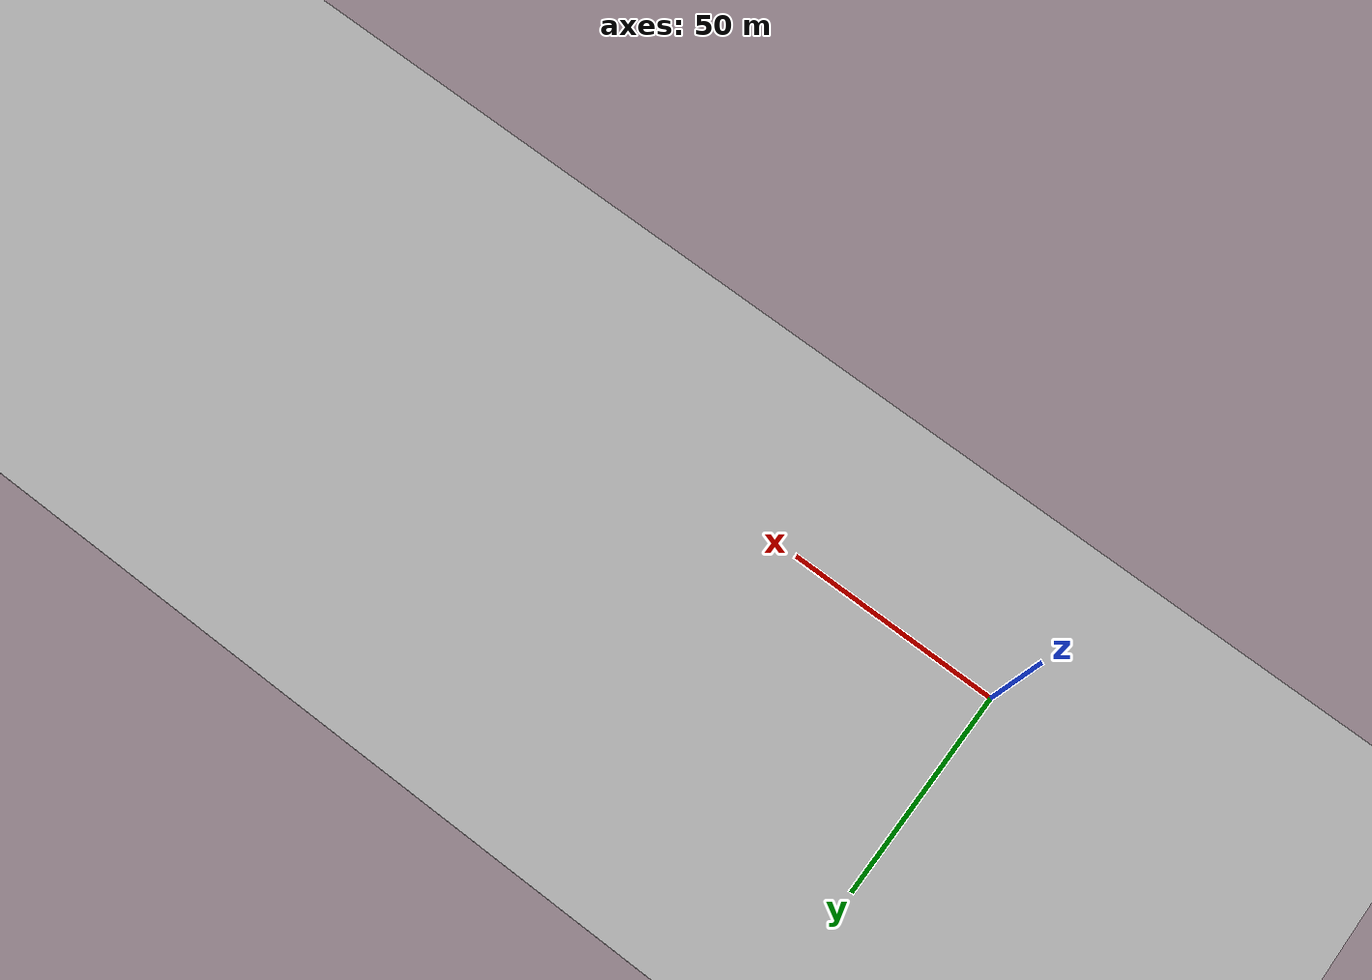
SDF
<sdf version="1.10">
 <world name="myworld">
  <physics type="ode">
   <max_step_size>0.004</max_step_size>
   <real_time_factor>1.0</real_time_factor>
   <real_time_update_rate>250</real_time_update_rate>
  </physics>
  <gravity>0 0 -9.8</gravity>
  <magnetic_field>6e-06 2.3e-05 -4.2e-05</magnetic_field>
  <atmosphere type="adiabatic"/>
  <scene>
   <grid>false</grid>
   <ambient>0.4 0.4 0.4 1</ambient>
   <background>0.7 0.7 0.7 1</background>
   <shadows>true</shadows>
  </scene>
  <model name="rail-1">
   <static>true</static>
   <pose>-36 0 0 0 0 0</pose>
   <link name="rail_link">
    <visual name="rail_left">
     <pose>0 0.75 0.050000000000000003 0 0 0</pose>
     <geometry><box><size>3 0.10000000000000001 0.10000000000000001</size></box></geometry>
     <material>
      <ambient>0.800000012 0.800000012 0.800000012 1</ambient>
      <diffuse>0.899999976 0.899999976 0.899999976 1</diffuse>
     </material>
    </visual>
    <visual name="rail_right">
     <pose>0 -0.75 0.050000000000000003 0 0 0</pose>
     <geometry><box><size>3 0.10000000000000001 0.10000000000000001</size></box></geometry>
     <material>
      <ambient>0.800000012 0.800000012 0.800000012 1</ambient>
      <diffuse>0.899999976 0.899999976 0.899999976 1</diffuse>
     </material>
    </visual>
    <visual name="traverse_1">
     <pose>1 0 0.025000000000000001 0 0 0</pose>
     <geometry><box><size>0.20000000000000001 2 0.050000000000000003</size></box></geometry>
     <material>
      <ambient>0.400000006 0.200000003 0.100000001 1</ambient>
      <diffuse>0.5 0.25 0.100000001 1</diffuse>
     </material>
    </visual>
    <visual name="traverse_2">
     <pose>0 0 0.025000000000000001 0 0 0</pose>
     <geometry><box><size>0.20000000000000001 2 0.050000000000000003</size></box></geometry>
     <material>
      <ambient>0.400000006 0.200000003 0.100000001 1</ambient>
      <diffuse>0.5 0.25 0.100000001 1</diffuse>
     </material>
    </visual>
    <visual name="traverse_3">
     <pose>-1 0 0.025000000000000001 0 0 0</pose>
     <geometry><box><size>0.20000000000000001 2 0.050000000000000003</size></box></geometry>
     <material>
      <ambient>0.400000006 0.200000003 0.100000001 1</ambient>
      <diffuse>0.5 0.25 0.100000001 1</diffuse>
     </material>
    </visual>
    <inertial>
     <mass>1</mass>
     <inertia><ixx>1</ixx><ixy>0</ixy><ixz>0</ixz><iyy>1</iyy><iyz>0</iyz><izz>1</izz></inertia>
    </inertial>
   </link>
  </model>
  <model name="rail-2">
   <static>true</static>
   <pose>-3 0 0 0 0 0</pose>
   <link name="rail_link">
    <visual name="rail_left">
     <pose>0 0.75 0.050000000000000003 0 0 0</pose>
     <geometry><box><size>3 0.10000000000000001 0.10000000000000001</size></box></geometry>
     <material>
      <ambient>0.800000012 0.800000012 0.800000012 1</ambient>
      <diffuse>0.899999976 0.899999976 0.899999976 1</diffuse>
     </material>
    </visual>
    <visual name="rail_right">
     <pose>0 -0.75 0.050000000000000003 0 0 0</pose>
     <geometry><box><size>3 0.10000000000000001 0.10000000000000001</size></box></geometry>
     <material>
      <ambient>0.800000012 0.800000012 0.800000012 1</ambient>
      <diffuse>0.899999976 0.899999976 0.899999976 1</diffuse>
     </material>
    </visual>
    <visual name="traverse_1">
     <pose>1 0 0.025000000000000001 0 0 0</pose>
     <geometry><box><size>0.20000000000000001 2 0.050000000000000003</size></box></geometry>
     <material>
      <ambient>0.400000006 0.200000003 0.100000001 1</ambient>
      <diffuse>0.5 0.25 0.100000001 1</diffuse>
     </material>
    </visual>
    <visual name="traverse_2">
     <pose>0 0 0.025000000000000001 0 0 0</pose>
     <geometry><box><size>0.20000000000000001 2 0.050000000000000003</size></box></geometry>
     <material>
      <ambient>0.400000006 0.200000003 0.100000001 1</ambient>
      <diffuse>0.5 0.25 0.100000001 1</diffuse>
     </material>
    </visual>
    <visual name="traverse_3">
     <pose>-1 0 0.025000000000000001 0 0 0</pose>
     <geometry><box><size>0.20000000000000001 2 0.050000000000000003</size></box></geometry>
     <material>
      <ambient>0.400000006 0.200000003 0.100000001 1</ambient>
      <diffuse>0.5 0.25 0.100000001 1</diffuse>
     </material>
    </visual>
    <inertial>
     <mass>1</mass>
     <inertia><ixx>1</ixx><ixy>0</ixy><ixz>0</ixz><iyy>1</iyy><iyz>0</iyz><izz>1</izz></inertia>
    </inertial>
   </link>
  </model>
  <model name="rail-3">
   <static>true</static>
   <pose>-6 0 0 0 0 0</pose>
   <link name="rail_link">
    <visual name="rail_left">
     <pose>0 0.75 0.050000000000000003 0 0 0</pose>
     <geometry><box><size>3 0.10000000000000001 0.10000000000000001</size></box></geometry>
     <material>
      <ambient>0.800000012 0.800000012 0.800000012 1</ambient>
      <diffuse>0.899999976 0.899999976 0.899999976 1</diffuse>
     </material>
    </visual>
    <visual name="rail_right">
     <pose>0 -0.75 0.050000000000000003 0 0 0</pose>
     <geometry><box><size>3 0.10000000000000001 0.10000000000000001</size></box></geometry>
     <material>
      <ambient>0.800000012 0.800000012 0.800000012 1</ambient>
      <diffuse>0.899999976 0.899999976 0.899999976 1</diffuse>
     </material>
    </visual>
    <visual name="traverse_1">
     <pose>1 0 0.025000000000000001 0 0 0</pose>
     <geometry><box><size>0.20000000000000001 2 0.050000000000000003</size></box></geometry>
     <material>
      <ambient>0.400000006 0.200000003 0.100000001 1</ambient>
      <diffuse>0.5 0.25 0.100000001 1</diffuse>
     </material>
    </visual>
    <visual name="traverse_2">
     <pose>0 0 0.025000000000000001 0 0 0</pose>
     <geometry><box><size>0.20000000000000001 2 0.050000000000000003</size></box></geometry>
     <material>
      <ambient>0.400000006 0.200000003 0.100000001 1</ambient>
      <diffuse>0.5 0.25 0.100000001 1</diffuse>
     </material>
    </visual>
    <visual name="traverse_3">
     <pose>-1 0 0.025000000000000001 0 0 0</pose>
     <geometry><box><size>0.20000000000000001 2 0.050000000000000003</size></box></geometry>
     <material>
      <ambient>0.400000006 0.200000003 0.100000001 1</ambient>
      <diffuse>0.5 0.25 0.100000001 1</diffuse>
     </material>
    </visual>
    <inertial>
     <mass>1</mass>
     <inertia><ixx>1</ixx><ixy>0</ixy><ixz>0</ixz><iyy>1</iyy><iyz>0</iyz><izz>1</izz></inertia>
    </inertial>
   </link>
  </model>
  <model name="rail-4">
   <static>true</static>
   <pose>-9 0 0 0 0 0</pose>
   <link name="rail_link">
    <visual name="rail_left">
     <pose>0 0.75 0.050000000000000003 0 0 0</pose>
     <geometry><box><size>3 0.10000000000000001 0.10000000000000001</size></box></geometry>
     <material>
      <ambient>0.800000012 0.800000012 0.800000012 1</ambient>
      <diffuse>0.899999976 0.899999976 0.899999976 1</diffuse>
     </material>
    </visual>
    <visual name="rail_right">
     <pose>0 -0.75 0.050000000000000003 0 0 0</pose>
     <geometry><box><size>3 0.10000000000000001 0.10000000000000001</size></box></geometry>
     <material>
      <ambient>0.800000012 0.800000012 0.800000012 1</ambient>
      <diffuse>0.899999976 0.899999976 0.899999976 1</diffuse>
     </material>
    </visual>
    <visual name="traverse_1">
     <pose>1 0 0.025000000000000001 0 0 0</pose>
     <geometry><box><size>0.20000000000000001 2 0.050000000000000003</size></box></geometry>
     <material>
      <ambient>0.400000006 0.200000003 0.100000001 1</ambient>
      <diffuse>0.5 0.25 0.100000001 1</diffuse>
     </material>
    </visual>
    <visual name="traverse_2">
     <pose>0 0 0.025000000000000001 0 0 0</pose>
     <geometry><box><size>0.20000000000000001 2 0.050000000000000003</size></box></geometry>
     <material>
      <ambient>0.400000006 0.200000003 0.100000001 1</ambient>
      <diffuse>0.5 0.25 0.100000001 1</diffuse>
     </material>
    </visual>
    <visual name="traverse_3">
     <pose>-1 0 0.025000000000000001 0 0 0</pose>
     <geometry><box><size>0.20000000000000001 2 0.050000000000000003</size></box></geometry>
     <material>
      <ambient>0.400000006 0.200000003 0.100000001 1</ambient>
      <diffuse>0.5 0.25 0.100000001 1</diffuse>
     </material>
    </visual>
    <inertial>
     <mass>1</mass>
     <inertia><ixx>1</ixx><ixy>0</ixy><ixz>0</ixz><iyy>1</iyy><iyz>0</iyz><izz>1</izz></inertia>
    </inertial>
   </link>
  </model>
  <model name="rail-5">
   <static>true</static>
   <pose>-12 0 0 0 0 0</pose>
   <link name="rail_link">
    <visual name="rail_left">
     <pose>0 0.75 0.050000000000000003 0 0 0</pose>
     <geometry><box><size>3 0.10000000000000001 0.10000000000000001</size></box></geometry>
     <material>
      <ambient>0.800000012 0.800000012 0.800000012 1</ambient>
      <diffuse>0.899999976 0.899999976 0.899999976 1</diffuse>
     </material>
    </visual>
    <visual name="rail_right">
     <pose>0 -0.75 0.050000000000000003 0 0 0</pose>
     <geometry><box><size>3 0.10000000000000001 0.10000000000000001</size></box></geometry>
     <material>
      <ambient>0.800000012 0.800000012 0.800000012 1</ambient>
      <diffuse>0.899999976 0.899999976 0.899999976 1</diffuse>
     </material>
    </visual>
    <visual name="traverse_1">
     <pose>1 0 0.025000000000000001 0 0 0</pose>
     <geometry><box><size>0.20000000000000001 2 0.050000000000000003</size></box></geometry>
     <material>
      <ambient>0.400000006 0.200000003 0.100000001 1</ambient>
      <diffuse>0.5 0.25 0.100000001 1</diffuse>
     </material>
    </visual>
    <visual name="traverse_2">
     <pose>0 0 0.025000000000000001 0 0 0</pose>
     <geometry><box><size>0.20000000000000001 2 0.050000000000000003</size></box></geometry>
     <material>
      <ambient>0.400000006 0.200000003 0.100000001 1</ambient>
      <diffuse>0.5 0.25 0.100000001 1</diffuse>
     </material>
    </visual>
    <visual name="traverse_3">
     <pose>-1 0 0.025000000000000001 0 0 0</pose>
     <geometry><box><size>0.20000000000000001 2 0.050000000000000003</size></box></geometry>
     <material>
      <ambient>0.400000006 0.200000003 0.100000001 1</ambient>
      <diffuse>0.5 0.25 0.100000001 1</diffuse>
     </material>
    </visual>
    <inertial>
     <mass>1</mass>
     <inertia><ixx>1</ixx><ixy>0</ixy><ixz>0</ixz><iyy>1</iyy><iyz>0</iyz><izz>1</izz></inertia>
    </inertial>
   </link>
  </model>
  <model name="rail-6">
   <static>true</static>
   <pose>-15 0 0 0 0 0</pose>
   <link name="rail_link">
    <visual name="rail_left">
     <pose>0 0.75 0.050000000000000003 0 0 0</pose>
     <geometry><box><size>3 0.10000000000000001 0.10000000000000001</size></box></geometry>
     <material>
      <ambient>0.800000012 0.800000012 0.800000012 1</ambient>
      <diffuse>0.899999976 0.899999976 0.899999976 1</diffuse>
     </material>
    </visual>
    <visual name="rail_right">
     <pose>0 -0.75 0.050000000000000003 0 0 0</pose>
     <geometry><box><size>3 0.10000000000000001 0.10000000000000001</size></box></geometry>
     <material>
      <ambient>0.800000012 0.800000012 0.800000012 1</ambient>
      <diffuse>0.899999976 0.899999976 0.899999976 1</diffuse>
     </material>
    </visual>
    <visual name="traverse_1">
     <pose>1 0 0.025000000000000001 0 0 0</pose>
     <geometry><box><size>0.20000000000000001 2 0.050000000000000003</size></box></geometry>
     <material>
      <ambient>0.400000006 0.200000003 0.100000001 1</ambient>
      <diffuse>0.5 0.25 0.100000001 1</diffuse>
     </material>
    </visual>
    <visual name="traverse_2">
     <pose>0 0 0.025000000000000001 0 0 0</pose>
     <geometry><box><size>0.20000000000000001 2 0.050000000000000003</size></box></geometry>
     <material>
      <ambient>0.400000006 0.200000003 0.100000001 1</ambient>
      <diffuse>0.5 0.25 0.100000001 1</diffuse>
     </material>
    </visual>
    <visual name="traverse_3">
     <pose>-1 0 0.025000000000000001 0 0 0</pose>
     <geometry><box><size>0.20000000000000001 2 0.050000000000000003</size></box></geometry>
     <material>
      <ambient>0.400000006 0.200000003 0.100000001 1</ambient>
      <diffuse>0.5 0.25 0.100000001 1</diffuse>
     </material>
    </visual>
    <inertial>
     <mass>1</mass>
     <inertia><ixx>1</ixx><ixy>0</ixy><ixz>0</ixz><iyy>1</iyy><iyz>0</iyz><izz>1</izz></inertia>
    </inertial>
   </link>
  </model>
  <model name="rail-7">
   <static>true</static>
   <pose>-18 0 0 0 0 0</pose>
   <link name="rail_link">
    <visual name="rail_left">
     <pose>0 0.75 0.050000000000000003 0 0 0</pose>
     <geometry><box><size>3 0.10000000000000001 0.10000000000000001</size></box></geometry>
     <material>
      <ambient>0.800000012 0.800000012 0.800000012 1</ambient>
      <diffuse>0.899999976 0.899999976 0.899999976 1</diffuse>
     </material>
    </visual>
    <visual name="rail_right">
     <pose>0 -0.75 0.050000000000000003 0 0 0</pose>
     <geometry><box><size>3 0.10000000000000001 0.10000000000000001</size></box></geometry>
     <material>
      <ambient>0.800000012 0.800000012 0.800000012 1</ambient>
      <diffuse>0.899999976 0.899999976 0.899999976 1</diffuse>
     </material>
    </visual>
    <visual name="traverse_1">
     <pose>1 0 0.025000000000000001 0 0 0</pose>
     <geometry><box><size>0.20000000000000001 2 0.050000000000000003</size></box></geometry>
     <material>
      <ambient>0.400000006 0.200000003 0.100000001 1</ambient>
      <diffuse>0.5 0.25 0.100000001 1</diffuse>
     </material>
    </visual>
    <visual name="traverse_2">
     <pose>0 0 0.025000000000000001 0 0 0</pose>
     <geometry><box><size>0.20000000000000001 2 0.050000000000000003</size></box></geometry>
     <material>
      <ambient>0.400000006 0.200000003 0.100000001 1</ambient>
      <diffuse>0.5 0.25 0.100000001 1</diffuse>
     </material>
    </visual>
    <visual name="traverse_3">
     <pose>-1 0 0.025000000000000001 0 0 0</pose>
     <geometry><box><size>0.20000000000000001 2 0.050000000000000003</size></box></geometry>
     <material>
      <ambient>0.400000006 0.200000003 0.100000001 1</ambient>
      <diffuse>0.5 0.25 0.100000001 1</diffuse>
     </material>
    </visual>
    <inertial>
     <mass>1</mass>
     <inertia><ixx>1</ixx><ixy>0</ixy><ixz>0</ixz><iyy>1</iyy><iyz>0</iyz><izz>1</izz></inertia>
    </inertial>
   </link>
  </model>
  <model name="rail-8">
   <static>true</static>
   <pose>-21 0 0 0 0 0</pose>
   <link name="rail_link">
    <visual name="rail_left">
     <pose>0 0.75 0.050000000000000003 0 0 0</pose>
     <geometry><box><size>3 0.10000000000000001 0.10000000000000001</size></box></geometry>
     <material>
      <ambient>0.800000012 0.800000012 0.800000012 1</ambient>
      <diffuse>0.899999976 0.899999976 0.899999976 1</diffuse>
     </material>
    </visual>
    <visual name="rail_right">
     <pose>0 -0.75 0.050000000000000003 0 0 0</pose>
     <geometry><box><size>3 0.10000000000000001 0.10000000000000001</size></box></geometry>
     <material>
      <ambient>0.800000012 0.800000012 0.800000012 1</ambient>
      <diffuse>0.899999976 0.899999976 0.899999976 1</diffuse>
     </material>
    </visual>
    <visual name="traverse_1">
     <pose>1 0 0.025000000000000001 0 0 0</pose>
     <geometry><box><size>0.20000000000000001 2 0.050000000000000003</size></box></geometry>
     <material>
      <ambient>0.400000006 0.200000003 0.100000001 1</ambient>
      <diffuse>0.5 0.25 0.100000001 1</diffuse>
     </material>
    </visual>
    <visual name="traverse_2">
     <pose>0 0 0.025000000000000001 0 0 0</pose>
     <geometry><box><size>0.20000000000000001 2 0.050000000000000003</size></box></geometry>
     <material>
      <ambient>0.400000006 0.200000003 0.100000001 1</ambient>
      <diffuse>0.5 0.25 0.100000001 1</diffuse>
     </material>
    </visual>
    <visual name="traverse_3">
     <pose>-1 0 0.025000000000000001 0 0 0</pose>
     <geometry><box><size>0.20000000000000001 2 0.050000000000000003</size></box></geometry>
     <material>
      <ambient>0.400000006 0.200000003 0.100000001 1</ambient>
      <diffuse>0.5 0.25 0.100000001 1</diffuse>
     </material>
    </visual>
    <inertial>
     <mass>1</mass>
     <inertia><ixx>1</ixx><ixy>0</ixy><ixz>0</ixz><iyy>1</iyy><iyz>0</iyz><izz>1</izz></inertia>
    </inertial>
   </link>
  </model>
  <model name="rail-9">
   <static>true</static>
   <pose>-24 0 0 0 0 0</pose>
   <link name="rail_link">
    <visual name="rail_left">
     <pose>0 0.75 0.050000000000000003 0 0 0</pose>
     <geometry><box><size>3 0.10000000000000001 0.10000000000000001</size></box></geometry>
     <material>
      <ambient>0.800000012 0.800000012 0.800000012 1</ambient>
      <diffuse>0.899999976 0.899999976 0.899999976 1</diffuse>
     </material>
    </visual>
    <visual name="rail_right">
     <pose>0 -0.75 0.050000000000000003 0 0 0</pose>
     <geometry><box><size>3 0.10000000000000001 0.10000000000000001</size></box></geometry>
     <material>
      <ambient>0.800000012 0.800000012 0.800000012 1</ambient>
      <diffuse>0.899999976 0.899999976 0.899999976 1</diffuse>
     </material>
    </visual>
    <visual name="traverse_1">
     <pose>1 0 0.025000000000000001 0 0 0</pose>
     <geometry><box><size>0.20000000000000001 2 0.050000000000000003</size></box></geometry>
     <material>
      <ambient>0.400000006 0.200000003 0.100000001 1</ambient>
      <diffuse>0.5 0.25 0.100000001 1</diffuse>
     </material>
    </visual>
    <visual name="traverse_2">
     <pose>0 0 0.025000000000000001 0 0 0</pose>
     <geometry><box><size>0.20000000000000001 2 0.050000000000000003</size></box></geometry>
     <material>
      <ambient>0.400000006 0.200000003 0.100000001 1</ambient>
      <diffuse>0.5 0.25 0.100000001 1</diffuse>
     </material>
    </visual>
    <visual name="traverse_3">
     <pose>-1 0 0.025000000000000001 0 0 0</pose>
     <geometry><box><size>0.20000000000000001 2 0.050000000000000003</size></box></geometry>
     <material>
      <ambient>0.400000006 0.200000003 0.100000001 1</ambient>
      <diffuse>0.5 0.25 0.100000001 1</diffuse>
     </material>
    </visual>
    <inertial>
     <mass>1</mass>
     <inertia><ixx>1</ixx><ixy>0</ixy><ixz>0</ixz><iyy>1</iyy><iyz>0</iyz><izz>1</izz></inertia>
    </inertial>
   </link>
  </model>
  <model name="rail-10">
   <static>true</static>
   <pose>-27 0 0 0 0 0</pose>
   <link name="rail_link">
    <visual name="rail_left">
     <pose>0 0.75 0.050000000000000003 0 0 0</pose>
     <geometry><box><size>3 0.10000000000000001 0.10000000000000001</size></box></geometry>
     <material>
      <ambient>0.800000012 0.800000012 0.800000012 1</ambient>
      <diffuse>0.899999976 0.899999976 0.899999976 1</diffuse>
     </material>
    </visual>
    <visual name="rail_right">
     <pose>0 -0.75 0.050000000000000003 0 0 0</pose>
     <geometry><box><size>3 0.10000000000000001 0.10000000000000001</size></box></geometry>
     <material>
      <ambient>0.800000012 0.800000012 0.800000012 1</ambient>
      <diffuse>0.899999976 0.899999976 0.899999976 1</diffuse>
     </material>
    </visual>
    <visual name="traverse_1">
     <pose>1 0 0.025000000000000001 0 0 0</pose>
     <geometry><box><size>0.20000000000000001 2 0.050000000000000003</size></box></geometry>
     <material>
      <ambient>0.400000006 0.200000003 0.100000001 1</ambient>
      <diffuse>0.5 0.25 0.100000001 1</diffuse>
     </material>
    </visual>
    <visual name="traverse_2">
     <pose>0 0 0.025000000000000001 0 0 0</pose>
     <geometry><box><size>0.20000000000000001 2 0.050000000000000003</size></box></geometry>
     <material>
      <ambient>0.400000006 0.200000003 0.100000001 1</ambient>
      <diffuse>0.5 0.25 0.100000001 1</diffuse>
     </material>
    </visual>
    <visual name="traverse_3">
     <pose>-1 0 0.025000000000000001 0 0 0</pose>
     <geometry><box><size>0.20000000000000001 2 0.050000000000000003</size></box></geometry>
     <material>
      <ambient>0.400000006 0.200000003 0.100000001 1</ambient>
      <diffuse>0.5 0.25 0.100000001 1</diffuse>
     </material>
    </visual>
    <inertial>
     <mass>1</mass>
     <inertia><ixx>1</ixx><ixy>0</ixy><ixz>0</ixz><iyy>1</iyy><iyz>0</iyz><izz>1</izz></inertia>
    </inertial>
   </link>
  </model>
  <model name="rail-11">
   <static>true</static>
   <pose>-30 0 0 0 0 0</pose>
   <link name="rail_link">
    <visual name="rail_left">
     <pose>0 0.75 0.050000000000000003 0 0 0</pose>
     <geometry><box><size>3 0.10000000000000001 0.10000000000000001</size></box></geometry>
     <material>
      <ambient>0.800000012 0.800000012 0.800000012 1</ambient>
      <diffuse>0.899999976 0.899999976 0.899999976 1</diffuse>
     </material>
    </visual>
    <visual name="rail_right">
     <pose>0 -0.75 0.050000000000000003 0 0 0</pose>
     <geometry><box><size>3 0.10000000000000001 0.10000000000000001</size></box></geometry>
     <material>
      <ambient>0.800000012 0.800000012 0.800000012 1</ambient>
      <diffuse>0.899999976 0.899999976 0.899999976 1</diffuse>
     </material>
    </visual>
    <visual name="traverse_1">
     <pose>1 0 0.025000000000000001 0 0 0</pose>
     <geometry><box><size>0.20000000000000001 2 0.050000000000000003</size></box></geometry>
     <material>
      <ambient>0.400000006 0.200000003 0.100000001 1</ambient>
      <diffuse>0.5 0.25 0.100000001 1</diffuse>
     </material>
    </visual>
    <visual name="traverse_2">
     <pose>0 0 0.025000000000000001 0 0 0</pose>
     <geometry><box><size>0.20000000000000001 2 0.050000000000000003</size></box></geometry>
     <material>
      <ambient>0.400000006 0.200000003 0.100000001 1</ambient>
      <diffuse>0.5 0.25 0.100000001 1</diffuse>
     </material>
    </visual>
    <visual name="traverse_3">
     <pose>-1 0 0.025000000000000001 0 0 0</pose>
     <geometry><box><size>0.20000000000000001 2 0.050000000000000003</size></box></geometry>
     <material>
      <ambient>0.400000006 0.200000003 0.100000001 1</ambient>
      <diffuse>0.5 0.25 0.100000001 1</diffuse>
     </material>
    </visual>
    <inertial>
     <mass>1</mass>
     <inertia><ixx>1</ixx><ixy>0</ixy><ixz>0</ixz><iyy>1</iyy><iyz>0</iyz><izz>1</izz></inertia>
    </inertial>
   </link>
  </model>
  <model name="rail-12">
   <static>true</static>
   <pose>-33 0 0 0 0 0</pose>
   <link name="rail_link">
    <visual name="rail_left">
     <pose>0 0.75 0.050000000000000003 0 0 0</pose>
     <geometry><box><size>3 0.10000000000000001 0.10000000000000001</size></box></geometry>
     <material>
      <ambient>0.800000012 0.800000012 0.800000012 1</ambient>
      <diffuse>0.899999976 0.899999976 0.899999976 1</diffuse>
     </material>
    </visual>
    <visual name="rail_right">
     <pose>0 -0.75 0.050000000000000003 0 0 0</pose>
     <geometry><box><size>3 0.10000000000000001 0.10000000000000001</size></box></geometry>
     <material>
      <ambient>0.800000012 0.800000012 0.800000012 1</ambient>
      <diffuse>0.899999976 0.899999976 0.899999976 1</diffuse>
     </material>
    </visual>
    <visual name="traverse_1">
     <pose>1 0 0.025000000000000001 0 0 0</pose>
     <geometry><box><size>0.20000000000000001 2 0.050000000000000003</size></box></geometry>
     <material>
      <ambient>0.400000006 0.200000003 0.100000001 1</ambient>
      <diffuse>0.5 0.25 0.100000001 1</diffuse>
     </material>
    </visual>
    <visual name="traverse_2">
     <pose>0 0 0.025000000000000001 0 0 0</pose>
     <geometry><box><size>0.20000000000000001 2 0.050000000000000003</size></box></geometry>
     <material>
      <ambient>0.400000006 0.200000003 0.100000001 1</ambient>
      <diffuse>0.5 0.25 0.100000001 1</diffuse>
     </material>
    </visual>
    <visual name="traverse_3">
     <pose>-1 0 0.025000000000000001 0 0 0</pose>
     <geometry><box><size>0.20000000000000001 2 0.050000000000000003</size></box></geometry>
     <material>
      <ambient>0.400000006 0.200000003 0.100000001 1</ambient>
      <diffuse>0.5 0.25 0.100000001 1</diffuse>
     </material>
    </visual>
    <inertial>
     <mass>1</mass>
     <inertia><ixx>1</ixx><ixy>0</ixy><ixz>0</ixz><iyy>1</iyy><iyz>0</iyz><izz>1</izz></inertia>
    </inertial>
   </link>
  </model>
  <model name="rail1">
   <static>true</static>
   <link name="rail_link">
    <visual name="rail_left">
     <pose>0 0.75 0.050000000000000003 0 0 0</pose>
     <geometry><box><size>3 0.10000000000000001 0.10000000000000001</size></box></geometry>
     <material>
      <ambient>0.800000012 0.800000012 0.800000012 1</ambient>
      <diffuse>0.899999976 0.899999976 0.899999976 1</diffuse>
     </material>
    </visual>
    <visual name="rail_right">
     <pose>0 -0.75 0.050000000000000003 0 0 0</pose>
     <geometry><box><size>3 0.10000000000000001 0.10000000000000001</size></box></geometry>
     <material>
      <ambient>0.800000012 0.800000012 0.800000012 1</ambient>
      <diffuse>0.899999976 0.899999976 0.899999976 1</diffuse>
     </material>
    </visual>
    <visual name="traverse_1">
     <pose>1 0 0.025000000000000001 0 0 0</pose>
     <geometry><box><size>0.20000000000000001 2 0.050000000000000003</size></box></geometry>
     <material>
      <ambient>0.400000006 0.200000003 0.100000001 1</ambient>
      <diffuse>0.5 0.25 0.100000001 1</diffuse>
     </material>
    </visual>
    <visual name="traverse_2">
     <pose>0 0 0.025000000000000001 0 0 0</pose>
     <geometry><box><size>0.20000000000000001 2 0.050000000000000003</size></box></geometry>
     <material>
      <ambient>0.400000006 0.200000003 0.100000001 1</ambient>
      <diffuse>0.5 0.25 0.100000001 1</diffuse>
     </material>
    </visual>
    <visual name="traverse_3">
     <pose>-1 0 0.025000000000000001 0 0 0</pose>
     <geometry><box><size>0.20000000000000001 2 0.050000000000000003</size></box></geometry>
     <material>
      <ambient>0.400000006 0.200000003 0.100000001 1</ambient>
      <diffuse>0.5 0.25 0.100000001 1</diffuse>
     </material>
    </visual>
    <inertial>
     <mass>1</mass>
     <inertia><ixx>1</ixx><ixy>0</ixy><ixz>0</ixz><iyy>1</iyy><iyz>0</iyz><izz>1</izz></inertia>
    </inertial>
   </link>
  </model>
  <model name="rail2">
   <static>true</static>
   <pose>3 0 0 0 0 0</pose>
   <link name="rail_link">
    <visual name="rail_left">
     <pose>0 0.75 0.050000000000000003 0 0 0</pose>
     <geometry><box><size>3 0.10000000000000001 0.10000000000000001</size></box></geometry>
     <material>
      <ambient>0.800000012 0.800000012 0.800000012 1</ambient>
      <diffuse>0.899999976 0.899999976 0.899999976 1</diffuse>
     </material>
    </visual>
    <visual name="rail_right">
     <pose>0 -0.75 0.050000000000000003 0 0 0</pose>
     <geometry><box><size>3 0.10000000000000001 0.10000000000000001</size></box></geometry>
     <material>
      <ambient>0.800000012 0.800000012 0.800000012 1</ambient>
      <diffuse>0.899999976 0.899999976 0.899999976 1</diffuse>
     </material>
    </visual>
    <visual name="traverse_1">
     <pose>1 0 0.025000000000000001 0 0 0</pose>
     <geometry><box><size>0.20000000000000001 2 0.050000000000000003</size></box></geometry>
     <material>
      <ambient>0.400000006 0.200000003 0.100000001 1</ambient>
      <diffuse>0.5 0.25 0.100000001 1</diffuse>
     </material>
    </visual>
    <visual name="traverse_2">
     <pose>0 0 0.025000000000000001 0 0 0</pose>
     <geometry><box><size>0.20000000000000001 2 0.050000000000000003</size></box></geometry>
     <material>
      <ambient>0.400000006 0.200000003 0.100000001 1</ambient>
      <diffuse>0.5 0.25 0.100000001 1</diffuse>
     </material>
    </visual>
    <visual name="traverse_3">
     <pose>-1 0 0.025000000000000001 0 0 0</pose>
     <geometry><box><size>0.20000000000000001 2 0.050000000000000003</size></box></geometry>
     <material>
      <ambient>0.400000006 0.200000003 0.100000001 1</ambient>
      <diffuse>0.5 0.25 0.100000001 1</diffuse>
     </material>
    </visual>
    <inertial>
     <mass>1</mass>
     <inertia><ixx>1</ixx><ixy>0</ixy><ixz>0</ixz><iyy>1</iyy><iyz>0</iyz><izz>1</izz></inertia>
    </inertial>
   </link>
  </model>
  <model name="rail3">
   <static>true</static>
   <pose>6 0 0 0 0 0</pose>
   <link name="rail_link">
    <visual name="rail_left">
     <pose>0 0.75 0.050000000000000003 0 0 0</pose>
     <geometry><box><size>3 0.10000000000000001 0.10000000000000001</size></box></geometry>
     <material>
      <ambient>0.800000012 0.800000012 0.800000012 1</ambient>
      <diffuse>0.899999976 0.899999976 0.899999976 1</diffuse>
     </material>
    </visual>
    <visual name="rail_right">
     <pose>0 -0.75 0.050000000000000003 0 0 0</pose>
     <geometry><box><size>3 0.10000000000000001 0.10000000000000001</size></box></geometry>
     <material>
      <ambient>0.800000012 0.800000012 0.800000012 1</ambient>
      <diffuse>0.899999976 0.899999976 0.899999976 1</diffuse>
     </material>
    </visual>
    <visual name="traverse_1">
     <pose>1 0 0.025000000000000001 0 0 0</pose>
     <geometry><box><size>0.20000000000000001 2 0.050000000000000003</size></box></geometry>
     <material>
      <ambient>0.400000006 0.200000003 0.100000001 1</ambient>
      <diffuse>0.5 0.25 0.100000001 1</diffuse>
     </material>
    </visual>
    <visual name="traverse_2">
     <pose>0 0 0.025000000000000001 0 0 0</pose>
     <geometry><box><size>0.20000000000000001 2 0.050000000000000003</size></box></geometry>
     <material>
      <ambient>0.400000006 0.200000003 0.100000001 1</ambient>
      <diffuse>0.5 0.25 0.100000001 1</diffuse>
     </material>
    </visual>
    <visual name="traverse_3">
     <pose>-1 0 0.025000000000000001 0 0 0</pose>
     <geometry><box><size>0.20000000000000001 2 0.050000000000000003</size></box></geometry>
     <material>
      <ambient>0.400000006 0.200000003 0.100000001 1</ambient>
      <diffuse>0.5 0.25 0.100000001 1</diffuse>
     </material>
    </visual>
    <inertial>
     <mass>1</mass>
     <inertia><ixx>1</ixx><ixy>0</ixy><ixz>0</ixz><iyy>1</iyy><iyz>0</iyz><izz>1</izz></inertia>
    </inertial>
   </link>
  </model>
  <model name="rail4">
   <static>true</static>
   <pose>9 0 0 0 0 0</pose>
   <link name="rail_link">
    <visual name="rail_left">
     <pose>0 0.75 0.050000000000000003 0 0 0</pose>
     <geometry><box><size>3 0.10000000000000001 0.10000000000000001</size></box></geometry>
     <material>
      <ambient>0.800000012 0.800000012 0.800000012 1</ambient>
      <diffuse>0.899999976 0.899999976 0.899999976 1</diffuse>
     </material>
    </visual>
    <visual name="rail_right">
     <pose>0 -0.75 0.050000000000000003 0 0 0</pose>
     <geometry><box><size>3 0.10000000000000001 0.10000000000000001</size></box></geometry>
     <material>
      <ambient>0.800000012 0.800000012 0.800000012 1</ambient>
      <diffuse>0.899999976 0.899999976 0.899999976 1</diffuse>
     </material>
    </visual>
    <visual name="traverse_1">
     <pose>1 0 0.025000000000000001 0 0 0</pose>
     <geometry><box><size>0.20000000000000001 2 0.050000000000000003</size></box></geometry>
     <material>
      <ambient>0.400000006 0.200000003 0.100000001 1</ambient>
      <diffuse>0.5 0.25 0.100000001 1</diffuse>
     </material>
    </visual>
    <visual name="traverse_2">
     <pose>0 0 0.025000000000000001 0 0 0</pose>
     <geometry><box><size>0.20000000000000001 2 0.050000000000000003</size></box></geometry>
     <material>
      <ambient>0.400000006 0.200000003 0.100000001 1</ambient>
      <diffuse>0.5 0.25 0.100000001 1</diffuse>
     </material>
    </visual>
    <visual name="traverse_3">
     <pose>-1 0 0.025000000000000001 0 0 0</pose>
     <geometry><box><size>0.20000000000000001 2 0.050000000000000003</size></box></geometry>
     <material>
      <ambient>0.400000006 0.200000003 0.100000001 1</ambient>
      <diffuse>0.5 0.25 0.100000001 1</diffuse>
     </material>
    </visual>
    <inertial>
     <mass>1</mass>
     <inertia><ixx>1</ixx><ixy>0</ixy><ixz>0</ixz><iyy>1</iyy><iyz>0</iyz><izz>1</izz></inertia>
    </inertial>
   </link>
  </model>
  <model name="rail5">
   <static>true</static>
   <pose>12 0 0 0 0 0</pose>
   <link name="rail_link">
    <visual name="rail_left">
     <pose>0 0.75 0.050000000000000003 0 0 0</pose>
     <geometry><box><size>3 0.10000000000000001 0.10000000000000001</size></box></geometry>
     <material>
      <ambient>0.800000012 0.800000012 0.800000012 1</ambient>
      <diffuse>0.899999976 0.899999976 0.899999976 1</diffuse>
     </material>
    </visual>
    <visual name="rail_right">
     <pose>0 -0.75 0.050000000000000003 0 0 0</pose>
     <geometry><box><size>3 0.10000000000000001 0.10000000000000001</size></box></geometry>
     <material>
      <ambient>0.800000012 0.800000012 0.800000012 1</ambient>
      <diffuse>0.899999976 0.899999976 0.899999976 1</diffuse>
     </material>
    </visual>
    <visual name="traverse_1">
     <pose>1 0 0.025000000000000001 0 0 0</pose>
     <geometry><box><size>0.20000000000000001 2 0.050000000000000003</size></box></geometry>
     <material>
      <ambient>0.400000006 0.200000003 0.100000001 1</ambient>
      <diffuse>0.5 0.25 0.100000001 1</diffuse>
     </material>
    </visual>
    <visual name="traverse_2">
     <pose>0 0 0.025000000000000001 0 0 0</pose>
     <geometry><box><size>0.20000000000000001 2 0.050000000000000003</size></box></geometry>
     <material>
      <ambient>0.400000006 0.200000003 0.100000001 1</ambient>
      <diffuse>0.5 0.25 0.100000001 1</diffuse>
     </material>
    </visual>
    <visual name="traverse_3">
     <pose>-1 0 0.025000000000000001 0 0 0</pose>
     <geometry><box><size>0.20000000000000001 2 0.050000000000000003</size></box></geometry>
     <material>
      <ambient>0.400000006 0.200000003 0.100000001 1</ambient>
      <diffuse>0.5 0.25 0.100000001 1</diffuse>
     </material>
    </visual>
    <inertial>
     <mass>1</mass>
     <inertia><ixx>1</ixx><ixy>0</ixy><ixz>0</ixz><iyy>1</iyy><iyz>0</iyz><izz>1</izz></inertia>
    </inertial>
   </link>
  </model>
  <model name="rail6">
   <static>true</static>
   <pose>15 0 0 0 0 0</pose>
   <link name="rail_link">
    <visual name="rail_left">
     <pose>0 0.75 0.050000000000000003 0 0 0</pose>
     <geometry><box><size>3 0.10000000000000001 0.10000000000000001</size></box></geometry>
     <material>
      <ambient>0.800000012 0.800000012 0.800000012 1</ambient>
      <diffuse>0.899999976 0.899999976 0.899999976 1</diffuse>
     </material>
    </visual>
    <visual name="rail_right">
     <pose>0 -0.75 0.050000000000000003 0 0 0</pose>
     <geometry><box><size>3 0.10000000000000001 0.10000000000000001</size></box></geometry>
     <material>
      <ambient>0.800000012 0.800000012 0.800000012 1</ambient>
      <diffuse>0.899999976 0.899999976 0.899999976 1</diffuse>
     </material>
    </visual>
    <visual name="traverse_1">
     <pose>1 0 0.025000000000000001 0 0 0</pose>
     <geometry><box><size>0.20000000000000001 2 0.050000000000000003</size></box></geometry>
     <material>
      <ambient>0.400000006 0.200000003 0.100000001 1</ambient>
      <diffuse>0.5 0.25 0.100000001 1</diffuse>
     </material>
    </visual>
    <visual name="traverse_2">
     <pose>0 0 0.025000000000000001 0 0 0</pose>
     <geometry><box><size>0.20000000000000001 2 0.050000000000000003</size></box></geometry>
     <material>
      <ambient>0.400000006 0.200000003 0.100000001 1</ambient>
      <diffuse>0.5 0.25 0.100000001 1</diffuse>
     </material>
    </visual>
    <visual name="traverse_3">
     <pose>-1 0 0.025000000000000001 0 0 0</pose>
     <geometry><box><size>0.20000000000000001 2 0.050000000000000003</size></box></geometry>
     <material>
      <ambient>0.400000006 0.200000003 0.100000001 1</ambient>
      <diffuse>0.5 0.25 0.100000001 1</diffuse>
     </material>
    </visual>
    <inertial>
     <mass>1</mass>
     <inertia><ixx>1</ixx><ixy>0</ixy><ixz>0</ixz><iyy>1</iyy><iyz>0</iyz><izz>1</izz></inertia>
    </inertial>
   </link>
  </model>
  <model name="rail7">
   <static>true</static>
   <pose>18 0 0 0 0 0</pose>
   <link name="rail_link">
    <visual name="rail_left">
     <pose>0 0.75 0.050000000000000003 0 0 0</pose>
     <geometry><box><size>3 0.10000000000000001 0.10000000000000001</size></box></geometry>
     <material>
      <ambient>0.800000012 0.800000012 0.800000012 1</ambient>
      <diffuse>0.899999976 0.899999976 0.899999976 1</diffuse>
     </material>
    </visual>
    <visual name="rail_right">
     <pose>0 -0.75 0.050000000000000003 0 0 0</pose>
     <geometry><box><size>3 0.10000000000000001 0.10000000000000001</size></box></geometry>
     <material>
      <ambient>0.800000012 0.800000012 0.800000012 1</ambient>
      <diffuse>0.899999976 0.899999976 0.899999976 1</diffuse>
     </material>
    </visual>
    <visual name="traverse_1">
     <pose>1 0 0.025000000000000001 0 0 0</pose>
     <geometry><box><size>0.20000000000000001 2 0.050000000000000003</size></box></geometry>
     <material>
      <ambient>0.400000006 0.200000003 0.100000001 1</ambient>
      <diffuse>0.5 0.25 0.100000001 1</diffuse>
     </material>
    </visual>
    <visual name="traverse_2">
     <pose>0 0 0.025000000000000001 0 0 0</pose>
     <geometry><box><size>0.20000000000000001 2 0.050000000000000003</size></box></geometry>
     <material>
      <ambient>0.400000006 0.200000003 0.100000001 1</ambient>
      <diffuse>0.5 0.25 0.100000001 1</diffuse>
     </material>
    </visual>
    <visual name="traverse_3">
     <pose>-1 0 0.025000000000000001 0 0 0</pose>
     <geometry><box><size>0.20000000000000001 2 0.050000000000000003</size></box></geometry>
     <material>
      <ambient>0.400000006 0.200000003 0.100000001 1</ambient>
      <diffuse>0.5 0.25 0.100000001 1</diffuse>
     </material>
    </visual>
    <inertial>
     <mass>1</mass>
     <inertia><ixx>1</ixx><ixy>0</ixy><ixz>0</ixz><iyy>1</iyy><iyz>0</iyz><izz>1</izz></inertia>
    </inertial>
   </link>
  </model>
  <model name="rail8">
   <static>true</static>
   <pose>21 0 0 0 0 0</pose>
   <link name="rail_link">
    <visual name="rail_left">
     <pose>0 0.75 0.050000000000000003 0 0 0</pose>
     <geometry><box><size>3 0.10000000000000001 0.10000000000000001</size></box></geometry>
     <material>
      <ambient>0.800000012 0.800000012 0.800000012 1</ambient>
      <diffuse>0.899999976 0.899999976 0.899999976 1</diffuse>
     </material>
    </visual>
    <visual name="rail_right">
     <pose>0 -0.75 0.050000000000000003 0 0 0</pose>
     <geometry><box><size>3 0.10000000000000001 0.10000000000000001</size></box></geometry>
     <material>
      <ambient>0.800000012 0.800000012 0.800000012 1</ambient>
      <diffuse>0.899999976 0.899999976 0.899999976 1</diffuse>
     </material>
    </visual>
    <visual name="traverse_1">
     <pose>1 0 0.025000000000000001 0 0 0</pose>
     <geometry><box><size>0.20000000000000001 2 0.050000000000000003</size></box></geometry>
     <material>
      <ambient>0.400000006 0.200000003 0.100000001 1</ambient>
      <diffuse>0.5 0.25 0.100000001 1</diffuse>
     </material>
    </visual>
    <visual name="traverse_2">
     <pose>0 0 0.025000000000000001 0 0 0</pose>
     <geometry><box><size>0.20000000000000001 2 0.050000000000000003</size></box></geometry>
     <material>
      <ambient>0.400000006 0.200000003 0.100000001 1</ambient>
      <diffuse>0.5 0.25 0.100000001 1</diffuse>
     </material>
    </visual>
    <visual name="traverse_3">
     <pose>-1 0 0.025000000000000001 0 0 0</pose>
     <geometry><box><size>0.20000000000000001 2 0.050000000000000003</size></box></geometry>
     <material>
      <ambient>0.400000006 0.200000003 0.100000001 1</ambient>
      <diffuse>0.5 0.25 0.100000001 1</diffuse>
     </material>
    </visual>
    <inertial>
     <mass>1</mass>
     <inertia><ixx>1</ixx><ixy>0</ixy><ixz>0</ixz><iyy>1</iyy><iyz>0</iyz><izz>1</izz></inertia>
    </inertial>
   </link>
  </model>
  <model name="rail9">
   <static>true</static>
   <pose>24 0 0 0 0 0</pose>
   <link name="rail_link">
    <visual name="rail_left">
     <pose>0 0.75 0.050000000000000003 0 0 0</pose>
     <geometry><box><size>3 0.10000000000000001 0.10000000000000001</size></box></geometry>
     <material>
      <ambient>0.800000012 0.800000012 0.800000012 1</ambient>
      <diffuse>0.899999976 0.899999976 0.899999976 1</diffuse>
     </material>
    </visual>
    <visual name="rail_right">
     <pose>0 -0.75 0.050000000000000003 0 0 0</pose>
     <geometry><box><size>3 0.10000000000000001 0.10000000000000001</size></box></geometry>
     <material>
      <ambient>0.800000012 0.800000012 0.800000012 1</ambient>
      <diffuse>0.899999976 0.899999976 0.899999976 1</diffuse>
     </material>
    </visual>
    <visual name="traverse_1">
     <pose>1 0 0.025000000000000001 0 0 0</pose>
     <geometry><box><size>0.20000000000000001 2 0.050000000000000003</size></box></geometry>
     <material>
      <ambient>0.400000006 0.200000003 0.100000001 1</ambient>
      <diffuse>0.5 0.25 0.100000001 1</diffuse>
     </material>
    </visual>
    <visual name="traverse_2">
     <pose>0 0 0.025000000000000001 0 0 0</pose>
     <geometry><box><size>0.20000000000000001 2 0.050000000000000003</size></box></geometry>
     <material>
      <ambient>0.400000006 0.200000003 0.100000001 1</ambient>
      <diffuse>0.5 0.25 0.100000001 1</diffuse>
     </material>
    </visual>
    <visual name="traverse_3">
     <pose>-1 0 0.025000000000000001 0 0 0</pose>
     <geometry><box><size>0.20000000000000001 2 0.050000000000000003</size></box></geometry>
     <material>
      <ambient>0.400000006 0.200000003 0.100000001 1</ambient>
      <diffuse>0.5 0.25 0.100000001 1</diffuse>
     </material>
    </visual>
    <inertial>
     <mass>1</mass>
     <inertia><ixx>1</ixx><ixy>0</ixy><ixz>0</ixz><iyy>1</iyy><iyz>0</iyz><izz>1</izz></inertia>
    </inertial>
   </link>
  </model>
  <model name="rail10">
   <static>true</static>
   <pose>27 0 0 0 0 0</pose>
   <link name="rail_link">
    <visual name="rail_left">
     <pose>0 0.75 0.050000000000000003 0 0 0</pose>
     <geometry><box><size>3 0.10000000000000001 0.10000000000000001</size></box></geometry>
     <material>
      <ambient>0.800000012 0.800000012 0.800000012 1</ambient>
      <diffuse>0.899999976 0.899999976 0.899999976 1</diffuse>
     </material>
    </visual>
    <visual name="rail_right">
     <pose>0 -0.75 0.050000000000000003 0 0 0</pose>
     <geometry><box><size>3 0.10000000000000001 0.10000000000000001</size></box></geometry>
     <material>
      <ambient>0.800000012 0.800000012 0.800000012 1</ambient>
      <diffuse>0.899999976 0.899999976 0.899999976 1</diffuse>
     </material>
    </visual>
    <visual name="traverse_1">
     <pose>1 0 0.025000000000000001 0 0 0</pose>
     <geometry><box><size>0.20000000000000001 2 0.050000000000000003</size></box></geometry>
     <material>
      <ambient>0.400000006 0.200000003 0.100000001 1</ambient>
      <diffuse>0.5 0.25 0.100000001 1</diffuse>
     </material>
    </visual>
    <visual name="traverse_2">
     <pose>0 0 0.025000000000000001 0 0 0</pose>
     <geometry><box><size>0.20000000000000001 2 0.050000000000000003</size></box></geometry>
     <material>
      <ambient>0.400000006 0.200000003 0.100000001 1</ambient>
      <diffuse>0.5 0.25 0.100000001 1</diffuse>
     </material>
    </visual>
    <visual name="traverse_3">
     <pose>-1 0 0.025000000000000001 0 0 0</pose>
     <geometry><box><size>0.20000000000000001 2 0.050000000000000003</size></box></geometry>
     <material>
      <ambient>0.400000006 0.200000003 0.100000001 1</ambient>
      <diffuse>0.5 0.25 0.100000001 1</diffuse>
     </material>
    </visual>
    <inertial>
     <mass>1</mass>
     <inertia><ixx>1</ixx><ixy>0</ixy><ixz>0</ixz><iyy>1</iyy><iyz>0</iyz><izz>1</izz></inertia>
    </inertial>
   </link>
  </model>
  <model name="rail11">
   <static>true</static>
   <pose>30 0 0 0 0 0</pose>
   <link name="rail_link">
    <visual name="rail_left">
     <pose>0 0.75 0.050000000000000003 0 0 0</pose>
     <geometry><box><size>3 0.10000000000000001 0.10000000000000001</size></box></geometry>
     <material>
      <ambient>0.800000012 0.800000012 0.800000012 1</ambient>
      <diffuse>0.899999976 0.899999976 0.899999976 1</diffuse>
     </material>
    </visual>
    <visual name="rail_right">
     <pose>0 -0.75 0.050000000000000003 0 0 0</pose>
     <geometry><box><size>3 0.10000000000000001 0.10000000000000001</size></box></geometry>
     <material>
      <ambient>0.800000012 0.800000012 0.800000012 1</ambient>
      <diffuse>0.899999976 0.899999976 0.899999976 1</diffuse>
     </material>
    </visual>
    <visual name="traverse_1">
     <pose>1 0 0.025000000000000001 0 0 0</pose>
     <geometry><box><size>0.20000000000000001 2 0.050000000000000003</size></box></geometry>
     <material>
      <ambient>0.400000006 0.200000003 0.100000001 1</ambient>
      <diffuse>0.5 0.25 0.100000001 1</diffuse>
     </material>
    </visual>
    <visual name="traverse_2">
     <pose>0 0 0.025000000000000001 0 0 0</pose>
     <geometry><box><size>0.20000000000000001 2 0.050000000000000003</size></box></geometry>
     <material>
      <ambient>0.400000006 0.200000003 0.100000001 1</ambient>
      <diffuse>0.5 0.25 0.100000001 1</diffuse>
     </material>
    </visual>
    <visual name="traverse_3">
     <pose>-1 0 0.025000000000000001 0 0 0</pose>
     <geometry><box><size>0.20000000000000001 2 0.050000000000000003</size></box></geometry>
     <material>
      <ambient>0.400000006 0.200000003 0.100000001 1</ambient>
      <diffuse>0.5 0.25 0.100000001 1</diffuse>
     </material>
    </visual>
    <inertial>
     <mass>1</mass>
     <inertia><ixx>1</ixx><ixy>0</ixy><ixz>0</ixz><iyy>1</iyy><iyz>0</iyz><izz>1</izz></inertia>
    </inertial>
   </link>
  </model>
  <model name="rail12">
   <static>true</static>
   <pose>33 0 0 0 0 0</pose>
   <link name="rail_link">
    <visual name="rail_left">
     <pose>0 0.75 0.050000000000000003 0 0 0</pose>
     <geometry><box><size>3 0.10000000000000001 0.10000000000000001</size></box></geometry>
     <material>
      <ambient>0.800000012 0.800000012 0.800000012 1</ambient>
      <diffuse>0.899999976 0.899999976 0.899999976 1</diffuse>
     </material>
    </visual>
    <visual name="rail_right">
     <pose>0 -0.75 0.050000000000000003 0 0 0</pose>
     <geometry><box><size>3 0.10000000000000001 0.10000000000000001</size></box></geometry>
     <material>
      <ambient>0.800000012 0.800000012 0.800000012 1</ambient>
      <diffuse>0.899999976 0.899999976 0.899999976 1</diffuse>
     </material>
    </visual>
    <visual name="traverse_1">
     <pose>1 0 0.025000000000000001 0 0 0</pose>
     <geometry><box><size>0.20000000000000001 2 0.050000000000000003</size></box></geometry>
     <material>
      <ambient>0.400000006 0.200000003 0.100000001 1</ambient>
      <diffuse>0.5 0.25 0.100000001 1</diffuse>
     </material>
    </visual>
    <visual name="traverse_2">
     <pose>0 0 0.025000000000000001 0 0 0</pose>
     <geometry><box><size>0.20000000000000001 2 0.050000000000000003</size></box></geometry>
     <material>
      <ambient>0.400000006 0.200000003 0.100000001 1</ambient>
      <diffuse>0.5 0.25 0.100000001 1</diffuse>
     </material>
    </visual>
    <visual name="traverse_3">
     <pose>-1 0 0.025000000000000001 0 0 0</pose>
     <geometry><box><size>0.20000000000000001 2 0.050000000000000003</size></box></geometry>
     <material>
      <ambient>0.400000006 0.200000003 0.100000001 1</ambient>
      <diffuse>0.5 0.25 0.100000001 1</diffuse>
     </material>
    </visual>
    <inertial>
     <mass>1</mass>
     <inertia><ixx>1</ixx><ixy>0</ixy><ixz>0</ixz><iyy>1</iyy><iyz>0</iyz><izz>1</izz></inertia>
    </inertial>
   </link>
  </model>
  <model name="ground_plane">
   <static>true</static>
   <link name="link">
    <collision name="collision">
     <geometry><plane><normal>0 0 1</normal><size>1000 1000</size></plane></geometry>
    </collision>
    <visual name="visual">
     <geometry><plane><normal>0 0 1</normal><size>1000 1000</size></plane></geometry>
     <material>
      <ambient>0.699999988 0.699999988 0.699999988 1</ambient>
      <diffuse>0.699999988 0.699999988 0.699999988 1</diffuse>
     </material>
    </visual>
    <inertial>
     <mass>1</mass>
     <inertia><ixx>1</ixx><ixy>0</ixy><ixz>0</ixz><iyy>1</iyy><iyz>0</iyz><izz>1</izz></inertia>
    </inertial>
   </link>
  </model>
  <model name="rail1_1">
   <static>true</static>
   <pose>-0.58130899999999996 14.5310300000000003 0 0 0 0</pose>
   <link name="rail_link">
    <visual name="rail_left">
     <pose>0 0.75 0.050000000000000003 0 0 0</pose>
     <geometry><box><size>3 0.10000000000000001 0.10000000000000001</size></box></geometry>
     <material>
      <ambient>0.800000012 0.800000012 0.800000012 1</ambient>
      <diffuse>0.899999976 0.899999976 0.899999976 1</diffuse>
     </material>
    </visual>
    <visual name="rail_right">
     <pose>0 -0.75 0.050000000000000003 0 0 0</pose>
     <geometry><box><size>3 0.10000000000000001 0.10000000000000001</size></box></geometry>
     <material>
      <ambient>0.800000012 0.800000012 0.800000012 1</ambient>
      <diffuse>0.899999976 0.899999976 0.899999976 1</diffuse>
     </material>
    </visual>
    <visual name="traverse_1">
     <pose>1 0 0.025000000000000001 0 0 0</pose>
     <geometry><box><size>0.20000000000000001 2 0.050000000000000003</size></box></geometry>
     <material>
      <ambient>0.400000006 0.200000003 0.100000001 1</ambient>
      <diffuse>0.5 0.25 0.100000001 1</diffuse>
     </material>
    </visual>
    <visual name="traverse_2">
     <pose>0 0 0.025000000000000001 0 0 0</pose>
     <geometry><box><size>0.20000000000000001 2 0.050000000000000003</size></box></geometry>
     <material>
      <ambient>0.400000006 0.200000003 0.100000001 1</ambient>
      <diffuse>0.5 0.25 0.100000001 1</diffuse>
     </material>
    </visual>
    <visual name="traverse_3">
     <pose>-1 0 0.025000000000000001 0 0 0</pose>
     <geometry><box><size>0.20000000000000001 2 0.050000000000000003</size></box></geometry>
     <material>
      <ambient>0.400000006 0.200000003 0.100000001 1</ambient>
      <diffuse>0.5 0.25 0.100000001 1</diffuse>
     </material>
    </visual>
   </link>
  </model>
  <model name="rail1_2">
   <static>true</static>
   <pose>2.3863599999999998 14.5340400000000001 0 0 0 0</pose>
   <link name="rail_link">
    <visual name="rail_left">
     <pose>0 0.75 0.050000000000000003 0 0 0</pose>
     <geometry><box><size>3 0.10000000000000001 0.10000000000000001</size></box></geometry>
     <material>
      <ambient>0.800000012 0.800000012 0.800000012 1</ambient>
      <diffuse>0.899999976 0.899999976 0.899999976 1</diffuse>
     </material>
    </visual>
    <visual name="rail_right">
     <pose>0 -0.75 0.050000000000000003 0 0 0</pose>
     <geometry><box><size>3 0.10000000000000001 0.10000000000000001</size></box></geometry>
     <material>
      <ambient>0.800000012 0.800000012 0.800000012 1</ambient>
      <diffuse>0.899999976 0.899999976 0.899999976 1</diffuse>
     </material>
    </visual>
    <visual name="traverse_1">
     <pose>1 0 0.025000000000000001 0 0 0</pose>
     <geometry><box><size>0.20000000000000001 2 0.050000000000000003</size></box></geometry>
     <material>
      <ambient>0.400000006 0.200000003 0.100000001 1</ambient>
      <diffuse>0.5 0.25 0.100000001 1</diffuse>
     </material>
    </visual>
    <visual name="traverse_2">
     <pose>0 0 0.025000000000000001 0 0 0</pose>
     <geometry><box><size>0.20000000000000001 2 0.050000000000000003</size></box></geometry>
     <material>
      <ambient>0.400000006 0.200000003 0.100000001 1</ambient>
      <diffuse>0.5 0.25 0.100000001 1</diffuse>
     </material>
    </visual>
    <visual name="traverse_3">
     <pose>-1 0 0.025000000000000001 0 0 0</pose>
     <geometry><box><size>0.20000000000000001 2 0.050000000000000003</size></box></geometry>
     <material>
      <ambient>0.400000006 0.200000003 0.100000001 1</ambient>
      <diffuse>0.5 0.25 0.100000001 1</diffuse>
     </material>
    </visual>
   </link>
  </model>
  <model name="rail1_3">
   <static>true</static>
   <pose>5.3673400000000004 14.5343799999999996 0 0 0 0</pose>
   <link name="rail_link">
    <visual name="rail_left">
     <pose>0 0.75 0.050000000000000003 0 0 0</pose>
     <geometry><box><size>3 0.10000000000000001 0.10000000000000001</size></box></geometry>
     <material>
      <ambient>0.800000012 0.800000012 0.800000012 1</ambient>
      <diffuse>0.899999976 0.899999976 0.899999976 1</diffuse>
     </material>
    </visual>
    <visual name="rail_right">
     <pose>0 -0.75 0.050000000000000003 0 0 0</pose>
     <geometry><box><size>3 0.10000000000000001 0.10000000000000001</size></box></geometry>
     <material>
      <ambient>0.800000012 0.800000012 0.800000012 1</ambient>
      <diffuse>0.899999976 0.899999976 0.899999976 1</diffuse>
     </material>
    </visual>
    <visual name="traverse_1">
     <pose>1 0 0.025000000000000001 0 0 0</pose>
     <geometry><box><size>0.20000000000000001 2 0.050000000000000003</size></box></geometry>
     <material>
      <ambient>0.400000006 0.200000003 0.100000001 1</ambient>
      <diffuse>0.5 0.25 0.100000001 1</diffuse>
     </material>
    </visual>
    <visual name="traverse_2">
     <pose>0 0 0.025000000000000001 0 0 0</pose>
     <geometry><box><size>0.20000000000000001 2 0.050000000000000003</size></box></geometry>
     <material>
      <ambient>0.400000006 0.200000003 0.100000001 1</ambient>
      <diffuse>0.5 0.25 0.100000001 1</diffuse>
     </material>
    </visual>
    <visual name="traverse_3">
     <pose>-1 0 0.025000000000000001 0 0 0</pose>
     <geometry><box><size>0.20000000000000001 2 0.050000000000000003</size></box></geometry>
     <material>
      <ambient>0.400000006 0.200000003 0.100000001 1</ambient>
      <diffuse>0.5 0.25 0.100000001 1</diffuse>
     </material>
    </visual>
   </link>
  </model>
  <model name="rail1_4">
   <static>true</static>
   <pose>8.3704300000000007 14.5355499999999997 0 0 0 0</pose>
   <link name="rail_link">
    <visual name="rail_left">
     <pose>0 0.75 0.050000000000000003 0 0 0</pose>
     <geometry><box><size>3 0.10000000000000001 0.10000000000000001</size></box></geometry>
     <material>
      <ambient>0.800000012 0.800000012 0.800000012 1</ambient>
      <diffuse>0.899999976 0.899999976 0.899999976 1</diffuse>
     </material>
    </visual>
    <visual name="rail_right">
     <pose>0 -0.75 0.050000000000000003 0 0 0</pose>
     <geometry><box><size>3 0.10000000000000001 0.10000000000000001</size></box></geometry>
     <material>
      <ambient>0.800000012 0.800000012 0.800000012 1</ambient>
      <diffuse>0.899999976 0.899999976 0.899999976 1</diffuse>
     </material>
    </visual>
    <visual name="traverse_1">
     <pose>1 0 0.025000000000000001 0 0 0</pose>
     <geometry><box><size>0.20000000000000001 2 0.050000000000000003</size></box></geometry>
     <material>
      <ambient>0.400000006 0.200000003 0.100000001 1</ambient>
      <diffuse>0.5 0.25 0.100000001 1</diffuse>
     </material>
    </visual>
    <visual name="traverse_2">
     <pose>0 0 0.025000000000000001 0 0 0</pose>
     <geometry><box><size>0.20000000000000001 2 0.050000000000000003</size></box></geometry>
     <material>
      <ambient>0.400000006 0.200000003 0.100000001 1</ambient>
      <diffuse>0.5 0.25 0.100000001 1</diffuse>
     </material>
    </visual>
    <visual name="traverse_3">
     <pose>-1 0 0.025000000000000001 0 0 0</pose>
     <geometry><box><size>0.20000000000000001 2 0.050000000000000003</size></box></geometry>
     <material>
      <ambient>0.400000006 0.200000003 0.100000001 1</ambient>
      <diffuse>0.5 0.25 0.100000001 1</diffuse>
     </material>
    </visual>
   </link>
  </model>
  <model name="rail1_5">
   <static>true</static>
   <pose>11.376099999999999 14.5394899999999998 0 0 0 0</pose>
   <link name="rail_link">
    <visual name="rail_left">
     <pose>0 0.75 0.050000000000000003 0 0 0</pose>
     <geometry><box><size>3 0.10000000000000001 0.10000000000000001</size></box></geometry>
     <material>
      <ambient>0.800000012 0.800000012 0.800000012 1</ambient>
      <diffuse>0.899999976 0.899999976 0.899999976 1</diffuse>
     </material>
    </visual>
    <visual name="rail_right">
     <pose>0 -0.75 0.050000000000000003 0 0 0</pose>
     <geometry><box><size>3 0.10000000000000001 0.10000000000000001</size></box></geometry>
     <material>
      <ambient>0.800000012 0.800000012 0.800000012 1</ambient>
      <diffuse>0.899999976 0.899999976 0.899999976 1</diffuse>
     </material>
    </visual>
    <visual name="traverse_1">
     <pose>1 0 0.025000000000000001 0 0 0</pose>
     <geometry><box><size>0.20000000000000001 2 0.050000000000000003</size></box></geometry>
     <material>
      <ambient>0.400000006 0.200000003 0.100000001 1</ambient>
      <diffuse>0.5 0.25 0.100000001 1</diffuse>
     </material>
    </visual>
    <visual name="traverse_2">
     <pose>0 0 0.025000000000000001 0 0 0</pose>
     <geometry><box><size>0.20000000000000001 2 0.050000000000000003</size></box></geometry>
     <material>
      <ambient>0.400000006 0.200000003 0.100000001 1</ambient>
      <diffuse>0.5 0.25 0.100000001 1</diffuse>
     </material>
    </visual>
    <visual name="traverse_3">
     <pose>-1 0 0.025000000000000001 0 0 0</pose>
     <geometry><box><size>0.20000000000000001 2 0.050000000000000003</size></box></geometry>
     <material>
      <ambient>0.400000006 0.200000003 0.100000001 1</ambient>
      <diffuse>0.5 0.25 0.100000001 1</diffuse>
     </material>
    </visual>
   </link>
  </model>
  <model name="rail1_6">
   <static>true</static>
   <pose>14.379799999999999 14.5424100000000003 0 0 0 0</pose>
   <link name="rail_link">
    <visual name="rail_left">
     <pose>0 0.75 0.050000000000000003 0 0 0</pose>
     <geometry><box><size>3 0.10000000000000001 0.10000000000000001</size></box></geometry>
     <material>
      <ambient>0.800000012 0.800000012 0.800000012 1</ambient>
      <diffuse>0.899999976 0.899999976 0.899999976 1</diffuse>
     </material>
    </visual>
    <visual name="rail_right">
     <pose>0 -0.75 0.050000000000000003 0 0 0</pose>
     <geometry><box><size>3 0.10000000000000001 0.10000000000000001</size></box></geometry>
     <material>
      <ambient>0.800000012 0.800000012 0.800000012 1</ambient>
      <diffuse>0.899999976 0.899999976 0.899999976 1</diffuse>
     </material>
    </visual>
    <visual name="traverse_1">
     <pose>1 0 0.025000000000000001 0 0 0</pose>
     <geometry><box><size>0.20000000000000001 2 0.050000000000000003</size></box></geometry>
     <material>
      <ambient>0.400000006 0.200000003 0.100000001 1</ambient>
      <diffuse>0.5 0.25 0.100000001 1</diffuse>
     </material>
    </visual>
    <visual name="traverse_2">
     <pose>0 0 0.025000000000000001 0 0 0</pose>
     <geometry><box><size>0.20000000000000001 2 0.050000000000000003</size></box></geometry>
     <material>
      <ambient>0.400000006 0.200000003 0.100000001 1</ambient>
      <diffuse>0.5 0.25 0.100000001 1</diffuse>
     </material>
    </visual>
    <visual name="traverse_3">
     <pose>-1 0 0.025000000000000001 0 0 0</pose>
     <geometry><box><size>0.20000000000000001 2 0.050000000000000003</size></box></geometry>
     <material>
      <ambient>0.400000006 0.200000003 0.100000001 1</ambient>
      <diffuse>0.5 0.25 0.100000001 1</diffuse>
     </material>
    </visual>
   </link>
  </model>
  <model name="rail1_7">
   <static>true</static>
   <pose>17.378599999999999 14.5424800000000003 0 0 0 0</pose>
   <link name="rail_link">
    <visual name="rail_left">
     <pose>0 0.75 0.050000000000000003 0 0 0</pose>
     <geometry><box><size>3 0.10000000000000001 0.10000000000000001</size></box></geometry>
     <material>
      <ambient>0.800000012 0.800000012 0.800000012 1</ambient>
      <diffuse>0.899999976 0.899999976 0.899999976 1</diffuse>
     </material>
    </visual>
    <visual name="rail_right">
     <pose>0 -0.75 0.050000000000000003 0 0 0</pose>
     <geometry><box><size>3 0.10000000000000001 0.10000000000000001</size></box></geometry>
     <material>
      <ambient>0.800000012 0.800000012 0.800000012 1</ambient>
      <diffuse>0.899999976 0.899999976 0.899999976 1</diffuse>
     </material>
    </visual>
    <visual name="traverse_1">
     <pose>1 0 0.025000000000000001 0 0 0</pose>
     <geometry><box><size>0.20000000000000001 2 0.050000000000000003</size></box></geometry>
     <material>
      <ambient>0.400000006 0.200000003 0.100000001 1</ambient>
      <diffuse>0.5 0.25 0.100000001 1</diffuse>
     </material>
    </visual>
    <visual name="traverse_2">
     <pose>0 0 0.025000000000000001 0 0 0</pose>
     <geometry><box><size>0.20000000000000001 2 0.050000000000000003</size></box></geometry>
     <material>
      <ambient>0.400000006 0.200000003 0.100000001 1</ambient>
      <diffuse>0.5 0.25 0.100000001 1</diffuse>
     </material>
    </visual>
    <visual name="traverse_3">
     <pose>-1 0 0.025000000000000001 0 0 0</pose>
     <geometry><box><size>0.20000000000000001 2 0.050000000000000003</size></box></geometry>
     <material>
      <ambient>0.400000006 0.200000003 0.100000001 1</ambient>
      <diffuse>0.5 0.25 0.100000001 1</diffuse>
     </material>
    </visual>
   </link>
  </model>
  <model name="ground_plane_1">
   <static>true</static>
   <link name="link">
    <collision name="collision">
     <geometry><plane><normal>0 0 1</normal><size>1000 1000</size></plane></geometry>
    </collision>
    <visual name="visual">
     <geometry><plane><normal>0 0 1</normal><size>1000 1000</size></plane></geometry>
     <material>
      <ambient>0.699999988 0.699999988 0.699999988 1</ambient>
      <diffuse>0.699999988 0.699999988 0.699999988 1</diffuse>
     </material>
    </visual>
   </link>
   <pose>-6.7432800000000004 5.3330900000000003 0 0 0 0</pose>
  </model>
  <model name="rail1_7_1">
   <static>true</static>
   <pose>20.386700000000001 14.5425700000000004 0 0 0 0</pose>
   <link name="rail_link">
    <visual name="rail_left">
     <pose>0 0.75 0.050000000000000003 0 0 0</pose>
     <geometry><box><size>3 0.10000000000000001 0.10000000000000001</size></box></geometry>
     <material>
      <ambient>0.800000012 0.800000012 0.800000012 1</ambient>
      <diffuse>0.899999976 0.899999976 0.899999976 1</diffuse>
     </material>
    </visual>
    <visual name="rail_right">
     <pose>0 -0.75 0.050000000000000003 0 0 0</pose>
     <geometry><box><size>3 0.10000000000000001 0.10000000000000001</size></box></geometry>
     <material>
      <ambient>0.800000012 0.800000012 0.800000012 1</ambient>
      <diffuse>0.899999976 0.899999976 0.899999976 1</diffuse>
     </material>
    </visual>
    <visual name="traverse_1">
     <pose>1 0 0.025000000000000001 0 0 0</pose>
     <geometry><box><size>0.20000000000000001 2 0.050000000000000003</size></box></geometry>
     <material>
      <ambient>0.400000006 0.200000003 0.100000001 1</ambient>
      <diffuse>0.5 0.25 0.100000001 1</diffuse>
     </material>
    </visual>
    <visual name="traverse_2">
     <pose>0 0 0.025000000000000001 0 0 0</pose>
     <geometry><box><size>0.20000000000000001 2 0.050000000000000003</size></box></geometry>
     <material>
      <ambient>0.400000006 0.200000003 0.100000001 1</ambient>
      <diffuse>0.5 0.25 0.100000001 1</diffuse>
     </material>
    </visual>
    <visual name="traverse_3">
     <pose>-1 0 0.025000000000000001 0 0 0</pose>
     <geometry><box><size>0.20000000000000001 2 0.050000000000000003</size></box></geometry>
     <material>
      <ambient>0.400000006 0.200000003 0.100000001 1</ambient>
      <diffuse>0.5 0.25 0.100000001 1</diffuse>
     </material>
    </visual>
   </link>
  </model>
  <model name="rail1_7_2">
   <static>true</static>
   <pose>23.386500000000002 14.54549 0 0 0 0</pose>
   <link name="rail_link">
    <visual name="rail_left">
     <pose>0 0.75 0.050000000000000003 0 0 0</pose>
     <geometry><box><size>3 0.10000000000000001 0.10000000000000001</size></box></geometry>
     <material>
      <ambient>0.800000012 0.800000012 0.800000012 1</ambient>
      <diffuse>0.899999976 0.899999976 0.899999976 1</diffuse>
     </material>
    </visual>
    <visual name="rail_right">
     <pose>0 -0.75 0.050000000000000003 0 0 0</pose>
     <geometry><box><size>3 0.10000000000000001 0.10000000000000001</size></box></geometry>
     <material>
      <ambient>0.800000012 0.800000012 0.800000012 1</ambient>
      <diffuse>0.899999976 0.899999976 0.899999976 1</diffuse>
     </material>
    </visual>
    <visual name="traverse_1">
     <pose>1 0 0.025000000000000001 0 0 0</pose>
     <geometry><box><size>0.20000000000000001 2 0.050000000000000003</size></box></geometry>
     <material>
      <ambient>0.400000006 0.200000003 0.100000001 1</ambient>
      <diffuse>0.5 0.25 0.100000001 1</diffuse>
     </material>
    </visual>
    <visual name="traverse_2">
     <pose>0 0 0.025000000000000001 0 0 0</pose>
     <geometry><box><size>0.20000000000000001 2 0.050000000000000003</size></box></geometry>
     <material>
      <ambient>0.400000006 0.200000003 0.100000001 1</ambient>
      <diffuse>0.5 0.25 0.100000001 1</diffuse>
     </material>
    </visual>
    <visual name="traverse_3">
     <pose>-1 0 0.025000000000000001 0 0 0</pose>
     <geometry><box><size>0.20000000000000001 2 0.050000000000000003</size></box></geometry>
     <material>
      <ambient>0.400000006 0.200000003 0.100000001 1</ambient>
      <diffuse>0.5 0.25 0.100000001 1</diffuse>
     </material>
    </visual>
   </link>
  </model>
  <model name="rail1_7_2_1">
   <static>true</static>
   <pose>26.402999999999999 14.5520100000000001 0 0 0 0</pose>
   <link name="rail_link">
    <visual name="rail_left">
     <pose>0 0.75 0.050000000000000003 0 0 0</pose>
     <geometry><box><size>3 0.10000000000000001 0.10000000000000001</size></box></geometry>
     <material>
      <ambient>0.800000012 0.800000012 0.800000012 1</ambient>
      <diffuse>0.899999976 0.899999976 0.899999976 1</diffuse>
     </material>
    </visual>
    <visual name="rail_right">
     <pose>0 -0.75 0.050000000000000003 0 0 0</pose>
     <geometry><box><size>3 0.10000000000000001 0.10000000000000001</size></box></geometry>
     <material>
      <ambient>0.800000012 0.800000012 0.800000012 1</ambient>
      <diffuse>0.899999976 0.899999976 0.899999976 1</diffuse>
     </material>
    </visual>
    <visual name="traverse_1">
     <pose>1 0 0.025000000000000001 0 0 0</pose>
     <geometry><box><size>0.20000000000000001 2 0.050000000000000003</size></box></geometry>
     <material>
      <ambient>0.400000006 0.200000003 0.100000001 1</ambient>
      <diffuse>0.5 0.25 0.100000001 1</diffuse>
     </material>
    </visual>
    <visual name="traverse_2">
     <pose>0 0 0.025000000000000001 0 0 0</pose>
     <geometry><box><size>0.20000000000000001 2 0.050000000000000003</size></box></geometry>
     <material>
      <ambient>0.400000006 0.200000003 0.100000001 1</ambient>
      <diffuse>0.5 0.25 0.100000001 1</diffuse>
     </material>
    </visual>
    <visual name="traverse_3">
     <pose>-1 0 0.025000000000000001 0 0 0</pose>
     <geometry><box><size>0.20000000000000001 2 0.050000000000000003</size></box></geometry>
     <material>
      <ambient>0.400000006 0.200000003 0.100000001 1</ambient>
      <diffuse>0.5 0.25 0.100000001 1</diffuse>
     </material>
    </visual>
   </link>
  </model>
  <model name="rail1_7_2_2">
   <static>true</static>
   <pose>29.383800000000001 14.5522 0 0 0 0</pose>
   <link name="rail_link">
    <visual name="rail_left">
     <pose>0 0.75 0.050000000000000003 0 0 0</pose>
     <geometry><box><size>3 0.10000000000000001 0.10000000000000001</size></box></geometry>
     <material>
      <ambient>0.800000012 0.800000012 0.800000012 1</ambient>
      <diffuse>0.899999976 0.899999976 0.899999976 1</diffuse>
     </material>
    </visual>
    <visual name="rail_right">
     <pose>0 -0.75 0.050000000000000003 0 0 0</pose>
     <geometry><box><size>3 0.10000000000000001 0.10000000000000001</size></box></geometry>
     <material>
      <ambient>0.800000012 0.800000012 0.800000012 1</ambient>
      <diffuse>0.899999976 0.899999976 0.899999976 1</diffuse>
     </material>
    </visual>
    <visual name="traverse_1">
     <pose>1 0 0.025000000000000001 0 0 0</pose>
     <geometry><box><size>0.20000000000000001 2 0.050000000000000003</size></box></geometry>
     <material>
      <ambient>0.400000006 0.200000003 0.100000001 1</ambient>
      <diffuse>0.5 0.25 0.100000001 1</diffuse>
     </material>
    </visual>
    <visual name="traverse_2">
     <pose>0 0 0.025000000000000001 0 0 0</pose>
     <geometry><box><size>0.20000000000000001 2 0.050000000000000003</size></box></geometry>
     <material>
      <ambient>0.400000006 0.200000003 0.100000001 1</ambient>
      <diffuse>0.5 0.25 0.100000001 1</diffuse>
     </material>
    </visual>
    <visual name="traverse_3">
     <pose>-1 0 0.025000000000000001 0 0 0</pose>
     <geometry><box><size>0.20000000000000001 2 0.050000000000000003</size></box></geometry>
     <material>
      <ambient>0.400000006 0.200000003 0.100000001 1</ambient>
      <diffuse>0.5 0.25 0.100000001 1</diffuse>
     </material>
    </visual>
   </link>
  </model>
  <model name="rail1_7_2_3">
   <static>true</static>
   <pose>32.385199999999998 14.5532899999999996 0 0 0 0</pose>
   <link name="rail_link">
    <visual name="rail_left">
     <pose>0 0.75 0.050000000000000003 0 0 0</pose>
     <geometry><box><size>3 0.10000000000000001 0.10000000000000001</size></box></geometry>
     <material>
      <ambient>0.800000012 0.800000012 0.800000012 1</ambient>
      <diffuse>0.899999976 0.899999976 0.899999976 1</diffuse>
     </material>
    </visual>
    <visual name="rail_right">
     <pose>0 -0.75 0.050000000000000003 0 0 0</pose>
     <geometry><box><size>3 0.10000000000000001 0.10000000000000001</size></box></geometry>
     <material>
      <ambient>0.800000012 0.800000012 0.800000012 1</ambient>
      <diffuse>0.899999976 0.899999976 0.899999976 1</diffuse>
     </material>
    </visual>
    <visual name="traverse_1">
     <pose>1 0 0.025000000000000001 0 0 0</pose>
     <geometry><box><size>0.20000000000000001 2 0.050000000000000003</size></box></geometry>
     <material>
      <ambient>0.400000006 0.200000003 0.100000001 1</ambient>
      <diffuse>0.5 0.25 0.100000001 1</diffuse>
     </material>
    </visual>
    <visual name="traverse_2">
     <pose>0 0 0.025000000000000001 0 0 0</pose>
     <geometry><box><size>0.20000000000000001 2 0.050000000000000003</size></box></geometry>
     <material>
      <ambient>0.400000006 0.200000003 0.100000001 1</ambient>
      <diffuse>0.5 0.25 0.100000001 1</diffuse>
     </material>
    </visual>
    <visual name="traverse_3">
     <pose>-1 0 0.025000000000000001 0 0 0</pose>
     <geometry><box><size>0.20000000000000001 2 0.050000000000000003</size></box></geometry>
     <material>
      <ambient>0.400000006 0.200000003 0.100000001 1</ambient>
      <diffuse>0.5 0.25 0.100000001 1</diffuse>
     </material>
    </visual>
   </link>
  </model>
  <model name="rail1_7_2_4">
   <static>true</static>
   <pose>-3.5428899999999999 14.52902 0 0 0 0</pose>
   <link name="rail_link">
    <visual name="rail_left">
     <pose>0 0.75 0.050000000000000003 0 0 0</pose>
     <geometry><box><size>3 0.10000000000000001 0.10000000000000001</size></box></geometry>
     <material>
      <ambient>0.800000012 0.800000012 0.800000012 1</ambient>
      <diffuse>0.899999976 0.899999976 0.899999976 1</diffuse>
     </material>
    </visual>
    <visual name="rail_right">
     <pose>0 -0.75 0.050000000000000003 0 0 0</pose>
     <geometry><box><size>3 0.10000000000000001 0.10000000000000001</size></box></geometry>
     <material>
      <ambient>0.800000012 0.800000012 0.800000012 1</ambient>
      <diffuse>0.899999976 0.899999976 0.899999976 1</diffuse>
     </material>
    </visual>
    <visual name="traverse_1">
     <pose>1 0 0.025000000000000001 0 0 0</pose>
     <geometry><box><size>0.20000000000000001 2 0.050000000000000003</size></box></geometry>
     <material>
      <ambient>0.400000006 0.200000003 0.100000001 1</ambient>
      <diffuse>0.5 0.25 0.100000001 1</diffuse>
     </material>
    </visual>
    <visual name="traverse_2">
     <pose>0 0 0.025000000000000001 0 0 0</pose>
     <geometry><box><size>0.20000000000000001 2 0.050000000000000003</size></box></geometry>
     <material>
      <ambient>0.400000006 0.200000003 0.100000001 1</ambient>
      <diffuse>0.5 0.25 0.100000001 1</diffuse>
     </material>
    </visual>
    <visual name="traverse_3">
     <pose>-1 0 0.025000000000000001 0 0 0</pose>
     <geometry><box><size>0.20000000000000001 2 0.050000000000000003</size></box></geometry>
     <material>
      <ambient>0.400000006 0.200000003 0.100000001 1</ambient>
      <diffuse>0.5 0.25 0.100000001 1</diffuse>
     </material>
    </visual>
   </link>
  </model>
  <model name="rail1_7_2_5">
   <static>true</static>
   <pose>-6.53118 14.5282299999999998 0 0 0 0</pose>
   <link name="rail_link">
    <visual name="rail_left">
     <pose>0 0.75 0.050000000000000003 0 0 0</pose>
     <geometry><box><size>3 0.10000000000000001 0.10000000000000001</size></box></geometry>
     <material>
      <ambient>0.800000012 0.800000012 0.800000012 1</ambient>
      <diffuse>0.899999976 0.899999976 0.899999976 1</diffuse>
     </material>
    </visual>
    <visual name="rail_right">
     <pose>0 -0.75 0.050000000000000003 0 0 0</pose>
     <geometry><box><size>3 0.10000000000000001 0.10000000000000001</size></box></geometry>
     <material>
      <ambient>0.800000012 0.800000012 0.800000012 1</ambient>
      <diffuse>0.899999976 0.899999976 0.899999976 1</diffuse>
     </material>
    </visual>
    <visual name="traverse_1">
     <pose>1 0 0.025000000000000001 0 0 0</pose>
     <geometry><box><size>0.20000000000000001 2 0.050000000000000003</size></box></geometry>
     <material>
      <ambient>0.400000006 0.200000003 0.100000001 1</ambient>
      <diffuse>0.5 0.25 0.100000001 1</diffuse>
     </material>
    </visual>
    <visual name="traverse_2">
     <pose>0 0 0.025000000000000001 0 0 0</pose>
     <geometry><box><size>0.20000000000000001 2 0.050000000000000003</size></box></geometry>
     <material>
      <ambient>0.400000006 0.200000003 0.100000001 1</ambient>
      <diffuse>0.5 0.25 0.100000001 1</diffuse>
     </material>
    </visual>
    <visual name="traverse_3">
     <pose>-1 0 0.025000000000000001 0 0 0</pose>
     <geometry><box><size>0.20000000000000001 2 0.050000000000000003</size></box></geometry>
     <material>
      <ambient>0.400000006 0.200000003 0.100000001 1</ambient>
      <diffuse>0.5 0.25 0.100000001 1</diffuse>
     </material>
    </visual>
   </link>
  </model>
  <model name="rail1_7_2_6">
   <static>true</static>
   <pose>-9.5309399999999993 14.5292300000000001 0 0 0 0</pose>
   <link name="rail_link">
    <visual name="rail_left">
     <pose>0 0.75 0.050000000000000003 0 0 0</pose>
     <geometry><box><size>3 0.10000000000000001 0.10000000000000001</size></box></geometry>
     <material>
      <ambient>0.800000012 0.800000012 0.800000012 1</ambient>
      <diffuse>0.899999976 0.899999976 0.899999976 1</diffuse>
     </material>
    </visual>
    <visual name="rail_right">
     <pose>0 -0.75 0.050000000000000003 0 0 0</pose>
     <geometry><box><size>3 0.10000000000000001 0.10000000000000001</size></box></geometry>
     <material>
      <ambient>0.800000012 0.800000012 0.800000012 1</ambient>
      <diffuse>0.899999976 0.899999976 0.899999976 1</diffuse>
     </material>
    </visual>
    <visual name="traverse_1">
     <pose>1 0 0.025000000000000001 0 0 0</pose>
     <geometry><box><size>0.20000000000000001 2 0.050000000000000003</size></box></geometry>
     <material>
      <ambient>0.400000006 0.200000003 0.100000001 1</ambient>
      <diffuse>0.5 0.25 0.100000001 1</diffuse>
     </material>
    </visual>
    <visual name="traverse_2">
     <pose>0 0 0.025000000000000001 0 0 0</pose>
     <geometry><box><size>0.20000000000000001 2 0.050000000000000003</size></box></geometry>
     <material>
      <ambient>0.400000006 0.200000003 0.100000001 1</ambient>
      <diffuse>0.5 0.25 0.100000001 1</diffuse>
     </material>
    </visual>
    <visual name="traverse_3">
     <pose>-1 0 0.025000000000000001 0 0 0</pose>
     <geometry><box><size>0.20000000000000001 2 0.050000000000000003</size></box></geometry>
     <material>
      <ambient>0.400000006 0.200000003 0.100000001 1</ambient>
      <diffuse>0.5 0.25 0.100000001 1</diffuse>
     </material>
    </visual>
   </link>
  </model>
  <model name="rail1_7_2_7">
   <static>true</static>
   <pose>-12.520799999999999 14.5263799999999996 0 0 0 0</pose>
   <link name="rail_link">
    <visual name="rail_left">
     <pose>0 0.75 0.050000000000000003 0 0 0</pose>
     <geometry><box><size>3 0.10000000000000001 0.10000000000000001</size></box></geometry>
     <material>
      <ambient>0.800000012 0.800000012 0.800000012 1</ambient>
      <diffuse>0.899999976 0.899999976 0.899999976 1</diffuse>
     </material>
    </visual>
    <visual name="rail_right">
     <pose>0 -0.75 0.050000000000000003 0 0 0</pose>
     <geometry><box><size>3 0.10000000000000001 0.10000000000000001</size></box></geometry>
     <material>
      <ambient>0.800000012 0.800000012 0.800000012 1</ambient>
      <diffuse>0.899999976 0.899999976 0.899999976 1</diffuse>
     </material>
    </visual>
    <visual name="traverse_1">
     <pose>1 0 0.025000000000000001 0 0 0</pose>
     <geometry><box><size>0.20000000000000001 2 0.050000000000000003</size></box></geometry>
     <material>
      <ambient>0.400000006 0.200000003 0.100000001 1</ambient>
      <diffuse>0.5 0.25 0.100000001 1</diffuse>
     </material>
    </visual>
    <visual name="traverse_2">
     <pose>0 0 0.025000000000000001 0 0 0</pose>
     <geometry><box><size>0.20000000000000001 2 0.050000000000000003</size></box></geometry>
     <material>
      <ambient>0.400000006 0.200000003 0.100000001 1</ambient>
      <diffuse>0.5 0.25 0.100000001 1</diffuse>
     </material>
    </visual>
    <visual name="traverse_3">
     <pose>-1 0 0.025000000000000001 0 0 0</pose>
     <geometry><box><size>0.20000000000000001 2 0.050000000000000003</size></box></geometry>
     <material>
      <ambient>0.400000006 0.200000003 0.100000001 1</ambient>
      <diffuse>0.5 0.25 0.100000001 1</diffuse>
     </material>
    </visual>
   </link>
  </model>
  <model name="rail1_7_2_8">
   <static>true</static>
   <pose>-15.5029 14.5277099999999999 0 0 0 0</pose>
   <link name="rail_link">
    <visual name="rail_left">
     <pose>0 0.75 0.050000000000000003 0 0 0</pose>
     <geometry><box><size>3 0.10000000000000001 0.10000000000000001</size></box></geometry>
     <material>
      <ambient>0.800000012 0.800000012 0.800000012 1</ambient>
      <diffuse>0.899999976 0.899999976 0.899999976 1</diffuse>
     </material>
    </visual>
    <visual name="rail_right">
     <pose>0 -0.75 0.050000000000000003 0 0 0</pose>
     <geometry><box><size>3 0.10000000000000001 0.10000000000000001</size></box></geometry>
     <material>
      <ambient>0.800000012 0.800000012 0.800000012 1</ambient>
      <diffuse>0.899999976 0.899999976 0.899999976 1</diffuse>
     </material>
    </visual>
    <visual name="traverse_1">
     <pose>1 0 0.025000000000000001 0 0 0</pose>
     <geometry><box><size>0.20000000000000001 2 0.050000000000000003</size></box></geometry>
     <material>
      <ambient>0.400000006 0.200000003 0.100000001 1</ambient>
      <diffuse>0.5 0.25 0.100000001 1</diffuse>
     </material>
    </visual>
    <visual name="traverse_2">
     <pose>0 0 0.025000000000000001 0 0 0</pose>
     <geometry><box><size>0.20000000000000001 2 0.050000000000000003</size></box></geometry>
     <material>
      <ambient>0.400000006 0.200000003 0.100000001 1</ambient>
      <diffuse>0.5 0.25 0.100000001 1</diffuse>
     </material>
    </visual>
    <visual name="traverse_3">
     <pose>-1 0 0.025000000000000001 0 0 0</pose>
     <geometry><box><size>0.20000000000000001 2 0.050000000000000003</size></box></geometry>
     <material>
      <ambient>0.400000006 0.200000003 0.100000001 1</ambient>
      <diffuse>0.5 0.25 0.100000001 1</diffuse>
     </material>
    </visual>
   </link>
  </model>
  <model name="rail1_7_2_9">
   <static>true</static>
   <pose>-18.4742 14.5285200000000003 0 0 0 0</pose>
   <link name="rail_link">
    <visual name="rail_left">
     <pose>0 0.75 0.050000000000000003 0 0 0</pose>
     <geometry><box><size>3 0.10000000000000001 0.10000000000000001</size></box></geometry>
     <material>
      <ambient>0.800000012 0.800000012 0.800000012 1</ambient>
      <diffuse>0.899999976 0.899999976 0.899999976 1</diffuse>
     </material>
    </visual>
    <visual name="rail_right">
     <pose>0 -0.75 0.050000000000000003 0 0 0</pose>
     <geometry><box><size>3 0.10000000000000001 0.10000000000000001</size></box></geometry>
     <material>
      <ambient>0.800000012 0.800000012 0.800000012 1</ambient>
      <diffuse>0.899999976 0.899999976 0.899999976 1</diffuse>
     </material>
    </visual>
    <visual name="traverse_1">
     <pose>1 0 0.025000000000000001 0 0 0</pose>
     <geometry><box><size>0.20000000000000001 2 0.050000000000000003</size></box></geometry>
     <material>
      <ambient>0.400000006 0.200000003 0.100000001 1</ambient>
      <diffuse>0.5 0.25 0.100000001 1</diffuse>
     </material>
    </visual>
    <visual name="traverse_2">
     <pose>0 0 0.025000000000000001 0 0 0</pose>
     <geometry><box><size>0.20000000000000001 2 0.050000000000000003</size></box></geometry>
     <material>
      <ambient>0.400000006 0.200000003 0.100000001 1</ambient>
      <diffuse>0.5 0.25 0.100000001 1</diffuse>
     </material>
    </visual>
    <visual name="traverse_3">
     <pose>-1 0 0.025000000000000001 0 0 0</pose>
     <geometry><box><size>0.20000000000000001 2 0.050000000000000003</size></box></geometry>
     <material>
      <ambient>0.400000006 0.200000003 0.100000001 1</ambient>
      <diffuse>0.5 0.25 0.100000001 1</diffuse>
     </material>
    </visual>
   </link>
  </model>
  <model name="rail1_7_2_10">
   <static>true</static>
   <pose>-21.473600000000001 14.5276100000000001 0 0 0 0</pose>
   <link name="rail_link">
    <visual name="rail_left">
     <pose>0 0.75 0.050000000000000003 0 0 0</pose>
     <geometry><box><size>3 0.10000000000000001 0.10000000000000001</size></box></geometry>
     <material>
      <ambient>0.800000012 0.800000012 0.800000012 1</ambient>
      <diffuse>0.899999976 0.899999976 0.899999976 1</diffuse>
     </material>
    </visual>
    <visual name="rail_right">
     <pose>0 -0.75 0.050000000000000003 0 0 0</pose>
     <geometry><box><size>3 0.10000000000000001 0.10000000000000001</size></box></geometry>
     <material>
      <ambient>0.800000012 0.800000012 0.800000012 1</ambient>
      <diffuse>0.899999976 0.899999976 0.899999976 1</diffuse>
     </material>
    </visual>
    <visual name="traverse_1">
     <pose>1 0 0.025000000000000001 0 0 0</pose>
     <geometry><box><size>0.20000000000000001 2 0.050000000000000003</size></box></geometry>
     <material>
      <ambient>0.400000006 0.200000003 0.100000001 1</ambient>
      <diffuse>0.5 0.25 0.100000001 1</diffuse>
     </material>
    </visual>
    <visual name="traverse_2">
     <pose>0 0 0.025000000000000001 0 0 0</pose>
     <geometry><box><size>0.20000000000000001 2 0.050000000000000003</size></box></geometry>
     <material>
      <ambient>0.400000006 0.200000003 0.100000001 1</ambient>
      <diffuse>0.5 0.25 0.100000001 1</diffuse>
     </material>
    </visual>
    <visual name="traverse_3">
     <pose>-1 0 0.025000000000000001 0 0 0</pose>
     <geometry><box><size>0.20000000000000001 2 0.050000000000000003</size></box></geometry>
     <material>
      <ambient>0.400000006 0.200000003 0.100000001 1</ambient>
      <diffuse>0.5 0.25 0.100000001 1</diffuse>
     </material>
    </visual>
   </link>
  </model>
  <model name="rail1_7_2_11">
   <static>true</static>
   <pose>-24.4589 14.52935 0 0 0 0</pose>
   <link name="rail_link">
    <visual name="rail_left">
     <pose>0 0.75 0.050000000000000003 0 0 0</pose>
     <geometry><box><size>3 0.10000000000000001 0.10000000000000001</size></box></geometry>
     <material>
      <ambient>0.800000012 0.800000012 0.800000012 1</ambient>
      <diffuse>0.899999976 0.899999976 0.899999976 1</diffuse>
     </material>
    </visual>
    <visual name="rail_right">
     <pose>0 -0.75 0.050000000000000003 0 0 0</pose>
     <geometry><box><size>3 0.10000000000000001 0.10000000000000001</size></box></geometry>
     <material>
      <ambient>0.800000012 0.800000012 0.800000012 1</ambient>
      <diffuse>0.899999976 0.899999976 0.899999976 1</diffuse>
     </material>
    </visual>
    <visual name="traverse_1">
     <pose>1 0 0.025000000000000001 0 0 0</pose>
     <geometry><box><size>0.20000000000000001 2 0.050000000000000003</size></box></geometry>
     <material>
      <ambient>0.400000006 0.200000003 0.100000001 1</ambient>
      <diffuse>0.5 0.25 0.100000001 1</diffuse>
     </material>
    </visual>
    <visual name="traverse_2">
     <pose>0 0 0.025000000000000001 0 0 0</pose>
     <geometry><box><size>0.20000000000000001 2 0.050000000000000003</size></box></geometry>
     <material>
      <ambient>0.400000006 0.200000003 0.100000001 1</ambient>
      <diffuse>0.5 0.25 0.100000001 1</diffuse>
     </material>
    </visual>
    <visual name="traverse_3">
     <pose>-1 0 0.025000000000000001 0 0 0</pose>
     <geometry><box><size>0.20000000000000001 2 0.050000000000000003</size></box></geometry>
     <material>
      <ambient>0.400000006 0.200000003 0.100000001 1</ambient>
      <diffuse>0.5 0.25 0.100000001 1</diffuse>
     </material>
    </visual>
   </link>
  </model>
  <model name="rail1_7_2_12">
   <static>true</static>
   <pose>-27.4604 14.5298499999999997 0 0 0 0</pose>
   <link name="rail_link">
    <visual name="rail_left">
     <pose>0 0.75 0.050000000000000003 0 0 0</pose>
     <geometry><box><size>3 0.10000000000000001 0.10000000000000001</size></box></geometry>
     <material>
      <ambient>0.800000012 0.800000012 0.800000012 1</ambient>
      <diffuse>0.899999976 0.899999976 0.899999976 1</diffuse>
     </material>
    </visual>
    <visual name="rail_right">
     <pose>0 -0.75 0.050000000000000003 0 0 0</pose>
     <geometry><box><size>3 0.10000000000000001 0.10000000000000001</size></box></geometry>
     <material>
      <ambient>0.800000012 0.800000012 0.800000012 1</ambient>
      <diffuse>0.899999976 0.899999976 0.899999976 1</diffuse>
     </material>
    </visual>
    <visual name="traverse_1">
     <pose>1 0 0.025000000000000001 0 0 0</pose>
     <geometry><box><size>0.20000000000000001 2 0.050000000000000003</size></box></geometry>
     <material>
      <ambient>0.400000006 0.200000003 0.100000001 1</ambient>
      <diffuse>0.5 0.25 0.100000001 1</diffuse>
     </material>
    </visual>
    <visual name="traverse_2">
     <pose>0 0 0.025000000000000001 0 0 0</pose>
     <geometry><box><size>0.20000000000000001 2 0.050000000000000003</size></box></geometry>
     <material>
      <ambient>0.400000006 0.200000003 0.100000001 1</ambient>
      <diffuse>0.5 0.25 0.100000001 1</diffuse>
     </material>
    </visual>
    <visual name="traverse_3">
     <pose>-1 0 0.025000000000000001 0 0 0</pose>
     <geometry><box><size>0.20000000000000001 2 0.050000000000000003</size></box></geometry>
     <material>
      <ambient>0.400000006 0.200000003 0.100000001 1</ambient>
      <diffuse>0.5 0.25 0.100000001 1</diffuse>
     </material>
    </visual>
   </link>
  </model>
  <model name="rail1_7_2_13">
   <static>true</static>
   <pose>-30.438199999999998 14.5296200000000004 0 0 0 0</pose>
   <link name="rail_link">
    <visual name="rail_left">
     <pose>0 0.75 0.050000000000000003 0 0 0</pose>
     <geometry><box><size>3 0.10000000000000001 0.10000000000000001</size></box></geometry>
     <material>
      <ambient>0.800000012 0.800000012 0.800000012 1</ambient>
      <diffuse>0.899999976 0.899999976 0.899999976 1</diffuse>
     </material>
    </visual>
    <visual name="rail_right">
     <pose>0 -0.75 0.050000000000000003 0 0 0</pose>
     <geometry><box><size>3 0.10000000000000001 0.10000000000000001</size></box></geometry>
     <material>
      <ambient>0.800000012 0.800000012 0.800000012 1</ambient>
      <diffuse>0.899999976 0.899999976 0.899999976 1</diffuse>
     </material>
    </visual>
    <visual name="traverse_1">
     <pose>1 0 0.025000000000000001 0 0 0</pose>
     <geometry><box><size>0.20000000000000001 2 0.050000000000000003</size></box></geometry>
     <material>
      <ambient>0.400000006 0.200000003 0.100000001 1</ambient>
      <diffuse>0.5 0.25 0.100000001 1</diffuse>
     </material>
    </visual>
    <visual name="traverse_2">
     <pose>0 0 0.025000000000000001 0 0 0</pose>
     <geometry><box><size>0.20000000000000001 2 0.050000000000000003</size></box></geometry>
     <material>
      <ambient>0.400000006 0.200000003 0.100000001 1</ambient>
      <diffuse>0.5 0.25 0.100000001 1</diffuse>
     </material>
    </visual>
    <visual name="traverse_3">
     <pose>-1 0 0.025000000000000001 0 0 0</pose>
     <geometry><box><size>0.20000000000000001 2 0.050000000000000003</size></box></geometry>
     <material>
      <ambient>0.400000006 0.200000003 0.100000001 1</ambient>
      <diffuse>0.5 0.25 0.100000001 1</diffuse>
     </material>
    </visual>
   </link>
  </model>
  <model name="rail1_7_2_14">
   <static>true</static>
   <pose>-33.431399999999996 14.5290800000000004 0 0 0 0</pose>
   <link name="rail_link">
    <visual name="rail_left">
     <pose>0 0.75 0.050000000000000003 0 0 0</pose>
     <geometry><box><size>3 0.10000000000000001 0.10000000000000001</size></box></geometry>
     <material>
      <ambient>0.800000012 0.800000012 0.800000012 1</ambient>
      <diffuse>0.899999976 0.899999976 0.899999976 1</diffuse>
     </material>
    </visual>
    <visual name="rail_right">
     <pose>0 -0.75 0.050000000000000003 0 0 0</pose>
     <geometry><box><size>3 0.10000000000000001 0.10000000000000001</size></box></geometry>
     <material>
      <ambient>0.800000012 0.800000012 0.800000012 1</ambient>
      <diffuse>0.899999976 0.899999976 0.899999976 1</diffuse>
     </material>
    </visual>
    <visual name="traverse_1">
     <pose>1 0 0.025000000000000001 0 0 0</pose>
     <geometry><box><size>0.20000000000000001 2 0.050000000000000003</size></box></geometry>
     <material>
      <ambient>0.400000006 0.200000003 0.100000001 1</ambient>
      <diffuse>0.5 0.25 0.100000001 1</diffuse>
     </material>
    </visual>
    <visual name="traverse_2">
     <pose>0 0 0.025000000000000001 0 0 0</pose>
     <geometry><box><size>0.20000000000000001 2 0.050000000000000003</size></box></geometry>
     <material>
      <ambient>0.400000006 0.200000003 0.100000001 1</ambient>
      <diffuse>0.5 0.25 0.100000001 1</diffuse>
     </material>
    </visual>
    <visual name="traverse_3">
     <pose>-1 0 0.025000000000000001 0 0 0</pose>
     <geometry><box><size>0.20000000000000001 2 0.050000000000000003</size></box></geometry>
     <material>
      <ambient>0.400000006 0.200000003 0.100000001 1</ambient>
      <diffuse>0.5 0.25 0.100000001 1</diffuse>
     </material>
    </visual>
   </link>
  </model>
  <model name="rail1_7_2_15">
   <static>true</static>
   <pose>-36.427700000000002 14.5297599999999996 0 0 0 0</pose>
   <link name="rail_link">
    <visual name="rail_left">
     <pose>0 0.75 0.050000000000000003 0 0 0</pose>
     <geometry><box><size>3 0.10000000000000001 0.10000000000000001</size></box></geometry>
     <material>
      <ambient>0.800000012 0.800000012 0.800000012 1</ambient>
      <diffuse>0.899999976 0.899999976 0.899999976 1</diffuse>
     </material>
    </visual>
    <visual name="rail_right">
     <pose>0 -0.75 0.050000000000000003 0 0 0</pose>
     <geometry><box><size>3 0.10000000000000001 0.10000000000000001</size></box></geometry>
     <material>
      <ambient>0.800000012 0.800000012 0.800000012 1</ambient>
      <diffuse>0.899999976 0.899999976 0.899999976 1</diffuse>
     </material>
    </visual>
    <visual name="traverse_1">
     <pose>1 0 0.025000000000000001 0 0 0</pose>
     <geometry><box><size>0.20000000000000001 2 0.050000000000000003</size></box></geometry>
     <material>
      <ambient>0.400000006 0.200000003 0.100000001 1</ambient>
      <diffuse>0.5 0.25 0.100000001 1</diffuse>
     </material>
    </visual>
    <visual name="traverse_2">
     <pose>0 0 0.025000000000000001 0 0 0</pose>
     <geometry><box><size>0.20000000000000001 2 0.050000000000000003</size></box></geometry>
     <material>
      <ambient>0.400000006 0.200000003 0.100000001 1</ambient>
      <diffuse>0.5 0.25 0.100000001 1</diffuse>
     </material>
    </visual>
    <visual name="traverse_3">
     <pose>-1 0 0.025000000000000001 0 0 0</pose>
     <geometry><box><size>0.20000000000000001 2 0.050000000000000003</size></box></geometry>
     <material>
      <ambient>0.400000006 0.200000003 0.100000001 1</ambient>
      <diffuse>0.5 0.25 0.100000001 1</diffuse>
     </material>
    </visual>
   </link>
  </model>
  <model name="rail1_7_2_16">
   <static>true</static>
   <pose>-39.4193 14.5312700000000001 0 0 0 0</pose>
   <link name="rail_link">
    <visual name="rail_left">
     <pose>0 0.75 0.050000000000000003 0 0 0</pose>
     <geometry><box><size>3 0.10000000000000001 0.10000000000000001</size></box></geometry>
     <material>
      <ambient>0.800000012 0.800000012 0.800000012 1</ambient>
      <diffuse>0.899999976 0.899999976 0.899999976 1</diffuse>
     </material>
    </visual>
    <visual name="rail_right">
     <pose>0 -0.75 0.050000000000000003 0 0 0</pose>
     <geometry><box><size>3 0.10000000000000001 0.10000000000000001</size></box></geometry>
     <material>
      <ambient>0.800000012 0.800000012 0.800000012 1</ambient>
      <diffuse>0.899999976 0.899999976 0.899999976 1</diffuse>
     </material>
    </visual>
    <visual name="traverse_1">
     <pose>1 0 0.025000000000000001 0 0 0</pose>
     <geometry><box><size>0.20000000000000001 2 0.050000000000000003</size></box></geometry>
     <material>
      <ambient>0.400000006 0.200000003 0.100000001 1</ambient>
      <diffuse>0.5 0.25 0.100000001 1</diffuse>
     </material>
    </visual>
    <visual name="traverse_2">
     <pose>0 0 0.025000000000000001 0 0 0</pose>
     <geometry><box><size>0.20000000000000001 2 0.050000000000000003</size></box></geometry>
     <material>
      <ambient>0.400000006 0.200000003 0.100000001 1</ambient>
      <diffuse>0.5 0.25 0.100000001 1</diffuse>
     </material>
    </visual>
    <visual name="traverse_3">
     <pose>-1 0 0.025000000000000001 0 0 0</pose>
     <geometry><box><size>0.20000000000000001 2 0.050000000000000003</size></box></geometry>
     <material>
      <ambient>0.400000006 0.200000003 0.100000001 1</ambient>
      <diffuse>0.5 0.25 0.100000001 1</diffuse>
     </material>
    </visual>
   </link>
  </model>
  <model name="rail1_7_2_17">
   <static>true</static>
   <pose>-38.991500000000002 -0.00104874 0 0 0 0</pose>
   <link name="rail_link">
    <visual name="rail_left">
     <pose>0 0.75 0.050000000000000003 0 0 0</pose>
     <geometry><box><size>3 0.10000000000000001 0.10000000000000001</size></box></geometry>
     <material>
      <ambient>0.800000012 0.800000012 0.800000012 1</ambient>
      <diffuse>0.899999976 0.899999976 0.899999976 1</diffuse>
     </material>
    </visual>
    <visual name="rail_right">
     <pose>0 -0.75 0.050000000000000003 0 0 0</pose>
     <geometry><box><size>3 0.10000000000000001 0.10000000000000001</size></box></geometry>
     <material>
      <ambient>0.800000012 0.800000012 0.800000012 1</ambient>
      <diffuse>0.899999976 0.899999976 0.899999976 1</diffuse>
     </material>
    </visual>
    <visual name="traverse_1">
     <pose>1 0 0.025000000000000001 0 0 0</pose>
     <geometry><box><size>0.20000000000000001 2 0.050000000000000003</size></box></geometry>
     <material>
      <ambient>0.400000006 0.200000003 0.100000001 1</ambient>
      <diffuse>0.5 0.25 0.100000001 1</diffuse>
     </material>
    </visual>
    <visual name="traverse_2">
     <pose>0 0 0.025000000000000001 0 0 0</pose>
     <geometry><box><size>0.20000000000000001 2 0.050000000000000003</size></box></geometry>
     <material>
      <ambient>0.400000006 0.200000003 0.100000001 1</ambient>
      <diffuse>0.5 0.25 0.100000001 1</diffuse>
     </material>
    </visual>
    <visual name="traverse_3">
     <pose>-1 0 0.025000000000000001 0 0 0</pose>
     <geometry><box><size>0.20000000000000001 2 0.050000000000000003</size></box></geometry>
     <material>
      <ambient>0.400000006 0.200000003 0.100000001 1</ambient>
      <diffuse>0.5 0.25 0.100000001 1</diffuse>
     </material>
    </visual>
   </link>
  </model>
  <model name="rail1_7_2_18">
   <static>true</static>
   <pose>-42.418199999999999 14.5311199999999996 0 0 0 0</pose>
   <link name="rail_link">
    <visual name="rail_left">
     <pose>0 0.75 0.050000000000000003 0 0 0</pose>
     <geometry><box><size>3 0.10000000000000001 0.10000000000000001</size></box></geometry>
     <material>
      <ambient>0.800000012 0.800000012 0.800000012 1</ambient>
      <diffuse>0.899999976 0.899999976 0.899999976 1</diffuse>
     </material>
    </visual>
    <visual name="rail_right">
     <pose>0 -0.75 0.050000000000000003 0 0 0</pose>
     <geometry><box><size>3 0.10000000000000001 0.10000000000000001</size></box></geometry>
     <material>
      <ambient>0.800000012 0.800000012 0.800000012 1</ambient>
      <diffuse>0.899999976 0.899999976 0.899999976 1</diffuse>
     </material>
    </visual>
    <visual name="traverse_1">
     <pose>1 0 0.025000000000000001 0 0 0</pose>
     <geometry><box><size>0.20000000000000001 2 0.050000000000000003</size></box></geometry>
     <material>
      <ambient>0.400000006 0.200000003 0.100000001 1</ambient>
      <diffuse>0.5 0.25 0.100000001 1</diffuse>
     </material>
    </visual>
    <visual name="traverse_2">
     <pose>0 0 0.025000000000000001 0 0 0</pose>
     <geometry><box><size>0.20000000000000001 2 0.050000000000000003</size></box></geometry>
     <material>
      <ambient>0.400000006 0.200000003 0.100000001 1</ambient>
      <diffuse>0.5 0.25 0.100000001 1</diffuse>
     </material>
    </visual>
    <visual name="traverse_3">
     <pose>-1 0 0.025000000000000001 0 0 0</pose>
     <geometry><box><size>0.20000000000000001 2 0.050000000000000003</size></box></geometry>
     <material>
      <ambient>0.400000006 0.200000003 0.100000001 1</ambient>
      <diffuse>0.5 0.25 0.100000001 1</diffuse>
     </material>
    </visual>
   </link>
  </model>
  <model name="rail1_7_2_19">
   <static>true</static>
   <pose>-41.9861 -9.8596099999999996e-05 0 0 0 0</pose>
   <link name="rail_link">
    <visual name="rail_left">
     <pose>0 0.75 0.050000000000000003 0 0 0</pose>
     <geometry><box><size>3 0.10000000000000001 0.10000000000000001</size></box></geometry>
     <material>
      <ambient>0.800000012 0.800000012 0.800000012 1</ambient>
      <diffuse>0.899999976 0.899999976 0.899999976 1</diffuse>
     </material>
    </visual>
    <visual name="rail_right">
     <pose>0 -0.75 0.050000000000000003 0 0 0</pose>
     <geometry><box><size>3 0.10000000000000001 0.10000000000000001</size></box></geometry>
     <material>
      <ambient>0.800000012 0.800000012 0.800000012 1</ambient>
      <diffuse>0.899999976 0.899999976 0.899999976 1</diffuse>
     </material>
    </visual>
    <visual name="traverse_1">
     <pose>1 0 0.025000000000000001 0 0 0</pose>
     <geometry><box><size>0.20000000000000001 2 0.050000000000000003</size></box></geometry>
     <material>
      <ambient>0.400000006 0.200000003 0.100000001 1</ambient>
      <diffuse>0.5 0.25 0.100000001 1</diffuse>
     </material>
    </visual>
    <visual name="traverse_2">
     <pose>0 0 0.025000000000000001 0 0 0</pose>
     <geometry><box><size>0.20000000000000001 2 0.050000000000000003</size></box></geometry>
     <material>
      <ambient>0.400000006 0.200000003 0.100000001 1</ambient>
      <diffuse>0.5 0.25 0.100000001 1</diffuse>
     </material>
    </visual>
    <visual name="traverse_3">
     <pose>-1 0 0.025000000000000001 0 0 0</pose>
     <geometry><box><size>0.20000000000000001 2 0.050000000000000003</size></box></geometry>
     <material>
      <ambient>0.400000006 0.200000003 0.100000001 1</ambient>
      <diffuse>0.5 0.25 0.100000001 1</diffuse>
     </material>
    </visual>
   </link>
  </model>
  <model name="rail1_7_2_20">
   <static>true</static>
   <pose>-45.4114 14.5296500000000002 0 0 0 0</pose>
   <link name="rail_link">
    <visual name="rail_left">
     <pose>0 0.75 0.050000000000000003 0 0 0</pose>
     <geometry><box><size>3 0.10000000000000001 0.10000000000000001</size></box></geometry>
     <material>
      <ambient>0.800000012 0.800000012 0.800000012 1</ambient>
      <diffuse>0.899999976 0.899999976 0.899999976 1</diffuse>
     </material>
    </visual>
    <visual name="rail_right">
     <pose>0 -0.75 0.050000000000000003 0 0 0</pose>
     <geometry><box><size>3 0.10000000000000001 0.10000000000000001</size></box></geometry>
     <material>
      <ambient>0.800000012 0.800000012 0.800000012 1</ambient>
      <diffuse>0.899999976 0.899999976 0.899999976 1</diffuse>
     </material>
    </visual>
    <visual name="traverse_1">
     <pose>1 0 0.025000000000000001 0 0 0</pose>
     <geometry><box><size>0.20000000000000001 2 0.050000000000000003</size></box></geometry>
     <material>
      <ambient>0.400000006 0.200000003 0.100000001 1</ambient>
      <diffuse>0.5 0.25 0.100000001 1</diffuse>
     </material>
    </visual>
    <visual name="traverse_2">
     <pose>0 0 0.025000000000000001 0 0 0</pose>
     <geometry><box><size>0.20000000000000001 2 0.050000000000000003</size></box></geometry>
     <material>
      <ambient>0.400000006 0.200000003 0.100000001 1</ambient>
      <diffuse>0.5 0.25 0.100000001 1</diffuse>
     </material>
    </visual>
    <visual name="traverse_3">
     <pose>-1 0 0.025000000000000001 0 0 0</pose>
     <geometry><box><size>0.20000000000000001 2 0.050000000000000003</size></box></geometry>
     <material>
      <ambient>0.400000006 0.200000003 0.100000001 1</ambient>
      <diffuse>0.5 0.25 0.100000001 1</diffuse>
     </material>
    </visual>
   </link>
  </model>
  <model name="rail1_7_2_21">
   <static>true</static>
   <pose>-44.975200000000001 -0.000136532 0 0 0 0</pose>
   <link name="rail_link">
    <visual name="rail_left">
     <pose>0 0.75 0.050000000000000003 0 0 0</pose>
     <geometry><box><size>3 0.10000000000000001 0.10000000000000001</size></box></geometry>
     <material>
      <ambient>0.800000012 0.800000012 0.800000012 1</ambient>
      <diffuse>0.899999976 0.899999976 0.899999976 1</diffuse>
     </material>
    </visual>
    <visual name="rail_right">
     <pose>0 -0.75 0.050000000000000003 0 0 0</pose>
     <geometry><box><size>3 0.10000000000000001 0.10000000000000001</size></box></geometry>
     <material>
      <ambient>0.800000012 0.800000012 0.800000012 1</ambient>
      <diffuse>0.899999976 0.899999976 0.899999976 1</diffuse>
     </material>
    </visual>
    <visual name="traverse_1">
     <pose>1 0 0.025000000000000001 0 0 0</pose>
     <geometry><box><size>0.20000000000000001 2 0.050000000000000003</size></box></geometry>
     <material>
      <ambient>0.400000006 0.200000003 0.100000001 1</ambient>
      <diffuse>0.5 0.25 0.100000001 1</diffuse>
     </material>
    </visual>
    <visual name="traverse_2">
     <pose>0 0 0.025000000000000001 0 0 0</pose>
     <geometry><box><size>0.20000000000000001 2 0.050000000000000003</size></box></geometry>
     <material>
      <ambient>0.400000006 0.200000003 0.100000001 1</ambient>
      <diffuse>0.5 0.25 0.100000001 1</diffuse>
     </material>
    </visual>
    <visual name="traverse_3">
     <pose>-1 0 0.025000000000000001 0 0 0</pose>
     <geometry><box><size>0.20000000000000001 2 0.050000000000000003</size></box></geometry>
     <material>
      <ambient>0.400000006 0.200000003 0.100000001 1</ambient>
      <diffuse>0.5 0.25 0.100000001 1</diffuse>
     </material>
    </visual>
   </link>
  </model>
  <model name="rail12_1">
   <static>true</static>
   <pose>36.006 0.0024025600000000002 0 0 0 0</pose>
   <link name="rail_link">
    <visual name="rail_left">
     <pose>0 0.75 0.050000000000000003 0 0 0</pose>
     <geometry><box><size>3 0.10000000000000001 0.10000000000000001</size></box></geometry>
     <material>
      <ambient>0.800000012 0.800000012 0.800000012 1</ambient>
      <diffuse>0.899999976 0.899999976 0.899999976 1</diffuse>
     </material>
    </visual>
    <visual name="rail_right">
     <pose>0 -0.75 0.050000000000000003 0 0 0</pose>
     <geometry><box><size>3 0.10000000000000001 0.10000000000000001</size></box></geometry>
     <material>
      <ambient>0.800000012 0.800000012 0.800000012 1</ambient>
      <diffuse>0.899999976 0.899999976 0.899999976 1</diffuse>
     </material>
    </visual>
    <visual name="traverse_1">
     <pose>1 0 0.025000000000000001 0 0 0</pose>
     <geometry><box><size>0.20000000000000001 2 0.050000000000000003</size></box></geometry>
     <material>
      <ambient>0.400000006 0.200000003 0.100000001 1</ambient>
      <diffuse>0.5 0.25 0.100000001 1</diffuse>
     </material>
    </visual>
    <visual name="traverse_2">
     <pose>0 0 0.025000000000000001 0 0 0</pose>
     <geometry><box><size>0.20000000000000001 2 0.050000000000000003</size></box></geometry>
     <material>
      <ambient>0.400000006 0.200000003 0.100000001 1</ambient>
      <diffuse>0.5 0.25 0.100000001 1</diffuse>
     </material>
    </visual>
    <visual name="traverse_3">
     <pose>-1 0 0.025000000000000001 0 0 0</pose>
     <geometry><box><size>0.20000000000000001 2 0.050000000000000003</size></box></geometry>
     <material>
      <ambient>0.400000006 0.200000003 0.100000001 1</ambient>
      <diffuse>0.5 0.25 0.100000001 1</diffuse>
     </material>
    </visual>
   </link>
  </model>
  <model name="rail12_2">
   <static>true</static>
   <pose>39.000700000000002 -0.00069501899999999995 0 0 0 0</pose>
   <link name="rail_link">
    <visual name="rail_left">
     <pose>0 0.75 0.050000000000000003 0 0 0</pose>
     <geometry><box><size>3 0.10000000000000001 0.10000000000000001</size></box></geometry>
     <material>
      <ambient>0.800000012 0.800000012 0.800000012 1</ambient>
      <diffuse>0.899999976 0.899999976 0.899999976 1</diffuse>
     </material>
    </visual>
    <visual name="rail_right">
     <pose>0 -0.75 0.050000000000000003 0 0 0</pose>
     <geometry><box><size>3 0.10000000000000001 0.10000000000000001</size></box></geometry>
     <material>
      <ambient>0.800000012 0.800000012 0.800000012 1</ambient>
      <diffuse>0.899999976 0.899999976 0.899999976 1</diffuse>
     </material>
    </visual>
    <visual name="traverse_1">
     <pose>1 0 0.025000000000000001 0 0 0</pose>
     <geometry><box><size>0.20000000000000001 2 0.050000000000000003</size></box></geometry>
     <material>
      <ambient>0.400000006 0.200000003 0.100000001 1</ambient>
      <diffuse>0.5 0.25 0.100000001 1</diffuse>
     </material>
    </visual>
    <visual name="traverse_2">
     <pose>0 0 0.025000000000000001 0 0 0</pose>
     <geometry><box><size>0.20000000000000001 2 0.050000000000000003</size></box></geometry>
     <material>
      <ambient>0.400000006 0.200000003 0.100000001 1</ambient>
      <diffuse>0.5 0.25 0.100000001 1</diffuse>
     </material>
    </visual>
    <visual name="traverse_3">
     <pose>-1 0 0.025000000000000001 0 0 0</pose>
     <geometry><box><size>0.20000000000000001 2 0.050000000000000003</size></box></geometry>
     <material>
      <ambient>0.400000006 0.200000003 0.100000001 1</ambient>
      <diffuse>0.5 0.25 0.100000001 1</diffuse>
     </material>
    </visual>
   </link>
  </model>
  <model name="rail12_3">
   <static>true</static>
   <pose>42.0002 0.0034047999999999999 0 0 0 0</pose>
   <link name="rail_link">
    <visual name="rail_left">
     <pose>0 0.75 0.050000000000000003 0 0 0</pose>
     <geometry><box><size>3 0.10000000000000001 0.10000000000000001</size></box></geometry>
     <material>
      <ambient>0.800000012 0.800000012 0.800000012 1</ambient>
      <diffuse>0.899999976 0.899999976 0.899999976 1</diffuse>
     </material>
    </visual>
    <visual name="rail_right">
     <pose>0 -0.75 0.050000000000000003 0 0 0</pose>
     <geometry><box><size>3 0.10000000000000001 0.10000000000000001</size></box></geometry>
     <material>
      <ambient>0.800000012 0.800000012 0.800000012 1</ambient>
      <diffuse>0.899999976 0.899999976 0.899999976 1</diffuse>
     </material>
    </visual>
    <visual name="traverse_1">
     <pose>1 0 0.025000000000000001 0 0 0</pose>
     <geometry><box><size>0.20000000000000001 2 0.050000000000000003</size></box></geometry>
     <material>
      <ambient>0.400000006 0.200000003 0.100000001 1</ambient>
      <diffuse>0.5 0.25 0.100000001 1</diffuse>
     </material>
    </visual>
    <visual name="traverse_2">
     <pose>0 0 0.025000000000000001 0 0 0</pose>
     <geometry><box><size>0.20000000000000001 2 0.050000000000000003</size></box></geometry>
     <material>
      <ambient>0.400000006 0.200000003 0.100000001 1</ambient>
      <diffuse>0.5 0.25 0.100000001 1</diffuse>
     </material>
    </visual>
    <visual name="traverse_3">
     <pose>-1 0 0.025000000000000001 0 0 0</pose>
     <geometry><box><size>0.20000000000000001 2 0.050000000000000003</size></box></geometry>
     <material>
      <ambient>0.400000006 0.200000003 0.100000001 1</ambient>
      <diffuse>0.5 0.25 0.100000001 1</diffuse>
     </material>
    </visual>
   </link>
  </model>
  <model name="rail12_4">
   <static>true</static>
   <pose>44.994999999999997 0.0041670500000000003 0 0 0 0</pose>
   <link name="rail_link">
    <visual name="rail_left">
     <pose>0 0.75 0.050000000000000003 0 0 0</pose>
     <geometry><box><size>3 0.10000000000000001 0.10000000000000001</size></box></geometry>
     <material>
      <ambient>0.800000012 0.800000012 0.800000012 1</ambient>
      <diffuse>0.899999976 0.899999976 0.899999976 1</diffuse>
     </material>
    </visual>
    <visual name="rail_right">
     <pose>0 -0.75 0.050000000000000003 0 0 0</pose>
     <geometry><box><size>3 0.10000000000000001 0.10000000000000001</size></box></geometry>
     <material>
      <ambient>0.800000012 0.800000012 0.800000012 1</ambient>
      <diffuse>0.899999976 0.899999976 0.899999976 1</diffuse>
     </material>
    </visual>
    <visual name="traverse_1">
     <pose>1 0 0.025000000000000001 0 0 0</pose>
     <geometry><box><size>0.20000000000000001 2 0.050000000000000003</size></box></geometry>
     <material>
      <ambient>0.400000006 0.200000003 0.100000001 1</ambient>
      <diffuse>0.5 0.25 0.100000001 1</diffuse>
     </material>
    </visual>
    <visual name="traverse_2">
     <pose>0 0 0.025000000000000001 0 0 0</pose>
     <geometry><box><size>0.20000000000000001 2 0.050000000000000003</size></box></geometry>
     <material>
      <ambient>0.400000006 0.200000003 0.100000001 1</ambient>
      <diffuse>0.5 0.25 0.100000001 1</diffuse>
     </material>
    </visual>
    <visual name="traverse_3">
     <pose>-1 0 0.025000000000000001 0 0 0</pose>
     <geometry><box><size>0.20000000000000001 2 0.050000000000000003</size></box></geometry>
     <material>
      <ambient>0.400000006 0.200000003 0.100000001 1</ambient>
      <diffuse>0.5 0.25 0.100000001 1</diffuse>
     </material>
    </visual>
   </link>
  </model>
  <model name="rail12_5">
   <static>true</static>
   <pose>47.9998 -0.0062526300000000003 0 0 0 0</pose>
   <link name="rail_link">
    <visual name="rail_left">
     <pose>0 0.75 0.050000000000000003 0 0 0</pose>
     <geometry><box><size>3 0.10000000000000001 0.10000000000000001</size></box></geometry>
     <material>
      <ambient>0.800000012 0.800000012 0.800000012 1</ambient>
      <diffuse>0.899999976 0.899999976 0.899999976 1</diffuse>
     </material>
    </visual>
    <visual name="rail_right">
     <pose>0 -0.75 0.050000000000000003 0 0 0</pose>
     <geometry><box><size>3 0.10000000000000001 0.10000000000000001</size></box></geometry>
     <material>
      <ambient>0.800000012 0.800000012 0.800000012 1</ambient>
      <diffuse>0.899999976 0.899999976 0.899999976 1</diffuse>
     </material>
    </visual>
    <visual name="traverse_1">
     <pose>1 0 0.025000000000000001 0 0 0</pose>
     <geometry><box><size>0.20000000000000001 2 0.050000000000000003</size></box></geometry>
     <material>
      <ambient>0.400000006 0.200000003 0.100000001 1</ambient>
      <diffuse>0.5 0.25 0.100000001 1</diffuse>
     </material>
    </visual>
    <visual name="traverse_2">
     <pose>0 0 0.025000000000000001 0 0 0</pose>
     <geometry><box><size>0.20000000000000001 2 0.050000000000000003</size></box></geometry>
     <material>
      <ambient>0.400000006 0.200000003 0.100000001 1</ambient>
      <diffuse>0.5 0.25 0.100000001 1</diffuse>
     </material>
    </visual>
    <visual name="traverse_3">
     <pose>-1 0 0.025000000000000001 0 0 0</pose>
     <geometry><box><size>0.20000000000000001 2 0.050000000000000003</size></box></geometry>
     <material>
      <ambient>0.400000006 0.200000003 0.100000001 1</ambient>
      <diffuse>0.5 0.25 0.100000001 1</diffuse>
     </material>
    </visual>
   </link>
  </model>
  <model name="rail12_6">
   <static>true</static>
   <pose>50.968299999999999 -0.0039465000000000004 0 0 0 0</pose>
   <link name="rail_link">
    <visual name="rail_left">
     <pose>0 0.75 0.050000000000000003 0 0 0</pose>
     <geometry><box><size>3 0.10000000000000001 0.10000000000000001</size></box></geometry>
     <material>
      <ambient>0.800000012 0.800000012 0.800000012 1</ambient>
      <diffuse>0.899999976 0.899999976 0.899999976 1</diffuse>
     </material>
    </visual>
    <visual name="rail_right">
     <pose>0 -0.75 0.050000000000000003 0 0 0</pose>
     <geometry><box><size>3 0.10000000000000001 0.10000000000000001</size></box></geometry>
     <material>
      <ambient>0.800000012 0.800000012 0.800000012 1</ambient>
      <diffuse>0.899999976 0.899999976 0.899999976 1</diffuse>
     </material>
    </visual>
    <visual name="traverse_1">
     <pose>1 0 0.025000000000000001 0 0 0</pose>
     <geometry><box><size>0.20000000000000001 2 0.050000000000000003</size></box></geometry>
     <material>
      <ambient>0.400000006 0.200000003 0.100000001 1</ambient>
      <diffuse>0.5 0.25 0.100000001 1</diffuse>
     </material>
    </visual>
    <visual name="traverse_2">
     <pose>0 0 0.025000000000000001 0 0 0</pose>
     <geometry><box><size>0.20000000000000001 2 0.050000000000000003</size></box></geometry>
     <material>
      <ambient>0.400000006 0.200000003 0.100000001 1</ambient>
      <diffuse>0.5 0.25 0.100000001 1</diffuse>
     </material>
    </visual>
    <visual name="traverse_3">
     <pose>-1 0 0.025000000000000001 0 0 0</pose>
     <geometry><box><size>0.20000000000000001 2 0.050000000000000003</size></box></geometry>
     <material>
      <ambient>0.400000006 0.200000003 0.100000001 1</ambient>
      <diffuse>0.5 0.25 0.100000001 1</diffuse>
     </material>
    </visual>
   </link>
  </model>
  <model name="rail12_7">
   <static>true</static>
   <pose>53.939599999999999 0.0031003099999999998 0 0 0 0</pose>
   <link name="rail_link">
    <visual name="rail_left">
     <pose>0 0.75 0.050000000000000003 0 0 0</pose>
     <geometry><box><size>3 0.10000000000000001 0.10000000000000001</size></box></geometry>
     <material>
      <ambient>0.800000012 0.800000012 0.800000012 1</ambient>
      <diffuse>0.899999976 0.899999976 0.899999976 1</diffuse>
     </material>
    </visual>
    <visual name="rail_right">
     <pose>0 -0.75 0.050000000000000003 0 0 0</pose>
     <geometry><box><size>3 0.10000000000000001 0.10000000000000001</size></box></geometry>
     <material>
      <ambient>0.800000012 0.800000012 0.800000012 1</ambient>
      <diffuse>0.899999976 0.899999976 0.899999976 1</diffuse>
     </material>
    </visual>
    <visual name="traverse_1">
     <pose>1 0 0.025000000000000001 0 0 0</pose>
     <geometry><box><size>0.20000000000000001 2 0.050000000000000003</size></box></geometry>
     <material>
      <ambient>0.400000006 0.200000003 0.100000001 1</ambient>
      <diffuse>0.5 0.25 0.100000001 1</diffuse>
     </material>
    </visual>
    <visual name="traverse_2">
     <pose>0 0 0.025000000000000001 0 0 0</pose>
     <geometry><box><size>0.20000000000000001 2 0.050000000000000003</size></box></geometry>
     <material>
      <ambient>0.400000006 0.200000003 0.100000001 1</ambient>
      <diffuse>0.5 0.25 0.100000001 1</diffuse>
     </material>
    </visual>
    <visual name="traverse_3">
     <pose>-1 0 0.025000000000000001 0 0 0</pose>
     <geometry><box><size>0.20000000000000001 2 0.050000000000000003</size></box></geometry>
     <material>
      <ambient>0.400000006 0.200000003 0.100000001 1</ambient>
      <diffuse>0.5 0.25 0.100000001 1</diffuse>
     </material>
    </visual>
   </link>
  </model>
  <model name="rail12_8">
   <static>true</static>
   <pose>56.937899999999999 0.00445832 0 0 0 0</pose>
   <link name="rail_link">
    <visual name="rail_left">
     <pose>0 0.75 0.050000000000000003 0 0 0</pose>
     <geometry><box><size>3 0.10000000000000001 0.10000000000000001</size></box></geometry>
     <material>
      <ambient>0.800000012 0.800000012 0.800000012 1</ambient>
      <diffuse>0.899999976 0.899999976 0.899999976 1</diffuse>
     </material>
    </visual>
    <visual name="rail_right">
     <pose>0 -0.75 0.050000000000000003 0 0 0</pose>
     <geometry><box><size>3 0.10000000000000001 0.10000000000000001</size></box></geometry>
     <material>
      <ambient>0.800000012 0.800000012 0.800000012 1</ambient>
      <diffuse>0.899999976 0.899999976 0.899999976 1</diffuse>
     </material>
    </visual>
    <visual name="traverse_1">
     <pose>1 0 0.025000000000000001 0 0 0</pose>
     <geometry><box><size>0.20000000000000001 2 0.050000000000000003</size></box></geometry>
     <material>
      <ambient>0.400000006 0.200000003 0.100000001 1</ambient>
      <diffuse>0.5 0.25 0.100000001 1</diffuse>
     </material>
    </visual>
    <visual name="traverse_2">
     <pose>0 0 0.025000000000000001 0 0 0</pose>
     <geometry><box><size>0.20000000000000001 2 0.050000000000000003</size></box></geometry>
     <material>
      <ambient>0.400000006 0.200000003 0.100000001 1</ambient>
      <diffuse>0.5 0.25 0.100000001 1</diffuse>
     </material>
    </visual>
    <visual name="traverse_3">
     <pose>-1 0 0.025000000000000001 0 0 0</pose>
     <geometry><box><size>0.20000000000000001 2 0.050000000000000003</size></box></geometry>
     <material>
      <ambient>0.400000006 0.200000003 0.100000001 1</ambient>
      <diffuse>0.5 0.25 0.100000001 1</diffuse>
     </material>
    </visual>
   </link>
  </model>
  <model name="rail12_9">
   <static>true</static>
   <pose>59.928100000000001 0.0101362 0 0 0 0</pose>
   <link name="rail_link">
    <visual name="rail_left">
     <pose>0 0.75 0.050000000000000003 0 0 0</pose>
     <geometry><box><size>3 0.10000000000000001 0.10000000000000001</size></box></geometry>
     <material>
      <ambient>0.800000012 0.800000012 0.800000012 1</ambient>
      <diffuse>0.899999976 0.899999976 0.899999976 1</diffuse>
     </material>
    </visual>
    <visual name="rail_right">
     <pose>0 -0.75 0.050000000000000003 0 0 0</pose>
     <geometry><box><size>3 0.10000000000000001 0.10000000000000001</size></box></geometry>
     <material>
      <ambient>0.800000012 0.800000012 0.800000012 1</ambient>
      <diffuse>0.899999976 0.899999976 0.899999976 1</diffuse>
     </material>
    </visual>
    <visual name="traverse_1">
     <pose>1 0 0.025000000000000001 0 0 0</pose>
     <geometry><box><size>0.20000000000000001 2 0.050000000000000003</size></box></geometry>
     <material>
      <ambient>0.400000006 0.200000003 0.100000001 1</ambient>
      <diffuse>0.5 0.25 0.100000001 1</diffuse>
     </material>
    </visual>
    <visual name="traverse_2">
     <pose>0 0 0.025000000000000001 0 0 0</pose>
     <geometry><box><size>0.20000000000000001 2 0.050000000000000003</size></box></geometry>
     <material>
      <ambient>0.400000006 0.200000003 0.100000001 1</ambient>
      <diffuse>0.5 0.25 0.100000001 1</diffuse>
     </material>
    </visual>
    <visual name="traverse_3">
     <pose>-1 0 0.025000000000000001 0 0 0</pose>
     <geometry><box><size>0.20000000000000001 2 0.050000000000000003</size></box></geometry>
     <material>
      <ambient>0.400000006 0.200000003 0.100000001 1</ambient>
      <diffuse>0.5 0.25 0.100000001 1</diffuse>
     </material>
    </visual>
   </link>
  </model>
  <model name="rail12_10">
   <static>true</static>
   <pose>62.920200000000001 0.0070395500000000003 0 0 0 0</pose>
   <link name="rail_link">
    <visual name="rail_left">
     <pose>0 0.75 0.050000000000000003 0 0 0</pose>
     <geometry><box><size>3 0.10000000000000001 0.10000000000000001</size></box></geometry>
     <material>
      <ambient>0.800000012 0.800000012 0.800000012 1</ambient>
      <diffuse>0.899999976 0.899999976 0.899999976 1</diffuse>
     </material>
    </visual>
    <visual name="rail_right">
     <pose>0 -0.75 0.050000000000000003 0 0 0</pose>
     <geometry><box><size>3 0.10000000000000001 0.10000000000000001</size></box></geometry>
     <material>
      <ambient>0.800000012 0.800000012 0.800000012 1</ambient>
      <diffuse>0.899999976 0.899999976 0.899999976 1</diffuse>
     </material>
    </visual>
    <visual name="traverse_1">
     <pose>1 0 0.025000000000000001 0 0 0</pose>
     <geometry><box><size>0.20000000000000001 2 0.050000000000000003</size></box></geometry>
     <material>
      <ambient>0.400000006 0.200000003 0.100000001 1</ambient>
      <diffuse>0.5 0.25 0.100000001 1</diffuse>
     </material>
    </visual>
    <visual name="traverse_2">
     <pose>0 0 0.025000000000000001 0 0 0</pose>
     <geometry><box><size>0.20000000000000001 2 0.050000000000000003</size></box></geometry>
     <material>
      <ambient>0.400000006 0.200000003 0.100000001 1</ambient>
      <diffuse>0.5 0.25 0.100000001 1</diffuse>
     </material>
    </visual>
    <visual name="traverse_3">
     <pose>-1 0 0.025000000000000001 0 0 0</pose>
     <geometry><box><size>0.20000000000000001 2 0.050000000000000003</size></box></geometry>
     <material>
      <ambient>0.400000006 0.200000003 0.100000001 1</ambient>
      <diffuse>0.5 0.25 0.100000001 1</diffuse>
     </material>
    </visual>
   </link>
  </model>
  <model name="rail12_11">
   <static>true</static>
   <pose>65.909700000000001 0.0089850999999999993 0 0 0 0</pose>
   <link name="rail_link">
    <visual name="rail_left">
     <pose>0 0.75 0.050000000000000003 0 0 0</pose>
     <geometry><box><size>3 0.10000000000000001 0.10000000000000001</size></box></geometry>
     <material>
      <ambient>0.800000012 0.800000012 0.800000012 1</ambient>
      <diffuse>0.899999976 0.899999976 0.899999976 1</diffuse>
     </material>
    </visual>
    <visual name="rail_right">
     <pose>0 -0.75 0.050000000000000003 0 0 0</pose>
     <geometry><box><size>3 0.10000000000000001 0.10000000000000001</size></box></geometry>
     <material>
      <ambient>0.800000012 0.800000012 0.800000012 1</ambient>
      <diffuse>0.899999976 0.899999976 0.899999976 1</diffuse>
     </material>
    </visual>
    <visual name="traverse_1">
     <pose>1 0 0.025000000000000001 0 0 0</pose>
     <geometry><box><size>0.20000000000000001 2 0.050000000000000003</size></box></geometry>
     <material>
      <ambient>0.400000006 0.200000003 0.100000001 1</ambient>
      <diffuse>0.5 0.25 0.100000001 1</diffuse>
     </material>
    </visual>
    <visual name="traverse_2">
     <pose>0 0 0.025000000000000001 0 0 0</pose>
     <geometry><box><size>0.20000000000000001 2 0.050000000000000003</size></box></geometry>
     <material>
      <ambient>0.400000006 0.200000003 0.100000001 1</ambient>
      <diffuse>0.5 0.25 0.100000001 1</diffuse>
     </material>
    </visual>
    <visual name="traverse_3">
     <pose>-1 0 0.025000000000000001 0 0 0</pose>
     <geometry><box><size>0.20000000000000001 2 0.050000000000000003</size></box></geometry>
     <material>
      <ambient>0.400000006 0.200000003 0.100000001 1</ambient>
      <diffuse>0.5 0.25 0.100000001 1</diffuse>
     </material>
    </visual>
   </link>
  </model>
  <model name="rail12_12">
   <static>true</static>
   <pose>68.912999999999997 0.0099215899999999992 0 0 0 0</pose>
   <link name="rail_link">
    <visual name="rail_left">
     <pose>0 0.75 0.050000000000000003 0 0 0</pose>
     <geometry><box><size>3 0.10000000000000001 0.10000000000000001</size></box></geometry>
     <material>
      <ambient>0.800000012 0.800000012 0.800000012 1</ambient>
      <diffuse>0.899999976 0.899999976 0.899999976 1</diffuse>
     </material>
    </visual>
    <visual name="rail_right">
     <pose>0 -0.75 0.050000000000000003 0 0 0</pose>
     <geometry><box><size>3 0.10000000000000001 0.10000000000000001</size></box></geometry>
     <material>
      <ambient>0.800000012 0.800000012 0.800000012 1</ambient>
      <diffuse>0.899999976 0.899999976 0.899999976 1</diffuse>
     </material>
    </visual>
    <visual name="traverse_1">
     <pose>1 0 0.025000000000000001 0 0 0</pose>
     <geometry><box><size>0.20000000000000001 2 0.050000000000000003</size></box></geometry>
     <material>
      <ambient>0.400000006 0.200000003 0.100000001 1</ambient>
      <diffuse>0.5 0.25 0.100000001 1</diffuse>
     </material>
    </visual>
    <visual name="traverse_2">
     <pose>0 0 0.025000000000000001 0 0 0</pose>
     <geometry><box><size>0.20000000000000001 2 0.050000000000000003</size></box></geometry>
     <material>
      <ambient>0.400000006 0.200000003 0.100000001 1</ambient>
      <diffuse>0.5 0.25 0.100000001 1</diffuse>
     </material>
    </visual>
    <visual name="traverse_3">
     <pose>-1 0 0.025000000000000001 0 0 0</pose>
     <geometry><box><size>0.20000000000000001 2 0.050000000000000003</size></box></geometry>
     <material>
      <ambient>0.400000006 0.200000003 0.100000001 1</ambient>
      <diffuse>0.5 0.25 0.100000001 1</diffuse>
     </material>
    </visual>
   </link>
  </model>
  <model name="rail12_13">
   <static>true</static>
   <pose>71.899600000000007 0.0070941600000000004 0 0 0 0</pose>
   <link name="rail_link">
    <visual name="rail_left">
     <pose>0 0.75 0.050000000000000003 0 0 0</pose>
     <geometry><box><size>3 0.10000000000000001 0.10000000000000001</size></box></geometry>
     <material>
      <ambient>0.800000012 0.800000012 0.800000012 1</ambient>
      <diffuse>0.899999976 0.899999976 0.899999976 1</diffuse>
     </material>
    </visual>
    <visual name="rail_right">
     <pose>0 -0.75 0.050000000000000003 0 0 0</pose>
     <geometry><box><size>3 0.10000000000000001 0.10000000000000001</size></box></geometry>
     <material>
      <ambient>0.800000012 0.800000012 0.800000012 1</ambient>
      <diffuse>0.899999976 0.899999976 0.899999976 1</diffuse>
     </material>
    </visual>
    <visual name="traverse_1">
     <pose>1 0 0.025000000000000001 0 0 0</pose>
     <geometry><box><size>0.20000000000000001 2 0.050000000000000003</size></box></geometry>
     <material>
      <ambient>0.400000006 0.200000003 0.100000001 1</ambient>
      <diffuse>0.5 0.25 0.100000001 1</diffuse>
     </material>
    </visual>
    <visual name="traverse_2">
     <pose>0 0 0.025000000000000001 0 0 0</pose>
     <geometry><box><size>0.20000000000000001 2 0.050000000000000003</size></box></geometry>
     <material>
      <ambient>0.400000006 0.200000003 0.100000001 1</ambient>
      <diffuse>0.5 0.25 0.100000001 1</diffuse>
     </material>
    </visual>
    <visual name="traverse_3">
     <pose>-1 0 0.025000000000000001 0 0 0</pose>
     <geometry><box><size>0.20000000000000001 2 0.050000000000000003</size></box></geometry>
     <material>
      <ambient>0.400000006 0.200000003 0.100000001 1</ambient>
      <diffuse>0.5 0.25 0.100000001 1</diffuse>
     </material>
    </visual>
   </link>
  </model>
  <model name="rail12_14">
   <static>true</static>
   <pose>74.9011 -0.0029030599999999998 0 0 0 0</pose>
   <link name="rail_link">
    <visual name="rail_left">
     <pose>0 0.75 0.050000000000000003 0 0 0</pose>
     <geometry><box><size>3 0.10000000000000001 0.10000000000000001</size></box></geometry>
     <material>
      <ambient>0.800000012 0.800000012 0.800000012 1</ambient>
      <diffuse>0.899999976 0.899999976 0.899999976 1</diffuse>
     </material>
    </visual>
    <visual name="rail_right">
     <pose>0 -0.75 0.050000000000000003 0 0 0</pose>
     <geometry><box><size>3 0.10000000000000001 0.10000000000000001</size></box></geometry>
     <material>
      <ambient>0.800000012 0.800000012 0.800000012 1</ambient>
      <diffuse>0.899999976 0.899999976 0.899999976 1</diffuse>
     </material>
    </visual>
    <visual name="traverse_1">
     <pose>1 0 0.025000000000000001 0 0 0</pose>
     <geometry><box><size>0.20000000000000001 2 0.050000000000000003</size></box></geometry>
     <material>
      <ambient>0.400000006 0.200000003 0.100000001 1</ambient>
      <diffuse>0.5 0.25 0.100000001 1</diffuse>
     </material>
    </visual>
    <visual name="traverse_2">
     <pose>0 0 0.025000000000000001 0 0 0</pose>
     <geometry><box><size>0.20000000000000001 2 0.050000000000000003</size></box></geometry>
     <material>
      <ambient>0.400000006 0.200000003 0.100000001 1</ambient>
      <diffuse>0.5 0.25 0.100000001 1</diffuse>
     </material>
    </visual>
    <visual name="traverse_3">
     <pose>-1 0 0.025000000000000001 0 0 0</pose>
     <geometry><box><size>0.20000000000000001 2 0.050000000000000003</size></box></geometry>
     <material>
      <ambient>0.400000006 0.200000003 0.100000001 1</ambient>
      <diffuse>0.5 0.25 0.100000001 1</diffuse>
     </material>
    </visual>
   </link>
  </model>
  <model name="rail12_15">
   <static>true</static>
   <pose>77.900700000000001 -0.0032721 0 0 0 0</pose>
   <link name="rail_link">
    <visual name="rail_left">
     <pose>0 0.75 0.050000000000000003 0 0 0</pose>
     <geometry><box><size>3 0.10000000000000001 0.10000000000000001</size></box></geometry>
     <material>
      <ambient>0.800000012 0.800000012 0.800000012 1</ambient>
      <diffuse>0.899999976 0.899999976 0.899999976 1</diffuse>
     </material>
    </visual>
    <visual name="rail_right">
     <pose>0 -0.75 0.050000000000000003 0 0 0</pose>
     <geometry><box><size>3 0.10000000000000001 0.10000000000000001</size></box></geometry>
     <material>
      <ambient>0.800000012 0.800000012 0.800000012 1</ambient>
      <diffuse>0.899999976 0.899999976 0.899999976 1</diffuse>
     </material>
    </visual>
    <visual name="traverse_1">
     <pose>1 0 0.025000000000000001 0 0 0</pose>
     <geometry><box><size>0.20000000000000001 2 0.050000000000000003</size></box></geometry>
     <material>
      <ambient>0.400000006 0.200000003 0.100000001 1</ambient>
      <diffuse>0.5 0.25 0.100000001 1</diffuse>
     </material>
    </visual>
    <visual name="traverse_2">
     <pose>0 0 0.025000000000000001 0 0 0</pose>
     <geometry><box><size>0.20000000000000001 2 0.050000000000000003</size></box></geometry>
     <material>
      <ambient>0.400000006 0.200000003 0.100000001 1</ambient>
      <diffuse>0.5 0.25 0.100000001 1</diffuse>
     </material>
    </visual>
    <visual name="traverse_3">
     <pose>-1 0 0.025000000000000001 0 0 0</pose>
     <geometry><box><size>0.20000000000000001 2 0.050000000000000003</size></box></geometry>
     <material>
      <ambient>0.400000006 0.200000003 0.100000001 1</ambient>
      <diffuse>0.5 0.25 0.100000001 1</diffuse>
     </material>
    </visual>
   </link>
  </model>
  <model name="rail12_16">
   <static>true</static>
   <pose>80.891599999999997 -0.0016588499999999999 0 0 0 0</pose>
   <link name="rail_link">
    <visual name="rail_left">
     <pose>0 0.75 0.050000000000000003 0 0 0</pose>
     <geometry><box><size>3 0.10000000000000001 0.10000000000000001</size></box></geometry>
     <material>
      <ambient>0.800000012 0.800000012 0.800000012 1</ambient>
      <diffuse>0.899999976 0.899999976 0.899999976 1</diffuse>
     </material>
    </visual>
    <visual name="rail_right">
     <pose>0 -0.75 0.050000000000000003 0 0 0</pose>
     <geometry><box><size>3 0.10000000000000001 0.10000000000000001</size></box></geometry>
     <material>
      <ambient>0.800000012 0.800000012 0.800000012 1</ambient>
      <diffuse>0.899999976 0.899999976 0.899999976 1</diffuse>
     </material>
    </visual>
    <visual name="traverse_1">
     <pose>1 0 0.025000000000000001 0 0 0</pose>
     <geometry><box><size>0.20000000000000001 2 0.050000000000000003</size></box></geometry>
     <material>
      <ambient>0.400000006 0.200000003 0.100000001 1</ambient>
      <diffuse>0.5 0.25 0.100000001 1</diffuse>
     </material>
    </visual>
    <visual name="traverse_2">
     <pose>0 0 0.025000000000000001 0 0 0</pose>
     <geometry><box><size>0.20000000000000001 2 0.050000000000000003</size></box></geometry>
     <material>
      <ambient>0.400000006 0.200000003 0.100000001 1</ambient>
      <diffuse>0.5 0.25 0.100000001 1</diffuse>
     </material>
    </visual>
    <visual name="traverse_3">
     <pose>-1 0 0.025000000000000001 0 0 0</pose>
     <geometry><box><size>0.20000000000000001 2 0.050000000000000003</size></box></geometry>
     <material>
      <ambient>0.400000006 0.200000003 0.100000001 1</ambient>
      <diffuse>0.5 0.25 0.100000001 1</diffuse>
     </material>
    </visual>
   </link>
  </model>
  <model name="rail12_17">
   <static>true</static>
   <pose>83.869900000000001 -0.0010890100000000001 0 0 0 0</pose>
   <link name="rail_link">
    <visual name="rail_left">
     <pose>0 0.75 0.050000000000000003 0 0 0</pose>
     <geometry><box><size>3 0.10000000000000001 0.10000000000000001</size></box></geometry>
     <material>
      <ambient>0.800000012 0.800000012 0.800000012 1</ambient>
      <diffuse>0.899999976 0.899999976 0.899999976 1</diffuse>
     </material>
    </visual>
    <visual name="rail_right">
     <pose>0 -0.75 0.050000000000000003 0 0 0</pose>
     <geometry><box><size>3 0.10000000000000001 0.10000000000000001</size></box></geometry>
     <material>
      <ambient>0.800000012 0.800000012 0.800000012 1</ambient>
      <diffuse>0.899999976 0.899999976 0.899999976 1</diffuse>
     </material>
    </visual>
    <visual name="traverse_1">
     <pose>1 0 0.025000000000000001 0 0 0</pose>
     <geometry><box><size>0.20000000000000001 2 0.050000000000000003</size></box></geometry>
     <material>
      <ambient>0.400000006 0.200000003 0.100000001 1</ambient>
      <diffuse>0.5 0.25 0.100000001 1</diffuse>
     </material>
    </visual>
    <visual name="traverse_2">
     <pose>0 0 0.025000000000000001 0 0 0</pose>
     <geometry><box><size>0.20000000000000001 2 0.050000000000000003</size></box></geometry>
     <material>
      <ambient>0.400000006 0.200000003 0.100000001 1</ambient>
      <diffuse>0.5 0.25 0.100000001 1</diffuse>
     </material>
    </visual>
    <visual name="traverse_3">
     <pose>-1 0 0.025000000000000001 0 0 0</pose>
     <geometry><box><size>0.20000000000000001 2 0.050000000000000003</size></box></geometry>
     <material>
      <ambient>0.400000006 0.200000003 0.100000001 1</ambient>
      <diffuse>0.5 0.25 0.100000001 1</diffuse>
     </material>
    </visual>
   </link>
  </model>
  <model name="rail12_18">
   <static>true</static>
   <pose>86.861400000000003 -0.0080028800000000004 0 0 0 0</pose>
   <link name="rail_link">
    <visual name="rail_left">
     <pose>0 0.75 0.050000000000000003 0 0 0</pose>
     <geometry><box><size>3 0.10000000000000001 0.10000000000000001</size></box></geometry>
     <material>
      <ambient>0.800000012 0.800000012 0.800000012 1</ambient>
      <diffuse>0.899999976 0.899999976 0.899999976 1</diffuse>
     </material>
    </visual>
    <visual name="rail_right">
     <pose>0 -0.75 0.050000000000000003 0 0 0</pose>
     <geometry><box><size>3 0.10000000000000001 0.10000000000000001</size></box></geometry>
     <material>
      <ambient>0.800000012 0.800000012 0.800000012 1</ambient>
      <diffuse>0.899999976 0.899999976 0.899999976 1</diffuse>
     </material>
    </visual>
    <visual name="traverse_1">
     <pose>1 0 0.025000000000000001 0 0 0</pose>
     <geometry><box><size>0.20000000000000001 2 0.050000000000000003</size></box></geometry>
     <material>
      <ambient>0.400000006 0.200000003 0.100000001 1</ambient>
      <diffuse>0.5 0.25 0.100000001 1</diffuse>
     </material>
    </visual>
    <visual name="traverse_2">
     <pose>0 0 0.025000000000000001 0 0 0</pose>
     <geometry><box><size>0.20000000000000001 2 0.050000000000000003</size></box></geometry>
     <material>
      <ambient>0.400000006 0.200000003 0.100000001 1</ambient>
      <diffuse>0.5 0.25 0.100000001 1</diffuse>
     </material>
    </visual>
    <visual name="traverse_3">
     <pose>-1 0 0.025000000000000001 0 0 0</pose>
     <geometry><box><size>0.20000000000000001 2 0.050000000000000003</size></box></geometry>
     <material>
      <ambient>0.400000006 0.200000003 0.100000001 1</ambient>
      <diffuse>0.5 0.25 0.100000001 1</diffuse>
     </material>
    </visual>
   </link>
  </model>
  <model name="rail12_19">
   <static>true</static>
   <pose>89.831900000000005 -0.0024379800000000002 0 0 0 0</pose>
   <link name="rail_link">
    <visual name="rail_left">
     <pose>0 0.75 0.050000000000000003 0 0 0</pose>
     <geometry><box><size>3 0.10000000000000001 0.10000000000000001</size></box></geometry>
     <material>
      <ambient>0.800000012 0.800000012 0.800000012 1</ambient>
      <diffuse>0.899999976 0.899999976 0.899999976 1</diffuse>
     </material>
    </visual>
    <visual name="rail_right">
     <pose>0 -0.75 0.050000000000000003 0 0 0</pose>
     <geometry><box><size>3 0.10000000000000001 0.10000000000000001</size></box></geometry>
     <material>
      <ambient>0.800000012 0.800000012 0.800000012 1</ambient>
      <diffuse>0.899999976 0.899999976 0.899999976 1</diffuse>
     </material>
    </visual>
    <visual name="traverse_1">
     <pose>1 0 0.025000000000000001 0 0 0</pose>
     <geometry><box><size>0.20000000000000001 2 0.050000000000000003</size></box></geometry>
     <material>
      <ambient>0.400000006 0.200000003 0.100000001 1</ambient>
      <diffuse>0.5 0.25 0.100000001 1</diffuse>
     </material>
    </visual>
    <visual name="traverse_2">
     <pose>0 0 0.025000000000000001 0 0 0</pose>
     <geometry><box><size>0.20000000000000001 2 0.050000000000000003</size></box></geometry>
     <material>
      <ambient>0.400000006 0.200000003 0.100000001 1</ambient>
      <diffuse>0.5 0.25 0.100000001 1</diffuse>
     </material>
    </visual>
    <visual name="traverse_3">
     <pose>-1 0 0.025000000000000001 0 0 0</pose>
     <geometry><box><size>0.20000000000000001 2 0.050000000000000003</size></box></geometry>
     <material>
      <ambient>0.400000006 0.200000003 0.100000001 1</ambient>
      <diffuse>0.5 0.25 0.100000001 1</diffuse>
     </material>
    </visual>
   </link>
  </model>
  <model name="rail12_20">
   <static>true</static>
   <pose>92.8245 -0.00114927 0 0 0 0</pose>
   <link name="rail_link">
    <visual name="rail_left">
     <pose>0 0.75 0.050000000000000003 0 0 0</pose>
     <geometry><box><size>3 0.10000000000000001 0.10000000000000001</size></box></geometry>
     <material>
      <ambient>0.800000012 0.800000012 0.800000012 1</ambient>
      <diffuse>0.899999976 0.899999976 0.899999976 1</diffuse>
     </material>
    </visual>
    <visual name="rail_right">
     <pose>0 -0.75 0.050000000000000003 0 0 0</pose>
     <geometry><box><size>3 0.10000000000000001 0.10000000000000001</size></box></geometry>
     <material>
      <ambient>0.800000012 0.800000012 0.800000012 1</ambient>
      <diffuse>0.899999976 0.899999976 0.899999976 1</diffuse>
     </material>
    </visual>
    <visual name="traverse_1">
     <pose>1 0 0.025000000000000001 0 0 0</pose>
     <geometry><box><size>0.20000000000000001 2 0.050000000000000003</size></box></geometry>
     <material>
      <ambient>0.400000006 0.200000003 0.100000001 1</ambient>
      <diffuse>0.5 0.25 0.100000001 1</diffuse>
     </material>
    </visual>
    <visual name="traverse_2">
     <pose>0 0 0.025000000000000001 0 0 0</pose>
     <geometry><box><size>0.20000000000000001 2 0.050000000000000003</size></box></geometry>
     <material>
      <ambient>0.400000006 0.200000003 0.100000001 1</ambient>
      <diffuse>0.5 0.25 0.100000001 1</diffuse>
     </material>
    </visual>
    <visual name="traverse_3">
     <pose>-1 0 0.025000000000000001 0 0 0</pose>
     <geometry><box><size>0.20000000000000001 2 0.050000000000000003</size></box></geometry>
     <material>
      <ambient>0.400000006 0.200000003 0.100000001 1</ambient>
      <diffuse>0.5 0.25 0.100000001 1</diffuse>
     </material>
    </visual>
   </link>
  </model>
  <model name="rail12_21">
   <static>true</static>
   <pose>95.793599999999998 -0.0080347000000000005 0 0 0 0</pose>
   <link name="rail_link">
    <visual name="rail_left">
     <pose>0 0.75 0.050000000000000003 0 0 0</pose>
     <geometry><box><size>3 0.10000000000000001 0.10000000000000001</size></box></geometry>
     <material>
      <ambient>0.800000012 0.800000012 0.800000012 1</ambient>
      <diffuse>0.899999976 0.899999976 0.899999976 1</diffuse>
     </material>
    </visual>
    <visual name="rail_right">
     <pose>0 -0.75 0.050000000000000003 0 0 0</pose>
     <geometry><box><size>3 0.10000000000000001 0.10000000000000001</size></box></geometry>
     <material>
      <ambient>0.800000012 0.800000012 0.800000012 1</ambient>
      <diffuse>0.899999976 0.899999976 0.899999976 1</diffuse>
     </material>
    </visual>
    <visual name="traverse_1">
     <pose>1 0 0.025000000000000001 0 0 0</pose>
     <geometry><box><size>0.20000000000000001 2 0.050000000000000003</size></box></geometry>
     <material>
      <ambient>0.400000006 0.200000003 0.100000001 1</ambient>
      <diffuse>0.5 0.25 0.100000001 1</diffuse>
     </material>
    </visual>
    <visual name="traverse_2">
     <pose>0 0 0.025000000000000001 0 0 0</pose>
     <geometry><box><size>0.20000000000000001 2 0.050000000000000003</size></box></geometry>
     <material>
      <ambient>0.400000006 0.200000003 0.100000001 1</ambient>
      <diffuse>0.5 0.25 0.100000001 1</diffuse>
     </material>
    </visual>
    <visual name="traverse_3">
     <pose>-1 0 0.025000000000000001 0 0 0</pose>
     <geometry><box><size>0.20000000000000001 2 0.050000000000000003</size></box></geometry>
     <material>
      <ambient>0.400000006 0.200000003 0.100000001 1</ambient>
      <diffuse>0.5 0.25 0.100000001 1</diffuse>
     </material>
    </visual>
   </link>
  </model>
  <model name="rail12_22">
   <static>true</static>
   <pose>98.757199999999997 -0.0065490399999999999 0 0 0 0</pose>
   <link name="rail_link">
    <visual name="rail_left">
     <pose>0 0.75 0.050000000000000003 0 0 0</pose>
     <geometry><box><size>3 0.10000000000000001 0.10000000000000001</size></box></geometry>
     <material>
      <ambient>0.800000012 0.800000012 0.800000012 1</ambient>
      <diffuse>0.899999976 0.899999976 0.899999976 1</diffuse>
     </material>
    </visual>
    <visual name="rail_right">
     <pose>0 -0.75 0.050000000000000003 0 0 0</pose>
     <geometry><box><size>3 0.10000000000000001 0.10000000000000001</size></box></geometry>
     <material>
      <ambient>0.800000012 0.800000012 0.800000012 1</ambient>
      <diffuse>0.899999976 0.899999976 0.899999976 1</diffuse>
     </material>
    </visual>
    <visual name="traverse_1">
     <pose>1 0 0.025000000000000001 0 0 0</pose>
     <geometry><box><size>0.20000000000000001 2 0.050000000000000003</size></box></geometry>
     <material>
      <ambient>0.400000006 0.200000003 0.100000001 1</ambient>
      <diffuse>0.5 0.25 0.100000001 1</diffuse>
     </material>
    </visual>
    <visual name="traverse_2">
     <pose>0 0 0.025000000000000001 0 0 0</pose>
     <geometry><box><size>0.20000000000000001 2 0.050000000000000003</size></box></geometry>
     <material>
      <ambient>0.400000006 0.200000003 0.100000001 1</ambient>
      <diffuse>0.5 0.25 0.100000001 1</diffuse>
     </material>
    </visual>
    <visual name="traverse_3">
     <pose>-1 0 0.025000000000000001 0 0 0</pose>
     <geometry><box><size>0.20000000000000001 2 0.050000000000000003</size></box></geometry>
     <material>
      <ambient>0.400000006 0.200000003 0.100000001 1</ambient>
      <diffuse>0.5 0.25 0.100000001 1</diffuse>
     </material>
    </visual>
   </link>
  </model>
  <model name="rail12_23">
   <static>true</static>
   <pose>101.718 -0.0060675599999999996 0 0 0 0</pose>
   <link name="rail_link">
    <visual name="rail_left">
     <pose>0 0.75 0.050000000000000003 0 0 0</pose>
     <geometry><box><size>3 0.10000000000000001 0.10000000000000001</size></box></geometry>
     <material>
      <ambient>0.800000012 0.800000012 0.800000012 1</ambient>
      <diffuse>0.899999976 0.899999976 0.899999976 1</diffuse>
     </material>
    </visual>
    <visual name="rail_right">
     <pose>0 -0.75 0.050000000000000003 0 0 0</pose>
     <geometry><box><size>3 0.10000000000000001 0.10000000000000001</size></box></geometry>
     <material>
      <ambient>0.800000012 0.800000012 0.800000012 1</ambient>
      <diffuse>0.899999976 0.899999976 0.899999976 1</diffuse>
     </material>
    </visual>
    <visual name="traverse_1">
     <pose>1 0 0.025000000000000001 0 0 0</pose>
     <geometry><box><size>0.20000000000000001 2 0.050000000000000003</size></box></geometry>
     <material>
      <ambient>0.400000006 0.200000003 0.100000001 1</ambient>
      <diffuse>0.5 0.25 0.100000001 1</diffuse>
     </material>
    </visual>
    <visual name="traverse_2">
     <pose>0 0 0.025000000000000001 0 0 0</pose>
     <geometry><box><size>0.20000000000000001 2 0.050000000000000003</size></box></geometry>
     <material>
      <ambient>0.400000006 0.200000003 0.100000001 1</ambient>
      <diffuse>0.5 0.25 0.100000001 1</diffuse>
     </material>
    </visual>
    <visual name="traverse_3">
     <pose>-1 0 0.025000000000000001 0 0 0</pose>
     <geometry><box><size>0.20000000000000001 2 0.050000000000000003</size></box></geometry>
     <material>
      <ambient>0.400000006 0.200000003 0.100000001 1</ambient>
      <diffuse>0.5 0.25 0.100000001 1</diffuse>
     </material>
    </visual>
   </link>
  </model>
  <model name="rail12_24">
   <static>true</static>
   <pose>104.7 -0.0117269 0 0 0 0</pose>
   <link name="rail_link">
    <visual name="rail_left">
     <pose>0 0.75 0.050000000000000003 0 0 0</pose>
     <geometry><box><size>3 0.10000000000000001 0.10000000000000001</size></box></geometry>
     <material>
      <ambient>0.800000012 0.800000012 0.800000012 1</ambient>
      <diffuse>0.899999976 0.899999976 0.899999976 1</diffuse>
     </material>
    </visual>
    <visual name="rail_right">
     <pose>0 -0.75 0.050000000000000003 0 0 0</pose>
     <geometry><box><size>3 0.10000000000000001 0.10000000000000001</size></box></geometry>
     <material>
      <ambient>0.800000012 0.800000012 0.800000012 1</ambient>
      <diffuse>0.899999976 0.899999976 0.899999976 1</diffuse>
     </material>
    </visual>
    <visual name="traverse_1">
     <pose>1 0 0.025000000000000001 0 0 0</pose>
     <geometry><box><size>0.20000000000000001 2 0.050000000000000003</size></box></geometry>
     <material>
      <ambient>0.400000006 0.200000003 0.100000001 1</ambient>
      <diffuse>0.5 0.25 0.100000001 1</diffuse>
     </material>
    </visual>
    <visual name="traverse_2">
     <pose>0 0 0.025000000000000001 0 0 0</pose>
     <geometry><box><size>0.20000000000000001 2 0.050000000000000003</size></box></geometry>
     <material>
      <ambient>0.400000006 0.200000003 0.100000001 1</ambient>
      <diffuse>0.5 0.25 0.100000001 1</diffuse>
     </material>
    </visual>
    <visual name="traverse_3">
     <pose>-1 0 0.025000000000000001 0 0 0</pose>
     <geometry><box><size>0.20000000000000001 2 0.050000000000000003</size></box></geometry>
     <material>
      <ambient>0.400000006 0.200000003 0.100000001 1</ambient>
      <diffuse>0.5 0.25 0.100000001 1</diffuse>
     </material>
    </visual>
   </link>
  </model>
  <model name="rail12_25">
   <static>true</static>
   <pose>107.657 -0.00225786 0 0 0 0</pose>
   <link name="rail_link">
    <visual name="rail_left">
     <pose>0 0.75 0.050000000000000003 0 0 0</pose>
     <geometry><box><size>3 0.10000000000000001 0.10000000000000001</size></box></geometry>
     <material>
      <ambient>0.800000012 0.800000012 0.800000012 1</ambient>
      <diffuse>0.899999976 0.899999976 0.899999976 1</diffuse>
     </material>
    </visual>
    <visual name="rail_right">
     <pose>0 -0.75 0.050000000000000003 0 0 0</pose>
     <geometry><box><size>3 0.10000000000000001 0.10000000000000001</size></box></geometry>
     <material>
      <ambient>0.800000012 0.800000012 0.800000012 1</ambient>
      <diffuse>0.899999976 0.899999976 0.899999976 1</diffuse>
     </material>
    </visual>
    <visual name="traverse_1">
     <pose>1 0 0.025000000000000001 0 0 0</pose>
     <geometry><box><size>0.20000000000000001 2 0.050000000000000003</size></box></geometry>
     <material>
      <ambient>0.400000006 0.200000003 0.100000001 1</ambient>
      <diffuse>0.5 0.25 0.100000001 1</diffuse>
     </material>
    </visual>
    <visual name="traverse_2">
     <pose>0 0 0.025000000000000001 0 0 0</pose>
     <geometry><box><size>0.20000000000000001 2 0.050000000000000003</size></box></geometry>
     <material>
      <ambient>0.400000006 0.200000003 0.100000001 1</ambient>
      <diffuse>0.5 0.25 0.100000001 1</diffuse>
     </material>
    </visual>
    <visual name="traverse_3">
     <pose>-1 0 0.025000000000000001 0 0 0</pose>
     <geometry><box><size>0.20000000000000001 2 0.050000000000000003</size></box></geometry>
     <material>
      <ambient>0.400000006 0.200000003 0.100000001 1</ambient>
      <diffuse>0.5 0.25 0.100000001 1</diffuse>
     </material>
    </visual>
   </link>
  </model>
  <model name="rail12_26">
   <static>true</static>
   <pose>110.64700000000001 -0.0053328000000000004 0 0 0 0</pose>
   <link name="rail_link">
    <visual name="rail_left">
     <pose>0 0.75 0.050000000000000003 0 0 0</pose>
     <geometry><box><size>3 0.10000000000000001 0.10000000000000001</size></box></geometry>
     <material>
      <ambient>0.800000012 0.800000012 0.800000012 1</ambient>
      <diffuse>0.899999976 0.899999976 0.899999976 1</diffuse>
     </material>
    </visual>
    <visual name="rail_right">
     <pose>0 -0.75 0.050000000000000003 0 0 0</pose>
     <geometry><box><size>3 0.10000000000000001 0.10000000000000001</size></box></geometry>
     <material>
      <ambient>0.800000012 0.800000012 0.800000012 1</ambient>
      <diffuse>0.899999976 0.899999976 0.899999976 1</diffuse>
     </material>
    </visual>
    <visual name="traverse_1">
     <pose>1 0 0.025000000000000001 0 0 0</pose>
     <geometry><box><size>0.20000000000000001 2 0.050000000000000003</size></box></geometry>
     <material>
      <ambient>0.400000006 0.200000003 0.100000001 1</ambient>
      <diffuse>0.5 0.25 0.100000001 1</diffuse>
     </material>
    </visual>
    <visual name="traverse_2">
     <pose>0 0 0.025000000000000001 0 0 0</pose>
     <geometry><box><size>0.20000000000000001 2 0.050000000000000003</size></box></geometry>
     <material>
      <ambient>0.400000006 0.200000003 0.100000001 1</ambient>
      <diffuse>0.5 0.25 0.100000001 1</diffuse>
     </material>
    </visual>
    <visual name="traverse_3">
     <pose>-1 0 0.025000000000000001 0 0 0</pose>
     <geometry><box><size>0.20000000000000001 2 0.050000000000000003</size></box></geometry>
     <material>
      <ambient>0.400000006 0.200000003 0.100000001 1</ambient>
      <diffuse>0.5 0.25 0.100000001 1</diffuse>
     </material>
    </visual>
   </link>
  </model>
  <model name="rail12_27">
   <static>true</static>
   <pose>113.648 -0.0083607000000000004 0 0 0 0</pose>
   <link name="rail_link">
    <visual name="rail_left">
     <pose>0 0.75 0.050000000000000003 0 0 0</pose>
     <geometry><box><size>3 0.10000000000000001 0.10000000000000001</size></box></geometry>
     <material>
      <ambient>0.800000012 0.800000012 0.800000012 1</ambient>
      <diffuse>0.899999976 0.899999976 0.899999976 1</diffuse>
     </material>
    </visual>
    <visual name="rail_right">
     <pose>0 -0.75 0.050000000000000003 0 0 0</pose>
     <geometry><box><size>3 0.10000000000000001 0.10000000000000001</size></box></geometry>
     <material>
      <ambient>0.800000012 0.800000012 0.800000012 1</ambient>
      <diffuse>0.899999976 0.899999976 0.899999976 1</diffuse>
     </material>
    </visual>
    <visual name="traverse_1">
     <pose>1 0 0.025000000000000001 0 0 0</pose>
     <geometry><box><size>0.20000000000000001 2 0.050000000000000003</size></box></geometry>
     <material>
      <ambient>0.400000006 0.200000003 0.100000001 1</ambient>
      <diffuse>0.5 0.25 0.100000001 1</diffuse>
     </material>
    </visual>
    <visual name="traverse_2">
     <pose>0 0 0.025000000000000001 0 0 0</pose>
     <geometry><box><size>0.20000000000000001 2 0.050000000000000003</size></box></geometry>
     <material>
      <ambient>0.400000006 0.200000003 0.100000001 1</ambient>
      <diffuse>0.5 0.25 0.100000001 1</diffuse>
     </material>
    </visual>
    <visual name="traverse_3">
     <pose>-1 0 0.025000000000000001 0 0 0</pose>
     <geometry><box><size>0.20000000000000001 2 0.050000000000000003</size></box></geometry>
     <material>
      <ambient>0.400000006 0.200000003 0.100000001 1</ambient>
      <diffuse>0.5 0.25 0.100000001 1</diffuse>
     </material>
    </visual>
   </link>
  </model>
  <model name="rail12_28">
   <static>true</static>
   <pose>116.645 -0.012987200000000001 0 0 0 0</pose>
   <link name="rail_link">
    <visual name="rail_left">
     <pose>0 0.75 0.050000000000000003 0 0 0</pose>
     <geometry><box><size>3 0.10000000000000001 0.10000000000000001</size></box></geometry>
     <material>
      <ambient>0.800000012 0.800000012 0.800000012 1</ambient>
      <diffuse>0.899999976 0.899999976 0.899999976 1</diffuse>
     </material>
    </visual>
    <visual name="rail_right">
     <pose>0 -0.75 0.050000000000000003 0 0 0</pose>
     <geometry><box><size>3 0.10000000000000001 0.10000000000000001</size></box></geometry>
     <material>
      <ambient>0.800000012 0.800000012 0.800000012 1</ambient>
      <diffuse>0.899999976 0.899999976 0.899999976 1</diffuse>
     </material>
    </visual>
    <visual name="traverse_1">
     <pose>1 0 0.025000000000000001 0 0 0</pose>
     <geometry><box><size>0.20000000000000001 2 0.050000000000000003</size></box></geometry>
     <material>
      <ambient>0.400000006 0.200000003 0.100000001 1</ambient>
      <diffuse>0.5 0.25 0.100000001 1</diffuse>
     </material>
    </visual>
    <visual name="traverse_2">
     <pose>0 0 0.025000000000000001 0 0 0</pose>
     <geometry><box><size>0.20000000000000001 2 0.050000000000000003</size></box></geometry>
     <material>
      <ambient>0.400000006 0.200000003 0.100000001 1</ambient>
      <diffuse>0.5 0.25 0.100000001 1</diffuse>
     </material>
    </visual>
    <visual name="traverse_3">
     <pose>-1 0 0.025000000000000001 0 0 0</pose>
     <geometry><box><size>0.20000000000000001 2 0.050000000000000003</size></box></geometry>
     <material>
      <ambient>0.400000006 0.200000003 0.100000001 1</ambient>
      <diffuse>0.5 0.25 0.100000001 1</diffuse>
     </material>
    </visual>
   </link>
  </model>
  <model name="rail12_29">
   <static>true</static>
   <pose>119.64 -0.011077500000000001 0 0 0 0</pose>
   <link name="rail_link">
    <visual name="rail_left">
     <pose>0 0.75 0.050000000000000003 0 0 0</pose>
     <geometry><box><size>3 0.10000000000000001 0.10000000000000001</size></box></geometry>
     <material>
      <ambient>0.800000012 0.800000012 0.800000012 1</ambient>
      <diffuse>0.899999976 0.899999976 0.899999976 1</diffuse>
     </material>
    </visual>
    <visual name="rail_right">
     <pose>0 -0.75 0.050000000000000003 0 0 0</pose>
     <geometry><box><size>3 0.10000000000000001 0.10000000000000001</size></box></geometry>
     <material>
      <ambient>0.800000012 0.800000012 0.800000012 1</ambient>
      <diffuse>0.899999976 0.899999976 0.899999976 1</diffuse>
     </material>
    </visual>
    <visual name="traverse_1">
     <pose>1 0 0.025000000000000001 0 0 0</pose>
     <geometry><box><size>0.20000000000000001 2 0.050000000000000003</size></box></geometry>
     <material>
      <ambient>0.400000006 0.200000003 0.100000001 1</ambient>
      <diffuse>0.5 0.25 0.100000001 1</diffuse>
     </material>
    </visual>
    <visual name="traverse_2">
     <pose>0 0 0.025000000000000001 0 0 0</pose>
     <geometry><box><size>0.20000000000000001 2 0.050000000000000003</size></box></geometry>
     <material>
      <ambient>0.400000006 0.200000003 0.100000001 1</ambient>
      <diffuse>0.5 0.25 0.100000001 1</diffuse>
     </material>
    </visual>
    <visual name="traverse_3">
     <pose>-1 0 0.025000000000000001 0 0 0</pose>
     <geometry><box><size>0.20000000000000001 2 0.050000000000000003</size></box></geometry>
     <material>
      <ambient>0.400000006 0.200000003 0.100000001 1</ambient>
      <diffuse>0.5 0.25 0.100000001 1</diffuse>
     </material>
    </visual>
   </link>
  </model>
  <model name="rail12_30">
   <static>true</static>
   <pose>122.629 -0.012317099999999999 0 0 0 0</pose>
   <link name="rail_link">
    <visual name="rail_left">
     <pose>0 0.75 0.050000000000000003 0 0 0</pose>
     <geometry><box><size>3 0.10000000000000001 0.10000000000000001</size></box></geometry>
     <material>
      <ambient>0.800000012 0.800000012 0.800000012 1</ambient>
      <diffuse>0.899999976 0.899999976 0.899999976 1</diffuse>
     </material>
    </visual>
    <visual name="rail_right">
     <pose>0 -0.75 0.050000000000000003 0 0 0</pose>
     <geometry><box><size>3 0.10000000000000001 0.10000000000000001</size></box></geometry>
     <material>
      <ambient>0.800000012 0.800000012 0.800000012 1</ambient>
      <diffuse>0.899999976 0.899999976 0.899999976 1</diffuse>
     </material>
    </visual>
    <visual name="traverse_1">
     <pose>1 0 0.025000000000000001 0 0 0</pose>
     <geometry><box><size>0.20000000000000001 2 0.050000000000000003</size></box></geometry>
     <material>
      <ambient>0.400000006 0.200000003 0.100000001 1</ambient>
      <diffuse>0.5 0.25 0.100000001 1</diffuse>
     </material>
    </visual>
    <visual name="traverse_2">
     <pose>0 0 0.025000000000000001 0 0 0</pose>
     <geometry><box><size>0.20000000000000001 2 0.050000000000000003</size></box></geometry>
     <material>
      <ambient>0.400000006 0.200000003 0.100000001 1</ambient>
      <diffuse>0.5 0.25 0.100000001 1</diffuse>
     </material>
    </visual>
    <visual name="traverse_3">
     <pose>-1 0 0.025000000000000001 0 0 0</pose>
     <geometry><box><size>0.20000000000000001 2 0.050000000000000003</size></box></geometry>
     <material>
      <ambient>0.400000006 0.200000003 0.100000001 1</ambient>
      <diffuse>0.5 0.25 0.100000001 1</diffuse>
     </material>
    </visual>
   </link>
  </model>
  <model name="rail12_31">
   <static>true</static>
   <pose>125.631 -0.011894200000000001 0 0 0 0</pose>
   <link name="rail_link">
    <visual name="rail_left">
     <pose>0 0.75 0.050000000000000003 0 0 0</pose>
     <geometry><box><size>3 0.10000000000000001 0.10000000000000001</size></box></geometry>
     <material>
      <ambient>0.800000012 0.800000012 0.800000012 1</ambient>
      <diffuse>0.899999976 0.899999976 0.899999976 1</diffuse>
     </material>
    </visual>
    <visual name="rail_right">
     <pose>0 -0.75 0.050000000000000003 0 0 0</pose>
     <geometry><box><size>3 0.10000000000000001 0.10000000000000001</size></box></geometry>
     <material>
      <ambient>0.800000012 0.800000012 0.800000012 1</ambient>
      <diffuse>0.899999976 0.899999976 0.899999976 1</diffuse>
     </material>
    </visual>
    <visual name="traverse_1">
     <pose>1 0 0.025000000000000001 0 0 0</pose>
     <geometry><box><size>0.20000000000000001 2 0.050000000000000003</size></box></geometry>
     <material>
      <ambient>0.400000006 0.200000003 0.100000001 1</ambient>
      <diffuse>0.5 0.25 0.100000001 1</diffuse>
     </material>
    </visual>
    <visual name="traverse_2">
     <pose>0 0 0.025000000000000001 0 0 0</pose>
     <geometry><box><size>0.20000000000000001 2 0.050000000000000003</size></box></geometry>
     <material>
      <ambient>0.400000006 0.200000003 0.100000001 1</ambient>
      <diffuse>0.5 0.25 0.100000001 1</diffuse>
     </material>
    </visual>
    <visual name="traverse_3">
     <pose>-1 0 0.025000000000000001 0 0 0</pose>
     <geometry><box><size>0.20000000000000001 2 0.050000000000000003</size></box></geometry>
     <material>
      <ambient>0.400000006 0.200000003 0.100000001 1</ambient>
      <diffuse>0.5 0.25 0.100000001 1</diffuse>
     </material>
    </visual>
   </link>
  </model>
  <model name="rail12_32">
   <static>true</static>
   <pose>128.63 -0.017479700000000001 0 0 0 0</pose>
   <link name="rail_link">
    <visual name="rail_left">
     <pose>0 0.75 0.050000000000000003 0 0 0</pose>
     <geometry><box><size>3 0.10000000000000001 0.10000000000000001</size></box></geometry>
     <material>
      <ambient>0.800000012 0.800000012 0.800000012 1</ambient>
      <diffuse>0.899999976 0.899999976 0.899999976 1</diffuse>
     </material>
    </visual>
    <visual name="rail_right">
     <pose>0 -0.75 0.050000000000000003 0 0 0</pose>
     <geometry><box><size>3 0.10000000000000001 0.10000000000000001</size></box></geometry>
     <material>
      <ambient>0.800000012 0.800000012 0.800000012 1</ambient>
      <diffuse>0.899999976 0.899999976 0.899999976 1</diffuse>
     </material>
    </visual>
    <visual name="traverse_1">
     <pose>1 0 0.025000000000000001 0 0 0</pose>
     <geometry><box><size>0.20000000000000001 2 0.050000000000000003</size></box></geometry>
     <material>
      <ambient>0.400000006 0.200000003 0.100000001 1</ambient>
      <diffuse>0.5 0.25 0.100000001 1</diffuse>
     </material>
    </visual>
    <visual name="traverse_2">
     <pose>0 0 0.025000000000000001 0 0 0</pose>
     <geometry><box><size>0.20000000000000001 2 0.050000000000000003</size></box></geometry>
     <material>
      <ambient>0.400000006 0.200000003 0.100000001 1</ambient>
      <diffuse>0.5 0.25 0.100000001 1</diffuse>
     </material>
    </visual>
    <visual name="traverse_3">
     <pose>-1 0 0.025000000000000001 0 0 0</pose>
     <geometry><box><size>0.20000000000000001 2 0.050000000000000003</size></box></geometry>
     <material>
      <ambient>0.400000006 0.200000003 0.100000001 1</ambient>
      <diffuse>0.5 0.25 0.100000001 1</diffuse>
     </material>
    </visual>
   </link>
  </model>
  <model name="rail12_33">
   <static>true</static>
   <pose>131.62700000000001 -0.0186401 0 0 0 0</pose>
   <link name="rail_link">
    <visual name="rail_left">
     <pose>0 0.75 0.050000000000000003 0 0 0</pose>
     <geometry><box><size>3 0.10000000000000001 0.10000000000000001</size></box></geometry>
     <material>
      <ambient>0.800000012 0.800000012 0.800000012 1</ambient>
      <diffuse>0.899999976 0.899999976 0.899999976 1</diffuse>
     </material>
    </visual>
    <visual name="rail_right">
     <pose>0 -0.75 0.050000000000000003 0 0 0</pose>
     <geometry><box><size>3 0.10000000000000001 0.10000000000000001</size></box></geometry>
     <material>
      <ambient>0.800000012 0.800000012 0.800000012 1</ambient>
      <diffuse>0.899999976 0.899999976 0.899999976 1</diffuse>
     </material>
    </visual>
    <visual name="traverse_1">
     <pose>1 0 0.025000000000000001 0 0 0</pose>
     <geometry><box><size>0.20000000000000001 2 0.050000000000000003</size></box></geometry>
     <material>
      <ambient>0.400000006 0.200000003 0.100000001 1</ambient>
      <diffuse>0.5 0.25 0.100000001 1</diffuse>
     </material>
    </visual>
    <visual name="traverse_2">
     <pose>0 0 0.025000000000000001 0 0 0</pose>
     <geometry><box><size>0.20000000000000001 2 0.050000000000000003</size></box></geometry>
     <material>
      <ambient>0.400000006 0.200000003 0.100000001 1</ambient>
      <diffuse>0.5 0.25 0.100000001 1</diffuse>
     </material>
    </visual>
    <visual name="traverse_3">
     <pose>-1 0 0.025000000000000001 0 0 0</pose>
     <geometry><box><size>0.20000000000000001 2 0.050000000000000003</size></box></geometry>
     <material>
      <ambient>0.400000006 0.200000003 0.100000001 1</ambient>
      <diffuse>0.5 0.25 0.100000001 1</diffuse>
     </material>
    </visual>
   </link>
  </model>
  <model name="rail12_34">
   <static>true</static>
   <pose>134.61699999999999 -0.022436899999999999 0 0 0 0</pose>
   <link name="rail_link">
    <visual name="rail_left">
     <pose>0 0.75 0.050000000000000003 0 0 0</pose>
     <geometry><box><size>3 0.10000000000000001 0.10000000000000001</size></box></geometry>
     <material>
      <ambient>0.800000012 0.800000012 0.800000012 1</ambient>
      <diffuse>0.899999976 0.899999976 0.899999976 1</diffuse>
     </material>
    </visual>
    <visual name="rail_right">
     <pose>0 -0.75 0.050000000000000003 0 0 0</pose>
     <geometry><box><size>3 0.10000000000000001 0.10000000000000001</size></box></geometry>
     <material>
      <ambient>0.800000012 0.800000012 0.800000012 1</ambient>
      <diffuse>0.899999976 0.899999976 0.899999976 1</diffuse>
     </material>
    </visual>
    <visual name="traverse_1">
     <pose>1 0 0.025000000000000001 0 0 0</pose>
     <geometry><box><size>0.20000000000000001 2 0.050000000000000003</size></box></geometry>
     <material>
      <ambient>0.400000006 0.200000003 0.100000001 1</ambient>
      <diffuse>0.5 0.25 0.100000001 1</diffuse>
     </material>
    </visual>
    <visual name="traverse_2">
     <pose>0 0 0.025000000000000001 0 0 0</pose>
     <geometry><box><size>0.20000000000000001 2 0.050000000000000003</size></box></geometry>
     <material>
      <ambient>0.400000006 0.200000003 0.100000001 1</ambient>
      <diffuse>0.5 0.25 0.100000001 1</diffuse>
     </material>
    </visual>
    <visual name="traverse_3">
     <pose>-1 0 0.025000000000000001 0 0 0</pose>
     <geometry><box><size>0.20000000000000001 2 0.050000000000000003</size></box></geometry>
     <material>
      <ambient>0.400000006 0.200000003 0.100000001 1</ambient>
      <diffuse>0.5 0.25 0.100000001 1</diffuse>
     </material>
    </visual>
   </link>
  </model>
  <model name="rail12_35">
   <static>true</static>
   <pose>137.59800000000001 -0.0277518 0 0 0 0</pose>
   <link name="rail_link">
    <visual name="rail_left">
     <pose>0 0.75 0.050000000000000003 0 0 0</pose>
     <geometry><box><size>3 0.10000000000000001 0.10000000000000001</size></box></geometry>
     <material>
      <ambient>0.800000012 0.800000012 0.800000012 1</ambient>
      <diffuse>0.899999976 0.899999976 0.899999976 1</diffuse>
     </material>
    </visual>
    <visual name="rail_right">
     <pose>0 -0.75 0.050000000000000003 0 0 0</pose>
     <geometry><box><size>3 0.10000000000000001 0.10000000000000001</size></box></geometry>
     <material>
      <ambient>0.800000012 0.800000012 0.800000012 1</ambient>
      <diffuse>0.899999976 0.899999976 0.899999976 1</diffuse>
     </material>
    </visual>
    <visual name="traverse_1">
     <pose>1 0 0.025000000000000001 0 0 0</pose>
     <geometry><box><size>0.20000000000000001 2 0.050000000000000003</size></box></geometry>
     <material>
      <ambient>0.400000006 0.200000003 0.100000001 1</ambient>
      <diffuse>0.5 0.25 0.100000001 1</diffuse>
     </material>
    </visual>
    <visual name="traverse_2">
     <pose>0 0 0.025000000000000001 0 0 0</pose>
     <geometry><box><size>0.20000000000000001 2 0.050000000000000003</size></box></geometry>
     <material>
      <ambient>0.400000006 0.200000003 0.100000001 1</ambient>
      <diffuse>0.5 0.25 0.100000001 1</diffuse>
     </material>
    </visual>
    <visual name="traverse_3">
     <pose>-1 0 0.025000000000000001 0 0 0</pose>
     <geometry><box><size>0.20000000000000001 2 0.050000000000000003</size></box></geometry>
     <material>
      <ambient>0.400000006 0.200000003 0.100000001 1</ambient>
      <diffuse>0.5 0.25 0.100000001 1</diffuse>
     </material>
    </visual>
   </link>
  </model>
  <model name="rail12_36">
   <static>true</static>
   <pose>140.59899999999999 -0.027714300000000001 0 0 0 0</pose>
   <link name="rail_link">
    <visual name="rail_left">
     <pose>0 0.75 0.050000000000000003 0 0 0</pose>
     <geometry><box><size>3 0.10000000000000001 0.10000000000000001</size></box></geometry>
     <material>
      <ambient>0.800000012 0.800000012 0.800000012 1</ambient>
      <diffuse>0.899999976 0.899999976 0.899999976 1</diffuse>
     </material>
    </visual>
    <visual name="rail_right">
     <pose>0 -0.75 0.050000000000000003 0 0 0</pose>
     <geometry><box><size>3 0.10000000000000001 0.10000000000000001</size></box></geometry>
     <material>
      <ambient>0.800000012 0.800000012 0.800000012 1</ambient>
      <diffuse>0.899999976 0.899999976 0.899999976 1</diffuse>
     </material>
    </visual>
    <visual name="traverse_1">
     <pose>1 0 0.025000000000000001 0 0 0</pose>
     <geometry><box><size>0.20000000000000001 2 0.050000000000000003</size></box></geometry>
     <material>
      <ambient>0.400000006 0.200000003 0.100000001 1</ambient>
      <diffuse>0.5 0.25 0.100000001 1</diffuse>
     </material>
    </visual>
    <visual name="traverse_2">
     <pose>0 0 0.025000000000000001 0 0 0</pose>
     <geometry><box><size>0.20000000000000001 2 0.050000000000000003</size></box></geometry>
     <material>
      <ambient>0.400000006 0.200000003 0.100000001 1</ambient>
      <diffuse>0.5 0.25 0.100000001 1</diffuse>
     </material>
    </visual>
    <visual name="traverse_3">
     <pose>-1 0 0.025000000000000001 0 0 0</pose>
     <geometry><box><size>0.20000000000000001 2 0.050000000000000003</size></box></geometry>
     <material>
      <ambient>0.400000006 0.200000003 0.100000001 1</ambient>
      <diffuse>0.5 0.25 0.100000001 1</diffuse>
     </material>
    </visual>
   </link>
  </model>
  <model name="rail12_37">
   <static>true</static>
   <pose>143.583 -0.0283121 0 0 0 0</pose>
   <link name="rail_link">
    <visual name="rail_left">
     <pose>0 0.75 0.050000000000000003 0 0 0</pose>
     <geometry><box><size>3 0.10000000000000001 0.10000000000000001</size></box></geometry>
     <material>
      <ambient>0.800000012 0.800000012 0.800000012 1</ambient>
      <diffuse>0.899999976 0.899999976 0.899999976 1</diffuse>
     </material>
    </visual>
    <visual name="rail_right">
     <pose>0 -0.75 0.050000000000000003 0 0 0</pose>
     <geometry><box><size>3 0.10000000000000001 0.10000000000000001</size></box></geometry>
     <material>
      <ambient>0.800000012 0.800000012 0.800000012 1</ambient>
      <diffuse>0.899999976 0.899999976 0.899999976 1</diffuse>
     </material>
    </visual>
    <visual name="traverse_1">
     <pose>1 0 0.025000000000000001 0 0 0</pose>
     <geometry><box><size>0.20000000000000001 2 0.050000000000000003</size></box></geometry>
     <material>
      <ambient>0.400000006 0.200000003 0.100000001 1</ambient>
      <diffuse>0.5 0.25 0.100000001 1</diffuse>
     </material>
    </visual>
    <visual name="traverse_2">
     <pose>0 0 0.025000000000000001 0 0 0</pose>
     <geometry><box><size>0.20000000000000001 2 0.050000000000000003</size></box></geometry>
     <material>
      <ambient>0.400000006 0.200000003 0.100000001 1</ambient>
      <diffuse>0.5 0.25 0.100000001 1</diffuse>
     </material>
    </visual>
    <visual name="traverse_3">
     <pose>-1 0 0.025000000000000001 0 0 0</pose>
     <geometry><box><size>0.20000000000000001 2 0.050000000000000003</size></box></geometry>
     <material>
      <ambient>0.400000006 0.200000003 0.100000001 1</ambient>
      <diffuse>0.5 0.25 0.100000001 1</diffuse>
     </material>
    </visual>
   </link>
  </model>
  <model name="rail12_37_1">
   <static>true</static>
   <pose>146.566 -0.0293624 0 0 0 0</pose>
   <link name="rail_link">
    <visual name="rail_left">
     <pose>0 0.75 0.050000000000000003 0 0 0</pose>
     <geometry><box><size>3 0.10000000000000001 0.10000000000000001</size></box></geometry>
     <material>
      <ambient>0.800000012 0.800000012 0.800000012 1</ambient>
      <diffuse>0.899999976 0.899999976 0.899999976 1</diffuse>
     </material>
    </visual>
    <visual name="rail_right">
     <pose>0 -0.75 0.050000000000000003 0 0 0</pose>
     <geometry><box><size>3 0.10000000000000001 0.10000000000000001</size></box></geometry>
     <material>
      <ambient>0.800000012 0.800000012 0.800000012 1</ambient>
      <diffuse>0.899999976 0.899999976 0.899999976 1</diffuse>
     </material>
    </visual>
    <visual name="traverse_1">
     <pose>1 0 0.025000000000000001 0 0 0</pose>
     <geometry><box><size>0.20000000000000001 2 0.050000000000000003</size></box></geometry>
     <material>
      <ambient>0.400000006 0.200000003 0.100000001 1</ambient>
      <diffuse>0.5 0.25 0.100000001 1</diffuse>
     </material>
    </visual>
    <visual name="traverse_2">
     <pose>0 0 0.025000000000000001 0 0 0</pose>
     <geometry><box><size>0.20000000000000001 2 0.050000000000000003</size></box></geometry>
     <material>
      <ambient>0.400000006 0.200000003 0.100000001 1</ambient>
      <diffuse>0.5 0.25 0.100000001 1</diffuse>
     </material>
    </visual>
    <visual name="traverse_3">
     <pose>-1 0 0.025000000000000001 0 0 0</pose>
     <geometry><box><size>0.20000000000000001 2 0.050000000000000003</size></box></geometry>
     <material>
      <ambient>0.400000006 0.200000003 0.100000001 1</ambient>
      <diffuse>0.5 0.25 0.100000001 1</diffuse>
     </material>
    </visual>
   </link>
  </model>
  <model name="rail12_37_2">
   <static>true</static>
   <pose>149.56200000000001 -0.028550800000000001 0 0 0 0</pose>
   <link name="rail_link">
    <visual name="rail_left">
     <pose>0 0.75 0.050000000000000003 0 0 0</pose>
     <geometry><box><size>3 0.10000000000000001 0.10000000000000001</size></box></geometry>
     <material>
      <ambient>0.800000012 0.800000012 0.800000012 1</ambient>
      <diffuse>0.899999976 0.899999976 0.899999976 1</diffuse>
     </material>
    </visual>
    <visual name="rail_right">
     <pose>0 -0.75 0.050000000000000003 0 0 0</pose>
     <geometry><box><size>3 0.10000000000000001 0.10000000000000001</size></box></geometry>
     <material>
      <ambient>0.800000012 0.800000012 0.800000012 1</ambient>
      <diffuse>0.899999976 0.899999976 0.899999976 1</diffuse>
     </material>
    </visual>
    <visual name="traverse_1">
     <pose>1 0 0.025000000000000001 0 0 0</pose>
     <geometry><box><size>0.20000000000000001 2 0.050000000000000003</size></box></geometry>
     <material>
      <ambient>0.400000006 0.200000003 0.100000001 1</ambient>
      <diffuse>0.5 0.25 0.100000001 1</diffuse>
     </material>
    </visual>
    <visual name="traverse_2">
     <pose>0 0 0.025000000000000001 0 0 0</pose>
     <geometry><box><size>0.20000000000000001 2 0.050000000000000003</size></box></geometry>
     <material>
      <ambient>0.400000006 0.200000003 0.100000001 1</ambient>
      <diffuse>0.5 0.25 0.100000001 1</diffuse>
     </material>
    </visual>
    <visual name="traverse_3">
     <pose>-1 0 0.025000000000000001 0 0 0</pose>
     <geometry><box><size>0.20000000000000001 2 0.050000000000000003</size></box></geometry>
     <material>
      <ambient>0.400000006 0.200000003 0.100000001 1</ambient>
      <diffuse>0.5 0.25 0.100000001 1</diffuse>
     </material>
    </visual>
   </link>
  </model>
  <model name="rail12_37_3">
   <static>true</static>
   <pose>152.565 -0.029487599999999999 0 0 0 0</pose>
   <link name="rail_link">
    <visual name="rail_left">
     <pose>0 0.75 0.050000000000000003 0 0 0</pose>
     <geometry><box><size>3 0.10000000000000001 0.10000000000000001</size></box></geometry>
     <material>
      <ambient>0.800000012 0.800000012 0.800000012 1</ambient>
      <diffuse>0.899999976 0.899999976 0.899999976 1</diffuse>
     </material>
    </visual>
    <visual name="rail_right">
     <pose>0 -0.75 0.050000000000000003 0 0 0</pose>
     <geometry><box><size>3 0.10000000000000001 0.10000000000000001</size></box></geometry>
     <material>
      <ambient>0.800000012 0.800000012 0.800000012 1</ambient>
      <diffuse>0.899999976 0.899999976 0.899999976 1</diffuse>
     </material>
    </visual>
    <visual name="traverse_1">
     <pose>1 0 0.025000000000000001 0 0 0</pose>
     <geometry><box><size>0.20000000000000001 2 0.050000000000000003</size></box></geometry>
     <material>
      <ambient>0.400000006 0.200000003 0.100000001 1</ambient>
      <diffuse>0.5 0.25 0.100000001 1</diffuse>
     </material>
    </visual>
    <visual name="traverse_2">
     <pose>0 0 0.025000000000000001 0 0 0</pose>
     <geometry><box><size>0.20000000000000001 2 0.050000000000000003</size></box></geometry>
     <material>
      <ambient>0.400000006 0.200000003 0.100000001 1</ambient>
      <diffuse>0.5 0.25 0.100000001 1</diffuse>
     </material>
    </visual>
    <visual name="traverse_3">
     <pose>-1 0 0.025000000000000001 0 0 0</pose>
     <geometry><box><size>0.20000000000000001 2 0.050000000000000003</size></box></geometry>
     <material>
      <ambient>0.400000006 0.200000003 0.100000001 1</ambient>
      <diffuse>0.5 0.25 0.100000001 1</diffuse>
     </material>
    </visual>
   </link>
  </model>
  <model name="rail12_37_4">
   <static>true</static>
   <pose>155.566 -0.026680100000000002 0 0 0 0</pose>
   <link name="rail_link">
    <visual name="rail_left">
     <pose>0 0.75 0.050000000000000003 0 0 0</pose>
     <geometry><box><size>3 0.10000000000000001 0.10000000000000001</size></box></geometry>
     <material>
      <ambient>0.800000012 0.800000012 0.800000012 1</ambient>
      <diffuse>0.899999976 0.899999976 0.899999976 1</diffuse>
     </material>
    </visual>
    <visual name="rail_right">
     <pose>0 -0.75 0.050000000000000003 0 0 0</pose>
     <geometry><box><size>3 0.10000000000000001 0.10000000000000001</size></box></geometry>
     <material>
      <ambient>0.800000012 0.800000012 0.800000012 1</ambient>
      <diffuse>0.899999976 0.899999976 0.899999976 1</diffuse>
     </material>
    </visual>
    <visual name="traverse_1">
     <pose>1 0 0.025000000000000001 0 0 0</pose>
     <geometry><box><size>0.20000000000000001 2 0.050000000000000003</size></box></geometry>
     <material>
      <ambient>0.400000006 0.200000003 0.100000001 1</ambient>
      <diffuse>0.5 0.25 0.100000001 1</diffuse>
     </material>
    </visual>
    <visual name="traverse_2">
     <pose>0 0 0.025000000000000001 0 0 0</pose>
     <geometry><box><size>0.20000000000000001 2 0.050000000000000003</size></box></geometry>
     <material>
      <ambient>0.400000006 0.200000003 0.100000001 1</ambient>
      <diffuse>0.5 0.25 0.100000001 1</diffuse>
     </material>
    </visual>
    <visual name="traverse_3">
     <pose>-1 0 0.025000000000000001 0 0 0</pose>
     <geometry><box><size>0.20000000000000001 2 0.050000000000000003</size></box></geometry>
     <material>
      <ambient>0.400000006 0.200000003 0.100000001 1</ambient>
      <diffuse>0.5 0.25 0.100000001 1</diffuse>
     </material>
    </visual>
   </link>
  </model>
  <model name="rail12_37_5">
   <static>true</static>
   <pose>158.55699999999999 -0.0285592 0 0 0 0</pose>
   <link name="rail_link">
    <visual name="rail_left">
     <pose>0 0.75 0.050000000000000003 0 0 0</pose>
     <geometry><box><size>3 0.10000000000000001 0.10000000000000001</size></box></geometry>
     <material>
      <ambient>0.800000012 0.800000012 0.800000012 1</ambient>
      <diffuse>0.899999976 0.899999976 0.899999976 1</diffuse>
     </material>
    </visual>
    <visual name="rail_right">
     <pose>0 -0.75 0.050000000000000003 0 0 0</pose>
     <geometry><box><size>3 0.10000000000000001 0.10000000000000001</size></box></geometry>
     <material>
      <ambient>0.800000012 0.800000012 0.800000012 1</ambient>
      <diffuse>0.899999976 0.899999976 0.899999976 1</diffuse>
     </material>
    </visual>
    <visual name="traverse_1">
     <pose>1 0 0.025000000000000001 0 0 0</pose>
     <geometry><box><size>0.20000000000000001 2 0.050000000000000003</size></box></geometry>
     <material>
      <ambient>0.400000006 0.200000003 0.100000001 1</ambient>
      <diffuse>0.5 0.25 0.100000001 1</diffuse>
     </material>
    </visual>
    <visual name="traverse_2">
     <pose>0 0 0.025000000000000001 0 0 0</pose>
     <geometry><box><size>0.20000000000000001 2 0.050000000000000003</size></box></geometry>
     <material>
      <ambient>0.400000006 0.200000003 0.100000001 1</ambient>
      <diffuse>0.5 0.25 0.100000001 1</diffuse>
     </material>
    </visual>
    <visual name="traverse_3">
     <pose>-1 0 0.025000000000000001 0 0 0</pose>
     <geometry><box><size>0.20000000000000001 2 0.050000000000000003</size></box></geometry>
     <material>
      <ambient>0.400000006 0.200000003 0.100000001 1</ambient>
      <diffuse>0.5 0.25 0.100000001 1</diffuse>
     </material>
    </visual>
   </link>
  </model>
  <model name="rail12_37_6">
   <static>true</static>
   <pose>161.55099999999999 -0.028076899999999998 0 0 0 0</pose>
   <link name="rail_link">
    <visual name="rail_left">
     <pose>0 0.75 0.050000000000000003 0 0 0</pose>
     <geometry><box><size>3 0.10000000000000001 0.10000000000000001</size></box></geometry>
     <material>
      <ambient>0.800000012 0.800000012 0.800000012 1</ambient>
      <diffuse>0.899999976 0.899999976 0.899999976 1</diffuse>
     </material>
    </visual>
    <visual name="rail_right">
     <pose>0 -0.75 0.050000000000000003 0 0 0</pose>
     <geometry><box><size>3 0.10000000000000001 0.10000000000000001</size></box></geometry>
     <material>
      <ambient>0.800000012 0.800000012 0.800000012 1</ambient>
      <diffuse>0.899999976 0.899999976 0.899999976 1</diffuse>
     </material>
    </visual>
    <visual name="traverse_1">
     <pose>1 0 0.025000000000000001 0 0 0</pose>
     <geometry><box><size>0.20000000000000001 2 0.050000000000000003</size></box></geometry>
     <material>
      <ambient>0.400000006 0.200000003 0.100000001 1</ambient>
      <diffuse>0.5 0.25 0.100000001 1</diffuse>
     </material>
    </visual>
    <visual name="traverse_2">
     <pose>0 0 0.025000000000000001 0 0 0</pose>
     <geometry><box><size>0.20000000000000001 2 0.050000000000000003</size></box></geometry>
     <material>
      <ambient>0.400000006 0.200000003 0.100000001 1</ambient>
      <diffuse>0.5 0.25 0.100000001 1</diffuse>
     </material>
    </visual>
    <visual name="traverse_3">
     <pose>-1 0 0.025000000000000001 0 0 0</pose>
     <geometry><box><size>0.20000000000000001 2 0.050000000000000003</size></box></geometry>
     <material>
      <ambient>0.400000006 0.200000003 0.100000001 1</ambient>
      <diffuse>0.5 0.25 0.100000001 1</diffuse>
     </material>
    </visual>
   </link>
  </model>
  <model name="rail12_37_7">
   <static>true</static>
   <pose>164.547 -0.0255289 0 0 0 0</pose>
   <link name="rail_link">
    <visual name="rail_left">
     <pose>0 0.75 0.050000000000000003 0 0 0</pose>
     <geometry><box><size>3 0.10000000000000001 0.10000000000000001</size></box></geometry>
     <material>
      <ambient>0.800000012 0.800000012 0.800000012 1</ambient>
      <diffuse>0.899999976 0.899999976 0.899999976 1</diffuse>
     </material>
    </visual>
    <visual name="rail_right">
     <pose>0 -0.75 0.050000000000000003 0 0 0</pose>
     <geometry><box><size>3 0.10000000000000001 0.10000000000000001</size></box></geometry>
     <material>
      <ambient>0.800000012 0.800000012 0.800000012 1</ambient>
      <diffuse>0.899999976 0.899999976 0.899999976 1</diffuse>
     </material>
    </visual>
    <visual name="traverse_1">
     <pose>1 0 0.025000000000000001 0 0 0</pose>
     <geometry><box><size>0.20000000000000001 2 0.050000000000000003</size></box></geometry>
     <material>
      <ambient>0.400000006 0.200000003 0.100000001 1</ambient>
      <diffuse>0.5 0.25 0.100000001 1</diffuse>
     </material>
    </visual>
    <visual name="traverse_2">
     <pose>0 0 0.025000000000000001 0 0 0</pose>
     <geometry><box><size>0.20000000000000001 2 0.050000000000000003</size></box></geometry>
     <material>
      <ambient>0.400000006 0.200000003 0.100000001 1</ambient>
      <diffuse>0.5 0.25 0.100000001 1</diffuse>
     </material>
    </visual>
    <visual name="traverse_3">
     <pose>-1 0 0.025000000000000001 0 0 0</pose>
     <geometry><box><size>0.20000000000000001 2 0.050000000000000003</size></box></geometry>
     <material>
      <ambient>0.400000006 0.200000003 0.100000001 1</ambient>
      <diffuse>0.5 0.25 0.100000001 1</diffuse>
     </material>
    </visual>
   </link>
  </model>
  <model name="rail12_37_8">
   <static>true</static>
   <pose>167.542 -0.027460600000000002 0 0 0 0</pose>
   <link name="rail_link">
    <visual name="rail_left">
     <pose>0 0.75 0.050000000000000003 0 0 0</pose>
     <geometry><box><size>3 0.10000000000000001 0.10000000000000001</size></box></geometry>
     <material>
      <ambient>0.800000012 0.800000012 0.800000012 1</ambient>
      <diffuse>0.899999976 0.899999976 0.899999976 1</diffuse>
     </material>
    </visual>
    <visual name="rail_right">
     <pose>0 -0.75 0.050000000000000003 0 0 0</pose>
     <geometry><box><size>3 0.10000000000000001 0.10000000000000001</size></box></geometry>
     <material>
      <ambient>0.800000012 0.800000012 0.800000012 1</ambient>
      <diffuse>0.899999976 0.899999976 0.899999976 1</diffuse>
     </material>
    </visual>
    <visual name="traverse_1">
     <pose>1 0 0.025000000000000001 0 0 0</pose>
     <geometry><box><size>0.20000000000000001 2 0.050000000000000003</size></box></geometry>
     <material>
      <ambient>0.400000006 0.200000003 0.100000001 1</ambient>
      <diffuse>0.5 0.25 0.100000001 1</diffuse>
     </material>
    </visual>
    <visual name="traverse_2">
     <pose>0 0 0.025000000000000001 0 0 0</pose>
     <geometry><box><size>0.20000000000000001 2 0.050000000000000003</size></box></geometry>
     <material>
      <ambient>0.400000006 0.200000003 0.100000001 1</ambient>
      <diffuse>0.5 0.25 0.100000001 1</diffuse>
     </material>
    </visual>
    <visual name="traverse_3">
     <pose>-1 0 0.025000000000000001 0 0 0</pose>
     <geometry><box><size>0.20000000000000001 2 0.050000000000000003</size></box></geometry>
     <material>
      <ambient>0.400000006 0.200000003 0.100000001 1</ambient>
      <diffuse>0.5 0.25 0.100000001 1</diffuse>
     </material>
    </visual>
   </link>
  </model>
  <model name="rail12_37_9">
   <static>true</static>
   <pose>170.53700000000001 -0.027081399999999999 0 0 0 0</pose>
   <link name="rail_link">
    <visual name="rail_left">
     <pose>0 0.75 0.050000000000000003 0 0 0</pose>
     <geometry><box><size>3 0.10000000000000001 0.10000000000000001</size></box></geometry>
     <material>
      <ambient>0.800000012 0.800000012 0.800000012 1</ambient>
      <diffuse>0.899999976 0.899999976 0.899999976 1</diffuse>
     </material>
    </visual>
    <visual name="rail_right">
     <pose>0 -0.75 0.050000000000000003 0 0 0</pose>
     <geometry><box><size>3 0.10000000000000001 0.10000000000000001</size></box></geometry>
     <material>
      <ambient>0.800000012 0.800000012 0.800000012 1</ambient>
      <diffuse>0.899999976 0.899999976 0.899999976 1</diffuse>
     </material>
    </visual>
    <visual name="traverse_1">
     <pose>1 0 0.025000000000000001 0 0 0</pose>
     <geometry><box><size>0.20000000000000001 2 0.050000000000000003</size></box></geometry>
     <material>
      <ambient>0.400000006 0.200000003 0.100000001 1</ambient>
      <diffuse>0.5 0.25 0.100000001 1</diffuse>
     </material>
    </visual>
    <visual name="traverse_2">
     <pose>0 0 0.025000000000000001 0 0 0</pose>
     <geometry><box><size>0.20000000000000001 2 0.050000000000000003</size></box></geometry>
     <material>
      <ambient>0.400000006 0.200000003 0.100000001 1</ambient>
      <diffuse>0.5 0.25 0.100000001 1</diffuse>
     </material>
    </visual>
    <visual name="traverse_3">
     <pose>-1 0 0.025000000000000001 0 0 0</pose>
     <geometry><box><size>0.20000000000000001 2 0.050000000000000003</size></box></geometry>
     <material>
      <ambient>0.400000006 0.200000003 0.100000001 1</ambient>
      <diffuse>0.5 0.25 0.100000001 1</diffuse>
     </material>
    </visual>
   </link>
  </model>
  <model name="rail12_37_10">
   <static>true</static>
   <pose>173.52500000000001 -0.028317800000000001 0 0 0 0</pose>
   <link name="rail_link">
    <visual name="rail_left">
     <pose>0 0.75 0.050000000000000003 0 0 0</pose>
     <geometry><box><size>3 0.10000000000000001 0.10000000000000001</size></box></geometry>
     <material>
      <ambient>0.800000012 0.800000012 0.800000012 1</ambient>
      <diffuse>0.899999976 0.899999976 0.899999976 1</diffuse>
     </material>
    </visual>
    <visual name="rail_right">
     <pose>0 -0.75 0.050000000000000003 0 0 0</pose>
     <geometry><box><size>3 0.10000000000000001 0.10000000000000001</size></box></geometry>
     <material>
      <ambient>0.800000012 0.800000012 0.800000012 1</ambient>
      <diffuse>0.899999976 0.899999976 0.899999976 1</diffuse>
     </material>
    </visual>
    <visual name="traverse_1">
     <pose>1 0 0.025000000000000001 0 0 0</pose>
     <geometry><box><size>0.20000000000000001 2 0.050000000000000003</size></box></geometry>
     <material>
      <ambient>0.400000006 0.200000003 0.100000001 1</ambient>
      <diffuse>0.5 0.25 0.100000001 1</diffuse>
     </material>
    </visual>
    <visual name="traverse_2">
     <pose>0 0 0.025000000000000001 0 0 0</pose>
     <geometry><box><size>0.20000000000000001 2 0.050000000000000003</size></box></geometry>
     <material>
      <ambient>0.400000006 0.200000003 0.100000001 1</ambient>
      <diffuse>0.5 0.25 0.100000001 1</diffuse>
     </material>
    </visual>
    <visual name="traverse_3">
     <pose>-1 0 0.025000000000000001 0 0 0</pose>
     <geometry><box><size>0.20000000000000001 2 0.050000000000000003</size></box></geometry>
     <material>
      <ambient>0.400000006 0.200000003 0.100000001 1</ambient>
      <diffuse>0.5 0.25 0.100000001 1</diffuse>
     </material>
    </visual>
   </link>
  </model>
  <model name="rail12_37_11">
   <static>true</static>
   <pose>176.52600000000001 -0.0236508 0 0 0 0</pose>
   <link name="rail_link">
    <visual name="rail_left">
     <pose>0 0.75 0.050000000000000003 0 0 0</pose>
     <geometry><box><size>3 0.10000000000000001 0.10000000000000001</size></box></geometry>
     <material>
      <ambient>0.800000012 0.800000012 0.800000012 1</ambient>
      <diffuse>0.899999976 0.899999976 0.899999976 1</diffuse>
     </material>
    </visual>
    <visual name="rail_right">
     <pose>0 -0.75 0.050000000000000003 0 0 0</pose>
     <geometry><box><size>3 0.10000000000000001 0.10000000000000001</size></box></geometry>
     <material>
      <ambient>0.800000012 0.800000012 0.800000012 1</ambient>
      <diffuse>0.899999976 0.899999976 0.899999976 1</diffuse>
     </material>
    </visual>
    <visual name="traverse_1">
     <pose>1 0 0.025000000000000001 0 0 0</pose>
     <geometry><box><size>0.20000000000000001 2 0.050000000000000003</size></box></geometry>
     <material>
      <ambient>0.400000006 0.200000003 0.100000001 1</ambient>
      <diffuse>0.5 0.25 0.100000001 1</diffuse>
     </material>
    </visual>
    <visual name="traverse_2">
     <pose>0 0 0.025000000000000001 0 0 0</pose>
     <geometry><box><size>0.20000000000000001 2 0.050000000000000003</size></box></geometry>
     <material>
      <ambient>0.400000006 0.200000003 0.100000001 1</ambient>
      <diffuse>0.5 0.25 0.100000001 1</diffuse>
     </material>
    </visual>
    <visual name="traverse_3">
     <pose>-1 0 0.025000000000000001 0 0 0</pose>
     <geometry><box><size>0.20000000000000001 2 0.050000000000000003</size></box></geometry>
     <material>
      <ambient>0.400000006 0.200000003 0.100000001 1</ambient>
      <diffuse>0.5 0.25 0.100000001 1</diffuse>
     </material>
    </visual>
   </link>
  </model>
  <model name="rail12_37_12">
   <static>true</static>
   <pose>179.524 -0.027465199999999999 0 0 0 0</pose>
   <link name="rail_link">
    <visual name="rail_left">
     <pose>0 0.75 0.050000000000000003 0 0 0</pose>
     <geometry><box><size>3 0.10000000000000001 0.10000000000000001</size></box></geometry>
     <material>
      <ambient>0.800000012 0.800000012 0.800000012 1</ambient>
      <diffuse>0.899999976 0.899999976 0.899999976 1</diffuse>
     </material>
    </visual>
    <visual name="rail_right">
     <pose>0 -0.75 0.050000000000000003 0 0 0</pose>
     <geometry><box><size>3 0.10000000000000001 0.10000000000000001</size></box></geometry>
     <material>
      <ambient>0.800000012 0.800000012 0.800000012 1</ambient>
      <diffuse>0.899999976 0.899999976 0.899999976 1</diffuse>
     </material>
    </visual>
    <visual name="traverse_1">
     <pose>1 0 0.025000000000000001 0 0 0</pose>
     <geometry><box><size>0.20000000000000001 2 0.050000000000000003</size></box></geometry>
     <material>
      <ambient>0.400000006 0.200000003 0.100000001 1</ambient>
      <diffuse>0.5 0.25 0.100000001 1</diffuse>
     </material>
    </visual>
    <visual name="traverse_2">
     <pose>0 0 0.025000000000000001 0 0 0</pose>
     <geometry><box><size>0.20000000000000001 2 0.050000000000000003</size></box></geometry>
     <material>
      <ambient>0.400000006 0.200000003 0.100000001 1</ambient>
      <diffuse>0.5 0.25 0.100000001 1</diffuse>
     </material>
    </visual>
    <visual name="traverse_3">
     <pose>-1 0 0.025000000000000001 0 0 0</pose>
     <geometry><box><size>0.20000000000000001 2 0.050000000000000003</size></box></geometry>
     <material>
      <ambient>0.400000006 0.200000003 0.100000001 1</ambient>
      <diffuse>0.5 0.25 0.100000001 1</diffuse>
     </material>
    </visual>
   </link>
  </model>
  <model name="rail12_37_13">
   <static>true</static>
   <pose>182.52000000000001 -0.028889000000000001 0 0 0 0</pose>
   <link name="rail_link">
    <visual name="rail_left">
     <pose>0 0.75 0.050000000000000003 0 0 0</pose>
     <geometry><box><size>3 0.10000000000000001 0.10000000000000001</size></box></geometry>
     <material>
      <ambient>0.800000012 0.800000012 0.800000012 1</ambient>
      <diffuse>0.899999976 0.899999976 0.899999976 1</diffuse>
     </material>
    </visual>
    <visual name="rail_right">
     <pose>0 -0.75 0.050000000000000003 0 0 0</pose>
     <geometry><box><size>3 0.10000000000000001 0.10000000000000001</size></box></geometry>
     <material>
      <ambient>0.800000012 0.800000012 0.800000012 1</ambient>
      <diffuse>0.899999976 0.899999976 0.899999976 1</diffuse>
     </material>
    </visual>
    <visual name="traverse_1">
     <pose>1 0 0.025000000000000001 0 0 0</pose>
     <geometry><box><size>0.20000000000000001 2 0.050000000000000003</size></box></geometry>
     <material>
      <ambient>0.400000006 0.200000003 0.100000001 1</ambient>
      <diffuse>0.5 0.25 0.100000001 1</diffuse>
     </material>
    </visual>
    <visual name="traverse_2">
     <pose>0 0 0.025000000000000001 0 0 0</pose>
     <geometry><box><size>0.20000000000000001 2 0.050000000000000003</size></box></geometry>
     <material>
      <ambient>0.400000006 0.200000003 0.100000001 1</ambient>
      <diffuse>0.5 0.25 0.100000001 1</diffuse>
     </material>
    </visual>
    <visual name="traverse_3">
     <pose>-1 0 0.025000000000000001 0 0 0</pose>
     <geometry><box><size>0.20000000000000001 2 0.050000000000000003</size></box></geometry>
     <material>
      <ambient>0.400000006 0.200000003 0.100000001 1</ambient>
      <diffuse>0.5 0.25 0.100000001 1</diffuse>
     </material>
    </visual>
   </link>
  </model>
  <model name="rail12_37_14">
   <static>true</static>
   <pose>185.506 -0.029607100000000001 0 0 0 0</pose>
   <link name="rail_link">
    <visual name="rail_left">
     <pose>0 0.75 0.050000000000000003 0 0 0</pose>
     <geometry><box><size>3 0.10000000000000001 0.10000000000000001</size></box></geometry>
     <material>
      <ambient>0.800000012 0.800000012 0.800000012 1</ambient>
      <diffuse>0.899999976 0.899999976 0.899999976 1</diffuse>
     </material>
    </visual>
    <visual name="rail_right">
     <pose>0 -0.75 0.050000000000000003 0 0 0</pose>
     <geometry><box><size>3 0.10000000000000001 0.10000000000000001</size></box></geometry>
     <material>
      <ambient>0.800000012 0.800000012 0.800000012 1</ambient>
      <diffuse>0.899999976 0.899999976 0.899999976 1</diffuse>
     </material>
    </visual>
    <visual name="traverse_1">
     <pose>1 0 0.025000000000000001 0 0 0</pose>
     <geometry><box><size>0.20000000000000001 2 0.050000000000000003</size></box></geometry>
     <material>
      <ambient>0.400000006 0.200000003 0.100000001 1</ambient>
      <diffuse>0.5 0.25 0.100000001 1</diffuse>
     </material>
    </visual>
    <visual name="traverse_2">
     <pose>0 0 0.025000000000000001 0 0 0</pose>
     <geometry><box><size>0.20000000000000001 2 0.050000000000000003</size></box></geometry>
     <material>
      <ambient>0.400000006 0.200000003 0.100000001 1</ambient>
      <diffuse>0.5 0.25 0.100000001 1</diffuse>
     </material>
    </visual>
    <visual name="traverse_3">
     <pose>-1 0 0.025000000000000001 0 0 0</pose>
     <geometry><box><size>0.20000000000000001 2 0.050000000000000003</size></box></geometry>
     <material>
      <ambient>0.400000006 0.200000003 0.100000001 1</ambient>
      <diffuse>0.5 0.25 0.100000001 1</diffuse>
     </material>
    </visual>
   </link>
  </model>
  <model name="rail12_37_15">
   <static>true</static>
   <pose>188.50800000000001 -0.028596799999999999 0 0 0 0</pose>
   <link name="rail_link">
    <visual name="rail_left">
     <pose>0 0.75 0.050000000000000003 0 0 0</pose>
     <geometry><box><size>3 0.10000000000000001 0.10000000000000001</size></box></geometry>
     <material>
      <ambient>0.800000012 0.800000012 0.800000012 1</ambient>
      <diffuse>0.899999976 0.899999976 0.899999976 1</diffuse>
     </material>
    </visual>
    <visual name="rail_right">
     <pose>0 -0.75 0.050000000000000003 0 0 0</pose>
     <geometry><box><size>3 0.10000000000000001 0.10000000000000001</size></box></geometry>
     <material>
      <ambient>0.800000012 0.800000012 0.800000012 1</ambient>
      <diffuse>0.899999976 0.899999976 0.899999976 1</diffuse>
     </material>
    </visual>
    <visual name="traverse_1">
     <pose>1 0 0.025000000000000001 0 0 0</pose>
     <geometry><box><size>0.20000000000000001 2 0.050000000000000003</size></box></geometry>
     <material>
      <ambient>0.400000006 0.200000003 0.100000001 1</ambient>
      <diffuse>0.5 0.25 0.100000001 1</diffuse>
     </material>
    </visual>
    <visual name="traverse_2">
     <pose>0 0 0.025000000000000001 0 0 0</pose>
     <geometry><box><size>0.20000000000000001 2 0.050000000000000003</size></box></geometry>
     <material>
      <ambient>0.400000006 0.200000003 0.100000001 1</ambient>
      <diffuse>0.5 0.25 0.100000001 1</diffuse>
     </material>
    </visual>
    <visual name="traverse_3">
     <pose>-1 0 0.025000000000000001 0 0 0</pose>
     <geometry><box><size>0.20000000000000001 2 0.050000000000000003</size></box></geometry>
     <material>
      <ambient>0.400000006 0.200000003 0.100000001 1</ambient>
      <diffuse>0.5 0.25 0.100000001 1</diffuse>
     </material>
    </visual>
   </link>
  </model>
  <model name="rail12_37_16">
   <static>true</static>
   <pose>191.50700000000001 -0.0270799 0 0 0 0</pose>
   <link name="rail_link">
    <visual name="rail_left">
     <pose>0 0.75 0.050000000000000003 0 0 0</pose>
     <geometry><box><size>3 0.10000000000000001 0.10000000000000001</size></box></geometry>
     <material>
      <ambient>0.800000012 0.800000012 0.800000012 1</ambient>
      <diffuse>0.899999976 0.899999976 0.899999976 1</diffuse>
     </material>
    </visual>
    <visual name="rail_right">
     <pose>0 -0.75 0.050000000000000003 0 0 0</pose>
     <geometry><box><size>3 0.10000000000000001 0.10000000000000001</size></box></geometry>
     <material>
      <ambient>0.800000012 0.800000012 0.800000012 1</ambient>
      <diffuse>0.899999976 0.899999976 0.899999976 1</diffuse>
     </material>
    </visual>
    <visual name="traverse_1">
     <pose>1 0 0.025000000000000001 0 0 0</pose>
     <geometry><box><size>0.20000000000000001 2 0.050000000000000003</size></box></geometry>
     <material>
      <ambient>0.400000006 0.200000003 0.100000001 1</ambient>
      <diffuse>0.5 0.25 0.100000001 1</diffuse>
     </material>
    </visual>
    <visual name="traverse_2">
     <pose>0 0 0.025000000000000001 0 0 0</pose>
     <geometry><box><size>0.20000000000000001 2 0.050000000000000003</size></box></geometry>
     <material>
      <ambient>0.400000006 0.200000003 0.100000001 1</ambient>
      <diffuse>0.5 0.25 0.100000001 1</diffuse>
     </material>
    </visual>
    <visual name="traverse_3">
     <pose>-1 0 0.025000000000000001 0 0 0</pose>
     <geometry><box><size>0.20000000000000001 2 0.050000000000000003</size></box></geometry>
     <material>
      <ambient>0.400000006 0.200000003 0.100000001 1</ambient>
      <diffuse>0.5 0.25 0.100000001 1</diffuse>
     </material>
    </visual>
   </link>
  </model>
  <model name="rail12_37_17">
   <static>true</static>
   <pose>194.512 -0.0290691 0 0 0 0</pose>
   <link name="rail_link">
    <visual name="rail_left">
     <pose>0 0.75 0.050000000000000003 0 0 0</pose>
     <geometry><box><size>3 0.10000000000000001 0.10000000000000001</size></box></geometry>
     <material>
      <ambient>0.800000012 0.800000012 0.800000012 1</ambient>
      <diffuse>0.899999976 0.899999976 0.899999976 1</diffuse>
     </material>
    </visual>
    <visual name="rail_right">
     <pose>0 -0.75 0.050000000000000003 0 0 0</pose>
     <geometry><box><size>3 0.10000000000000001 0.10000000000000001</size></box></geometry>
     <material>
      <ambient>0.800000012 0.800000012 0.800000012 1</ambient>
      <diffuse>0.899999976 0.899999976 0.899999976 1</diffuse>
     </material>
    </visual>
    <visual name="traverse_1">
     <pose>1 0 0.025000000000000001 0 0 0</pose>
     <geometry><box><size>0.20000000000000001 2 0.050000000000000003</size></box></geometry>
     <material>
      <ambient>0.400000006 0.200000003 0.100000001 1</ambient>
      <diffuse>0.5 0.25 0.100000001 1</diffuse>
     </material>
    </visual>
    <visual name="traverse_2">
     <pose>0 0 0.025000000000000001 0 0 0</pose>
     <geometry><box><size>0.20000000000000001 2 0.050000000000000003</size></box></geometry>
     <material>
      <ambient>0.400000006 0.200000003 0.100000001 1</ambient>
      <diffuse>0.5 0.25 0.100000001 1</diffuse>
     </material>
    </visual>
    <visual name="traverse_3">
     <pose>-1 0 0.025000000000000001 0 0 0</pose>
     <geometry><box><size>0.20000000000000001 2 0.050000000000000003</size></box></geometry>
     <material>
      <ambient>0.400000006 0.200000003 0.100000001 1</ambient>
      <diffuse>0.5 0.25 0.100000001 1</diffuse>
     </material>
    </visual>
   </link>
  </model>
  <model name="rail12_37_18">
   <static>true</static>
   <pose>197.51300000000001 -0.025590499999999999 0 0 0 0</pose>
   <link name="rail_link">
    <visual name="rail_left">
     <pose>0 0.75 0.050000000000000003 0 0 0</pose>
     <geometry><box><size>3 0.10000000000000001 0.10000000000000001</size></box></geometry>
     <material>
      <ambient>0.800000012 0.800000012 0.800000012 1</ambient>
      <diffuse>0.899999976 0.899999976 0.899999976 1</diffuse>
     </material>
    </visual>
    <visual name="rail_right">
     <pose>0 -0.75 0.050000000000000003 0 0 0</pose>
     <geometry><box><size>3 0.10000000000000001 0.10000000000000001</size></box></geometry>
     <material>
      <ambient>0.800000012 0.800000012 0.800000012 1</ambient>
      <diffuse>0.899999976 0.899999976 0.899999976 1</diffuse>
     </material>
    </visual>
    <visual name="traverse_1">
     <pose>1 0 0.025000000000000001 0 0 0</pose>
     <geometry><box><size>0.20000000000000001 2 0.050000000000000003</size></box></geometry>
     <material>
      <ambient>0.400000006 0.200000003 0.100000001 1</ambient>
      <diffuse>0.5 0.25 0.100000001 1</diffuse>
     </material>
    </visual>
    <visual name="traverse_2">
     <pose>0 0 0.025000000000000001 0 0 0</pose>
     <geometry><box><size>0.20000000000000001 2 0.050000000000000003</size></box></geometry>
     <material>
      <ambient>0.400000006 0.200000003 0.100000001 1</ambient>
      <diffuse>0.5 0.25 0.100000001 1</diffuse>
     </material>
    </visual>
    <visual name="traverse_3">
     <pose>-1 0 0.025000000000000001 0 0 0</pose>
     <geometry><box><size>0.20000000000000001 2 0.050000000000000003</size></box></geometry>
     <material>
      <ambient>0.400000006 0.200000003 0.100000001 1</ambient>
      <diffuse>0.5 0.25 0.100000001 1</diffuse>
     </material>
    </visual>
   </link>
  </model>
  <model name="rail12_37_19">
   <static>true</static>
   <pose>200.49799999999999 -0.024401900000000001 0 0 0 0</pose>
   <link name="rail_link">
    <visual name="rail_left">
     <pose>0 0.75 0.050000000000000003 0 0 0</pose>
     <geometry><box><size>3 0.10000000000000001 0.10000000000000001</size></box></geometry>
     <material>
      <ambient>0.800000012 0.800000012 0.800000012 1</ambient>
      <diffuse>0.899999976 0.899999976 0.899999976 1</diffuse>
     </material>
    </visual>
    <visual name="rail_right">
     <pose>0 -0.75 0.050000000000000003 0 0 0</pose>
     <geometry><box><size>3 0.10000000000000001 0.10000000000000001</size></box></geometry>
     <material>
      <ambient>0.800000012 0.800000012 0.800000012 1</ambient>
      <diffuse>0.899999976 0.899999976 0.899999976 1</diffuse>
     </material>
    </visual>
    <visual name="traverse_1">
     <pose>1 0 0.025000000000000001 0 0 0</pose>
     <geometry><box><size>0.20000000000000001 2 0.050000000000000003</size></box></geometry>
     <material>
      <ambient>0.400000006 0.200000003 0.100000001 1</ambient>
      <diffuse>0.5 0.25 0.100000001 1</diffuse>
     </material>
    </visual>
    <visual name="traverse_2">
     <pose>0 0 0.025000000000000001 0 0 0</pose>
     <geometry><box><size>0.20000000000000001 2 0.050000000000000003</size></box></geometry>
     <material>
      <ambient>0.400000006 0.200000003 0.100000001 1</ambient>
      <diffuse>0.5 0.25 0.100000001 1</diffuse>
     </material>
    </visual>
    <visual name="traverse_3">
     <pose>-1 0 0.025000000000000001 0 0 0</pose>
     <geometry><box><size>0.20000000000000001 2 0.050000000000000003</size></box></geometry>
     <material>
      <ambient>0.400000006 0.200000003 0.100000001 1</ambient>
      <diffuse>0.5 0.25 0.100000001 1</diffuse>
     </material>
    </visual>
   </link>
  </model>
  <model name="rail12_37_20">
   <static>true</static>
   <pose>203.49799999999999 -0.025672500000000001 0 0 0 0</pose>
   <link name="rail_link">
    <visual name="rail_left">
     <pose>0 0.75 0.050000000000000003 0 0 0</pose>
     <geometry><box><size>3 0.10000000000000001 0.10000000000000001</size></box></geometry>
     <material>
      <ambient>0.800000012 0.800000012 0.800000012 1</ambient>
      <diffuse>0.899999976 0.899999976 0.899999976 1</diffuse>
     </material>
    </visual>
    <visual name="rail_right">
     <pose>0 -0.75 0.050000000000000003 0 0 0</pose>
     <geometry><box><size>3 0.10000000000000001 0.10000000000000001</size></box></geometry>
     <material>
      <ambient>0.800000012 0.800000012 0.800000012 1</ambient>
      <diffuse>0.899999976 0.899999976 0.899999976 1</diffuse>
     </material>
    </visual>
    <visual name="traverse_1">
     <pose>1 0 0.025000000000000001 0 0 0</pose>
     <geometry><box><size>0.20000000000000001 2 0.050000000000000003</size></box></geometry>
     <material>
      <ambient>0.400000006 0.200000003 0.100000001 1</ambient>
      <diffuse>0.5 0.25 0.100000001 1</diffuse>
     </material>
    </visual>
    <visual name="traverse_2">
     <pose>0 0 0.025000000000000001 0 0 0</pose>
     <geometry><box><size>0.20000000000000001 2 0.050000000000000003</size></box></geometry>
     <material>
      <ambient>0.400000006 0.200000003 0.100000001 1</ambient>
      <diffuse>0.5 0.25 0.100000001 1</diffuse>
     </material>
    </visual>
    <visual name="traverse_3">
     <pose>-1 0 0.025000000000000001 0 0 0</pose>
     <geometry><box><size>0.20000000000000001 2 0.050000000000000003</size></box></geometry>
     <material>
      <ambient>0.400000006 0.200000003 0.100000001 1</ambient>
      <diffuse>0.5 0.25 0.100000001 1</diffuse>
     </material>
    </visual>
   </link>
  </model>
  <model name="rail12_37_21">
   <static>true</static>
   <pose>206.49199999999999 -0.026483799999999998 0 0 0 0</pose>
   <link name="rail_link">
    <visual name="rail_left">
     <pose>0 0.75 0.050000000000000003 0 0 0</pose>
     <geometry><box><size>3 0.10000000000000001 0.10000000000000001</size></box></geometry>
     <material>
      <ambient>0.800000012 0.800000012 0.800000012 1</ambient>
      <diffuse>0.899999976 0.899999976 0.899999976 1</diffuse>
     </material>
    </visual>
    <visual name="rail_right">
     <pose>0 -0.75 0.050000000000000003 0 0 0</pose>
     <geometry><box><size>3 0.10000000000000001 0.10000000000000001</size></box></geometry>
     <material>
      <ambient>0.800000012 0.800000012 0.800000012 1</ambient>
      <diffuse>0.899999976 0.899999976 0.899999976 1</diffuse>
     </material>
    </visual>
    <visual name="traverse_1">
     <pose>1 0 0.025000000000000001 0 0 0</pose>
     <geometry><box><size>0.20000000000000001 2 0.050000000000000003</size></box></geometry>
     <material>
      <ambient>0.400000006 0.200000003 0.100000001 1</ambient>
      <diffuse>0.5 0.25 0.100000001 1</diffuse>
     </material>
    </visual>
    <visual name="traverse_2">
     <pose>0 0 0.025000000000000001 0 0 0</pose>
     <geometry><box><size>0.20000000000000001 2 0.050000000000000003</size></box></geometry>
     <material>
      <ambient>0.400000006 0.200000003 0.100000001 1</ambient>
      <diffuse>0.5 0.25 0.100000001 1</diffuse>
     </material>
    </visual>
    <visual name="traverse_3">
     <pose>-1 0 0.025000000000000001 0 0 0</pose>
     <geometry><box><size>0.20000000000000001 2 0.050000000000000003</size></box></geometry>
     <material>
      <ambient>0.400000006 0.200000003 0.100000001 1</ambient>
      <diffuse>0.5 0.25 0.100000001 1</diffuse>
     </material>
    </visual>
   </link>
  </model>
  <model name="rail12_37_22">
   <static>true</static>
   <pose>209.49199999999999 -0.025818600000000001 0 0 0 0</pose>
   <link name="rail_link">
    <visual name="rail_left">
     <pose>0 0.75 0.050000000000000003 0 0 0</pose>
     <geometry><box><size>3 0.10000000000000001 0.10000000000000001</size></box></geometry>
     <material>
      <ambient>0.800000012 0.800000012 0.800000012 1</ambient>
      <diffuse>0.899999976 0.899999976 0.899999976 1</diffuse>
     </material>
    </visual>
    <visual name="rail_right">
     <pose>0 -0.75 0.050000000000000003 0 0 0</pose>
     <geometry><box><size>3 0.10000000000000001 0.10000000000000001</size></box></geometry>
     <material>
      <ambient>0.800000012 0.800000012 0.800000012 1</ambient>
      <diffuse>0.899999976 0.899999976 0.899999976 1</diffuse>
     </material>
    </visual>
    <visual name="traverse_1">
     <pose>1 0 0.025000000000000001 0 0 0</pose>
     <geometry><box><size>0.20000000000000001 2 0.050000000000000003</size></box></geometry>
     <material>
      <ambient>0.400000006 0.200000003 0.100000001 1</ambient>
      <diffuse>0.5 0.25 0.100000001 1</diffuse>
     </material>
    </visual>
    <visual name="traverse_2">
     <pose>0 0 0.025000000000000001 0 0 0</pose>
     <geometry><box><size>0.20000000000000001 2 0.050000000000000003</size></box></geometry>
     <material>
      <ambient>0.400000006 0.200000003 0.100000001 1</ambient>
      <diffuse>0.5 0.25 0.100000001 1</diffuse>
     </material>
    </visual>
    <visual name="traverse_3">
     <pose>-1 0 0.025000000000000001 0 0 0</pose>
     <geometry><box><size>0.20000000000000001 2 0.050000000000000003</size></box></geometry>
     <material>
      <ambient>0.400000006 0.200000003 0.100000001 1</ambient>
      <diffuse>0.5 0.25 0.100000001 1</diffuse>
     </material>
    </visual>
   </link>
  </model>
  <model name="rail12_37_23">
   <static>true</static>
   <pose>212.48599999999999 -0.0242419 0 0 0 0</pose>
   <link name="rail_link">
    <visual name="rail_left">
     <pose>0 0.75 0.050000000000000003 0 0 0</pose>
     <geometry><box><size>3 0.10000000000000001 0.10000000000000001</size></box></geometry>
     <material>
      <ambient>0.800000012 0.800000012 0.800000012 1</ambient>
      <diffuse>0.899999976 0.899999976 0.899999976 1</diffuse>
     </material>
    </visual>
    <visual name="rail_right">
     <pose>0 -0.75 0.050000000000000003 0 0 0</pose>
     <geometry><box><size>3 0.10000000000000001 0.10000000000000001</size></box></geometry>
     <material>
      <ambient>0.800000012 0.800000012 0.800000012 1</ambient>
      <diffuse>0.899999976 0.899999976 0.899999976 1</diffuse>
     </material>
    </visual>
    <visual name="traverse_1">
     <pose>1 0 0.025000000000000001 0 0 0</pose>
     <geometry><box><size>0.20000000000000001 2 0.050000000000000003</size></box></geometry>
     <material>
      <ambient>0.400000006 0.200000003 0.100000001 1</ambient>
      <diffuse>0.5 0.25 0.100000001 1</diffuse>
     </material>
    </visual>
    <visual name="traverse_2">
     <pose>0 0 0.025000000000000001 0 0 0</pose>
     <geometry><box><size>0.20000000000000001 2 0.050000000000000003</size></box></geometry>
     <material>
      <ambient>0.400000006 0.200000003 0.100000001 1</ambient>
      <diffuse>0.5 0.25 0.100000001 1</diffuse>
     </material>
    </visual>
    <visual name="traverse_3">
     <pose>-1 0 0.025000000000000001 0 0 0</pose>
     <geometry><box><size>0.20000000000000001 2 0.050000000000000003</size></box></geometry>
     <material>
      <ambient>0.400000006 0.200000003 0.100000001 1</ambient>
      <diffuse>0.5 0.25 0.100000001 1</diffuse>
     </material>
    </visual>
   </link>
  </model>
  <model name="rail12_37_24">
   <static>true</static>
   <pose>215.477 -0.024157999999999999 0 0 0 0</pose>
   <link name="rail_link">
    <visual name="rail_left">
     <pose>0 0.75 0.050000000000000003 0 0 0</pose>
     <geometry><box><size>3 0.10000000000000001 0.10000000000000001</size></box></geometry>
     <material>
      <ambient>0.800000012 0.800000012 0.800000012 1</ambient>
      <diffuse>0.899999976 0.899999976 0.899999976 1</diffuse>
     </material>
    </visual>
    <visual name="rail_right">
     <pose>0 -0.75 0.050000000000000003 0 0 0</pose>
     <geometry><box><size>3 0.10000000000000001 0.10000000000000001</size></box></geometry>
     <material>
      <ambient>0.800000012 0.800000012 0.800000012 1</ambient>
      <diffuse>0.899999976 0.899999976 0.899999976 1</diffuse>
     </material>
    </visual>
    <visual name="traverse_1">
     <pose>1 0 0.025000000000000001 0 0 0</pose>
     <geometry><box><size>0.20000000000000001 2 0.050000000000000003</size></box></geometry>
     <material>
      <ambient>0.400000006 0.200000003 0.100000001 1</ambient>
      <diffuse>0.5 0.25 0.100000001 1</diffuse>
     </material>
    </visual>
    <visual name="traverse_2">
     <pose>0 0 0.025000000000000001 0 0 0</pose>
     <geometry><box><size>0.20000000000000001 2 0.050000000000000003</size></box></geometry>
     <material>
      <ambient>0.400000006 0.200000003 0.100000001 1</ambient>
      <diffuse>0.5 0.25 0.100000001 1</diffuse>
     </material>
    </visual>
    <visual name="traverse_3">
     <pose>-1 0 0.025000000000000001 0 0 0</pose>
     <geometry><box><size>0.20000000000000001 2 0.050000000000000003</size></box></geometry>
     <material>
      <ambient>0.400000006 0.200000003 0.100000001 1</ambient>
      <diffuse>0.5 0.25 0.100000001 1</diffuse>
     </material>
    </visual>
   </link>
  </model>
  <model name="rail12_37_25">
   <static>true</static>
   <pose>218.47999999999999 -0.025802800000000001 0 0 0 0</pose>
   <link name="rail_link">
    <visual name="rail_left">
     <pose>0 0.75 0.050000000000000003 0 0 0</pose>
     <geometry><box><size>3 0.10000000000000001 0.10000000000000001</size></box></geometry>
     <material>
      <ambient>0.800000012 0.800000012 0.800000012 1</ambient>
      <diffuse>0.899999976 0.899999976 0.899999976 1</diffuse>
     </material>
    </visual>
    <visual name="rail_right">
     <pose>0 -0.75 0.050000000000000003 0 0 0</pose>
     <geometry><box><size>3 0.10000000000000001 0.10000000000000001</size></box></geometry>
     <material>
      <ambient>0.800000012 0.800000012 0.800000012 1</ambient>
      <diffuse>0.899999976 0.899999976 0.899999976 1</diffuse>
     </material>
    </visual>
    <visual name="traverse_1">
     <pose>1 0 0.025000000000000001 0 0 0</pose>
     <geometry><box><size>0.20000000000000001 2 0.050000000000000003</size></box></geometry>
     <material>
      <ambient>0.400000006 0.200000003 0.100000001 1</ambient>
      <diffuse>0.5 0.25 0.100000001 1</diffuse>
     </material>
    </visual>
    <visual name="traverse_2">
     <pose>0 0 0.025000000000000001 0 0 0</pose>
     <geometry><box><size>0.20000000000000001 2 0.050000000000000003</size></box></geometry>
     <material>
      <ambient>0.400000006 0.200000003 0.100000001 1</ambient>
      <diffuse>0.5 0.25 0.100000001 1</diffuse>
     </material>
    </visual>
    <visual name="traverse_3">
     <pose>-1 0 0.025000000000000001 0 0 0</pose>
     <geometry><box><size>0.20000000000000001 2 0.050000000000000003</size></box></geometry>
     <material>
      <ambient>0.400000006 0.200000003 0.100000001 1</ambient>
      <diffuse>0.5 0.25 0.100000001 1</diffuse>
     </material>
    </visual>
   </link>
  </model>
  <model name="rail12_37_26">
   <static>true</static>
   <pose>221.471 -0.025149700000000001 0 0 0 0</pose>
   <link name="rail_link">
    <visual name="rail_left">
     <pose>0 0.75 0.050000000000000003 0 0 0</pose>
     <geometry><box><size>3 0.10000000000000001 0.10000000000000001</size></box></geometry>
     <material>
      <ambient>0.800000012 0.800000012 0.800000012 1</ambient>
      <diffuse>0.899999976 0.899999976 0.899999976 1</diffuse>
     </material>
    </visual>
    <visual name="rail_right">
     <pose>0 -0.75 0.050000000000000003 0 0 0</pose>
     <geometry><box><size>3 0.10000000000000001 0.10000000000000001</size></box></geometry>
     <material>
      <ambient>0.800000012 0.800000012 0.800000012 1</ambient>
      <diffuse>0.899999976 0.899999976 0.899999976 1</diffuse>
     </material>
    </visual>
    <visual name="traverse_1">
     <pose>1 0 0.025000000000000001 0 0 0</pose>
     <geometry><box><size>0.20000000000000001 2 0.050000000000000003</size></box></geometry>
     <material>
      <ambient>0.400000006 0.200000003 0.100000001 1</ambient>
      <diffuse>0.5 0.25 0.100000001 1</diffuse>
     </material>
    </visual>
    <visual name="traverse_2">
     <pose>0 0 0.025000000000000001 0 0 0</pose>
     <geometry><box><size>0.20000000000000001 2 0.050000000000000003</size></box></geometry>
     <material>
      <ambient>0.400000006 0.200000003 0.100000001 1</ambient>
      <diffuse>0.5 0.25 0.100000001 1</diffuse>
     </material>
    </visual>
    <visual name="traverse_3">
     <pose>-1 0 0.025000000000000001 0 0 0</pose>
     <geometry><box><size>0.20000000000000001 2 0.050000000000000003</size></box></geometry>
     <material>
      <ambient>0.400000006 0.200000003 0.100000001 1</ambient>
      <diffuse>0.5 0.25 0.100000001 1</diffuse>
     </material>
    </visual>
   </link>
  </model>
  <model name="rail12_37_27">
   <static>true</static>
   <pose>224.45699999999999 -0.025681099999999998 0 0 0 0</pose>
   <link name="rail_link">
    <visual name="rail_left">
     <pose>0 0.75 0.050000000000000003 0 0 0</pose>
     <geometry><box><size>3 0.10000000000000001 0.10000000000000001</size></box></geometry>
     <material>
      <ambient>0.800000012 0.800000012 0.800000012 1</ambient>
      <diffuse>0.899999976 0.899999976 0.899999976 1</diffuse>
     </material>
    </visual>
    <visual name="rail_right">
     <pose>0 -0.75 0.050000000000000003 0 0 0</pose>
     <geometry><box><size>3 0.10000000000000001 0.10000000000000001</size></box></geometry>
     <material>
      <ambient>0.800000012 0.800000012 0.800000012 1</ambient>
      <diffuse>0.899999976 0.899999976 0.899999976 1</diffuse>
     </material>
    </visual>
    <visual name="traverse_1">
     <pose>1 0 0.025000000000000001 0 0 0</pose>
     <geometry><box><size>0.20000000000000001 2 0.050000000000000003</size></box></geometry>
     <material>
      <ambient>0.400000006 0.200000003 0.100000001 1</ambient>
      <diffuse>0.5 0.25 0.100000001 1</diffuse>
     </material>
    </visual>
    <visual name="traverse_2">
     <pose>0 0 0.025000000000000001 0 0 0</pose>
     <geometry><box><size>0.20000000000000001 2 0.050000000000000003</size></box></geometry>
     <material>
      <ambient>0.400000006 0.200000003 0.100000001 1</ambient>
      <diffuse>0.5 0.25 0.100000001 1</diffuse>
     </material>
    </visual>
    <visual name="traverse_3">
     <pose>-1 0 0.025000000000000001 0 0 0</pose>
     <geometry><box><size>0.20000000000000001 2 0.050000000000000003</size></box></geometry>
     <material>
      <ambient>0.400000006 0.200000003 0.100000001 1</ambient>
      <diffuse>0.5 0.25 0.100000001 1</diffuse>
     </material>
    </visual>
   </link>
  </model>
  <model name="rail12_37_28">
   <static>true</static>
   <pose>227.446 -0.026520599999999998 0 0 0 0</pose>
   <link name="rail_link">
    <visual name="rail_left">
     <pose>0 0.75 0.050000000000000003 0 0 0</pose>
     <geometry><box><size>3 0.10000000000000001 0.10000000000000001</size></box></geometry>
     <material>
      <ambient>0.800000012 0.800000012 0.800000012 1</ambient>
      <diffuse>0.899999976 0.899999976 0.899999976 1</diffuse>
     </material>
    </visual>
    <visual name="rail_right">
     <pose>0 -0.75 0.050000000000000003 0 0 0</pose>
     <geometry><box><size>3 0.10000000000000001 0.10000000000000001</size></box></geometry>
     <material>
      <ambient>0.800000012 0.800000012 0.800000012 1</ambient>
      <diffuse>0.899999976 0.899999976 0.899999976 1</diffuse>
     </material>
    </visual>
    <visual name="traverse_1">
     <pose>1 0 0.025000000000000001 0 0 0</pose>
     <geometry><box><size>0.20000000000000001 2 0.050000000000000003</size></box></geometry>
     <material>
      <ambient>0.400000006 0.200000003 0.100000001 1</ambient>
      <diffuse>0.5 0.25 0.100000001 1</diffuse>
     </material>
    </visual>
    <visual name="traverse_2">
     <pose>0 0 0.025000000000000001 0 0 0</pose>
     <geometry><box><size>0.20000000000000001 2 0.050000000000000003</size></box></geometry>
     <material>
      <ambient>0.400000006 0.200000003 0.100000001 1</ambient>
      <diffuse>0.5 0.25 0.100000001 1</diffuse>
     </material>
    </visual>
    <visual name="traverse_3">
     <pose>-1 0 0.025000000000000001 0 0 0</pose>
     <geometry><box><size>0.20000000000000001 2 0.050000000000000003</size></box></geometry>
     <material>
      <ambient>0.400000006 0.200000003 0.100000001 1</ambient>
      <diffuse>0.5 0.25 0.100000001 1</diffuse>
     </material>
    </visual>
   </link>
  </model>
  <model name="rail12_37_29">
   <static>true</static>
   <pose>230.43199999999999 -0.0240409 0 0 0 0</pose>
   <link name="rail_link">
    <visual name="rail_left">
     <pose>0 0.75 0.050000000000000003 0 0 0</pose>
     <geometry><box><size>3 0.10000000000000001 0.10000000000000001</size></box></geometry>
     <material>
      <ambient>0.800000012 0.800000012 0.800000012 1</ambient>
      <diffuse>0.899999976 0.899999976 0.899999976 1</diffuse>
     </material>
    </visual>
    <visual name="rail_right">
     <pose>0 -0.75 0.050000000000000003 0 0 0</pose>
     <geometry><box><size>3 0.10000000000000001 0.10000000000000001</size></box></geometry>
     <material>
      <ambient>0.800000012 0.800000012 0.800000012 1</ambient>
      <diffuse>0.899999976 0.899999976 0.899999976 1</diffuse>
     </material>
    </visual>
    <visual name="traverse_1">
     <pose>1 0 0.025000000000000001 0 0 0</pose>
     <geometry><box><size>0.20000000000000001 2 0.050000000000000003</size></box></geometry>
     <material>
      <ambient>0.400000006 0.200000003 0.100000001 1</ambient>
      <diffuse>0.5 0.25 0.100000001 1</diffuse>
     </material>
    </visual>
    <visual name="traverse_2">
     <pose>0 0 0.025000000000000001 0 0 0</pose>
     <geometry><box><size>0.20000000000000001 2 0.050000000000000003</size></box></geometry>
     <material>
      <ambient>0.400000006 0.200000003 0.100000001 1</ambient>
      <diffuse>0.5 0.25 0.100000001 1</diffuse>
     </material>
    </visual>
    <visual name="traverse_3">
     <pose>-1 0 0.025000000000000001 0 0 0</pose>
     <geometry><box><size>0.20000000000000001 2 0.050000000000000003</size></box></geometry>
     <material>
      <ambient>0.400000006 0.200000003 0.100000001 1</ambient>
      <diffuse>0.5 0.25 0.100000001 1</diffuse>
     </material>
    </visual>
   </link>
  </model>
  <model name="rail12_37_30">
   <static>true</static>
   <pose>233.42500000000001 -0.022962400000000001 0 0 0 0</pose>
   <link name="rail_link">
    <visual name="rail_left">
     <pose>0 0.75 0.050000000000000003 0 0 0</pose>
     <geometry><box><size>3 0.10000000000000001 0.10000000000000001</size></box></geometry>
     <material>
      <ambient>0.800000012 0.800000012 0.800000012 1</ambient>
      <diffuse>0.899999976 0.899999976 0.899999976 1</diffuse>
     </material>
    </visual>
    <visual name="rail_right">
     <pose>0 -0.75 0.050000000000000003 0 0 0</pose>
     <geometry><box><size>3 0.10000000000000001 0.10000000000000001</size></box></geometry>
     <material>
      <ambient>0.800000012 0.800000012 0.800000012 1</ambient>
      <diffuse>0.899999976 0.899999976 0.899999976 1</diffuse>
     </material>
    </visual>
    <visual name="traverse_1">
     <pose>1 0 0.025000000000000001 0 0 0</pose>
     <geometry><box><size>0.20000000000000001 2 0.050000000000000003</size></box></geometry>
     <material>
      <ambient>0.400000006 0.200000003 0.100000001 1</ambient>
      <diffuse>0.5 0.25 0.100000001 1</diffuse>
     </material>
    </visual>
    <visual name="traverse_2">
     <pose>0 0 0.025000000000000001 0 0 0</pose>
     <geometry><box><size>0.20000000000000001 2 0.050000000000000003</size></box></geometry>
     <material>
      <ambient>0.400000006 0.200000003 0.100000001 1</ambient>
      <diffuse>0.5 0.25 0.100000001 1</diffuse>
     </material>
    </visual>
    <visual name="traverse_3">
     <pose>-1 0 0.025000000000000001 0 0 0</pose>
     <geometry><box><size>0.20000000000000001 2 0.050000000000000003</size></box></geometry>
     <material>
      <ambient>0.400000006 0.200000003 0.100000001 1</ambient>
      <diffuse>0.5 0.25 0.100000001 1</diffuse>
     </material>
    </visual>
   </link>
  </model>
  <model name="rail12_37_31">
   <static>true</static>
   <pose>236.41399999999999 -0.0242023 0 0 0 0</pose>
   <link name="rail_link">
    <visual name="rail_left">
     <pose>0 0.75 0.050000000000000003 0 0 0</pose>
     <geometry><box><size>3 0.10000000000000001 0.10000000000000001</size></box></geometry>
     <material>
      <ambient>0.800000012 0.800000012 0.800000012 1</ambient>
      <diffuse>0.899999976 0.899999976 0.899999976 1</diffuse>
     </material>
    </visual>
    <visual name="rail_right">
     <pose>0 -0.75 0.050000000000000003 0 0 0</pose>
     <geometry><box><size>3 0.10000000000000001 0.10000000000000001</size></box></geometry>
     <material>
      <ambient>0.800000012 0.800000012 0.800000012 1</ambient>
      <diffuse>0.899999976 0.899999976 0.899999976 1</diffuse>
     </material>
    </visual>
    <visual name="traverse_1">
     <pose>1 0 0.025000000000000001 0 0 0</pose>
     <geometry><box><size>0.20000000000000001 2 0.050000000000000003</size></box></geometry>
     <material>
      <ambient>0.400000006 0.200000003 0.100000001 1</ambient>
      <diffuse>0.5 0.25 0.100000001 1</diffuse>
     </material>
    </visual>
    <visual name="traverse_2">
     <pose>0 0 0.025000000000000001 0 0 0</pose>
     <geometry><box><size>0.20000000000000001 2 0.050000000000000003</size></box></geometry>
     <material>
      <ambient>0.400000006 0.200000003 0.100000001 1</ambient>
      <diffuse>0.5 0.25 0.100000001 1</diffuse>
     </material>
    </visual>
    <visual name="traverse_3">
     <pose>-1 0 0.025000000000000001 0 0 0</pose>
     <geometry><box><size>0.20000000000000001 2 0.050000000000000003</size></box></geometry>
     <material>
      <ambient>0.400000006 0.200000003 0.100000001 1</ambient>
      <diffuse>0.5 0.25 0.100000001 1</diffuse>
     </material>
    </visual>
   </link>
  </model>
  <model name="rail12_37_32">
   <static>true</static>
   <pose>239.40100000000001 -0.0245206 0 0 0 0</pose>
   <link name="rail_link">
    <visual name="rail_left">
     <pose>0 0.75 0.050000000000000003 0 0 0</pose>
     <geometry><box><size>3 0.10000000000000001 0.10000000000000001</size></box></geometry>
     <material>
      <ambient>0.800000012 0.800000012 0.800000012 1</ambient>
      <diffuse>0.899999976 0.899999976 0.899999976 1</diffuse>
     </material>
    </visual>
    <visual name="rail_right">
     <pose>0 -0.75 0.050000000000000003 0 0 0</pose>
     <geometry><box><size>3 0.10000000000000001 0.10000000000000001</size></box></geometry>
     <material>
      <ambient>0.800000012 0.800000012 0.800000012 1</ambient>
      <diffuse>0.899999976 0.899999976 0.899999976 1</diffuse>
     </material>
    </visual>
    <visual name="traverse_1">
     <pose>1 0 0.025000000000000001 0 0 0</pose>
     <geometry><box><size>0.20000000000000001 2 0.050000000000000003</size></box></geometry>
     <material>
      <ambient>0.400000006 0.200000003 0.100000001 1</ambient>
      <diffuse>0.5 0.25 0.100000001 1</diffuse>
     </material>
    </visual>
    <visual name="traverse_2">
     <pose>0 0 0.025000000000000001 0 0 0</pose>
     <geometry><box><size>0.20000000000000001 2 0.050000000000000003</size></box></geometry>
     <material>
      <ambient>0.400000006 0.200000003 0.100000001 1</ambient>
      <diffuse>0.5 0.25 0.100000001 1</diffuse>
     </material>
    </visual>
    <visual name="traverse_3">
     <pose>-1 0 0.025000000000000001 0 0 0</pose>
     <geometry><box><size>0.20000000000000001 2 0.050000000000000003</size></box></geometry>
     <material>
      <ambient>0.400000006 0.200000003 0.100000001 1</ambient>
      <diffuse>0.5 0.25 0.100000001 1</diffuse>
     </material>
    </visual>
   </link>
  </model>
  <model name="rail12_37_33">
   <static>true</static>
   <pose>242.39099999999999 -0.025925900000000002 0 0 0 0</pose>
   <link name="rail_link">
    <visual name="rail_left">
     <pose>0 0.75 0.050000000000000003 0 0 0</pose>
     <geometry><box><size>3 0.10000000000000001 0.10000000000000001</size></box></geometry>
     <material>
      <ambient>0.800000012 0.800000012 0.800000012 1</ambient>
      <diffuse>0.899999976 0.899999976 0.899999976 1</diffuse>
     </material>
    </visual>
    <visual name="rail_right">
     <pose>0 -0.75 0.050000000000000003 0 0 0</pose>
     <geometry><box><size>3 0.10000000000000001 0.10000000000000001</size></box></geometry>
     <material>
      <ambient>0.800000012 0.800000012 0.800000012 1</ambient>
      <diffuse>0.899999976 0.899999976 0.899999976 1</diffuse>
     </material>
    </visual>
    <visual name="traverse_1">
     <pose>1 0 0.025000000000000001 0 0 0</pose>
     <geometry><box><size>0.20000000000000001 2 0.050000000000000003</size></box></geometry>
     <material>
      <ambient>0.400000006 0.200000003 0.100000001 1</ambient>
      <diffuse>0.5 0.25 0.100000001 1</diffuse>
     </material>
    </visual>
    <visual name="traverse_2">
     <pose>0 0 0.025000000000000001 0 0 0</pose>
     <geometry><box><size>0.20000000000000001 2 0.050000000000000003</size></box></geometry>
     <material>
      <ambient>0.400000006 0.200000003 0.100000001 1</ambient>
      <diffuse>0.5 0.25 0.100000001 1</diffuse>
     </material>
    </visual>
    <visual name="traverse_3">
     <pose>-1 0 0.025000000000000001 0 0 0</pose>
     <geometry><box><size>0.20000000000000001 2 0.050000000000000003</size></box></geometry>
     <material>
      <ambient>0.400000006 0.200000003 0.100000001 1</ambient>
      <diffuse>0.5 0.25 0.100000001 1</diffuse>
     </material>
    </visual>
   </link>
  </model>
  <model name="rail12_37_34">
   <static>true</static>
   <pose>245.37799999999999 -0.030013399999999999 0 0 0 0</pose>
   <link name="rail_link">
    <visual name="rail_left">
     <pose>0 0.75 0.050000000000000003 0 0 0</pose>
     <geometry><box><size>3 0.10000000000000001 0.10000000000000001</size></box></geometry>
     <material>
      <ambient>0.800000012 0.800000012 0.800000012 1</ambient>
      <diffuse>0.899999976 0.899999976 0.899999976 1</diffuse>
     </material>
    </visual>
    <visual name="rail_right">
     <pose>0 -0.75 0.050000000000000003 0 0 0</pose>
     <geometry><box><size>3 0.10000000000000001 0.10000000000000001</size></box></geometry>
     <material>
      <ambient>0.800000012 0.800000012 0.800000012 1</ambient>
      <diffuse>0.899999976 0.899999976 0.899999976 1</diffuse>
     </material>
    </visual>
    <visual name="traverse_1">
     <pose>1 0 0.025000000000000001 0 0 0</pose>
     <geometry><box><size>0.20000000000000001 2 0.050000000000000003</size></box></geometry>
     <material>
      <ambient>0.400000006 0.200000003 0.100000001 1</ambient>
      <diffuse>0.5 0.25 0.100000001 1</diffuse>
     </material>
    </visual>
    <visual name="traverse_2">
     <pose>0 0 0.025000000000000001 0 0 0</pose>
     <geometry><box><size>0.20000000000000001 2 0.050000000000000003</size></box></geometry>
     <material>
      <ambient>0.400000006 0.200000003 0.100000001 1</ambient>
      <diffuse>0.5 0.25 0.100000001 1</diffuse>
     </material>
    </visual>
    <visual name="traverse_3">
     <pose>-1 0 0.025000000000000001 0 0 0</pose>
     <geometry><box><size>0.20000000000000001 2 0.050000000000000003</size></box></geometry>
     <material>
      <ambient>0.400000006 0.200000003 0.100000001 1</ambient>
      <diffuse>0.5 0.25 0.100000001 1</diffuse>
     </material>
    </visual>
   </link>
  </model>
  <model name="rail12_37_35">
   <static>true</static>
   <pose>35.383699999999997 14.5525000000000002 0 0 0 0</pose>
   <link name="rail_link">
    <visual name="rail_left">
     <pose>0 0.75 0.050000000000000003 0 0 0</pose>
     <geometry><box><size>3 0.10000000000000001 0.10000000000000001</size></box></geometry>
     <material>
      <ambient>0.800000012 0.800000012 0.800000012 1</ambient>
      <diffuse>0.899999976 0.899999976 0.899999976 1</diffuse>
     </material>
    </visual>
    <visual name="rail_right">
     <pose>0 -0.75 0.050000000000000003 0 0 0</pose>
     <geometry><box><size>3 0.10000000000000001 0.10000000000000001</size></box></geometry>
     <material>
      <ambient>0.800000012 0.800000012 0.800000012 1</ambient>
      <diffuse>0.899999976 0.899999976 0.899999976 1</diffuse>
     </material>
    </visual>
    <visual name="traverse_1">
     <pose>1 0 0.025000000000000001 0 0 0</pose>
     <geometry><box><size>0.20000000000000001 2 0.050000000000000003</size></box></geometry>
     <material>
      <ambient>0.400000006 0.200000003 0.100000001 1</ambient>
      <diffuse>0.5 0.25 0.100000001 1</diffuse>
     </material>
    </visual>
    <visual name="traverse_2">
     <pose>0 0 0.025000000000000001 0 0 0</pose>
     <geometry><box><size>0.20000000000000001 2 0.050000000000000003</size></box></geometry>
     <material>
      <ambient>0.400000006 0.200000003 0.100000001 1</ambient>
      <diffuse>0.5 0.25 0.100000001 1</diffuse>
     </material>
    </visual>
    <visual name="traverse_3">
     <pose>-1 0 0.025000000000000001 0 0 0</pose>
     <geometry><box><size>0.20000000000000001 2 0.050000000000000003</size></box></geometry>
     <material>
      <ambient>0.400000006 0.200000003 0.100000001 1</ambient>
      <diffuse>0.5 0.25 0.100000001 1</diffuse>
     </material>
    </visual>
   </link>
  </model>
  <model name="rail12_37_36">
   <static>true</static>
   <pose>38.379600000000003 14.5539899999999998 0 0 0 0</pose>
   <link name="rail_link">
    <visual name="rail_left">
     <pose>0 0.75 0.050000000000000003 0 0 0</pose>
     <geometry><box><size>3 0.10000000000000001 0.10000000000000001</size></box></geometry>
     <material>
      <ambient>0.800000012 0.800000012 0.800000012 1</ambient>
      <diffuse>0.899999976 0.899999976 0.899999976 1</diffuse>
     </material>
    </visual>
    <visual name="rail_right">
     <pose>0 -0.75 0.050000000000000003 0 0 0</pose>
     <geometry><box><size>3 0.10000000000000001 0.10000000000000001</size></box></geometry>
     <material>
      <ambient>0.800000012 0.800000012 0.800000012 1</ambient>
      <diffuse>0.899999976 0.899999976 0.899999976 1</diffuse>
     </material>
    </visual>
    <visual name="traverse_1">
     <pose>1 0 0.025000000000000001 0 0 0</pose>
     <geometry><box><size>0.20000000000000001 2 0.050000000000000003</size></box></geometry>
     <material>
      <ambient>0.400000006 0.200000003 0.100000001 1</ambient>
      <diffuse>0.5 0.25 0.100000001 1</diffuse>
     </material>
    </visual>
    <visual name="traverse_2">
     <pose>0 0 0.025000000000000001 0 0 0</pose>
     <geometry><box><size>0.20000000000000001 2 0.050000000000000003</size></box></geometry>
     <material>
      <ambient>0.400000006 0.200000003 0.100000001 1</ambient>
      <diffuse>0.5 0.25 0.100000001 1</diffuse>
     </material>
    </visual>
    <visual name="traverse_3">
     <pose>-1 0 0.025000000000000001 0 0 0</pose>
     <geometry><box><size>0.20000000000000001 2 0.050000000000000003</size></box></geometry>
     <material>
      <ambient>0.400000006 0.200000003 0.100000001 1</ambient>
      <diffuse>0.5 0.25 0.100000001 1</diffuse>
     </material>
    </visual>
   </link>
  </model>
  <model name="rail12_37_37">
   <static>true</static>
   <pose>41.376399999999997 14.5531899999999998 0 0 0 0</pose>
   <link name="rail_link">
    <visual name="rail_left">
     <pose>0 0.75 0.050000000000000003 0 0 0</pose>
     <geometry><box><size>3 0.10000000000000001 0.10000000000000001</size></box></geometry>
     <material>
      <ambient>0.800000012 0.800000012 0.800000012 1</ambient>
      <diffuse>0.899999976 0.899999976 0.899999976 1</diffuse>
     </material>
    </visual>
    <visual name="rail_right">
     <pose>0 -0.75 0.050000000000000003 0 0 0</pose>
     <geometry><box><size>3 0.10000000000000001 0.10000000000000001</size></box></geometry>
     <material>
      <ambient>0.800000012 0.800000012 0.800000012 1</ambient>
      <diffuse>0.899999976 0.899999976 0.899999976 1</diffuse>
     </material>
    </visual>
    <visual name="traverse_1">
     <pose>1 0 0.025000000000000001 0 0 0</pose>
     <geometry><box><size>0.20000000000000001 2 0.050000000000000003</size></box></geometry>
     <material>
      <ambient>0.400000006 0.200000003 0.100000001 1</ambient>
      <diffuse>0.5 0.25 0.100000001 1</diffuse>
     </material>
    </visual>
    <visual name="traverse_2">
     <pose>0 0 0.025000000000000001 0 0 0</pose>
     <geometry><box><size>0.20000000000000001 2 0.050000000000000003</size></box></geometry>
     <material>
      <ambient>0.400000006 0.200000003 0.100000001 1</ambient>
      <diffuse>0.5 0.25 0.100000001 1</diffuse>
     </material>
    </visual>
    <visual name="traverse_3">
     <pose>-1 0 0.025000000000000001 0 0 0</pose>
     <geometry><box><size>0.20000000000000001 2 0.050000000000000003</size></box></geometry>
     <material>
      <ambient>0.400000006 0.200000003 0.100000001 1</ambient>
      <diffuse>0.5 0.25 0.100000001 1</diffuse>
     </material>
    </visual>
   </link>
  </model>
  <model name="rail12_37_38">
   <static>true</static>
   <pose>44.363300000000002 14.5543300000000002 0 0 0 0</pose>
   <link name="rail_link">
    <visual name="rail_left">
     <pose>0 0.75 0.050000000000000003 0 0 0</pose>
     <geometry><box><size>3 0.10000000000000001 0.10000000000000001</size></box></geometry>
     <material>
      <ambient>0.800000012 0.800000012 0.800000012 1</ambient>
      <diffuse>0.899999976 0.899999976 0.899999976 1</diffuse>
     </material>
    </visual>
    <visual name="rail_right">
     <pose>0 -0.75 0.050000000000000003 0 0 0</pose>
     <geometry><box><size>3 0.10000000000000001 0.10000000000000001</size></box></geometry>
     <material>
      <ambient>0.800000012 0.800000012 0.800000012 1</ambient>
      <diffuse>0.899999976 0.899999976 0.899999976 1</diffuse>
     </material>
    </visual>
    <visual name="traverse_1">
     <pose>1 0 0.025000000000000001 0 0 0</pose>
     <geometry><box><size>0.20000000000000001 2 0.050000000000000003</size></box></geometry>
     <material>
      <ambient>0.400000006 0.200000003 0.100000001 1</ambient>
      <diffuse>0.5 0.25 0.100000001 1</diffuse>
     </material>
    </visual>
    <visual name="traverse_2">
     <pose>0 0 0.025000000000000001 0 0 0</pose>
     <geometry><box><size>0.20000000000000001 2 0.050000000000000003</size></box></geometry>
     <material>
      <ambient>0.400000006 0.200000003 0.100000001 1</ambient>
      <diffuse>0.5 0.25 0.100000001 1</diffuse>
     </material>
    </visual>
    <visual name="traverse_3">
     <pose>-1 0 0.025000000000000001 0 0 0</pose>
     <geometry><box><size>0.20000000000000001 2 0.050000000000000003</size></box></geometry>
     <material>
      <ambient>0.400000006 0.200000003 0.100000001 1</ambient>
      <diffuse>0.5 0.25 0.100000001 1</diffuse>
     </material>
    </visual>
   </link>
  </model>
  <model name="rail12_37_39">
   <static>true</static>
   <pose>47.351500000000001 14.5546100000000003 0 0 0 0</pose>
   <link name="rail_link">
    <visual name="rail_left">
     <pose>0 0.75 0.050000000000000003 0 0 0</pose>
     <geometry><box><size>3 0.10000000000000001 0.10000000000000001</size></box></geometry>
     <material>
      <ambient>0.800000012 0.800000012 0.800000012 1</ambient>
      <diffuse>0.899999976 0.899999976 0.899999976 1</diffuse>
     </material>
    </visual>
    <visual name="rail_right">
     <pose>0 -0.75 0.050000000000000003 0 0 0</pose>
     <geometry><box><size>3 0.10000000000000001 0.10000000000000001</size></box></geometry>
     <material>
      <ambient>0.800000012 0.800000012 0.800000012 1</ambient>
      <diffuse>0.899999976 0.899999976 0.899999976 1</diffuse>
     </material>
    </visual>
    <visual name="traverse_1">
     <pose>1 0 0.025000000000000001 0 0 0</pose>
     <geometry><box><size>0.20000000000000001 2 0.050000000000000003</size></box></geometry>
     <material>
      <ambient>0.400000006 0.200000003 0.100000001 1</ambient>
      <diffuse>0.5 0.25 0.100000001 1</diffuse>
     </material>
    </visual>
    <visual name="traverse_2">
     <pose>0 0 0.025000000000000001 0 0 0</pose>
     <geometry><box><size>0.20000000000000001 2 0.050000000000000003</size></box></geometry>
     <material>
      <ambient>0.400000006 0.200000003 0.100000001 1</ambient>
      <diffuse>0.5 0.25 0.100000001 1</diffuse>
     </material>
    </visual>
    <visual name="traverse_3">
     <pose>-1 0 0.025000000000000001 0 0 0</pose>
     <geometry><box><size>0.20000000000000001 2 0.050000000000000003</size></box></geometry>
     <material>
      <ambient>0.400000006 0.200000003 0.100000001 1</ambient>
      <diffuse>0.5 0.25 0.100000001 1</diffuse>
     </material>
    </visual>
   </link>
  </model>
  <model name="rail12_37_40">
   <static>true</static>
   <pose>50.326500000000003 14.55593 0 0 0 0</pose>
   <link name="rail_link">
    <visual name="rail_left">
     <pose>0 0.75 0.050000000000000003 0 0 0</pose>
     <geometry><box><size>3 0.10000000000000001 0.10000000000000001</size></box></geometry>
     <material>
      <ambient>0.800000012 0.800000012 0.800000012 1</ambient>
      <diffuse>0.899999976 0.899999976 0.899999976 1</diffuse>
     </material>
    </visual>
    <visual name="rail_right">
     <pose>0 -0.75 0.050000000000000003 0 0 0</pose>
     <geometry><box><size>3 0.10000000000000001 0.10000000000000001</size></box></geometry>
     <material>
      <ambient>0.800000012 0.800000012 0.800000012 1</ambient>
      <diffuse>0.899999976 0.899999976 0.899999976 1</diffuse>
     </material>
    </visual>
    <visual name="traverse_1">
     <pose>1 0 0.025000000000000001 0 0 0</pose>
     <geometry><box><size>0.20000000000000001 2 0.050000000000000003</size></box></geometry>
     <material>
      <ambient>0.400000006 0.200000003 0.100000001 1</ambient>
      <diffuse>0.5 0.25 0.100000001 1</diffuse>
     </material>
    </visual>
    <visual name="traverse_2">
     <pose>0 0 0.025000000000000001 0 0 0</pose>
     <geometry><box><size>0.20000000000000001 2 0.050000000000000003</size></box></geometry>
     <material>
      <ambient>0.400000006 0.200000003 0.100000001 1</ambient>
      <diffuse>0.5 0.25 0.100000001 1</diffuse>
     </material>
    </visual>
    <visual name="traverse_3">
     <pose>-1 0 0.025000000000000001 0 0 0</pose>
     <geometry><box><size>0.20000000000000001 2 0.050000000000000003</size></box></geometry>
     <material>
      <ambient>0.400000006 0.200000003 0.100000001 1</ambient>
      <diffuse>0.5 0.25 0.100000001 1</diffuse>
     </material>
    </visual>
   </link>
  </model>
  <model name="rail12_37_41">
   <static>true</static>
   <pose>53.311300000000003 14.5541400000000003 0 0 0 0</pose>
   <link name="rail_link">
    <visual name="rail_left">
     <pose>0 0.75 0.050000000000000003 0 0 0</pose>
     <geometry><box><size>3 0.10000000000000001 0.10000000000000001</size></box></geometry>
     <material>
      <ambient>0.800000012 0.800000012 0.800000012 1</ambient>
      <diffuse>0.899999976 0.899999976 0.899999976 1</diffuse>
     </material>
    </visual>
    <visual name="rail_right">
     <pose>0 -0.75 0.050000000000000003 0 0 0</pose>
     <geometry><box><size>3 0.10000000000000001 0.10000000000000001</size></box></geometry>
     <material>
      <ambient>0.800000012 0.800000012 0.800000012 1</ambient>
      <diffuse>0.899999976 0.899999976 0.899999976 1</diffuse>
     </material>
    </visual>
    <visual name="traverse_1">
     <pose>1 0 0.025000000000000001 0 0 0</pose>
     <geometry><box><size>0.20000000000000001 2 0.050000000000000003</size></box></geometry>
     <material>
      <ambient>0.400000006 0.200000003 0.100000001 1</ambient>
      <diffuse>0.5 0.25 0.100000001 1</diffuse>
     </material>
    </visual>
    <visual name="traverse_2">
     <pose>0 0 0.025000000000000001 0 0 0</pose>
     <geometry><box><size>0.20000000000000001 2 0.050000000000000003</size></box></geometry>
     <material>
      <ambient>0.400000006 0.200000003 0.100000001 1</ambient>
      <diffuse>0.5 0.25 0.100000001 1</diffuse>
     </material>
    </visual>
    <visual name="traverse_3">
     <pose>-1 0 0.025000000000000001 0 0 0</pose>
     <geometry><box><size>0.20000000000000001 2 0.050000000000000003</size></box></geometry>
     <material>
      <ambient>0.400000006 0.200000003 0.100000001 1</ambient>
      <diffuse>0.5 0.25 0.100000001 1</diffuse>
     </material>
    </visual>
   </link>
  </model>
  <model name="rail12_37_42">
   <static>true</static>
   <pose>56.305300000000003 14.5513500000000002 0 0 0 0</pose>
   <link name="rail_link">
    <visual name="rail_left">
     <pose>0 0.75 0.050000000000000003 0 0 0</pose>
     <geometry><box><size>3 0.10000000000000001 0.10000000000000001</size></box></geometry>
     <material>
      <ambient>0.800000012 0.800000012 0.800000012 1</ambient>
      <diffuse>0.899999976 0.899999976 0.899999976 1</diffuse>
     </material>
    </visual>
    <visual name="rail_right">
     <pose>0 -0.75 0.050000000000000003 0 0 0</pose>
     <geometry><box><size>3 0.10000000000000001 0.10000000000000001</size></box></geometry>
     <material>
      <ambient>0.800000012 0.800000012 0.800000012 1</ambient>
      <diffuse>0.899999976 0.899999976 0.899999976 1</diffuse>
     </material>
    </visual>
    <visual name="traverse_1">
     <pose>1 0 0.025000000000000001 0 0 0</pose>
     <geometry><box><size>0.20000000000000001 2 0.050000000000000003</size></box></geometry>
     <material>
      <ambient>0.400000006 0.200000003 0.100000001 1</ambient>
      <diffuse>0.5 0.25 0.100000001 1</diffuse>
     </material>
    </visual>
    <visual name="traverse_2">
     <pose>0 0 0.025000000000000001 0 0 0</pose>
     <geometry><box><size>0.20000000000000001 2 0.050000000000000003</size></box></geometry>
     <material>
      <ambient>0.400000006 0.200000003 0.100000001 1</ambient>
      <diffuse>0.5 0.25 0.100000001 1</diffuse>
     </material>
    </visual>
    <visual name="traverse_3">
     <pose>-1 0 0.025000000000000001 0 0 0</pose>
     <geometry><box><size>0.20000000000000001 2 0.050000000000000003</size></box></geometry>
     <material>
      <ambient>0.400000006 0.200000003 0.100000001 1</ambient>
      <diffuse>0.5 0.25 0.100000001 1</diffuse>
     </material>
    </visual>
   </link>
  </model>
  <model name="rail12_37_43">
   <static>true</static>
   <pose>59.290999999999997 14.5533400000000004 0 0 0 0</pose>
   <link name="rail_link">
    <visual name="rail_left">
     <pose>0 0.75 0.050000000000000003 0 0 0</pose>
     <geometry><box><size>3 0.10000000000000001 0.10000000000000001</size></box></geometry>
     <material>
      <ambient>0.800000012 0.800000012 0.800000012 1</ambient>
      <diffuse>0.899999976 0.899999976 0.899999976 1</diffuse>
     </material>
    </visual>
    <visual name="rail_right">
     <pose>0 -0.75 0.050000000000000003 0 0 0</pose>
     <geometry><box><size>3 0.10000000000000001 0.10000000000000001</size></box></geometry>
     <material>
      <ambient>0.800000012 0.800000012 0.800000012 1</ambient>
      <diffuse>0.899999976 0.899999976 0.899999976 1</diffuse>
     </material>
    </visual>
    <visual name="traverse_1">
     <pose>1 0 0.025000000000000001 0 0 0</pose>
     <geometry><box><size>0.20000000000000001 2 0.050000000000000003</size></box></geometry>
     <material>
      <ambient>0.400000006 0.200000003 0.100000001 1</ambient>
      <diffuse>0.5 0.25 0.100000001 1</diffuse>
     </material>
    </visual>
    <visual name="traverse_2">
     <pose>0 0 0.025000000000000001 0 0 0</pose>
     <geometry><box><size>0.20000000000000001 2 0.050000000000000003</size></box></geometry>
     <material>
      <ambient>0.400000006 0.200000003 0.100000001 1</ambient>
      <diffuse>0.5 0.25 0.100000001 1</diffuse>
     </material>
    </visual>
    <visual name="traverse_3">
     <pose>-1 0 0.025000000000000001 0 0 0</pose>
     <geometry><box><size>0.20000000000000001 2 0.050000000000000003</size></box></geometry>
     <material>
      <ambient>0.400000006 0.200000003 0.100000001 1</ambient>
      <diffuse>0.5 0.25 0.100000001 1</diffuse>
     </material>
    </visual>
   </link>
  </model>
  <model name="rail12_37_44">
   <static>true</static>
   <pose>62.284199999999998 14.5541099999999997 0 0 0 0</pose>
   <link name="rail_link">
    <visual name="rail_left">
     <pose>0 0.75 0.050000000000000003 0 0 0</pose>
     <geometry><box><size>3 0.10000000000000001 0.10000000000000001</size></box></geometry>
     <material>
      <ambient>0.800000012 0.800000012 0.800000012 1</ambient>
      <diffuse>0.899999976 0.899999976 0.899999976 1</diffuse>
     </material>
    </visual>
    <visual name="rail_right">
     <pose>0 -0.75 0.050000000000000003 0 0 0</pose>
     <geometry><box><size>3 0.10000000000000001 0.10000000000000001</size></box></geometry>
     <material>
      <ambient>0.800000012 0.800000012 0.800000012 1</ambient>
      <diffuse>0.899999976 0.899999976 0.899999976 1</diffuse>
     </material>
    </visual>
    <visual name="traverse_1">
     <pose>1 0 0.025000000000000001 0 0 0</pose>
     <geometry><box><size>0.20000000000000001 2 0.050000000000000003</size></box></geometry>
     <material>
      <ambient>0.400000006 0.200000003 0.100000001 1</ambient>
      <diffuse>0.5 0.25 0.100000001 1</diffuse>
     </material>
    </visual>
    <visual name="traverse_2">
     <pose>0 0 0.025000000000000001 0 0 0</pose>
     <geometry><box><size>0.20000000000000001 2 0.050000000000000003</size></box></geometry>
     <material>
      <ambient>0.400000006 0.200000003 0.100000001 1</ambient>
      <diffuse>0.5 0.25 0.100000001 1</diffuse>
     </material>
    </visual>
    <visual name="traverse_3">
     <pose>-1 0 0.025000000000000001 0 0 0</pose>
     <geometry><box><size>0.20000000000000001 2 0.050000000000000003</size></box></geometry>
     <material>
      <ambient>0.400000006 0.200000003 0.100000001 1</ambient>
      <diffuse>0.5 0.25 0.100000001 1</diffuse>
     </material>
    </visual>
   </link>
  </model>
  <model name="rail12_37_45">
   <static>true</static>
   <pose>65.2821 14.5531800000000002 0 0 0 0</pose>
   <link name="rail_link">
    <visual name="rail_left">
     <pose>0 0.75 0.050000000000000003 0 0 0</pose>
     <geometry><box><size>3 0.10000000000000001 0.10000000000000001</size></box></geometry>
     <material>
      <ambient>0.800000012 0.800000012 0.800000012 1</ambient>
      <diffuse>0.899999976 0.899999976 0.899999976 1</diffuse>
     </material>
    </visual>
    <visual name="rail_right">
     <pose>0 -0.75 0.050000000000000003 0 0 0</pose>
     <geometry><box><size>3 0.10000000000000001 0.10000000000000001</size></box></geometry>
     <material>
      <ambient>0.800000012 0.800000012 0.800000012 1</ambient>
      <diffuse>0.899999976 0.899999976 0.899999976 1</diffuse>
     </material>
    </visual>
    <visual name="traverse_1">
     <pose>1 0 0.025000000000000001 0 0 0</pose>
     <geometry><box><size>0.20000000000000001 2 0.050000000000000003</size></box></geometry>
     <material>
      <ambient>0.400000006 0.200000003 0.100000001 1</ambient>
      <diffuse>0.5 0.25 0.100000001 1</diffuse>
     </material>
    </visual>
    <visual name="traverse_2">
     <pose>0 0 0.025000000000000001 0 0 0</pose>
     <geometry><box><size>0.20000000000000001 2 0.050000000000000003</size></box></geometry>
     <material>
      <ambient>0.400000006 0.200000003 0.100000001 1</ambient>
      <diffuse>0.5 0.25 0.100000001 1</diffuse>
     </material>
    </visual>
    <visual name="traverse_3">
     <pose>-1 0 0.025000000000000001 0 0 0</pose>
     <geometry><box><size>0.20000000000000001 2 0.050000000000000003</size></box></geometry>
     <material>
      <ambient>0.400000006 0.200000003 0.100000001 1</ambient>
      <diffuse>0.5 0.25 0.100000001 1</diffuse>
     </material>
    </visual>
   </link>
  </model>
  <model name="rail12_37_46">
   <static>true</static>
   <pose>68.282799999999995 14.5554300000000003 0 0 0 0</pose>
   <link name="rail_link">
    <visual name="rail_left">
     <pose>0 0.75 0.050000000000000003 0 0 0</pose>
     <geometry><box><size>3 0.10000000000000001 0.10000000000000001</size></box></geometry>
     <material>
      <ambient>0.800000012 0.800000012 0.800000012 1</ambient>
      <diffuse>0.899999976 0.899999976 0.899999976 1</diffuse>
     </material>
    </visual>
    <visual name="rail_right">
     <pose>0 -0.75 0.050000000000000003 0 0 0</pose>
     <geometry><box><size>3 0.10000000000000001 0.10000000000000001</size></box></geometry>
     <material>
      <ambient>0.800000012 0.800000012 0.800000012 1</ambient>
      <diffuse>0.899999976 0.899999976 0.899999976 1</diffuse>
     </material>
    </visual>
    <visual name="traverse_1">
     <pose>1 0 0.025000000000000001 0 0 0</pose>
     <geometry><box><size>0.20000000000000001 2 0.050000000000000003</size></box></geometry>
     <material>
      <ambient>0.400000006 0.200000003 0.100000001 1</ambient>
      <diffuse>0.5 0.25 0.100000001 1</diffuse>
     </material>
    </visual>
    <visual name="traverse_2">
     <pose>0 0 0.025000000000000001 0 0 0</pose>
     <geometry><box><size>0.20000000000000001 2 0.050000000000000003</size></box></geometry>
     <material>
      <ambient>0.400000006 0.200000003 0.100000001 1</ambient>
      <diffuse>0.5 0.25 0.100000001 1</diffuse>
     </material>
    </visual>
    <visual name="traverse_3">
     <pose>-1 0 0.025000000000000001 0 0 0</pose>
     <geometry><box><size>0.20000000000000001 2 0.050000000000000003</size></box></geometry>
     <material>
      <ambient>0.400000006 0.200000003 0.100000001 1</ambient>
      <diffuse>0.5 0.25 0.100000001 1</diffuse>
     </material>
    </visual>
   </link>
  </model>
  <model name="rail12_37_47">
   <static>true</static>
   <pose>71.269900000000007 14.5611499999999996 0 0 0 0</pose>
   <link name="rail_link">
    <visual name="rail_left">
     <pose>0 0.75 0.050000000000000003 0 0 0</pose>
     <geometry><box><size>3 0.10000000000000001 0.10000000000000001</size></box></geometry>
     <material>
      <ambient>0.800000012 0.800000012 0.800000012 1</ambient>
      <diffuse>0.899999976 0.899999976 0.899999976 1</diffuse>
     </material>
    </visual>
    <visual name="rail_right">
     <pose>0 -0.75 0.050000000000000003 0 0 0</pose>
     <geometry><box><size>3 0.10000000000000001 0.10000000000000001</size></box></geometry>
     <material>
      <ambient>0.800000012 0.800000012 0.800000012 1</ambient>
      <diffuse>0.899999976 0.899999976 0.899999976 1</diffuse>
     </material>
    </visual>
    <visual name="traverse_1">
     <pose>1 0 0.025000000000000001 0 0 0</pose>
     <geometry><box><size>0.20000000000000001 2 0.050000000000000003</size></box></geometry>
     <material>
      <ambient>0.400000006 0.200000003 0.100000001 1</ambient>
      <diffuse>0.5 0.25 0.100000001 1</diffuse>
     </material>
    </visual>
    <visual name="traverse_2">
     <pose>0 0 0.025000000000000001 0 0 0</pose>
     <geometry><box><size>0.20000000000000001 2 0.050000000000000003</size></box></geometry>
     <material>
      <ambient>0.400000006 0.200000003 0.100000001 1</ambient>
      <diffuse>0.5 0.25 0.100000001 1</diffuse>
     </material>
    </visual>
    <visual name="traverse_3">
     <pose>-1 0 0.025000000000000001 0 0 0</pose>
     <geometry><box><size>0.20000000000000001 2 0.050000000000000003</size></box></geometry>
     <material>
      <ambient>0.400000006 0.200000003 0.100000001 1</ambient>
      <diffuse>0.5 0.25 0.100000001 1</diffuse>
     </material>
    </visual>
   </link>
  </model>
  <model name="rail12_37_48">
   <static>true</static>
   <pose>74.267700000000005 14.5602900000000002 0 0 0 0</pose>
   <link name="rail_link">
    <visual name="rail_left">
     <pose>0 0.75 0.050000000000000003 0 0 0</pose>
     <geometry><box><size>3 0.10000000000000001 0.10000000000000001</size></box></geometry>
     <material>
      <ambient>0.800000012 0.800000012 0.800000012 1</ambient>
      <diffuse>0.899999976 0.899999976 0.899999976 1</diffuse>
     </material>
    </visual>
    <visual name="rail_right">
     <pose>0 -0.75 0.050000000000000003 0 0 0</pose>
     <geometry><box><size>3 0.10000000000000001 0.10000000000000001</size></box></geometry>
     <material>
      <ambient>0.800000012 0.800000012 0.800000012 1</ambient>
      <diffuse>0.899999976 0.899999976 0.899999976 1</diffuse>
     </material>
    </visual>
    <visual name="traverse_1">
     <pose>1 0 0.025000000000000001 0 0 0</pose>
     <geometry><box><size>0.20000000000000001 2 0.050000000000000003</size></box></geometry>
     <material>
      <ambient>0.400000006 0.200000003 0.100000001 1</ambient>
      <diffuse>0.5 0.25 0.100000001 1</diffuse>
     </material>
    </visual>
    <visual name="traverse_2">
     <pose>0 0 0.025000000000000001 0 0 0</pose>
     <geometry><box><size>0.20000000000000001 2 0.050000000000000003</size></box></geometry>
     <material>
      <ambient>0.400000006 0.200000003 0.100000001 1</ambient>
      <diffuse>0.5 0.25 0.100000001 1</diffuse>
     </material>
    </visual>
    <visual name="traverse_3">
     <pose>-1 0 0.025000000000000001 0 0 0</pose>
     <geometry><box><size>0.20000000000000001 2 0.050000000000000003</size></box></geometry>
     <material>
      <ambient>0.400000006 0.200000003 0.100000001 1</ambient>
      <diffuse>0.5 0.25 0.100000001 1</diffuse>
     </material>
    </visual>
   </link>
  </model>
  <model name="rail12_37_49">
   <static>true</static>
   <pose>77.260300000000001 14.5647599999999997 0 0 0 0</pose>
   <link name="rail_link">
    <visual name="rail_left">
     <pose>0 0.75 0.050000000000000003 0 0 0</pose>
     <geometry><box><size>3 0.10000000000000001 0.10000000000000001</size></box></geometry>
     <material>
      <ambient>0.800000012 0.800000012 0.800000012 1</ambient>
      <diffuse>0.899999976 0.899999976 0.899999976 1</diffuse>
     </material>
    </visual>
    <visual name="rail_right">
     <pose>0 -0.75 0.050000000000000003 0 0 0</pose>
     <geometry><box><size>3 0.10000000000000001 0.10000000000000001</size></box></geometry>
     <material>
      <ambient>0.800000012 0.800000012 0.800000012 1</ambient>
      <diffuse>0.899999976 0.899999976 0.899999976 1</diffuse>
     </material>
    </visual>
    <visual name="traverse_1">
     <pose>1 0 0.025000000000000001 0 0 0</pose>
     <geometry><box><size>0.20000000000000001 2 0.050000000000000003</size></box></geometry>
     <material>
      <ambient>0.400000006 0.200000003 0.100000001 1</ambient>
      <diffuse>0.5 0.25 0.100000001 1</diffuse>
     </material>
    </visual>
    <visual name="traverse_2">
     <pose>0 0 0.025000000000000001 0 0 0</pose>
     <geometry><box><size>0.20000000000000001 2 0.050000000000000003</size></box></geometry>
     <material>
      <ambient>0.400000006 0.200000003 0.100000001 1</ambient>
      <diffuse>0.5 0.25 0.100000001 1</diffuse>
     </material>
    </visual>
    <visual name="traverse_3">
     <pose>-1 0 0.025000000000000001 0 0 0</pose>
     <geometry><box><size>0.20000000000000001 2 0.050000000000000003</size></box></geometry>
     <material>
      <ambient>0.400000006 0.200000003 0.100000001 1</ambient>
      <diffuse>0.5 0.25 0.100000001 1</diffuse>
     </material>
    </visual>
   </link>
  </model>
  <model name="rail12_37_50">
   <static>true</static>
   <pose>80.240200000000002 14.5645199999999999 0 0 0 0</pose>
   <link name="rail_link">
    <visual name="rail_left">
     <pose>0 0.75 0.050000000000000003 0 0 0</pose>
     <geometry><box><size>3 0.10000000000000001 0.10000000000000001</size></box></geometry>
     <material>
      <ambient>0.800000012 0.800000012 0.800000012 1</ambient>
      <diffuse>0.899999976 0.899999976 0.899999976 1</diffuse>
     </material>
    </visual>
    <visual name="rail_right">
     <pose>0 -0.75 0.050000000000000003 0 0 0</pose>
     <geometry><box><size>3 0.10000000000000001 0.10000000000000001</size></box></geometry>
     <material>
      <ambient>0.800000012 0.800000012 0.800000012 1</ambient>
      <diffuse>0.899999976 0.899999976 0.899999976 1</diffuse>
     </material>
    </visual>
    <visual name="traverse_1">
     <pose>1 0 0.025000000000000001 0 0 0</pose>
     <geometry><box><size>0.20000000000000001 2 0.050000000000000003</size></box></geometry>
     <material>
      <ambient>0.400000006 0.200000003 0.100000001 1</ambient>
      <diffuse>0.5 0.25 0.100000001 1</diffuse>
     </material>
    </visual>
    <visual name="traverse_2">
     <pose>0 0 0.025000000000000001 0 0 0</pose>
     <geometry><box><size>0.20000000000000001 2 0.050000000000000003</size></box></geometry>
     <material>
      <ambient>0.400000006 0.200000003 0.100000001 1</ambient>
      <diffuse>0.5 0.25 0.100000001 1</diffuse>
     </material>
    </visual>
    <visual name="traverse_3">
     <pose>-1 0 0.025000000000000001 0 0 0</pose>
     <geometry><box><size>0.20000000000000001 2 0.050000000000000003</size></box></geometry>
     <material>
      <ambient>0.400000006 0.200000003 0.100000001 1</ambient>
      <diffuse>0.5 0.25 0.100000001 1</diffuse>
     </material>
    </visual>
   </link>
  </model>
  <model name="rail12_37_51">
   <static>true</static>
   <pose>83.238200000000006 14.5689299999999999 0 0 0 0</pose>
   <link name="rail_link">
    <visual name="rail_left">
     <pose>0 0.75 0.050000000000000003 0 0 0</pose>
     <geometry><box><size>3 0.10000000000000001 0.10000000000000001</size></box></geometry>
     <material>
      <ambient>0.800000012 0.800000012 0.800000012 1</ambient>
      <diffuse>0.899999976 0.899999976 0.899999976 1</diffuse>
     </material>
    </visual>
    <visual name="rail_right">
     <pose>0 -0.75 0.050000000000000003 0 0 0</pose>
     <geometry><box><size>3 0.10000000000000001 0.10000000000000001</size></box></geometry>
     <material>
      <ambient>0.800000012 0.800000012 0.800000012 1</ambient>
      <diffuse>0.899999976 0.899999976 0.899999976 1</diffuse>
     </material>
    </visual>
    <visual name="traverse_1">
     <pose>1 0 0.025000000000000001 0 0 0</pose>
     <geometry><box><size>0.20000000000000001 2 0.050000000000000003</size></box></geometry>
     <material>
      <ambient>0.400000006 0.200000003 0.100000001 1</ambient>
      <diffuse>0.5 0.25 0.100000001 1</diffuse>
     </material>
    </visual>
    <visual name="traverse_2">
     <pose>0 0 0.025000000000000001 0 0 0</pose>
     <geometry><box><size>0.20000000000000001 2 0.050000000000000003</size></box></geometry>
     <material>
      <ambient>0.400000006 0.200000003 0.100000001 1</ambient>
      <diffuse>0.5 0.25 0.100000001 1</diffuse>
     </material>
    </visual>
    <visual name="traverse_3">
     <pose>-1 0 0.025000000000000001 0 0 0</pose>
     <geometry><box><size>0.20000000000000001 2 0.050000000000000003</size></box></geometry>
     <material>
      <ambient>0.400000006 0.200000003 0.100000001 1</ambient>
      <diffuse>0.5 0.25 0.100000001 1</diffuse>
     </material>
    </visual>
   </link>
  </model>
  <model name="rail12_37_52">
   <static>true</static>
   <pose>86.230199999999996 14.5695499999999996 0 0 0 0</pose>
   <link name="rail_link">
    <visual name="rail_left">
     <pose>0 0.75 0.050000000000000003 0 0 0</pose>
     <geometry><box><size>3 0.10000000000000001 0.10000000000000001</size></box></geometry>
     <material>
      <ambient>0.800000012 0.800000012 0.800000012 1</ambient>
      <diffuse>0.899999976 0.899999976 0.899999976 1</diffuse>
     </material>
    </visual>
    <visual name="rail_right">
     <pose>0 -0.75 0.050000000000000003 0 0 0</pose>
     <geometry><box><size>3 0.10000000000000001 0.10000000000000001</size></box></geometry>
     <material>
      <ambient>0.800000012 0.800000012 0.800000012 1</ambient>
      <diffuse>0.899999976 0.899999976 0.899999976 1</diffuse>
     </material>
    </visual>
    <visual name="traverse_1">
     <pose>1 0 0.025000000000000001 0 0 0</pose>
     <geometry><box><size>0.20000000000000001 2 0.050000000000000003</size></box></geometry>
     <material>
      <ambient>0.400000006 0.200000003 0.100000001 1</ambient>
      <diffuse>0.5 0.25 0.100000001 1</diffuse>
     </material>
    </visual>
    <visual name="traverse_2">
     <pose>0 0 0.025000000000000001 0 0 0</pose>
     <geometry><box><size>0.20000000000000001 2 0.050000000000000003</size></box></geometry>
     <material>
      <ambient>0.400000006 0.200000003 0.100000001 1</ambient>
      <diffuse>0.5 0.25 0.100000001 1</diffuse>
     </material>
    </visual>
    <visual name="traverse_3">
     <pose>-1 0 0.025000000000000001 0 0 0</pose>
     <geometry><box><size>0.20000000000000001 2 0.050000000000000003</size></box></geometry>
     <material>
      <ambient>0.400000006 0.200000003 0.100000001 1</ambient>
      <diffuse>0.5 0.25 0.100000001 1</diffuse>
     </material>
    </visual>
   </link>
  </model>
  <model name="rail12_37_53">
   <static>true</static>
   <pose>89.204400000000007 14.5695499999999996 0 0 0 0</pose>
   <link name="rail_link">
    <visual name="rail_left">
     <pose>0 0.75 0.050000000000000003 0 0 0</pose>
     <geometry><box><size>3 0.10000000000000001 0.10000000000000001</size></box></geometry>
     <material>
      <ambient>0.800000012 0.800000012 0.800000012 1</ambient>
      <diffuse>0.899999976 0.899999976 0.899999976 1</diffuse>
     </material>
    </visual>
    <visual name="rail_right">
     <pose>0 -0.75 0.050000000000000003 0 0 0</pose>
     <geometry><box><size>3 0.10000000000000001 0.10000000000000001</size></box></geometry>
     <material>
      <ambient>0.800000012 0.800000012 0.800000012 1</ambient>
      <diffuse>0.899999976 0.899999976 0.899999976 1</diffuse>
     </material>
    </visual>
    <visual name="traverse_1">
     <pose>1 0 0.025000000000000001 0 0 0</pose>
     <geometry><box><size>0.20000000000000001 2 0.050000000000000003</size></box></geometry>
     <material>
      <ambient>0.400000006 0.200000003 0.100000001 1</ambient>
      <diffuse>0.5 0.25 0.100000001 1</diffuse>
     </material>
    </visual>
    <visual name="traverse_2">
     <pose>0 0 0.025000000000000001 0 0 0</pose>
     <geometry><box><size>0.20000000000000001 2 0.050000000000000003</size></box></geometry>
     <material>
      <ambient>0.400000006 0.200000003 0.100000001 1</ambient>
      <diffuse>0.5 0.25 0.100000001 1</diffuse>
     </material>
    </visual>
    <visual name="traverse_3">
     <pose>-1 0 0.025000000000000001 0 0 0</pose>
     <geometry><box><size>0.20000000000000001 2 0.050000000000000003</size></box></geometry>
     <material>
      <ambient>0.400000006 0.200000003 0.100000001 1</ambient>
      <diffuse>0.5 0.25 0.100000001 1</diffuse>
     </material>
    </visual>
   </link>
  </model>
  <model name="rail12_37_54">
   <static>true</static>
   <pose>92.2029 14.5697299999999998 0 0 0 0</pose>
   <link name="rail_link">
    <visual name="rail_left">
     <pose>0 0.75 0.050000000000000003 0 0 0</pose>
     <geometry><box><size>3 0.10000000000000001 0.10000000000000001</size></box></geometry>
     <material>
      <ambient>0.800000012 0.800000012 0.800000012 1</ambient>
      <diffuse>0.899999976 0.899999976 0.899999976 1</diffuse>
     </material>
    </visual>
    <visual name="rail_right">
     <pose>0 -0.75 0.050000000000000003 0 0 0</pose>
     <geometry><box><size>3 0.10000000000000001 0.10000000000000001</size></box></geometry>
     <material>
      <ambient>0.800000012 0.800000012 0.800000012 1</ambient>
      <diffuse>0.899999976 0.899999976 0.899999976 1</diffuse>
     </material>
    </visual>
    <visual name="traverse_1">
     <pose>1 0 0.025000000000000001 0 0 0</pose>
     <geometry><box><size>0.20000000000000001 2 0.050000000000000003</size></box></geometry>
     <material>
      <ambient>0.400000006 0.200000003 0.100000001 1</ambient>
      <diffuse>0.5 0.25 0.100000001 1</diffuse>
     </material>
    </visual>
    <visual name="traverse_2">
     <pose>0 0 0.025000000000000001 0 0 0</pose>
     <geometry><box><size>0.20000000000000001 2 0.050000000000000003</size></box></geometry>
     <material>
      <ambient>0.400000006 0.200000003 0.100000001 1</ambient>
      <diffuse>0.5 0.25 0.100000001 1</diffuse>
     </material>
    </visual>
    <visual name="traverse_3">
     <pose>-1 0 0.025000000000000001 0 0 0</pose>
     <geometry><box><size>0.20000000000000001 2 0.050000000000000003</size></box></geometry>
     <material>
      <ambient>0.400000006 0.200000003 0.100000001 1</ambient>
      <diffuse>0.5 0.25 0.100000001 1</diffuse>
     </material>
    </visual>
   </link>
  </model>
  <model name="rail12_37_55">
   <static>true</static>
   <pose>95.202500000000001 14.5733699999999997 0 0 0 0</pose>
   <link name="rail_link">
    <visual name="rail_left">
     <pose>0 0.75 0.050000000000000003 0 0 0</pose>
     <geometry><box><size>3 0.10000000000000001 0.10000000000000001</size></box></geometry>
     <material>
      <ambient>0.800000012 0.800000012 0.800000012 1</ambient>
      <diffuse>0.899999976 0.899999976 0.899999976 1</diffuse>
     </material>
    </visual>
    <visual name="rail_right">
     <pose>0 -0.75 0.050000000000000003 0 0 0</pose>
     <geometry><box><size>3 0.10000000000000001 0.10000000000000001</size></box></geometry>
     <material>
      <ambient>0.800000012 0.800000012 0.800000012 1</ambient>
      <diffuse>0.899999976 0.899999976 0.899999976 1</diffuse>
     </material>
    </visual>
    <visual name="traverse_1">
     <pose>1 0 0.025000000000000001 0 0 0</pose>
     <geometry><box><size>0.20000000000000001 2 0.050000000000000003</size></box></geometry>
     <material>
      <ambient>0.400000006 0.200000003 0.100000001 1</ambient>
      <diffuse>0.5 0.25 0.100000001 1</diffuse>
     </material>
    </visual>
    <visual name="traverse_2">
     <pose>0 0 0.025000000000000001 0 0 0</pose>
     <geometry><box><size>0.20000000000000001 2 0.050000000000000003</size></box></geometry>
     <material>
      <ambient>0.400000006 0.200000003 0.100000001 1</ambient>
      <diffuse>0.5 0.25 0.100000001 1</diffuse>
     </material>
    </visual>
    <visual name="traverse_3">
     <pose>-1 0 0.025000000000000001 0 0 0</pose>
     <geometry><box><size>0.20000000000000001 2 0.050000000000000003</size></box></geometry>
     <material>
      <ambient>0.400000006 0.200000003 0.100000001 1</ambient>
      <diffuse>0.5 0.25 0.100000001 1</diffuse>
     </material>
    </visual>
   </link>
  </model>
  <model name="rail12_37_56">
   <static>true</static>
   <pose>98.188599999999994 14.5815299999999999 0 0 0 0</pose>
   <link name="rail_link">
    <visual name="rail_left">
     <pose>0 0.75 0.050000000000000003 0 0 0</pose>
     <geometry><box><size>3 0.10000000000000001 0.10000000000000001</size></box></geometry>
     <material>
      <ambient>0.800000012 0.800000012 0.800000012 1</ambient>
      <diffuse>0.899999976 0.899999976 0.899999976 1</diffuse>
     </material>
    </visual>
    <visual name="rail_right">
     <pose>0 -0.75 0.050000000000000003 0 0 0</pose>
     <geometry><box><size>3 0.10000000000000001 0.10000000000000001</size></box></geometry>
     <material>
      <ambient>0.800000012 0.800000012 0.800000012 1</ambient>
      <diffuse>0.899999976 0.899999976 0.899999976 1</diffuse>
     </material>
    </visual>
    <visual name="traverse_1">
     <pose>1 0 0.025000000000000001 0 0 0</pose>
     <geometry><box><size>0.20000000000000001 2 0.050000000000000003</size></box></geometry>
     <material>
      <ambient>0.400000006 0.200000003 0.100000001 1</ambient>
      <diffuse>0.5 0.25 0.100000001 1</diffuse>
     </material>
    </visual>
    <visual name="traverse_2">
     <pose>0 0 0.025000000000000001 0 0 0</pose>
     <geometry><box><size>0.20000000000000001 2 0.050000000000000003</size></box></geometry>
     <material>
      <ambient>0.400000006 0.200000003 0.100000001 1</ambient>
      <diffuse>0.5 0.25 0.100000001 1</diffuse>
     </material>
    </visual>
    <visual name="traverse_3">
     <pose>-1 0 0.025000000000000001 0 0 0</pose>
     <geometry><box><size>0.20000000000000001 2 0.050000000000000003</size></box></geometry>
     <material>
      <ambient>0.400000006 0.200000003 0.100000001 1</ambient>
      <diffuse>0.5 0.25 0.100000001 1</diffuse>
     </material>
    </visual>
   </link>
  </model>
  <model name="rail12_37_57">
   <static>true</static>
   <pose>101.16500000000001 14.5788500000000001 0 0 0 0</pose>
   <link name="rail_link">
    <visual name="rail_left">
     <pose>0 0.75 0.050000000000000003 0 0 0</pose>
     <geometry><box><size>3 0.10000000000000001 0.10000000000000001</size></box></geometry>
     <material>
      <ambient>0.800000012 0.800000012 0.800000012 1</ambient>
      <diffuse>0.899999976 0.899999976 0.899999976 1</diffuse>
     </material>
    </visual>
    <visual name="rail_right">
     <pose>0 -0.75 0.050000000000000003 0 0 0</pose>
     <geometry><box><size>3 0.10000000000000001 0.10000000000000001</size></box></geometry>
     <material>
      <ambient>0.800000012 0.800000012 0.800000012 1</ambient>
      <diffuse>0.899999976 0.899999976 0.899999976 1</diffuse>
     </material>
    </visual>
    <visual name="traverse_1">
     <pose>1 0 0.025000000000000001 0 0 0</pose>
     <geometry><box><size>0.20000000000000001 2 0.050000000000000003</size></box></geometry>
     <material>
      <ambient>0.400000006 0.200000003 0.100000001 1</ambient>
      <diffuse>0.5 0.25 0.100000001 1</diffuse>
     </material>
    </visual>
    <visual name="traverse_2">
     <pose>0 0 0.025000000000000001 0 0 0</pose>
     <geometry><box><size>0.20000000000000001 2 0.050000000000000003</size></box></geometry>
     <material>
      <ambient>0.400000006 0.200000003 0.100000001 1</ambient>
      <diffuse>0.5 0.25 0.100000001 1</diffuse>
     </material>
    </visual>
    <visual name="traverse_3">
     <pose>-1 0 0.025000000000000001 0 0 0</pose>
     <geometry><box><size>0.20000000000000001 2 0.050000000000000003</size></box></geometry>
     <material>
      <ambient>0.400000006 0.200000003 0.100000001 1</ambient>
      <diffuse>0.5 0.25 0.100000001 1</diffuse>
     </material>
    </visual>
   </link>
  </model>
  <model name="rail12_37_58">
   <static>true</static>
   <pose>104.154 14.5803700000000003 0 0 0 0</pose>
   <link name="rail_link">
    <visual name="rail_left">
     <pose>0 0.75 0.050000000000000003 0 0 0</pose>
     <geometry><box><size>3 0.10000000000000001 0.10000000000000001</size></box></geometry>
     <material>
      <ambient>0.800000012 0.800000012 0.800000012 1</ambient>
      <diffuse>0.899999976 0.899999976 0.899999976 1</diffuse>
     </material>
    </visual>
    <visual name="rail_right">
     <pose>0 -0.75 0.050000000000000003 0 0 0</pose>
     <geometry><box><size>3 0.10000000000000001 0.10000000000000001</size></box></geometry>
     <material>
      <ambient>0.800000012 0.800000012 0.800000012 1</ambient>
      <diffuse>0.899999976 0.899999976 0.899999976 1</diffuse>
     </material>
    </visual>
    <visual name="traverse_1">
     <pose>1 0 0.025000000000000001 0 0 0</pose>
     <geometry><box><size>0.20000000000000001 2 0.050000000000000003</size></box></geometry>
     <material>
      <ambient>0.400000006 0.200000003 0.100000001 1</ambient>
      <diffuse>0.5 0.25 0.100000001 1</diffuse>
     </material>
    </visual>
    <visual name="traverse_2">
     <pose>0 0 0.025000000000000001 0 0 0</pose>
     <geometry><box><size>0.20000000000000001 2 0.050000000000000003</size></box></geometry>
     <material>
      <ambient>0.400000006 0.200000003 0.100000001 1</ambient>
      <diffuse>0.5 0.25 0.100000001 1</diffuse>
     </material>
    </visual>
    <visual name="traverse_3">
     <pose>-1 0 0.025000000000000001 0 0 0</pose>
     <geometry><box><size>0.20000000000000001 2 0.050000000000000003</size></box></geometry>
     <material>
      <ambient>0.400000006 0.200000003 0.100000001 1</ambient>
      <diffuse>0.5 0.25 0.100000001 1</diffuse>
     </material>
    </visual>
   </link>
  </model>
  <model name="rail12_37_59">
   <static>true</static>
   <pose>107.14100000000001 14.5867500000000003 0 0 0 0</pose>
   <link name="rail_link">
    <visual name="rail_left">
     <pose>0 0.75 0.050000000000000003 0 0 0</pose>
     <geometry><box><size>3 0.10000000000000001 0.10000000000000001</size></box></geometry>
     <material>
      <ambient>0.800000012 0.800000012 0.800000012 1</ambient>
      <diffuse>0.899999976 0.899999976 0.899999976 1</diffuse>
     </material>
    </visual>
    <visual name="rail_right">
     <pose>0 -0.75 0.050000000000000003 0 0 0</pose>
     <geometry><box><size>3 0.10000000000000001 0.10000000000000001</size></box></geometry>
     <material>
      <ambient>0.800000012 0.800000012 0.800000012 1</ambient>
      <diffuse>0.899999976 0.899999976 0.899999976 1</diffuse>
     </material>
    </visual>
    <visual name="traverse_1">
     <pose>1 0 0.025000000000000001 0 0 0</pose>
     <geometry><box><size>0.20000000000000001 2 0.050000000000000003</size></box></geometry>
     <material>
      <ambient>0.400000006 0.200000003 0.100000001 1</ambient>
      <diffuse>0.5 0.25 0.100000001 1</diffuse>
     </material>
    </visual>
    <visual name="traverse_2">
     <pose>0 0 0.025000000000000001 0 0 0</pose>
     <geometry><box><size>0.20000000000000001 2 0.050000000000000003</size></box></geometry>
     <material>
      <ambient>0.400000006 0.200000003 0.100000001 1</ambient>
      <diffuse>0.5 0.25 0.100000001 1</diffuse>
     </material>
    </visual>
    <visual name="traverse_3">
     <pose>-1 0 0.025000000000000001 0 0 0</pose>
     <geometry><box><size>0.20000000000000001 2 0.050000000000000003</size></box></geometry>
     <material>
      <ambient>0.400000006 0.200000003 0.100000001 1</ambient>
      <diffuse>0.5 0.25 0.100000001 1</diffuse>
     </material>
    </visual>
   </link>
  </model>
  <model name="rail12_37_60">
   <static>true</static>
   <pose>110.125 14.5905800000000001 0 0 0 0</pose>
   <link name="rail_link">
    <visual name="rail_left">
     <pose>0 0.75 0.050000000000000003 0 0 0</pose>
     <geometry><box><size>3 0.10000000000000001 0.10000000000000001</size></box></geometry>
     <material>
      <ambient>0.800000012 0.800000012 0.800000012 1</ambient>
      <diffuse>0.899999976 0.899999976 0.899999976 1</diffuse>
     </material>
    </visual>
    <visual name="rail_right">
     <pose>0 -0.75 0.050000000000000003 0 0 0</pose>
     <geometry><box><size>3 0.10000000000000001 0.10000000000000001</size></box></geometry>
     <material>
      <ambient>0.800000012 0.800000012 0.800000012 1</ambient>
      <diffuse>0.899999976 0.899999976 0.899999976 1</diffuse>
     </material>
    </visual>
    <visual name="traverse_1">
     <pose>1 0 0.025000000000000001 0 0 0</pose>
     <geometry><box><size>0.20000000000000001 2 0.050000000000000003</size></box></geometry>
     <material>
      <ambient>0.400000006 0.200000003 0.100000001 1</ambient>
      <diffuse>0.5 0.25 0.100000001 1</diffuse>
     </material>
    </visual>
    <visual name="traverse_2">
     <pose>0 0 0.025000000000000001 0 0 0</pose>
     <geometry><box><size>0.20000000000000001 2 0.050000000000000003</size></box></geometry>
     <material>
      <ambient>0.400000006 0.200000003 0.100000001 1</ambient>
      <diffuse>0.5 0.25 0.100000001 1</diffuse>
     </material>
    </visual>
    <visual name="traverse_3">
     <pose>-1 0 0.025000000000000001 0 0 0</pose>
     <geometry><box><size>0.20000000000000001 2 0.050000000000000003</size></box></geometry>
     <material>
      <ambient>0.400000006 0.200000003 0.100000001 1</ambient>
      <diffuse>0.5 0.25 0.100000001 1</diffuse>
     </material>
    </visual>
   </link>
  </model>
  <model name="rail12_37_61">
   <static>true</static>
   <pose>113.092 14.5946300000000004 0 0 0 0</pose>
   <link name="rail_link">
    <visual name="rail_left">
     <pose>0 0.75 0.050000000000000003 0 0 0</pose>
     <geometry><box><size>3 0.10000000000000001 0.10000000000000001</size></box></geometry>
     <material>
      <ambient>0.800000012 0.800000012 0.800000012 1</ambient>
      <diffuse>0.899999976 0.899999976 0.899999976 1</diffuse>
     </material>
    </visual>
    <visual name="rail_right">
     <pose>0 -0.75 0.050000000000000003 0 0 0</pose>
     <geometry><box><size>3 0.10000000000000001 0.10000000000000001</size></box></geometry>
     <material>
      <ambient>0.800000012 0.800000012 0.800000012 1</ambient>
      <diffuse>0.899999976 0.899999976 0.899999976 1</diffuse>
     </material>
    </visual>
    <visual name="traverse_1">
     <pose>1 0 0.025000000000000001 0 0 0</pose>
     <geometry><box><size>0.20000000000000001 2 0.050000000000000003</size></box></geometry>
     <material>
      <ambient>0.400000006 0.200000003 0.100000001 1</ambient>
      <diffuse>0.5 0.25 0.100000001 1</diffuse>
     </material>
    </visual>
    <visual name="traverse_2">
     <pose>0 0 0.025000000000000001 0 0 0</pose>
     <geometry><box><size>0.20000000000000001 2 0.050000000000000003</size></box></geometry>
     <material>
      <ambient>0.400000006 0.200000003 0.100000001 1</ambient>
      <diffuse>0.5 0.25 0.100000001 1</diffuse>
     </material>
    </visual>
    <visual name="traverse_3">
     <pose>-1 0 0.025000000000000001 0 0 0</pose>
     <geometry><box><size>0.20000000000000001 2 0.050000000000000003</size></box></geometry>
     <material>
      <ambient>0.400000006 0.200000003 0.100000001 1</ambient>
      <diffuse>0.5 0.25 0.100000001 1</diffuse>
     </material>
    </visual>
   </link>
  </model>
  <model name="rail12_37_62">
   <static>true</static>
   <pose>116.02200000000001 14.5968099999999996 0 0 0 0</pose>
   <link name="rail_link">
    <visual name="rail_left">
     <pose>0 0.75 0.050000000000000003 0 0 0</pose>
     <geometry><box><size>3 0.10000000000000001 0.10000000000000001</size></box></geometry>
     <material>
      <ambient>0.800000012 0.800000012 0.800000012 1</ambient>
      <diffuse>0.899999976 0.899999976 0.899999976 1</diffuse>
     </material>
    </visual>
    <visual name="rail_right">
     <pose>0 -0.75 0.050000000000000003 0 0 0</pose>
     <geometry><box><size>3 0.10000000000000001 0.10000000000000001</size></box></geometry>
     <material>
      <ambient>0.800000012 0.800000012 0.800000012 1</ambient>
      <diffuse>0.899999976 0.899999976 0.899999976 1</diffuse>
     </material>
    </visual>
    <visual name="traverse_1">
     <pose>1 0 0.025000000000000001 0 0 0</pose>
     <geometry><box><size>0.20000000000000001 2 0.050000000000000003</size></box></geometry>
     <material>
      <ambient>0.400000006 0.200000003 0.100000001 1</ambient>
      <diffuse>0.5 0.25 0.100000001 1</diffuse>
     </material>
    </visual>
    <visual name="traverse_2">
     <pose>0 0 0.025000000000000001 0 0 0</pose>
     <geometry><box><size>0.20000000000000001 2 0.050000000000000003</size></box></geometry>
     <material>
      <ambient>0.400000006 0.200000003 0.100000001 1</ambient>
      <diffuse>0.5 0.25 0.100000001 1</diffuse>
     </material>
    </visual>
    <visual name="traverse_3">
     <pose>-1 0 0.025000000000000001 0 0 0</pose>
     <geometry><box><size>0.20000000000000001 2 0.050000000000000003</size></box></geometry>
     <material>
      <ambient>0.400000006 0.200000003 0.100000001 1</ambient>
      <diffuse>0.5 0.25 0.100000001 1</diffuse>
     </material>
    </visual>
   </link>
  </model>
  <model name="rail12_37_63">
   <static>true</static>
   <pose>119.027 14.5981300000000003 0 0 0 0</pose>
   <link name="rail_link">
    <visual name="rail_left">
     <pose>0 0.75 0.050000000000000003 0 0 0</pose>
     <geometry><box><size>3 0.10000000000000001 0.10000000000000001</size></box></geometry>
     <material>
      <ambient>0.800000012 0.800000012 0.800000012 1</ambient>
      <diffuse>0.899999976 0.899999976 0.899999976 1</diffuse>
     </material>
    </visual>
    <visual name="rail_right">
     <pose>0 -0.75 0.050000000000000003 0 0 0</pose>
     <geometry><box><size>3 0.10000000000000001 0.10000000000000001</size></box></geometry>
     <material>
      <ambient>0.800000012 0.800000012 0.800000012 1</ambient>
      <diffuse>0.899999976 0.899999976 0.899999976 1</diffuse>
     </material>
    </visual>
    <visual name="traverse_1">
     <pose>1 0 0.025000000000000001 0 0 0</pose>
     <geometry><box><size>0.20000000000000001 2 0.050000000000000003</size></box></geometry>
     <material>
      <ambient>0.400000006 0.200000003 0.100000001 1</ambient>
      <diffuse>0.5 0.25 0.100000001 1</diffuse>
     </material>
    </visual>
    <visual name="traverse_2">
     <pose>0 0 0.025000000000000001 0 0 0</pose>
     <geometry><box><size>0.20000000000000001 2 0.050000000000000003</size></box></geometry>
     <material>
      <ambient>0.400000006 0.200000003 0.100000001 1</ambient>
      <diffuse>0.5 0.25 0.100000001 1</diffuse>
     </material>
    </visual>
    <visual name="traverse_3">
     <pose>-1 0 0.025000000000000001 0 0 0</pose>
     <geometry><box><size>0.20000000000000001 2 0.050000000000000003</size></box></geometry>
     <material>
      <ambient>0.400000006 0.200000003 0.100000001 1</ambient>
      <diffuse>0.5 0.25 0.100000001 1</diffuse>
     </material>
    </visual>
   </link>
  </model>
  <model name="rail12_37_64">
   <static>true</static>
   <pose>122.03 14.6068300000000004 0 0 0 0</pose>
   <link name="rail_link">
    <visual name="rail_left">
     <pose>0 0.75 0.050000000000000003 0 0 0</pose>
     <geometry><box><size>3 0.10000000000000001 0.10000000000000001</size></box></geometry>
     <material>
      <ambient>0.800000012 0.800000012 0.800000012 1</ambient>
      <diffuse>0.899999976 0.899999976 0.899999976 1</diffuse>
     </material>
    </visual>
    <visual name="rail_right">
     <pose>0 -0.75 0.050000000000000003 0 0 0</pose>
     <geometry><box><size>3 0.10000000000000001 0.10000000000000001</size></box></geometry>
     <material>
      <ambient>0.800000012 0.800000012 0.800000012 1</ambient>
      <diffuse>0.899999976 0.899999976 0.899999976 1</diffuse>
     </material>
    </visual>
    <visual name="traverse_1">
     <pose>1 0 0.025000000000000001 0 0 0</pose>
     <geometry><box><size>0.20000000000000001 2 0.050000000000000003</size></box></geometry>
     <material>
      <ambient>0.400000006 0.200000003 0.100000001 1</ambient>
      <diffuse>0.5 0.25 0.100000001 1</diffuse>
     </material>
    </visual>
    <visual name="traverse_2">
     <pose>0 0 0.025000000000000001 0 0 0</pose>
     <geometry><box><size>0.20000000000000001 2 0.050000000000000003</size></box></geometry>
     <material>
      <ambient>0.400000006 0.200000003 0.100000001 1</ambient>
      <diffuse>0.5 0.25 0.100000001 1</diffuse>
     </material>
    </visual>
    <visual name="traverse_3">
     <pose>-1 0 0.025000000000000001 0 0 0</pose>
     <geometry><box><size>0.20000000000000001 2 0.050000000000000003</size></box></geometry>
     <material>
      <ambient>0.400000006 0.200000003 0.100000001 1</ambient>
      <diffuse>0.5 0.25 0.100000001 1</diffuse>
     </material>
    </visual>
   </link>
  </model>
  <model name="rail12_37_65">
   <static>true</static>
   <pose>125.02500000000001 14.6059900000000003 0 0 0 0</pose>
   <link name="rail_link">
    <visual name="rail_left">
     <pose>0 0.75 0.050000000000000003 0 0 0</pose>
     <geometry><box><size>3 0.10000000000000001 0.10000000000000001</size></box></geometry>
     <material>
      <ambient>0.800000012 0.800000012 0.800000012 1</ambient>
      <diffuse>0.899999976 0.899999976 0.899999976 1</diffuse>
     </material>
    </visual>
    <visual name="rail_right">
     <pose>0 -0.75 0.050000000000000003 0 0 0</pose>
     <geometry><box><size>3 0.10000000000000001 0.10000000000000001</size></box></geometry>
     <material>
      <ambient>0.800000012 0.800000012 0.800000012 1</ambient>
      <diffuse>0.899999976 0.899999976 0.899999976 1</diffuse>
     </material>
    </visual>
    <visual name="traverse_1">
     <pose>1 0 0.025000000000000001 0 0 0</pose>
     <geometry><box><size>0.20000000000000001 2 0.050000000000000003</size></box></geometry>
     <material>
      <ambient>0.400000006 0.200000003 0.100000001 1</ambient>
      <diffuse>0.5 0.25 0.100000001 1</diffuse>
     </material>
    </visual>
    <visual name="traverse_2">
     <pose>0 0 0.025000000000000001 0 0 0</pose>
     <geometry><box><size>0.20000000000000001 2 0.050000000000000003</size></box></geometry>
     <material>
      <ambient>0.400000006 0.200000003 0.100000001 1</ambient>
      <diffuse>0.5 0.25 0.100000001 1</diffuse>
     </material>
    </visual>
    <visual name="traverse_3">
     <pose>-1 0 0.025000000000000001 0 0 0</pose>
     <geometry><box><size>0.20000000000000001 2 0.050000000000000003</size></box></geometry>
     <material>
      <ambient>0.400000006 0.200000003 0.100000001 1</ambient>
      <diffuse>0.5 0.25 0.100000001 1</diffuse>
     </material>
    </visual>
   </link>
  </model>
  <model name="rail12_37_66">
   <static>true</static>
   <pose>128.02099999999999 14.6056999999999997 0 0 0 0</pose>
   <link name="rail_link">
    <visual name="rail_left">
     <pose>0 0.75 0.050000000000000003 0 0 0</pose>
     <geometry><box><size>3 0.10000000000000001 0.10000000000000001</size></box></geometry>
     <material>
      <ambient>0.800000012 0.800000012 0.800000012 1</ambient>
      <diffuse>0.899999976 0.899999976 0.899999976 1</diffuse>
     </material>
    </visual>
    <visual name="rail_right">
     <pose>0 -0.75 0.050000000000000003 0 0 0</pose>
     <geometry><box><size>3 0.10000000000000001 0.10000000000000001</size></box></geometry>
     <material>
      <ambient>0.800000012 0.800000012 0.800000012 1</ambient>
      <diffuse>0.899999976 0.899999976 0.899999976 1</diffuse>
     </material>
    </visual>
    <visual name="traverse_1">
     <pose>1 0 0.025000000000000001 0 0 0</pose>
     <geometry><box><size>0.20000000000000001 2 0.050000000000000003</size></box></geometry>
     <material>
      <ambient>0.400000006 0.200000003 0.100000001 1</ambient>
      <diffuse>0.5 0.25 0.100000001 1</diffuse>
     </material>
    </visual>
    <visual name="traverse_2">
     <pose>0 0 0.025000000000000001 0 0 0</pose>
     <geometry><box><size>0.20000000000000001 2 0.050000000000000003</size></box></geometry>
     <material>
      <ambient>0.400000006 0.200000003 0.100000001 1</ambient>
      <diffuse>0.5 0.25 0.100000001 1</diffuse>
     </material>
    </visual>
    <visual name="traverse_3">
     <pose>-1 0 0.025000000000000001 0 0 0</pose>
     <geometry><box><size>0.20000000000000001 2 0.050000000000000003</size></box></geometry>
     <material>
      <ambient>0.400000006 0.200000003 0.100000001 1</ambient>
      <diffuse>0.5 0.25 0.100000001 1</diffuse>
     </material>
    </visual>
   </link>
  </model>
  <model name="rail12_37_67">
   <static>true</static>
   <pose>131.02600000000001 14.6100199999999996 0 0 0 0</pose>
   <link name="rail_link">
    <visual name="rail_left">
     <pose>0 0.75 0.050000000000000003 0 0 0</pose>
     <geometry><box><size>3 0.10000000000000001 0.10000000000000001</size></box></geometry>
     <material>
      <ambient>0.800000012 0.800000012 0.800000012 1</ambient>
      <diffuse>0.899999976 0.899999976 0.899999976 1</diffuse>
     </material>
    </visual>
    <visual name="rail_right">
     <pose>0 -0.75 0.050000000000000003 0 0 0</pose>
     <geometry><box><size>3 0.10000000000000001 0.10000000000000001</size></box></geometry>
     <material>
      <ambient>0.800000012 0.800000012 0.800000012 1</ambient>
      <diffuse>0.899999976 0.899999976 0.899999976 1</diffuse>
     </material>
    </visual>
    <visual name="traverse_1">
     <pose>1 0 0.025000000000000001 0 0 0</pose>
     <geometry><box><size>0.20000000000000001 2 0.050000000000000003</size></box></geometry>
     <material>
      <ambient>0.400000006 0.200000003 0.100000001 1</ambient>
      <diffuse>0.5 0.25 0.100000001 1</diffuse>
     </material>
    </visual>
    <visual name="traverse_2">
     <pose>0 0 0.025000000000000001 0 0 0</pose>
     <geometry><box><size>0.20000000000000001 2 0.050000000000000003</size></box></geometry>
     <material>
      <ambient>0.400000006 0.200000003 0.100000001 1</ambient>
      <diffuse>0.5 0.25 0.100000001 1</diffuse>
     </material>
    </visual>
    <visual name="traverse_3">
     <pose>-1 0 0.025000000000000001 0 0 0</pose>
     <geometry><box><size>0.20000000000000001 2 0.050000000000000003</size></box></geometry>
     <material>
      <ambient>0.400000006 0.200000003 0.100000001 1</ambient>
      <diffuse>0.5 0.25 0.100000001 1</diffuse>
     </material>
    </visual>
   </link>
  </model>
  <model name="rail12_37_68">
   <static>true</static>
   <pose>134.02000000000001 14.6068600000000002 0 0 0 0</pose>
   <link name="rail_link">
    <visual name="rail_left">
     <pose>0 0.75 0.050000000000000003 0 0 0</pose>
     <geometry><box><size>3 0.10000000000000001 0.10000000000000001</size></box></geometry>
     <material>
      <ambient>0.800000012 0.800000012 0.800000012 1</ambient>
      <diffuse>0.899999976 0.899999976 0.899999976 1</diffuse>
     </material>
    </visual>
    <visual name="rail_right">
     <pose>0 -0.75 0.050000000000000003 0 0 0</pose>
     <geometry><box><size>3 0.10000000000000001 0.10000000000000001</size></box></geometry>
     <material>
      <ambient>0.800000012 0.800000012 0.800000012 1</ambient>
      <diffuse>0.899999976 0.899999976 0.899999976 1</diffuse>
     </material>
    </visual>
    <visual name="traverse_1">
     <pose>1 0 0.025000000000000001 0 0 0</pose>
     <geometry><box><size>0.20000000000000001 2 0.050000000000000003</size></box></geometry>
     <material>
      <ambient>0.400000006 0.200000003 0.100000001 1</ambient>
      <diffuse>0.5 0.25 0.100000001 1</diffuse>
     </material>
    </visual>
    <visual name="traverse_2">
     <pose>0 0 0.025000000000000001 0 0 0</pose>
     <geometry><box><size>0.20000000000000001 2 0.050000000000000003</size></box></geometry>
     <material>
      <ambient>0.400000006 0.200000003 0.100000001 1</ambient>
      <diffuse>0.5 0.25 0.100000001 1</diffuse>
     </material>
    </visual>
    <visual name="traverse_3">
     <pose>-1 0 0.025000000000000001 0 0 0</pose>
     <geometry><box><size>0.20000000000000001 2 0.050000000000000003</size></box></geometry>
     <material>
      <ambient>0.400000006 0.200000003 0.100000001 1</ambient>
      <diffuse>0.5 0.25 0.100000001 1</diffuse>
     </material>
    </visual>
   </link>
  </model>
  <model name="rail12_37_69">
   <static>true</static>
   <pose>137.012 14.6077599999999999 0 0 0 0</pose>
   <link name="rail_link">
    <visual name="rail_left">
     <pose>0 0.75 0.050000000000000003 0 0 0</pose>
     <geometry><box><size>3 0.10000000000000001 0.10000000000000001</size></box></geometry>
     <material>
      <ambient>0.800000012 0.800000012 0.800000012 1</ambient>
      <diffuse>0.899999976 0.899999976 0.899999976 1</diffuse>
     </material>
    </visual>
    <visual name="rail_right">
     <pose>0 -0.75 0.050000000000000003 0 0 0</pose>
     <geometry><box><size>3 0.10000000000000001 0.10000000000000001</size></box></geometry>
     <material>
      <ambient>0.800000012 0.800000012 0.800000012 1</ambient>
      <diffuse>0.899999976 0.899999976 0.899999976 1</diffuse>
     </material>
    </visual>
    <visual name="traverse_1">
     <pose>1 0 0.025000000000000001 0 0 0</pose>
     <geometry><box><size>0.20000000000000001 2 0.050000000000000003</size></box></geometry>
     <material>
      <ambient>0.400000006 0.200000003 0.100000001 1</ambient>
      <diffuse>0.5 0.25 0.100000001 1</diffuse>
     </material>
    </visual>
    <visual name="traverse_2">
     <pose>0 0 0.025000000000000001 0 0 0</pose>
     <geometry><box><size>0.20000000000000001 2 0.050000000000000003</size></box></geometry>
     <material>
      <ambient>0.400000006 0.200000003 0.100000001 1</ambient>
      <diffuse>0.5 0.25 0.100000001 1</diffuse>
     </material>
    </visual>
    <visual name="traverse_3">
     <pose>-1 0 0.025000000000000001 0 0 0</pose>
     <geometry><box><size>0.20000000000000001 2 0.050000000000000003</size></box></geometry>
     <material>
      <ambient>0.400000006 0.200000003 0.100000001 1</ambient>
      <diffuse>0.5 0.25 0.100000001 1</diffuse>
     </material>
    </visual>
   </link>
  </model>
  <model name="rail12_37_70">
   <static>true</static>
   <pose>140.02099999999999 14.6110699999999998 0 0 0 0</pose>
   <link name="rail_link">
    <visual name="rail_left">
     <pose>0 0.75 0.050000000000000003 0 0 0</pose>
     <geometry><box><size>3 0.10000000000000001 0.10000000000000001</size></box></geometry>
     <material>
      <ambient>0.800000012 0.800000012 0.800000012 1</ambient>
      <diffuse>0.899999976 0.899999976 0.899999976 1</diffuse>
     </material>
    </visual>
    <visual name="rail_right">
     <pose>0 -0.75 0.050000000000000003 0 0 0</pose>
     <geometry><box><size>3 0.10000000000000001 0.10000000000000001</size></box></geometry>
     <material>
      <ambient>0.800000012 0.800000012 0.800000012 1</ambient>
      <diffuse>0.899999976 0.899999976 0.899999976 1</diffuse>
     </material>
    </visual>
    <visual name="traverse_1">
     <pose>1 0 0.025000000000000001 0 0 0</pose>
     <geometry><box><size>0.20000000000000001 2 0.050000000000000003</size></box></geometry>
     <material>
      <ambient>0.400000006 0.200000003 0.100000001 1</ambient>
      <diffuse>0.5 0.25 0.100000001 1</diffuse>
     </material>
    </visual>
    <visual name="traverse_2">
     <pose>0 0 0.025000000000000001 0 0 0</pose>
     <geometry><box><size>0.20000000000000001 2 0.050000000000000003</size></box></geometry>
     <material>
      <ambient>0.400000006 0.200000003 0.100000001 1</ambient>
      <diffuse>0.5 0.25 0.100000001 1</diffuse>
     </material>
    </visual>
    <visual name="traverse_3">
     <pose>-1 0 0.025000000000000001 0 0 0</pose>
     <geometry><box><size>0.20000000000000001 2 0.050000000000000003</size></box></geometry>
     <material>
      <ambient>0.400000006 0.200000003 0.100000001 1</ambient>
      <diffuse>0.5 0.25 0.100000001 1</diffuse>
     </material>
    </visual>
   </link>
  </model>
  <model name="rail12_37_71">
   <static>true</static>
   <pose>143.012 14.6105600000000004 0 0 0 0</pose>
   <link name="rail_link">
    <visual name="rail_left">
     <pose>0 0.75 0.050000000000000003 0 0 0</pose>
     <geometry><box><size>3 0.10000000000000001 0.10000000000000001</size></box></geometry>
     <material>
      <ambient>0.800000012 0.800000012 0.800000012 1</ambient>
      <diffuse>0.899999976 0.899999976 0.899999976 1</diffuse>
     </material>
    </visual>
    <visual name="rail_right">
     <pose>0 -0.75 0.050000000000000003 0 0 0</pose>
     <geometry><box><size>3 0.10000000000000001 0.10000000000000001</size></box></geometry>
     <material>
      <ambient>0.800000012 0.800000012 0.800000012 1</ambient>
      <diffuse>0.899999976 0.899999976 0.899999976 1</diffuse>
     </material>
    </visual>
    <visual name="traverse_1">
     <pose>1 0 0.025000000000000001 0 0 0</pose>
     <geometry><box><size>0.20000000000000001 2 0.050000000000000003</size></box></geometry>
     <material>
      <ambient>0.400000006 0.200000003 0.100000001 1</ambient>
      <diffuse>0.5 0.25 0.100000001 1</diffuse>
     </material>
    </visual>
    <visual name="traverse_2">
     <pose>0 0 0.025000000000000001 0 0 0</pose>
     <geometry><box><size>0.20000000000000001 2 0.050000000000000003</size></box></geometry>
     <material>
      <ambient>0.400000006 0.200000003 0.100000001 1</ambient>
      <diffuse>0.5 0.25 0.100000001 1</diffuse>
     </material>
    </visual>
    <visual name="traverse_3">
     <pose>-1 0 0.025000000000000001 0 0 0</pose>
     <geometry><box><size>0.20000000000000001 2 0.050000000000000003</size></box></geometry>
     <material>
      <ambient>0.400000006 0.200000003 0.100000001 1</ambient>
      <diffuse>0.5 0.25 0.100000001 1</diffuse>
     </material>
    </visual>
   </link>
  </model>
  <model name="rail12_37_72">
   <static>true</static>
   <pose>145.999 14.6132299999999997 0 0 0 0</pose>
   <link name="rail_link">
    <visual name="rail_left">
     <pose>0 0.75 0.050000000000000003 0 0 0</pose>
     <geometry><box><size>3 0.10000000000000001 0.10000000000000001</size></box></geometry>
     <material>
      <ambient>0.800000012 0.800000012 0.800000012 1</ambient>
      <diffuse>0.899999976 0.899999976 0.899999976 1</diffuse>
     </material>
    </visual>
    <visual name="rail_right">
     <pose>0 -0.75 0.050000000000000003 0 0 0</pose>
     <geometry><box><size>3 0.10000000000000001 0.10000000000000001</size></box></geometry>
     <material>
      <ambient>0.800000012 0.800000012 0.800000012 1</ambient>
      <diffuse>0.899999976 0.899999976 0.899999976 1</diffuse>
     </material>
    </visual>
    <visual name="traverse_1">
     <pose>1 0 0.025000000000000001 0 0 0</pose>
     <geometry><box><size>0.20000000000000001 2 0.050000000000000003</size></box></geometry>
     <material>
      <ambient>0.400000006 0.200000003 0.100000001 1</ambient>
      <diffuse>0.5 0.25 0.100000001 1</diffuse>
     </material>
    </visual>
    <visual name="traverse_2">
     <pose>0 0 0.025000000000000001 0 0 0</pose>
     <geometry><box><size>0.20000000000000001 2 0.050000000000000003</size></box></geometry>
     <material>
      <ambient>0.400000006 0.200000003 0.100000001 1</ambient>
      <diffuse>0.5 0.25 0.100000001 1</diffuse>
     </material>
    </visual>
    <visual name="traverse_3">
     <pose>-1 0 0.025000000000000001 0 0 0</pose>
     <geometry><box><size>0.20000000000000001 2 0.050000000000000003</size></box></geometry>
     <material>
      <ambient>0.400000006 0.200000003 0.100000001 1</ambient>
      <diffuse>0.5 0.25 0.100000001 1</diffuse>
     </material>
    </visual>
   </link>
  </model>
  <model name="rail12_37_73">
   <static>true</static>
   <pose>148.983 14.6130000000000004 0 0 0 0</pose>
   <link name="rail_link">
    <visual name="rail_left">
     <pose>0 0.75 0.050000000000000003 0 0 0</pose>
     <geometry><box><size>3 0.10000000000000001 0.10000000000000001</size></box></geometry>
     <material>
      <ambient>0.800000012 0.800000012 0.800000012 1</ambient>
      <diffuse>0.899999976 0.899999976 0.899999976 1</diffuse>
     </material>
    </visual>
    <visual name="rail_right">
     <pose>0 -0.75 0.050000000000000003 0 0 0</pose>
     <geometry><box><size>3 0.10000000000000001 0.10000000000000001</size></box></geometry>
     <material>
      <ambient>0.800000012 0.800000012 0.800000012 1</ambient>
      <diffuse>0.899999976 0.899999976 0.899999976 1</diffuse>
     </material>
    </visual>
    <visual name="traverse_1">
     <pose>1 0 0.025000000000000001 0 0 0</pose>
     <geometry><box><size>0.20000000000000001 2 0.050000000000000003</size></box></geometry>
     <material>
      <ambient>0.400000006 0.200000003 0.100000001 1</ambient>
      <diffuse>0.5 0.25 0.100000001 1</diffuse>
     </material>
    </visual>
    <visual name="traverse_2">
     <pose>0 0 0.025000000000000001 0 0 0</pose>
     <geometry><box><size>0.20000000000000001 2 0.050000000000000003</size></box></geometry>
     <material>
      <ambient>0.400000006 0.200000003 0.100000001 1</ambient>
      <diffuse>0.5 0.25 0.100000001 1</diffuse>
     </material>
    </visual>
    <visual name="traverse_3">
     <pose>-1 0 0.025000000000000001 0 0 0</pose>
     <geometry><box><size>0.20000000000000001 2 0.050000000000000003</size></box></geometry>
     <material>
      <ambient>0.400000006 0.200000003 0.100000001 1</ambient>
      <diffuse>0.5 0.25 0.100000001 1</diffuse>
     </material>
    </visual>
   </link>
  </model>
  <model name="rail12_37_74">
   <static>true</static>
   <pose>151.97999999999999 14.6094600000000003 0 0 0 0</pose>
   <link name="rail_link">
    <visual name="rail_left">
     <pose>0 0.75 0.050000000000000003 0 0 0</pose>
     <geometry><box><size>3 0.10000000000000001 0.10000000000000001</size></box></geometry>
     <material>
      <ambient>0.800000012 0.800000012 0.800000012 1</ambient>
      <diffuse>0.899999976 0.899999976 0.899999976 1</diffuse>
     </material>
    </visual>
    <visual name="rail_right">
     <pose>0 -0.75 0.050000000000000003 0 0 0</pose>
     <geometry><box><size>3 0.10000000000000001 0.10000000000000001</size></box></geometry>
     <material>
      <ambient>0.800000012 0.800000012 0.800000012 1</ambient>
      <diffuse>0.899999976 0.899999976 0.899999976 1</diffuse>
     </material>
    </visual>
    <visual name="traverse_1">
     <pose>1 0 0.025000000000000001 0 0 0</pose>
     <geometry><box><size>0.20000000000000001 2 0.050000000000000003</size></box></geometry>
     <material>
      <ambient>0.400000006 0.200000003 0.100000001 1</ambient>
      <diffuse>0.5 0.25 0.100000001 1</diffuse>
     </material>
    </visual>
    <visual name="traverse_2">
     <pose>0 0 0.025000000000000001 0 0 0</pose>
     <geometry><box><size>0.20000000000000001 2 0.050000000000000003</size></box></geometry>
     <material>
      <ambient>0.400000006 0.200000003 0.100000001 1</ambient>
      <diffuse>0.5 0.25 0.100000001 1</diffuse>
     </material>
    </visual>
    <visual name="traverse_3">
     <pose>-1 0 0.025000000000000001 0 0 0</pose>
     <geometry><box><size>0.20000000000000001 2 0.050000000000000003</size></box></geometry>
     <material>
      <ambient>0.400000006 0.200000003 0.100000001 1</ambient>
      <diffuse>0.5 0.25 0.100000001 1</diffuse>
     </material>
    </visual>
   </link>
  </model>
  <model name="rail12_37_75">
   <static>true</static>
   <pose>154.971 14.6070900000000004 0 0 0 0</pose>
   <link name="rail_link">
    <visual name="rail_left">
     <pose>0 0.75 0.050000000000000003 0 0 0</pose>
     <geometry><box><size>3 0.10000000000000001 0.10000000000000001</size></box></geometry>
     <material>
      <ambient>0.800000012 0.800000012 0.800000012 1</ambient>
      <diffuse>0.899999976 0.899999976 0.899999976 1</diffuse>
     </material>
    </visual>
    <visual name="rail_right">
     <pose>0 -0.75 0.050000000000000003 0 0 0</pose>
     <geometry><box><size>3 0.10000000000000001 0.10000000000000001</size></box></geometry>
     <material>
      <ambient>0.800000012 0.800000012 0.800000012 1</ambient>
      <diffuse>0.899999976 0.899999976 0.899999976 1</diffuse>
     </material>
    </visual>
    <visual name="traverse_1">
     <pose>1 0 0.025000000000000001 0 0 0</pose>
     <geometry><box><size>0.20000000000000001 2 0.050000000000000003</size></box></geometry>
     <material>
      <ambient>0.400000006 0.200000003 0.100000001 1</ambient>
      <diffuse>0.5 0.25 0.100000001 1</diffuse>
     </material>
    </visual>
    <visual name="traverse_2">
     <pose>0 0 0.025000000000000001 0 0 0</pose>
     <geometry><box><size>0.20000000000000001 2 0.050000000000000003</size></box></geometry>
     <material>
      <ambient>0.400000006 0.200000003 0.100000001 1</ambient>
      <diffuse>0.5 0.25 0.100000001 1</diffuse>
     </material>
    </visual>
    <visual name="traverse_3">
     <pose>-1 0 0.025000000000000001 0 0 0</pose>
     <geometry><box><size>0.20000000000000001 2 0.050000000000000003</size></box></geometry>
     <material>
      <ambient>0.400000006 0.200000003 0.100000001 1</ambient>
      <diffuse>0.5 0.25 0.100000001 1</diffuse>
     </material>
    </visual>
   </link>
  </model>
  <model name="rail12_37_76">
   <static>true</static>
   <pose>157.96799999999999 14.60989 0 0 0 0</pose>
   <link name="rail_link">
    <visual name="rail_left">
     <pose>0 0.75 0.050000000000000003 0 0 0</pose>
     <geometry><box><size>3 0.10000000000000001 0.10000000000000001</size></box></geometry>
     <material>
      <ambient>0.800000012 0.800000012 0.800000012 1</ambient>
      <diffuse>0.899999976 0.899999976 0.899999976 1</diffuse>
     </material>
    </visual>
    <visual name="rail_right">
     <pose>0 -0.75 0.050000000000000003 0 0 0</pose>
     <geometry><box><size>3 0.10000000000000001 0.10000000000000001</size></box></geometry>
     <material>
      <ambient>0.800000012 0.800000012 0.800000012 1</ambient>
      <diffuse>0.899999976 0.899999976 0.899999976 1</diffuse>
     </material>
    </visual>
    <visual name="traverse_1">
     <pose>1 0 0.025000000000000001 0 0 0</pose>
     <geometry><box><size>0.20000000000000001 2 0.050000000000000003</size></box></geometry>
     <material>
      <ambient>0.400000006 0.200000003 0.100000001 1</ambient>
      <diffuse>0.5 0.25 0.100000001 1</diffuse>
     </material>
    </visual>
    <visual name="traverse_2">
     <pose>0 0 0.025000000000000001 0 0 0</pose>
     <geometry><box><size>0.20000000000000001 2 0.050000000000000003</size></box></geometry>
     <material>
      <ambient>0.400000006 0.200000003 0.100000001 1</ambient>
      <diffuse>0.5 0.25 0.100000001 1</diffuse>
     </material>
    </visual>
    <visual name="traverse_3">
     <pose>-1 0 0.025000000000000001 0 0 0</pose>
     <geometry><box><size>0.20000000000000001 2 0.050000000000000003</size></box></geometry>
     <material>
      <ambient>0.400000006 0.200000003 0.100000001 1</ambient>
      <diffuse>0.5 0.25 0.100000001 1</diffuse>
     </material>
    </visual>
   </link>
  </model>
  <model name="rail12_37_77">
   <static>true</static>
   <pose>160.95599999999999 14.6094200000000001 0 0 0 0</pose>
   <link name="rail_link">
    <visual name="rail_left">
     <pose>0 0.75 0.050000000000000003 0 0 0</pose>
     <geometry><box><size>3 0.10000000000000001 0.10000000000000001</size></box></geometry>
     <material>
      <ambient>0.800000012 0.800000012 0.800000012 1</ambient>
      <diffuse>0.899999976 0.899999976 0.899999976 1</diffuse>
     </material>
    </visual>
    <visual name="rail_right">
     <pose>0 -0.75 0.050000000000000003 0 0 0</pose>
     <geometry><box><size>3 0.10000000000000001 0.10000000000000001</size></box></geometry>
     <material>
      <ambient>0.800000012 0.800000012 0.800000012 1</ambient>
      <diffuse>0.899999976 0.899999976 0.899999976 1</diffuse>
     </material>
    </visual>
    <visual name="traverse_1">
     <pose>1 0 0.025000000000000001 0 0 0</pose>
     <geometry><box><size>0.20000000000000001 2 0.050000000000000003</size></box></geometry>
     <material>
      <ambient>0.400000006 0.200000003 0.100000001 1</ambient>
      <diffuse>0.5 0.25 0.100000001 1</diffuse>
     </material>
    </visual>
    <visual name="traverse_2">
     <pose>0 0 0.025000000000000001 0 0 0</pose>
     <geometry><box><size>0.20000000000000001 2 0.050000000000000003</size></box></geometry>
     <material>
      <ambient>0.400000006 0.200000003 0.100000001 1</ambient>
      <diffuse>0.5 0.25 0.100000001 1</diffuse>
     </material>
    </visual>
    <visual name="traverse_3">
     <pose>-1 0 0.025000000000000001 0 0 0</pose>
     <geometry><box><size>0.20000000000000001 2 0.050000000000000003</size></box></geometry>
     <material>
      <ambient>0.400000006 0.200000003 0.100000001 1</ambient>
      <diffuse>0.5 0.25 0.100000001 1</diffuse>
     </material>
    </visual>
   </link>
  </model>
  <model name="rail12_37_78">
   <static>true</static>
   <pose>163.953 14.6078000000000001 0 0 0 0</pose>
   <link name="rail_link">
    <visual name="rail_left">
     <pose>0 0.75 0.050000000000000003 0 0 0</pose>
     <geometry><box><size>3 0.10000000000000001 0.10000000000000001</size></box></geometry>
     <material>
      <ambient>0.800000012 0.800000012 0.800000012 1</ambient>
      <diffuse>0.899999976 0.899999976 0.899999976 1</diffuse>
     </material>
    </visual>
    <visual name="rail_right">
     <pose>0 -0.75 0.050000000000000003 0 0 0</pose>
     <geometry><box><size>3 0.10000000000000001 0.10000000000000001</size></box></geometry>
     <material>
      <ambient>0.800000012 0.800000012 0.800000012 1</ambient>
      <diffuse>0.899999976 0.899999976 0.899999976 1</diffuse>
     </material>
    </visual>
    <visual name="traverse_1">
     <pose>1 0 0.025000000000000001 0 0 0</pose>
     <geometry><box><size>0.20000000000000001 2 0.050000000000000003</size></box></geometry>
     <material>
      <ambient>0.400000006 0.200000003 0.100000001 1</ambient>
      <diffuse>0.5 0.25 0.100000001 1</diffuse>
     </material>
    </visual>
    <visual name="traverse_2">
     <pose>0 0 0.025000000000000001 0 0 0</pose>
     <geometry><box><size>0.20000000000000001 2 0.050000000000000003</size></box></geometry>
     <material>
      <ambient>0.400000006 0.200000003 0.100000001 1</ambient>
      <diffuse>0.5 0.25 0.100000001 1</diffuse>
     </material>
    </visual>
    <visual name="traverse_3">
     <pose>-1 0 0.025000000000000001 0 0 0</pose>
     <geometry><box><size>0.20000000000000001 2 0.050000000000000003</size></box></geometry>
     <material>
      <ambient>0.400000006 0.200000003 0.100000001 1</ambient>
      <diffuse>0.5 0.25 0.100000001 1</diffuse>
     </material>
    </visual>
   </link>
  </model>
  <model name="rail12_37_79">
   <static>true</static>
   <pose>166.929 14.6069000000000004 0 0 0 0</pose>
   <link name="rail_link">
    <visual name="rail_left">
     <pose>0 0.75 0.050000000000000003 0 0 0</pose>
     <geometry><box><size>3 0.10000000000000001 0.10000000000000001</size></box></geometry>
     <material>
      <ambient>0.800000012 0.800000012 0.800000012 1</ambient>
      <diffuse>0.899999976 0.899999976 0.899999976 1</diffuse>
     </material>
    </visual>
    <visual name="rail_right">
     <pose>0 -0.75 0.050000000000000003 0 0 0</pose>
     <geometry><box><size>3 0.10000000000000001 0.10000000000000001</size></box></geometry>
     <material>
      <ambient>0.800000012 0.800000012 0.800000012 1</ambient>
      <diffuse>0.899999976 0.899999976 0.899999976 1</diffuse>
     </material>
    </visual>
    <visual name="traverse_1">
     <pose>1 0 0.025000000000000001 0 0 0</pose>
     <geometry><box><size>0.20000000000000001 2 0.050000000000000003</size></box></geometry>
     <material>
      <ambient>0.400000006 0.200000003 0.100000001 1</ambient>
      <diffuse>0.5 0.25 0.100000001 1</diffuse>
     </material>
    </visual>
    <visual name="traverse_2">
     <pose>0 0 0.025000000000000001 0 0 0</pose>
     <geometry><box><size>0.20000000000000001 2 0.050000000000000003</size></box></geometry>
     <material>
      <ambient>0.400000006 0.200000003 0.100000001 1</ambient>
      <diffuse>0.5 0.25 0.100000001 1</diffuse>
     </material>
    </visual>
    <visual name="traverse_3">
     <pose>-1 0 0.025000000000000001 0 0 0</pose>
     <geometry><box><size>0.20000000000000001 2 0.050000000000000003</size></box></geometry>
     <material>
      <ambient>0.400000006 0.200000003 0.100000001 1</ambient>
      <diffuse>0.5 0.25 0.100000001 1</diffuse>
     </material>
    </visual>
   </link>
  </model>
  <model name="rail12_37_80">
   <static>true</static>
   <pose>169.923 14.6043399999999997 0 0 0 0</pose>
   <link name="rail_link">
    <visual name="rail_left">
     <pose>0 0.75 0.050000000000000003 0 0 0</pose>
     <geometry><box><size>3 0.10000000000000001 0.10000000000000001</size></box></geometry>
     <material>
      <ambient>0.800000012 0.800000012 0.800000012 1</ambient>
      <diffuse>0.899999976 0.899999976 0.899999976 1</diffuse>
     </material>
    </visual>
    <visual name="rail_right">
     <pose>0 -0.75 0.050000000000000003 0 0 0</pose>
     <geometry><box><size>3 0.10000000000000001 0.10000000000000001</size></box></geometry>
     <material>
      <ambient>0.800000012 0.800000012 0.800000012 1</ambient>
      <diffuse>0.899999976 0.899999976 0.899999976 1</diffuse>
     </material>
    </visual>
    <visual name="traverse_1">
     <pose>1 0 0.025000000000000001 0 0 0</pose>
     <geometry><box><size>0.20000000000000001 2 0.050000000000000003</size></box></geometry>
     <material>
      <ambient>0.400000006 0.200000003 0.100000001 1</ambient>
      <diffuse>0.5 0.25 0.100000001 1</diffuse>
     </material>
    </visual>
    <visual name="traverse_2">
     <pose>0 0 0.025000000000000001 0 0 0</pose>
     <geometry><box><size>0.20000000000000001 2 0.050000000000000003</size></box></geometry>
     <material>
      <ambient>0.400000006 0.200000003 0.100000001 1</ambient>
      <diffuse>0.5 0.25 0.100000001 1</diffuse>
     </material>
    </visual>
    <visual name="traverse_3">
     <pose>-1 0 0.025000000000000001 0 0 0</pose>
     <geometry><box><size>0.20000000000000001 2 0.050000000000000003</size></box></geometry>
     <material>
      <ambient>0.400000006 0.200000003 0.100000001 1</ambient>
      <diffuse>0.5 0.25 0.100000001 1</diffuse>
     </material>
    </visual>
   </link>
  </model>
  <model name="rail12_37_81">
   <static>true</static>
   <pose>172.91900000000001 14.6020099999999999 0 0 0 0</pose>
   <link name="rail_link">
    <visual name="rail_left">
     <pose>0 0.75 0.050000000000000003 0 0 0</pose>
     <geometry><box><size>3 0.10000000000000001 0.10000000000000001</size></box></geometry>
     <material>
      <ambient>0.800000012 0.800000012 0.800000012 1</ambient>
      <diffuse>0.899999976 0.899999976 0.899999976 1</diffuse>
     </material>
    </visual>
    <visual name="rail_right">
     <pose>0 -0.75 0.050000000000000003 0 0 0</pose>
     <geometry><box><size>3 0.10000000000000001 0.10000000000000001</size></box></geometry>
     <material>
      <ambient>0.800000012 0.800000012 0.800000012 1</ambient>
      <diffuse>0.899999976 0.899999976 0.899999976 1</diffuse>
     </material>
    </visual>
    <visual name="traverse_1">
     <pose>1 0 0.025000000000000001 0 0 0</pose>
     <geometry><box><size>0.20000000000000001 2 0.050000000000000003</size></box></geometry>
     <material>
      <ambient>0.400000006 0.200000003 0.100000001 1</ambient>
      <diffuse>0.5 0.25 0.100000001 1</diffuse>
     </material>
    </visual>
    <visual name="traverse_2">
     <pose>0 0 0.025000000000000001 0 0 0</pose>
     <geometry><box><size>0.20000000000000001 2 0.050000000000000003</size></box></geometry>
     <material>
      <ambient>0.400000006 0.200000003 0.100000001 1</ambient>
      <diffuse>0.5 0.25 0.100000001 1</diffuse>
     </material>
    </visual>
    <visual name="traverse_3">
     <pose>-1 0 0.025000000000000001 0 0 0</pose>
     <geometry><box><size>0.20000000000000001 2 0.050000000000000003</size></box></geometry>
     <material>
      <ambient>0.400000006 0.200000003 0.100000001 1</ambient>
      <diffuse>0.5 0.25 0.100000001 1</diffuse>
     </material>
    </visual>
   </link>
  </model>
  <model name="rail12_37_82">
   <static>true</static>
   <pose>175.91 14.6059900000000003 0 0 0 0</pose>
   <link name="rail_link">
    <visual name="rail_left">
     <pose>0 0.75 0.050000000000000003 0 0 0</pose>
     <geometry><box><size>3 0.10000000000000001 0.10000000000000001</size></box></geometry>
     <material>
      <ambient>0.800000012 0.800000012 0.800000012 1</ambient>
      <diffuse>0.899999976 0.899999976 0.899999976 1</diffuse>
     </material>
    </visual>
    <visual name="rail_right">
     <pose>0 -0.75 0.050000000000000003 0 0 0</pose>
     <geometry><box><size>3 0.10000000000000001 0.10000000000000001</size></box></geometry>
     <material>
      <ambient>0.800000012 0.800000012 0.800000012 1</ambient>
      <diffuse>0.899999976 0.899999976 0.899999976 1</diffuse>
     </material>
    </visual>
    <visual name="traverse_1">
     <pose>1 0 0.025000000000000001 0 0 0</pose>
     <geometry><box><size>0.20000000000000001 2 0.050000000000000003</size></box></geometry>
     <material>
      <ambient>0.400000006 0.200000003 0.100000001 1</ambient>
      <diffuse>0.5 0.25 0.100000001 1</diffuse>
     </material>
    </visual>
    <visual name="traverse_2">
     <pose>0 0 0.025000000000000001 0 0 0</pose>
     <geometry><box><size>0.20000000000000001 2 0.050000000000000003</size></box></geometry>
     <material>
      <ambient>0.400000006 0.200000003 0.100000001 1</ambient>
      <diffuse>0.5 0.25 0.100000001 1</diffuse>
     </material>
    </visual>
    <visual name="traverse_3">
     <pose>-1 0 0.025000000000000001 0 0 0</pose>
     <geometry><box><size>0.20000000000000001 2 0.050000000000000003</size></box></geometry>
     <material>
      <ambient>0.400000006 0.200000003 0.100000001 1</ambient>
      <diffuse>0.5 0.25 0.100000001 1</diffuse>
     </material>
    </visual>
   </link>
  </model>
  <model name="rail12_37_83">
   <static>true</static>
   <pose>178.911 14.6051799999999998 0 0 0 0</pose>
   <link name="rail_link">
    <visual name="rail_left">
     <pose>0 0.75 0.050000000000000003 0 0 0</pose>
     <geometry><box><size>3 0.10000000000000001 0.10000000000000001</size></box></geometry>
     <material>
      <ambient>0.800000012 0.800000012 0.800000012 1</ambient>
      <diffuse>0.899999976 0.899999976 0.899999976 1</diffuse>
     </material>
    </visual>
    <visual name="rail_right">
     <pose>0 -0.75 0.050000000000000003 0 0 0</pose>
     <geometry><box><size>3 0.10000000000000001 0.10000000000000001</size></box></geometry>
     <material>
      <ambient>0.800000012 0.800000012 0.800000012 1</ambient>
      <diffuse>0.899999976 0.899999976 0.899999976 1</diffuse>
     </material>
    </visual>
    <visual name="traverse_1">
     <pose>1 0 0.025000000000000001 0 0 0</pose>
     <geometry><box><size>0.20000000000000001 2 0.050000000000000003</size></box></geometry>
     <material>
      <ambient>0.400000006 0.200000003 0.100000001 1</ambient>
      <diffuse>0.5 0.25 0.100000001 1</diffuse>
     </material>
    </visual>
    <visual name="traverse_2">
     <pose>0 0 0.025000000000000001 0 0 0</pose>
     <geometry><box><size>0.20000000000000001 2 0.050000000000000003</size></box></geometry>
     <material>
      <ambient>0.400000006 0.200000003 0.100000001 1</ambient>
      <diffuse>0.5 0.25 0.100000001 1</diffuse>
     </material>
    </visual>
    <visual name="traverse_3">
     <pose>-1 0 0.025000000000000001 0 0 0</pose>
     <geometry><box><size>0.20000000000000001 2 0.050000000000000003</size></box></geometry>
     <material>
      <ambient>0.400000006 0.200000003 0.100000001 1</ambient>
      <diffuse>0.5 0.25 0.100000001 1</diffuse>
     </material>
    </visual>
   </link>
  </model>
  <model name="rail12_37_84">
   <static>true</static>
   <pose>181.90899999999999 14.6045400000000001 0 0 0 0</pose>
   <link name="rail_link">
    <visual name="rail_left">
     <pose>0 0.75 0.050000000000000003 0 0 0</pose>
     <geometry><box><size>3 0.10000000000000001 0.10000000000000001</size></box></geometry>
     <material>
      <ambient>0.800000012 0.800000012 0.800000012 1</ambient>
      <diffuse>0.899999976 0.899999976 0.899999976 1</diffuse>
     </material>
    </visual>
    <visual name="rail_right">
     <pose>0 -0.75 0.050000000000000003 0 0 0</pose>
     <geometry><box><size>3 0.10000000000000001 0.10000000000000001</size></box></geometry>
     <material>
      <ambient>0.800000012 0.800000012 0.800000012 1</ambient>
      <diffuse>0.899999976 0.899999976 0.899999976 1</diffuse>
     </material>
    </visual>
    <visual name="traverse_1">
     <pose>1 0 0.025000000000000001 0 0 0</pose>
     <geometry><box><size>0.20000000000000001 2 0.050000000000000003</size></box></geometry>
     <material>
      <ambient>0.400000006 0.200000003 0.100000001 1</ambient>
      <diffuse>0.5 0.25 0.100000001 1</diffuse>
     </material>
    </visual>
    <visual name="traverse_2">
     <pose>0 0 0.025000000000000001 0 0 0</pose>
     <geometry><box><size>0.20000000000000001 2 0.050000000000000003</size></box></geometry>
     <material>
      <ambient>0.400000006 0.200000003 0.100000001 1</ambient>
      <diffuse>0.5 0.25 0.100000001 1</diffuse>
     </material>
    </visual>
    <visual name="traverse_3">
     <pose>-1 0 0.025000000000000001 0 0 0</pose>
     <geometry><box><size>0.20000000000000001 2 0.050000000000000003</size></box></geometry>
     <material>
      <ambient>0.400000006 0.200000003 0.100000001 1</ambient>
      <diffuse>0.5 0.25 0.100000001 1</diffuse>
     </material>
    </visual>
   </link>
  </model>
  <model name="rail12_37_85">
   <static>true</static>
   <pose>184.90199999999999 14.6020300000000001 0 0 0 0</pose>
   <link name="rail_link">
    <visual name="rail_left">
     <pose>0 0.75 0.050000000000000003 0 0 0</pose>
     <geometry><box><size>3 0.10000000000000001 0.10000000000000001</size></box></geometry>
     <material>
      <ambient>0.800000012 0.800000012 0.800000012 1</ambient>
      <diffuse>0.899999976 0.899999976 0.899999976 1</diffuse>
     </material>
    </visual>
    <visual name="rail_right">
     <pose>0 -0.75 0.050000000000000003 0 0 0</pose>
     <geometry><box><size>3 0.10000000000000001 0.10000000000000001</size></box></geometry>
     <material>
      <ambient>0.800000012 0.800000012 0.800000012 1</ambient>
      <diffuse>0.899999976 0.899999976 0.899999976 1</diffuse>
     </material>
    </visual>
    <visual name="traverse_1">
     <pose>1 0 0.025000000000000001 0 0 0</pose>
     <geometry><box><size>0.20000000000000001 2 0.050000000000000003</size></box></geometry>
     <material>
      <ambient>0.400000006 0.200000003 0.100000001 1</ambient>
      <diffuse>0.5 0.25 0.100000001 1</diffuse>
     </material>
    </visual>
    <visual name="traverse_2">
     <pose>0 0 0.025000000000000001 0 0 0</pose>
     <geometry><box><size>0.20000000000000001 2 0.050000000000000003</size></box></geometry>
     <material>
      <ambient>0.400000006 0.200000003 0.100000001 1</ambient>
      <diffuse>0.5 0.25 0.100000001 1</diffuse>
     </material>
    </visual>
    <visual name="traverse_3">
     <pose>-1 0 0.025000000000000001 0 0 0</pose>
     <geometry><box><size>0.20000000000000001 2 0.050000000000000003</size></box></geometry>
     <material>
      <ambient>0.400000006 0.200000003 0.100000001 1</ambient>
      <diffuse>0.5 0.25 0.100000001 1</diffuse>
     </material>
    </visual>
   </link>
  </model>
  <model name="rail12_37_86">
   <static>true</static>
   <pose>187.89099999999999 14.6024500000000002 0 0 0 0</pose>
   <link name="rail_link">
    <visual name="rail_left">
     <pose>0 0.75 0.050000000000000003 0 0 0</pose>
     <geometry><box><size>3 0.10000000000000001 0.10000000000000001</size></box></geometry>
     <material>
      <ambient>0.800000012 0.800000012 0.800000012 1</ambient>
      <diffuse>0.899999976 0.899999976 0.899999976 1</diffuse>
     </material>
    </visual>
    <visual name="rail_right">
     <pose>0 -0.75 0.050000000000000003 0 0 0</pose>
     <geometry><box><size>3 0.10000000000000001 0.10000000000000001</size></box></geometry>
     <material>
      <ambient>0.800000012 0.800000012 0.800000012 1</ambient>
      <diffuse>0.899999976 0.899999976 0.899999976 1</diffuse>
     </material>
    </visual>
    <visual name="traverse_1">
     <pose>1 0 0.025000000000000001 0 0 0</pose>
     <geometry><box><size>0.20000000000000001 2 0.050000000000000003</size></box></geometry>
     <material>
      <ambient>0.400000006 0.200000003 0.100000001 1</ambient>
      <diffuse>0.5 0.25 0.100000001 1</diffuse>
     </material>
    </visual>
    <visual name="traverse_2">
     <pose>0 0 0.025000000000000001 0 0 0</pose>
     <geometry><box><size>0.20000000000000001 2 0.050000000000000003</size></box></geometry>
     <material>
      <ambient>0.400000006 0.200000003 0.100000001 1</ambient>
      <diffuse>0.5 0.25 0.100000001 1</diffuse>
     </material>
    </visual>
    <visual name="traverse_3">
     <pose>-1 0 0.025000000000000001 0 0 0</pose>
     <geometry><box><size>0.20000000000000001 2 0.050000000000000003</size></box></geometry>
     <material>
      <ambient>0.400000006 0.200000003 0.100000001 1</ambient>
      <diffuse>0.5 0.25 0.100000001 1</diffuse>
     </material>
    </visual>
   </link>
  </model>
  <model name="rail12_37_87">
   <static>true</static>
   <pose>190.88499999999999 14.6016599999999999 0 0 0 0</pose>
   <link name="rail_link">
    <visual name="rail_left">
     <pose>0 0.75 0.050000000000000003 0 0 0</pose>
     <geometry><box><size>3 0.10000000000000001 0.10000000000000001</size></box></geometry>
     <material>
      <ambient>0.800000012 0.800000012 0.800000012 1</ambient>
      <diffuse>0.899999976 0.899999976 0.899999976 1</diffuse>
     </material>
    </visual>
    <visual name="rail_right">
     <pose>0 -0.75 0.050000000000000003 0 0 0</pose>
     <geometry><box><size>3 0.10000000000000001 0.10000000000000001</size></box></geometry>
     <material>
      <ambient>0.800000012 0.800000012 0.800000012 1</ambient>
      <diffuse>0.899999976 0.899999976 0.899999976 1</diffuse>
     </material>
    </visual>
    <visual name="traverse_1">
     <pose>1 0 0.025000000000000001 0 0 0</pose>
     <geometry><box><size>0.20000000000000001 2 0.050000000000000003</size></box></geometry>
     <material>
      <ambient>0.400000006 0.200000003 0.100000001 1</ambient>
      <diffuse>0.5 0.25 0.100000001 1</diffuse>
     </material>
    </visual>
    <visual name="traverse_2">
     <pose>0 0 0.025000000000000001 0 0 0</pose>
     <geometry><box><size>0.20000000000000001 2 0.050000000000000003</size></box></geometry>
     <material>
      <ambient>0.400000006 0.200000003 0.100000001 1</ambient>
      <diffuse>0.5 0.25 0.100000001 1</diffuse>
     </material>
    </visual>
    <visual name="traverse_3">
     <pose>-1 0 0.025000000000000001 0 0 0</pose>
     <geometry><box><size>0.20000000000000001 2 0.050000000000000003</size></box></geometry>
     <material>
      <ambient>0.400000006 0.200000003 0.100000001 1</ambient>
      <diffuse>0.5 0.25 0.100000001 1</diffuse>
     </material>
    </visual>
   </link>
  </model>
  <model name="rail12_37_88">
   <static>true</static>
   <pose>193.88499999999999 14.6042100000000001 0 0 0 0</pose>
   <link name="rail_link">
    <visual name="rail_left">
     <pose>0 0.75 0.050000000000000003 0 0 0</pose>
     <geometry><box><size>3 0.10000000000000001 0.10000000000000001</size></box></geometry>
     <material>
      <ambient>0.800000012 0.800000012 0.800000012 1</ambient>
      <diffuse>0.899999976 0.899999976 0.899999976 1</diffuse>
     </material>
    </visual>
    <visual name="rail_right">
     <pose>0 -0.75 0.050000000000000003 0 0 0</pose>
     <geometry><box><size>3 0.10000000000000001 0.10000000000000001</size></box></geometry>
     <material>
      <ambient>0.800000012 0.800000012 0.800000012 1</ambient>
      <diffuse>0.899999976 0.899999976 0.899999976 1</diffuse>
     </material>
    </visual>
    <visual name="traverse_1">
     <pose>1 0 0.025000000000000001 0 0 0</pose>
     <geometry><box><size>0.20000000000000001 2 0.050000000000000003</size></box></geometry>
     <material>
      <ambient>0.400000006 0.200000003 0.100000001 1</ambient>
      <diffuse>0.5 0.25 0.100000001 1</diffuse>
     </material>
    </visual>
    <visual name="traverse_2">
     <pose>0 0 0.025000000000000001 0 0 0</pose>
     <geometry><box><size>0.20000000000000001 2 0.050000000000000003</size></box></geometry>
     <material>
      <ambient>0.400000006 0.200000003 0.100000001 1</ambient>
      <diffuse>0.5 0.25 0.100000001 1</diffuse>
     </material>
    </visual>
    <visual name="traverse_3">
     <pose>-1 0 0.025000000000000001 0 0 0</pose>
     <geometry><box><size>0.20000000000000001 2 0.050000000000000003</size></box></geometry>
     <material>
      <ambient>0.400000006 0.200000003 0.100000001 1</ambient>
      <diffuse>0.5 0.25 0.100000001 1</diffuse>
     </material>
    </visual>
   </link>
  </model>
  <model name="rail12_37_89">
   <static>true</static>
   <pose>196.869 14.6058500000000002 0 0 0 0</pose>
   <link name="rail_link">
    <visual name="rail_left">
     <pose>0 0.75 0.050000000000000003 0 0 0</pose>
     <geometry><box><size>3 0.10000000000000001 0.10000000000000001</size></box></geometry>
     <material>
      <ambient>0.800000012 0.800000012 0.800000012 1</ambient>
      <diffuse>0.899999976 0.899999976 0.899999976 1</diffuse>
     </material>
    </visual>
    <visual name="rail_right">
     <pose>0 -0.75 0.050000000000000003 0 0 0</pose>
     <geometry><box><size>3 0.10000000000000001 0.10000000000000001</size></box></geometry>
     <material>
      <ambient>0.800000012 0.800000012 0.800000012 1</ambient>
      <diffuse>0.899999976 0.899999976 0.899999976 1</diffuse>
     </material>
    </visual>
    <visual name="traverse_1">
     <pose>1 0 0.025000000000000001 0 0 0</pose>
     <geometry><box><size>0.20000000000000001 2 0.050000000000000003</size></box></geometry>
     <material>
      <ambient>0.400000006 0.200000003 0.100000001 1</ambient>
      <diffuse>0.5 0.25 0.100000001 1</diffuse>
     </material>
    </visual>
    <visual name="traverse_2">
     <pose>0 0 0.025000000000000001 0 0 0</pose>
     <geometry><box><size>0.20000000000000001 2 0.050000000000000003</size></box></geometry>
     <material>
      <ambient>0.400000006 0.200000003 0.100000001 1</ambient>
      <diffuse>0.5 0.25 0.100000001 1</diffuse>
     </material>
    </visual>
    <visual name="traverse_3">
     <pose>-1 0 0.025000000000000001 0 0 0</pose>
     <geometry><box><size>0.20000000000000001 2 0.050000000000000003</size></box></geometry>
     <material>
      <ambient>0.400000006 0.200000003 0.100000001 1</ambient>
      <diffuse>0.5 0.25 0.100000001 1</diffuse>
     </material>
    </visual>
   </link>
  </model>
  <model name="rail12_37_90">
   <static>true</static>
   <pose>199.86799999999999 14.6057699999999997 0 0 0 0</pose>
   <link name="rail_link">
    <visual name="rail_left">
     <pose>0 0.75 0.050000000000000003 0 0 0</pose>
     <geometry><box><size>3 0.10000000000000001 0.10000000000000001</size></box></geometry>
     <material>
      <ambient>0.800000012 0.800000012 0.800000012 1</ambient>
      <diffuse>0.899999976 0.899999976 0.899999976 1</diffuse>
     </material>
    </visual>
    <visual name="rail_right">
     <pose>0 -0.75 0.050000000000000003 0 0 0</pose>
     <geometry><box><size>3 0.10000000000000001 0.10000000000000001</size></box></geometry>
     <material>
      <ambient>0.800000012 0.800000012 0.800000012 1</ambient>
      <diffuse>0.899999976 0.899999976 0.899999976 1</diffuse>
     </material>
    </visual>
    <visual name="traverse_1">
     <pose>1 0 0.025000000000000001 0 0 0</pose>
     <geometry><box><size>0.20000000000000001 2 0.050000000000000003</size></box></geometry>
     <material>
      <ambient>0.400000006 0.200000003 0.100000001 1</ambient>
      <diffuse>0.5 0.25 0.100000001 1</diffuse>
     </material>
    </visual>
    <visual name="traverse_2">
     <pose>0 0 0.025000000000000001 0 0 0</pose>
     <geometry><box><size>0.20000000000000001 2 0.050000000000000003</size></box></geometry>
     <material>
      <ambient>0.400000006 0.200000003 0.100000001 1</ambient>
      <diffuse>0.5 0.25 0.100000001 1</diffuse>
     </material>
    </visual>
    <visual name="traverse_3">
     <pose>-1 0 0.025000000000000001 0 0 0</pose>
     <geometry><box><size>0.20000000000000001 2 0.050000000000000003</size></box></geometry>
     <material>
      <ambient>0.400000006 0.200000003 0.100000001 1</ambient>
      <diffuse>0.5 0.25 0.100000001 1</diffuse>
     </material>
    </visual>
   </link>
  </model>
  <model name="rail12_37_91">
   <static>true</static>
   <pose>202.85300000000001 14.6057100000000002 0 0 0 0</pose>
   <link name="rail_link">
    <visual name="rail_left">
     <pose>0 0.75 0.050000000000000003 0 0 0</pose>
     <geometry><box><size>3 0.10000000000000001 0.10000000000000001</size></box></geometry>
     <material>
      <ambient>0.800000012 0.800000012 0.800000012 1</ambient>
      <diffuse>0.899999976 0.899999976 0.899999976 1</diffuse>
     </material>
    </visual>
    <visual name="rail_right">
     <pose>0 -0.75 0.050000000000000003 0 0 0</pose>
     <geometry><box><size>3 0.10000000000000001 0.10000000000000001</size></box></geometry>
     <material>
      <ambient>0.800000012 0.800000012 0.800000012 1</ambient>
      <diffuse>0.899999976 0.899999976 0.899999976 1</diffuse>
     </material>
    </visual>
    <visual name="traverse_1">
     <pose>1 0 0.025000000000000001 0 0 0</pose>
     <geometry><box><size>0.20000000000000001 2 0.050000000000000003</size></box></geometry>
     <material>
      <ambient>0.400000006 0.200000003 0.100000001 1</ambient>
      <diffuse>0.5 0.25 0.100000001 1</diffuse>
     </material>
    </visual>
    <visual name="traverse_2">
     <pose>0 0 0.025000000000000001 0 0 0</pose>
     <geometry><box><size>0.20000000000000001 2 0.050000000000000003</size></box></geometry>
     <material>
      <ambient>0.400000006 0.200000003 0.100000001 1</ambient>
      <diffuse>0.5 0.25 0.100000001 1</diffuse>
     </material>
    </visual>
    <visual name="traverse_3">
     <pose>-1 0 0.025000000000000001 0 0 0</pose>
     <geometry><box><size>0.20000000000000001 2 0.050000000000000003</size></box></geometry>
     <material>
      <ambient>0.400000006 0.200000003 0.100000001 1</ambient>
      <diffuse>0.5 0.25 0.100000001 1</diffuse>
     </material>
    </visual>
   </link>
  </model>
  <model name="rail12_37_92">
   <static>true</static>
   <pose>205.81899999999999 14.6104799999999999 0 0 0 0</pose>
   <link name="rail_link">
    <visual name="rail_left">
     <pose>0 0.75 0.050000000000000003 0 0 0</pose>
     <geometry><box><size>3 0.10000000000000001 0.10000000000000001</size></box></geometry>
     <material>
      <ambient>0.800000012 0.800000012 0.800000012 1</ambient>
      <diffuse>0.899999976 0.899999976 0.899999976 1</diffuse>
     </material>
    </visual>
    <visual name="rail_right">
     <pose>0 -0.75 0.050000000000000003 0 0 0</pose>
     <geometry><box><size>3 0.10000000000000001 0.10000000000000001</size></box></geometry>
     <material>
      <ambient>0.800000012 0.800000012 0.800000012 1</ambient>
      <diffuse>0.899999976 0.899999976 0.899999976 1</diffuse>
     </material>
    </visual>
    <visual name="traverse_1">
     <pose>1 0 0.025000000000000001 0 0 0</pose>
     <geometry><box><size>0.20000000000000001 2 0.050000000000000003</size></box></geometry>
     <material>
      <ambient>0.400000006 0.200000003 0.100000001 1</ambient>
      <diffuse>0.5 0.25 0.100000001 1</diffuse>
     </material>
    </visual>
    <visual name="traverse_2">
     <pose>0 0 0.025000000000000001 0 0 0</pose>
     <geometry><box><size>0.20000000000000001 2 0.050000000000000003</size></box></geometry>
     <material>
      <ambient>0.400000006 0.200000003 0.100000001 1</ambient>
      <diffuse>0.5 0.25 0.100000001 1</diffuse>
     </material>
    </visual>
    <visual name="traverse_3">
     <pose>-1 0 0.025000000000000001 0 0 0</pose>
     <geometry><box><size>0.20000000000000001 2 0.050000000000000003</size></box></geometry>
     <material>
      <ambient>0.400000006 0.200000003 0.100000001 1</ambient>
      <diffuse>0.5 0.25 0.100000001 1</diffuse>
     </material>
    </visual>
   </link>
  </model>
  <model name="rail12_37_93">
   <static>true</static>
   <pose>208.81700000000001 14.6117100000000004 0 0 0 0</pose>
   <link name="rail_link">
    <visual name="rail_left">
     <pose>0 0.75 0.050000000000000003 0 0 0</pose>
     <geometry><box><size>3 0.10000000000000001 0.10000000000000001</size></box></geometry>
     <material>
      <ambient>0.800000012 0.800000012 0.800000012 1</ambient>
      <diffuse>0.899999976 0.899999976 0.899999976 1</diffuse>
     </material>
    </visual>
    <visual name="rail_right">
     <pose>0 -0.75 0.050000000000000003 0 0 0</pose>
     <geometry><box><size>3 0.10000000000000001 0.10000000000000001</size></box></geometry>
     <material>
      <ambient>0.800000012 0.800000012 0.800000012 1</ambient>
      <diffuse>0.899999976 0.899999976 0.899999976 1</diffuse>
     </material>
    </visual>
    <visual name="traverse_1">
     <pose>1 0 0.025000000000000001 0 0 0</pose>
     <geometry><box><size>0.20000000000000001 2 0.050000000000000003</size></box></geometry>
     <material>
      <ambient>0.400000006 0.200000003 0.100000001 1</ambient>
      <diffuse>0.5 0.25 0.100000001 1</diffuse>
     </material>
    </visual>
    <visual name="traverse_2">
     <pose>0 0 0.025000000000000001 0 0 0</pose>
     <geometry><box><size>0.20000000000000001 2 0.050000000000000003</size></box></geometry>
     <material>
      <ambient>0.400000006 0.200000003 0.100000001 1</ambient>
      <diffuse>0.5 0.25 0.100000001 1</diffuse>
     </material>
    </visual>
    <visual name="traverse_3">
     <pose>-1 0 0.025000000000000001 0 0 0</pose>
     <geometry><box><size>0.20000000000000001 2 0.050000000000000003</size></box></geometry>
     <material>
      <ambient>0.400000006 0.200000003 0.100000001 1</ambient>
      <diffuse>0.5 0.25 0.100000001 1</diffuse>
     </material>
    </visual>
   </link>
  </model>
  <model name="rail12_37_94">
   <static>true</static>
   <pose>211.797 14.6153000000000004 0 0 0 0</pose>
   <link name="rail_link">
    <visual name="rail_left">
     <pose>0 0.75 0.050000000000000003 0 0 0</pose>
     <geometry><box><size>3 0.10000000000000001 0.10000000000000001</size></box></geometry>
     <material>
      <ambient>0.800000012 0.800000012 0.800000012 1</ambient>
      <diffuse>0.899999976 0.899999976 0.899999976 1</diffuse>
     </material>
    </visual>
    <visual name="rail_right">
     <pose>0 -0.75 0.050000000000000003 0 0 0</pose>
     <geometry><box><size>3 0.10000000000000001 0.10000000000000001</size></box></geometry>
     <material>
      <ambient>0.800000012 0.800000012 0.800000012 1</ambient>
      <diffuse>0.899999976 0.899999976 0.899999976 1</diffuse>
     </material>
    </visual>
    <visual name="traverse_1">
     <pose>1 0 0.025000000000000001 0 0 0</pose>
     <geometry><box><size>0.20000000000000001 2 0.050000000000000003</size></box></geometry>
     <material>
      <ambient>0.400000006 0.200000003 0.100000001 1</ambient>
      <diffuse>0.5 0.25 0.100000001 1</diffuse>
     </material>
    </visual>
    <visual name="traverse_2">
     <pose>0 0 0.025000000000000001 0 0 0</pose>
     <geometry><box><size>0.20000000000000001 2 0.050000000000000003</size></box></geometry>
     <material>
      <ambient>0.400000006 0.200000003 0.100000001 1</ambient>
      <diffuse>0.5 0.25 0.100000001 1</diffuse>
     </material>
    </visual>
    <visual name="traverse_3">
     <pose>-1 0 0.025000000000000001 0 0 0</pose>
     <geometry><box><size>0.20000000000000001 2 0.050000000000000003</size></box></geometry>
     <material>
      <ambient>0.400000006 0.200000003 0.100000001 1</ambient>
      <diffuse>0.5 0.25 0.100000001 1</diffuse>
     </material>
    </visual>
   </link>
  </model>
  <model name="rail12_37_95">
   <static>true</static>
   <pose>214.77799999999999 14.6177400000000004 0 0 0 0</pose>
   <link name="rail_link">
    <visual name="rail_left">
     <pose>0 0.75 0.050000000000000003 0 0 0</pose>
     <geometry><box><size>3 0.10000000000000001 0.10000000000000001</size></box></geometry>
     <material>
      <ambient>0.800000012 0.800000012 0.800000012 1</ambient>
      <diffuse>0.899999976 0.899999976 0.899999976 1</diffuse>
     </material>
    </visual>
    <visual name="rail_right">
     <pose>0 -0.75 0.050000000000000003 0 0 0</pose>
     <geometry><box><size>3 0.10000000000000001 0.10000000000000001</size></box></geometry>
     <material>
      <ambient>0.800000012 0.800000012 0.800000012 1</ambient>
      <diffuse>0.899999976 0.899999976 0.899999976 1</diffuse>
     </material>
    </visual>
    <visual name="traverse_1">
     <pose>1 0 0.025000000000000001 0 0 0</pose>
     <geometry><box><size>0.20000000000000001 2 0.050000000000000003</size></box></geometry>
     <material>
      <ambient>0.400000006 0.200000003 0.100000001 1</ambient>
      <diffuse>0.5 0.25 0.100000001 1</diffuse>
     </material>
    </visual>
    <visual name="traverse_2">
     <pose>0 0 0.025000000000000001 0 0 0</pose>
     <geometry><box><size>0.20000000000000001 2 0.050000000000000003</size></box></geometry>
     <material>
      <ambient>0.400000006 0.200000003 0.100000001 1</ambient>
      <diffuse>0.5 0.25 0.100000001 1</diffuse>
     </material>
    </visual>
    <visual name="traverse_3">
     <pose>-1 0 0.025000000000000001 0 0 0</pose>
     <geometry><box><size>0.20000000000000001 2 0.050000000000000003</size></box></geometry>
     <material>
      <ambient>0.400000006 0.200000003 0.100000001 1</ambient>
      <diffuse>0.5 0.25 0.100000001 1</diffuse>
     </material>
    </visual>
   </link>
  </model>
  <model name="rail12_37_96">
   <static>true</static>
   <pose>217.779 14.6230599999999997 0 0 0 0</pose>
   <link name="rail_link">
    <visual name="rail_left">
     <pose>0 0.75 0.050000000000000003 0 0 0</pose>
     <geometry><box><size>3 0.10000000000000001 0.10000000000000001</size></box></geometry>
     <material>
      <ambient>0.800000012 0.800000012 0.800000012 1</ambient>
      <diffuse>0.899999976 0.899999976 0.899999976 1</diffuse>
     </material>
    </visual>
    <visual name="rail_right">
     <pose>0 -0.75 0.050000000000000003 0 0 0</pose>
     <geometry><box><size>3 0.10000000000000001 0.10000000000000001</size></box></geometry>
     <material>
      <ambient>0.800000012 0.800000012 0.800000012 1</ambient>
      <diffuse>0.899999976 0.899999976 0.899999976 1</diffuse>
     </material>
    </visual>
    <visual name="traverse_1">
     <pose>1 0 0.025000000000000001 0 0 0</pose>
     <geometry><box><size>0.20000000000000001 2 0.050000000000000003</size></box></geometry>
     <material>
      <ambient>0.400000006 0.200000003 0.100000001 1</ambient>
      <diffuse>0.5 0.25 0.100000001 1</diffuse>
     </material>
    </visual>
    <visual name="traverse_2">
     <pose>0 0 0.025000000000000001 0 0 0</pose>
     <geometry><box><size>0.20000000000000001 2 0.050000000000000003</size></box></geometry>
     <material>
      <ambient>0.400000006 0.200000003 0.100000001 1</ambient>
      <diffuse>0.5 0.25 0.100000001 1</diffuse>
     </material>
    </visual>
    <visual name="traverse_3">
     <pose>-1 0 0.025000000000000001 0 0 0</pose>
     <geometry><box><size>0.20000000000000001 2 0.050000000000000003</size></box></geometry>
     <material>
      <ambient>0.400000006 0.200000003 0.100000001 1</ambient>
      <diffuse>0.5 0.25 0.100000001 1</diffuse>
     </material>
    </visual>
   </link>
  </model>
  <model name="rail12_37_97">
   <static>true</static>
   <pose>220.773 14.6294300000000002 0 0 0 0</pose>
   <link name="rail_link">
    <visual name="rail_left">
     <pose>0 0.75 0.050000000000000003 0 0 0</pose>
     <geometry><box><size>3 0.10000000000000001 0.10000000000000001</size></box></geometry>
     <material>
      <ambient>0.800000012 0.800000012 0.800000012 1</ambient>
      <diffuse>0.899999976 0.899999976 0.899999976 1</diffuse>
     </material>
    </visual>
    <visual name="rail_right">
     <pose>0 -0.75 0.050000000000000003 0 0 0</pose>
     <geometry><box><size>3 0.10000000000000001 0.10000000000000001</size></box></geometry>
     <material>
      <ambient>0.800000012 0.800000012 0.800000012 1</ambient>
      <diffuse>0.899999976 0.899999976 0.899999976 1</diffuse>
     </material>
    </visual>
    <visual name="traverse_1">
     <pose>1 0 0.025000000000000001 0 0 0</pose>
     <geometry><box><size>0.20000000000000001 2 0.050000000000000003</size></box></geometry>
     <material>
      <ambient>0.400000006 0.200000003 0.100000001 1</ambient>
      <diffuse>0.5 0.25 0.100000001 1</diffuse>
     </material>
    </visual>
    <visual name="traverse_2">
     <pose>0 0 0.025000000000000001 0 0 0</pose>
     <geometry><box><size>0.20000000000000001 2 0.050000000000000003</size></box></geometry>
     <material>
      <ambient>0.400000006 0.200000003 0.100000001 1</ambient>
      <diffuse>0.5 0.25 0.100000001 1</diffuse>
     </material>
    </visual>
    <visual name="traverse_3">
     <pose>-1 0 0.025000000000000001 0 0 0</pose>
     <geometry><box><size>0.20000000000000001 2 0.050000000000000003</size></box></geometry>
     <material>
      <ambient>0.400000006 0.200000003 0.100000001 1</ambient>
      <diffuse>0.5 0.25 0.100000001 1</diffuse>
     </material>
    </visual>
   </link>
  </model>
  <model name="rail12_37_98">
   <static>true</static>
   <pose>223.755 14.6354899999999999 0 0 0 0</pose>
   <link name="rail_link">
    <visual name="rail_left">
     <pose>0 0.75 0.050000000000000003 0 0 0</pose>
     <geometry><box><size>3 0.10000000000000001 0.10000000000000001</size></box></geometry>
     <material>
      <ambient>0.800000012 0.800000012 0.800000012 1</ambient>
      <diffuse>0.899999976 0.899999976 0.899999976 1</diffuse>
     </material>
    </visual>
    <visual name="rail_right">
     <pose>0 -0.75 0.050000000000000003 0 0 0</pose>
     <geometry><box><size>3 0.10000000000000001 0.10000000000000001</size></box></geometry>
     <material>
      <ambient>0.800000012 0.800000012 0.800000012 1</ambient>
      <diffuse>0.899999976 0.899999976 0.899999976 1</diffuse>
     </material>
    </visual>
    <visual name="traverse_1">
     <pose>1 0 0.025000000000000001 0 0 0</pose>
     <geometry><box><size>0.20000000000000001 2 0.050000000000000003</size></box></geometry>
     <material>
      <ambient>0.400000006 0.200000003 0.100000001 1</ambient>
      <diffuse>0.5 0.25 0.100000001 1</diffuse>
     </material>
    </visual>
    <visual name="traverse_2">
     <pose>0 0 0.025000000000000001 0 0 0</pose>
     <geometry><box><size>0.20000000000000001 2 0.050000000000000003</size></box></geometry>
     <material>
      <ambient>0.400000006 0.200000003 0.100000001 1</ambient>
      <diffuse>0.5 0.25 0.100000001 1</diffuse>
     </material>
    </visual>
    <visual name="traverse_3">
     <pose>-1 0 0.025000000000000001 0 0 0</pose>
     <geometry><box><size>0.20000000000000001 2 0.050000000000000003</size></box></geometry>
     <material>
      <ambient>0.400000006 0.200000003 0.100000001 1</ambient>
      <diffuse>0.5 0.25 0.100000001 1</diffuse>
     </material>
    </visual>
   </link>
  </model>
  <model name="rail12_37_99">
   <static>true</static>
   <pose>226.75200000000001 14.6295099999999998 0 0 0 0</pose>
   <link name="rail_link">
    <visual name="rail_left">
     <pose>0 0.75 0.050000000000000003 0 0 0</pose>
     <geometry><box><size>3 0.10000000000000001 0.10000000000000001</size></box></geometry>
     <material>
      <ambient>0.800000012 0.800000012 0.800000012 1</ambient>
      <diffuse>0.899999976 0.899999976 0.899999976 1</diffuse>
     </material>
    </visual>
    <visual name="rail_right">
     <pose>0 -0.75 0.050000000000000003 0 0 0</pose>
     <geometry><box><size>3 0.10000000000000001 0.10000000000000001</size></box></geometry>
     <material>
      <ambient>0.800000012 0.800000012 0.800000012 1</ambient>
      <diffuse>0.899999976 0.899999976 0.899999976 1</diffuse>
     </material>
    </visual>
    <visual name="traverse_1">
     <pose>1 0 0.025000000000000001 0 0 0</pose>
     <geometry><box><size>0.20000000000000001 2 0.050000000000000003</size></box></geometry>
     <material>
      <ambient>0.400000006 0.200000003 0.100000001 1</ambient>
      <diffuse>0.5 0.25 0.100000001 1</diffuse>
     </material>
    </visual>
    <visual name="traverse_2">
     <pose>0 0 0.025000000000000001 0 0 0</pose>
     <geometry><box><size>0.20000000000000001 2 0.050000000000000003</size></box></geometry>
     <material>
      <ambient>0.400000006 0.200000003 0.100000001 1</ambient>
      <diffuse>0.5 0.25 0.100000001 1</diffuse>
     </material>
    </visual>
    <visual name="traverse_3">
     <pose>-1 0 0.025000000000000001 0 0 0</pose>
     <geometry><box><size>0.20000000000000001 2 0.050000000000000003</size></box></geometry>
     <material>
      <ambient>0.400000006 0.200000003 0.100000001 1</ambient>
      <diffuse>0.5 0.25 0.100000001 1</diffuse>
     </material>
    </visual>
   </link>
  </model>
  <model name="rail12_37_100">
   <static>true</static>
   <pose>229.72999999999999 14.62934 0 0 0 0</pose>
   <link name="rail_link">
    <visual name="rail_left">
     <pose>0 0.75 0.050000000000000003 0 0 0</pose>
     <geometry><box><size>3 0.10000000000000001 0.10000000000000001</size></box></geometry>
     <material>
      <ambient>0.800000012 0.800000012 0.800000012 1</ambient>
      <diffuse>0.899999976 0.899999976 0.899999976 1</diffuse>
     </material>
    </visual>
    <visual name="rail_right">
     <pose>0 -0.75 0.050000000000000003 0 0 0</pose>
     <geometry><box><size>3 0.10000000000000001 0.10000000000000001</size></box></geometry>
     <material>
      <ambient>0.800000012 0.800000012 0.800000012 1</ambient>
      <diffuse>0.899999976 0.899999976 0.899999976 1</diffuse>
     </material>
    </visual>
    <visual name="traverse_1">
     <pose>1 0 0.025000000000000001 0 0 0</pose>
     <geometry><box><size>0.20000000000000001 2 0.050000000000000003</size></box></geometry>
     <material>
      <ambient>0.400000006 0.200000003 0.100000001 1</ambient>
      <diffuse>0.5 0.25 0.100000001 1</diffuse>
     </material>
    </visual>
    <visual name="traverse_2">
     <pose>0 0 0.025000000000000001 0 0 0</pose>
     <geometry><box><size>0.20000000000000001 2 0.050000000000000003</size></box></geometry>
     <material>
      <ambient>0.400000006 0.200000003 0.100000001 1</ambient>
      <diffuse>0.5 0.25 0.100000001 1</diffuse>
     </material>
    </visual>
    <visual name="traverse_3">
     <pose>-1 0 0.025000000000000001 0 0 0</pose>
     <geometry><box><size>0.20000000000000001 2 0.050000000000000003</size></box></geometry>
     <material>
      <ambient>0.400000006 0.200000003 0.100000001 1</ambient>
      <diffuse>0.5 0.25 0.100000001 1</diffuse>
     </material>
    </visual>
   </link>
  </model>
  <model name="rail12_37_101">
   <static>true</static>
   <pose>232.732 14.6281299999999996 0 0 0 0</pose>
   <link name="rail_link">
    <visual name="rail_left">
     <pose>0 0.75 0.050000000000000003 0 0 0</pose>
     <geometry><box><size>3 0.10000000000000001 0.10000000000000001</size></box></geometry>
     <material>
      <ambient>0.800000012 0.800000012 0.800000012 1</ambient>
      <diffuse>0.899999976 0.899999976 0.899999976 1</diffuse>
     </material>
    </visual>
    <visual name="rail_right">
     <pose>0 -0.75 0.050000000000000003 0 0 0</pose>
     <geometry><box><size>3 0.10000000000000001 0.10000000000000001</size></box></geometry>
     <material>
      <ambient>0.800000012 0.800000012 0.800000012 1</ambient>
      <diffuse>0.899999976 0.899999976 0.899999976 1</diffuse>
     </material>
    </visual>
    <visual name="traverse_1">
     <pose>1 0 0.025000000000000001 0 0 0</pose>
     <geometry><box><size>0.20000000000000001 2 0.050000000000000003</size></box></geometry>
     <material>
      <ambient>0.400000006 0.200000003 0.100000001 1</ambient>
      <diffuse>0.5 0.25 0.100000001 1</diffuse>
     </material>
    </visual>
    <visual name="traverse_2">
     <pose>0 0 0.025000000000000001 0 0 0</pose>
     <geometry><box><size>0.20000000000000001 2 0.050000000000000003</size></box></geometry>
     <material>
      <ambient>0.400000006 0.200000003 0.100000001 1</ambient>
      <diffuse>0.5 0.25 0.100000001 1</diffuse>
     </material>
    </visual>
    <visual name="traverse_3">
     <pose>-1 0 0.025000000000000001 0 0 0</pose>
     <geometry><box><size>0.20000000000000001 2 0.050000000000000003</size></box></geometry>
     <material>
      <ambient>0.400000006 0.200000003 0.100000001 1</ambient>
      <diffuse>0.5 0.25 0.100000001 1</diffuse>
     </material>
    </visual>
   </link>
  </model>
  <model name="rail12_37_102">
   <static>true</static>
   <pose>235.732 14.6313199999999997 0 0 0 0</pose>
   <link name="rail_link">
    <visual name="rail_left">
     <pose>0 0.75 0.050000000000000003 0 0 0</pose>
     <geometry><box><size>3 0.10000000000000001 0.10000000000000001</size></box></geometry>
     <material>
      <ambient>0.800000012 0.800000012 0.800000012 1</ambient>
      <diffuse>0.899999976 0.899999976 0.899999976 1</diffuse>
     </material>
    </visual>
    <visual name="rail_right">
     <pose>0 -0.75 0.050000000000000003 0 0 0</pose>
     <geometry><box><size>3 0.10000000000000001 0.10000000000000001</size></box></geometry>
     <material>
      <ambient>0.800000012 0.800000012 0.800000012 1</ambient>
      <diffuse>0.899999976 0.899999976 0.899999976 1</diffuse>
     </material>
    </visual>
    <visual name="traverse_1">
     <pose>1 0 0.025000000000000001 0 0 0</pose>
     <geometry><box><size>0.20000000000000001 2 0.050000000000000003</size></box></geometry>
     <material>
      <ambient>0.400000006 0.200000003 0.100000001 1</ambient>
      <diffuse>0.5 0.25 0.100000001 1</diffuse>
     </material>
    </visual>
    <visual name="traverse_2">
     <pose>0 0 0.025000000000000001 0 0 0</pose>
     <geometry><box><size>0.20000000000000001 2 0.050000000000000003</size></box></geometry>
     <material>
      <ambient>0.400000006 0.200000003 0.100000001 1</ambient>
      <diffuse>0.5 0.25 0.100000001 1</diffuse>
     </material>
    </visual>
    <visual name="traverse_3">
     <pose>-1 0 0.025000000000000001 0 0 0</pose>
     <geometry><box><size>0.20000000000000001 2 0.050000000000000003</size></box></geometry>
     <material>
      <ambient>0.400000006 0.200000003 0.100000001 1</ambient>
      <diffuse>0.5 0.25 0.100000001 1</diffuse>
     </material>
    </visual>
   </link>
  </model>
  <model name="rail12_37_103">
   <static>true</static>
   <pose>238.72499999999999 14.6404699999999997 0 0 0 0</pose>
   <link name="rail_link">
    <visual name="rail_left">
     <pose>0 0.75 0.050000000000000003 0 0 0</pose>
     <geometry><box><size>3 0.10000000000000001 0.10000000000000001</size></box></geometry>
     <material>
      <ambient>0.800000012 0.800000012 0.800000012 1</ambient>
      <diffuse>0.899999976 0.899999976 0.899999976 1</diffuse>
     </material>
    </visual>
    <visual name="rail_right">
     <pose>0 -0.75 0.050000000000000003 0 0 0</pose>
     <geometry><box><size>3 0.10000000000000001 0.10000000000000001</size></box></geometry>
     <material>
      <ambient>0.800000012 0.800000012 0.800000012 1</ambient>
      <diffuse>0.899999976 0.899999976 0.899999976 1</diffuse>
     </material>
    </visual>
    <visual name="traverse_1">
     <pose>1 0 0.025000000000000001 0 0 0</pose>
     <geometry><box><size>0.20000000000000001 2 0.050000000000000003</size></box></geometry>
     <material>
      <ambient>0.400000006 0.200000003 0.100000001 1</ambient>
      <diffuse>0.5 0.25 0.100000001 1</diffuse>
     </material>
    </visual>
    <visual name="traverse_2">
     <pose>0 0 0.025000000000000001 0 0 0</pose>
     <geometry><box><size>0.20000000000000001 2 0.050000000000000003</size></box></geometry>
     <material>
      <ambient>0.400000006 0.200000003 0.100000001 1</ambient>
      <diffuse>0.5 0.25 0.100000001 1</diffuse>
     </material>
    </visual>
    <visual name="traverse_3">
     <pose>-1 0 0.025000000000000001 0 0 0</pose>
     <geometry><box><size>0.20000000000000001 2 0.050000000000000003</size></box></geometry>
     <material>
      <ambient>0.400000006 0.200000003 0.100000001 1</ambient>
      <diffuse>0.5 0.25 0.100000001 1</diffuse>
     </material>
    </visual>
   </link>
  </model>
  <model name="rail12_37_104">
   <static>true</static>
   <pose>241.72399999999999 14.6397199999999996 0 0 0 0</pose>
   <link name="rail_link">
    <visual name="rail_left">
     <pose>0 0.75 0.050000000000000003 0 0 0</pose>
     <geometry><box><size>3 0.10000000000000001 0.10000000000000001</size></box></geometry>
     <material>
      <ambient>0.800000012 0.800000012 0.800000012 1</ambient>
      <diffuse>0.899999976 0.899999976 0.899999976 1</diffuse>
     </material>
    </visual>
    <visual name="rail_right">
     <pose>0 -0.75 0.050000000000000003 0 0 0</pose>
     <geometry><box><size>3 0.10000000000000001 0.10000000000000001</size></box></geometry>
     <material>
      <ambient>0.800000012 0.800000012 0.800000012 1</ambient>
      <diffuse>0.899999976 0.899999976 0.899999976 1</diffuse>
     </material>
    </visual>
    <visual name="traverse_1">
     <pose>1 0 0.025000000000000001 0 0 0</pose>
     <geometry><box><size>0.20000000000000001 2 0.050000000000000003</size></box></geometry>
     <material>
      <ambient>0.400000006 0.200000003 0.100000001 1</ambient>
      <diffuse>0.5 0.25 0.100000001 1</diffuse>
     </material>
    </visual>
    <visual name="traverse_2">
     <pose>0 0 0.025000000000000001 0 0 0</pose>
     <geometry><box><size>0.20000000000000001 2 0.050000000000000003</size></box></geometry>
     <material>
      <ambient>0.400000006 0.200000003 0.100000001 1</ambient>
      <diffuse>0.5 0.25 0.100000001 1</diffuse>
     </material>
    </visual>
    <visual name="traverse_3">
     <pose>-1 0 0.025000000000000001 0 0 0</pose>
     <geometry><box><size>0.20000000000000001 2 0.050000000000000003</size></box></geometry>
     <material>
      <ambient>0.400000006 0.200000003 0.100000001 1</ambient>
      <diffuse>0.5 0.25 0.100000001 1</diffuse>
     </material>
    </visual>
   </link>
  </model>
  <model name="rail12_37_105">
   <static>true</static>
   <pose>244.708 14.6372999999999998 0 0 0 0</pose>
   <link name="rail_link">
    <visual name="rail_left">
     <pose>0 0.75 0.050000000000000003 0 0 0</pose>
     <geometry><box><size>3 0.10000000000000001 0.10000000000000001</size></box></geometry>
     <material>
      <ambient>0.800000012 0.800000012 0.800000012 1</ambient>
      <diffuse>0.899999976 0.899999976 0.899999976 1</diffuse>
     </material>
    </visual>
    <visual name="rail_right">
     <pose>0 -0.75 0.050000000000000003 0 0 0</pose>
     <geometry><box><size>3 0.10000000000000001 0.10000000000000001</size></box></geometry>
     <material>
      <ambient>0.800000012 0.800000012 0.800000012 1</ambient>
      <diffuse>0.899999976 0.899999976 0.899999976 1</diffuse>
     </material>
    </visual>
    <visual name="traverse_1">
     <pose>1 0 0.025000000000000001 0 0 0</pose>
     <geometry><box><size>0.20000000000000001 2 0.050000000000000003</size></box></geometry>
     <material>
      <ambient>0.400000006 0.200000003 0.100000001 1</ambient>
      <diffuse>0.5 0.25 0.100000001 1</diffuse>
     </material>
    </visual>
    <visual name="traverse_2">
     <pose>0 0 0.025000000000000001 0 0 0</pose>
     <geometry><box><size>0.20000000000000001 2 0.050000000000000003</size></box></geometry>
     <material>
      <ambient>0.400000006 0.200000003 0.100000001 1</ambient>
      <diffuse>0.5 0.25 0.100000001 1</diffuse>
     </material>
    </visual>
    <visual name="traverse_3">
     <pose>-1 0 0.025000000000000001 0 0 0</pose>
     <geometry><box><size>0.20000000000000001 2 0.050000000000000003</size></box></geometry>
     <material>
      <ambient>0.400000006 0.200000003 0.100000001 1</ambient>
      <diffuse>0.5 0.25 0.100000001 1</diffuse>
     </material>
    </visual>
   </link>
  </model>
  <light name="sun" type="directional">
   <pose>0 0 10 0 0 0</pose>
   <intensity>1</intensity>
   <direction>-0.5 0.5 -1</direction>
   <diffuse>1 1 1 1</diffuse>
   <specular>0.100000001 0.100000001 0.100000001 1</specular>
   <attenuation><range>10</range><linear>1</linear><constant>1</constant><quadratic>0</quadratic></attenuation>
   <spot><inner_angle>0</inner_angle><outer_angle>0</outer_angle><falloff>0</falloff></spot>
  </light>
  <plugin name="remove_system" filename="libignition-gazebo-remove-system.so"/>
  <spherical_coordinates>
   <surface_model>EARTH_WGS84</surface_model>
   <world_frame_orientation>ENU</world_frame_orientation>
   <latitude_deg>47.397971057728974</latitude_deg>
   <longitude_deg>8.546163739800146</longitude_deg>
   <elevation>0</elevation>
  </spherical_coordinates>
 </world>
</sdf>
